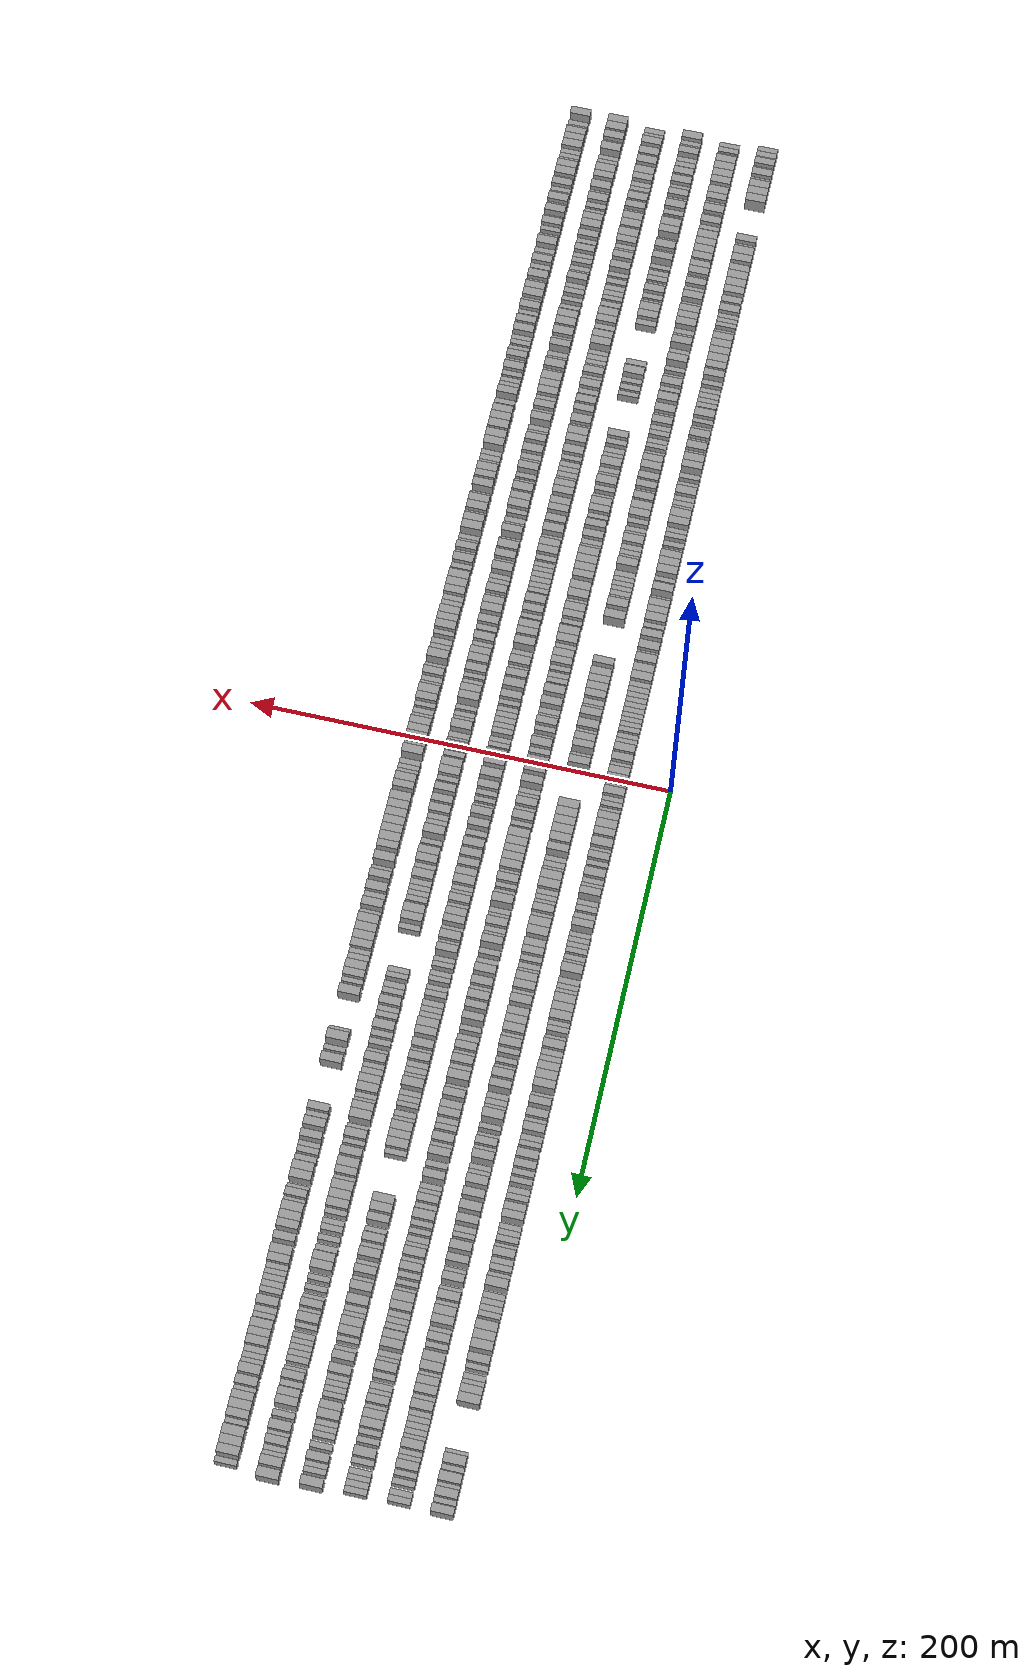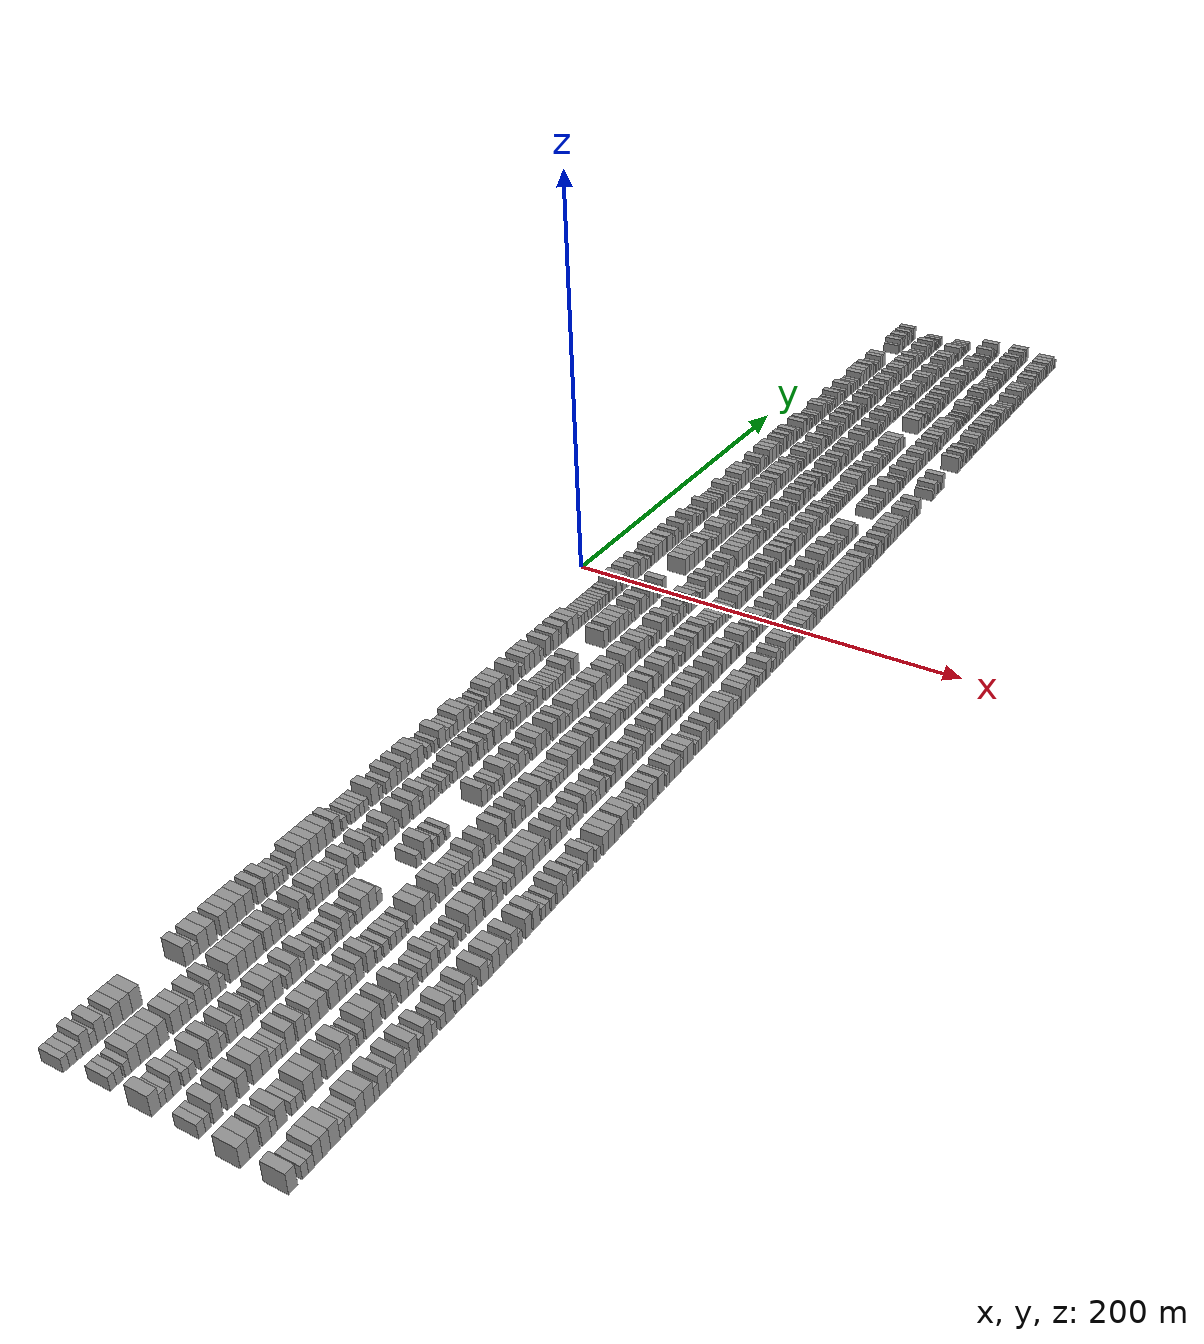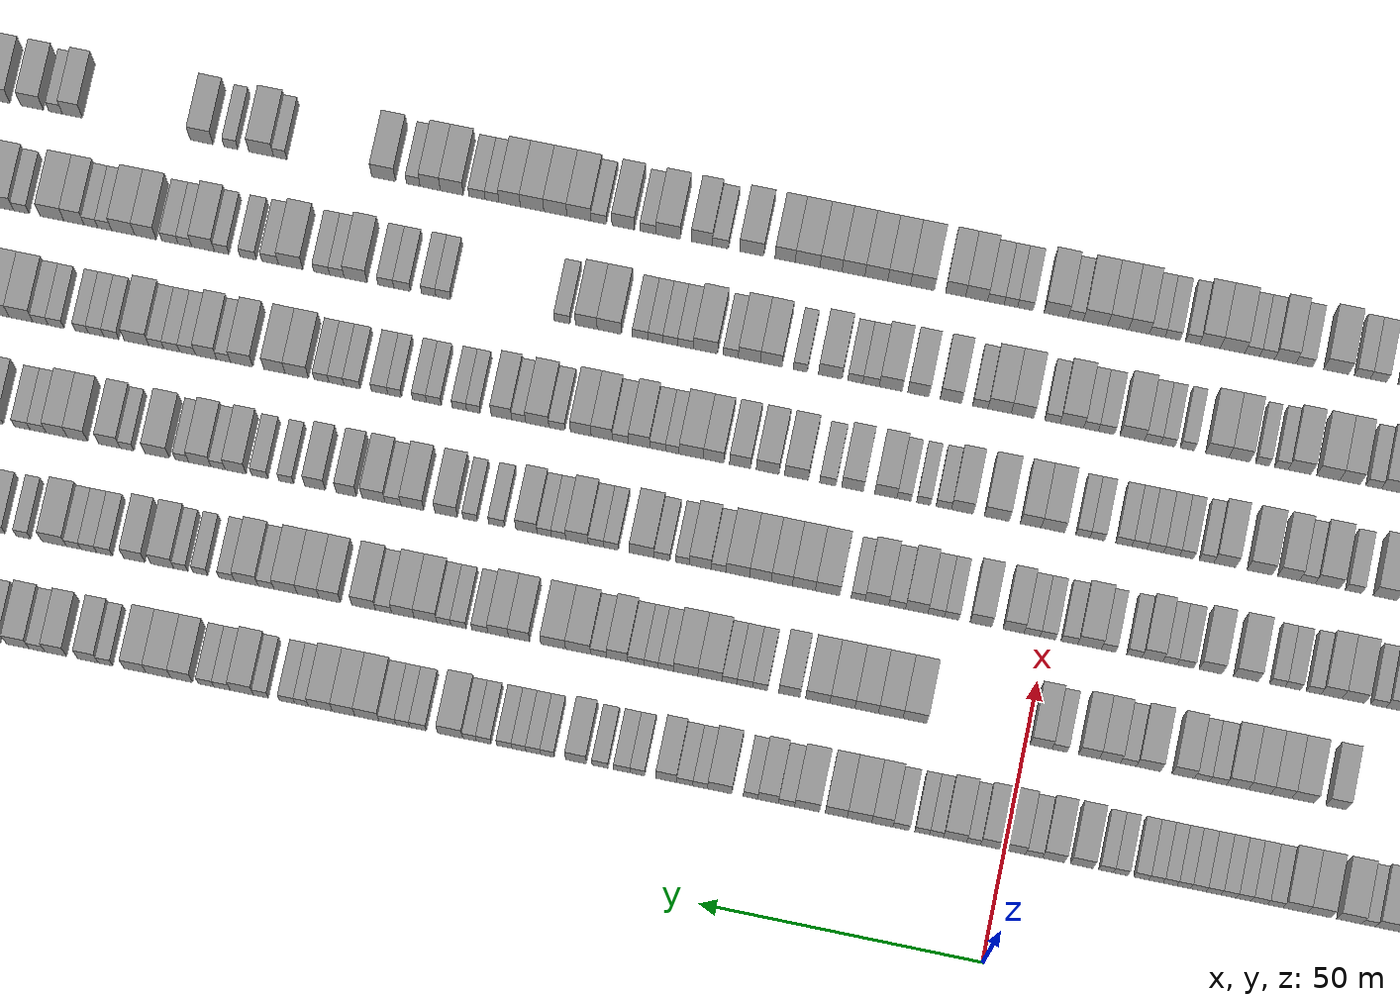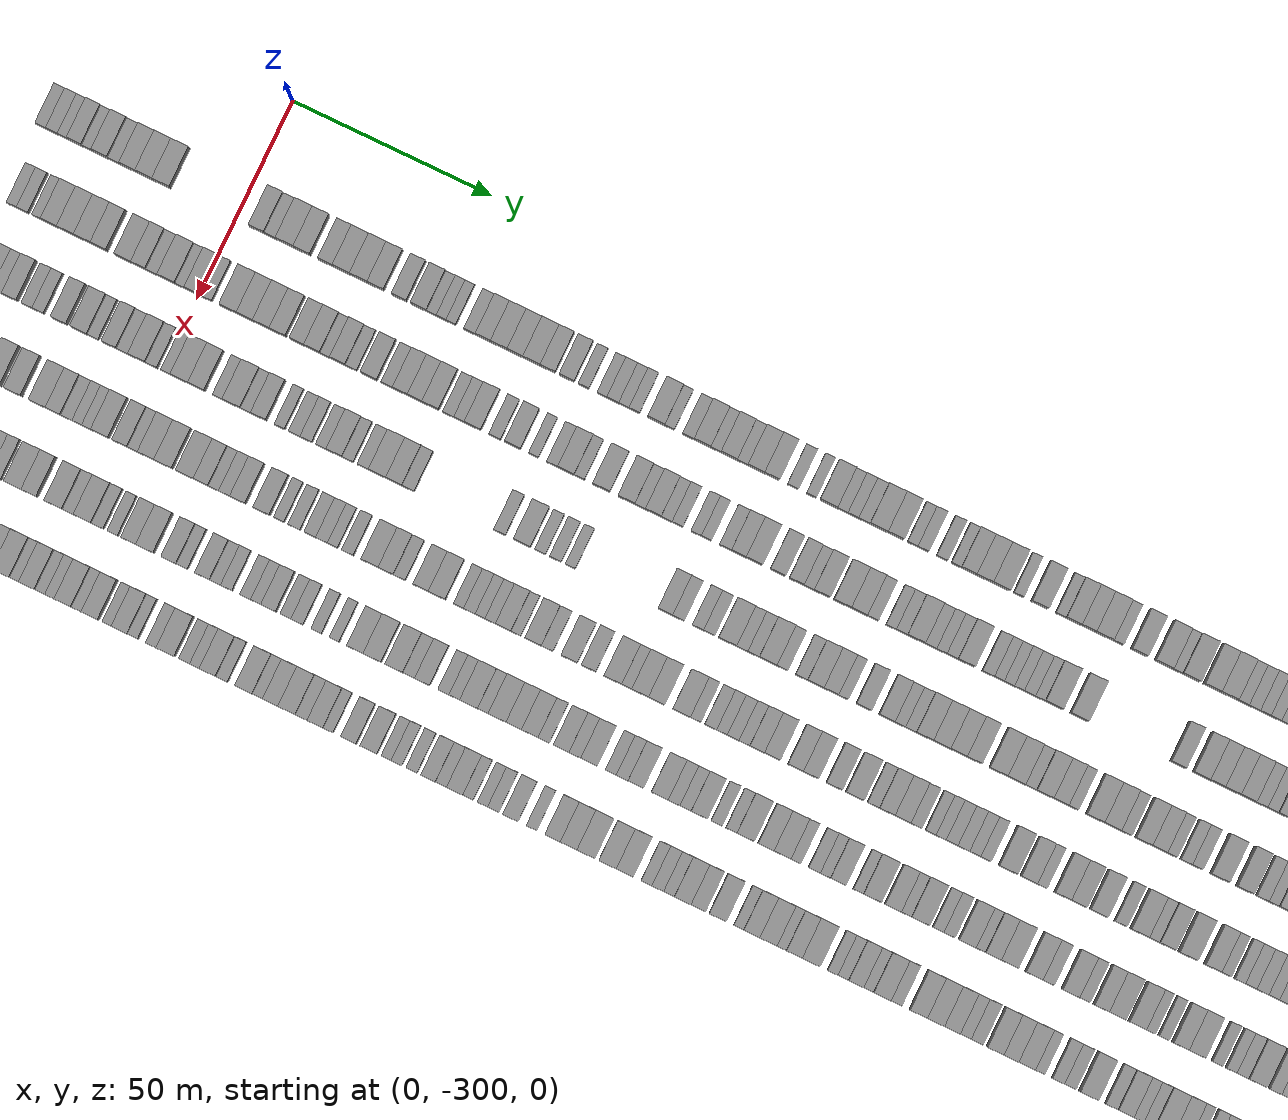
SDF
<sdf version="1.6">
 <world name="default">
  <scene>
   <sky><clouds><speed>12</speed></clouds></sky>
   <ambient>0.4 0.4 0.4 1</ambient>
   <background>0.7 0.7 0.7 1</background>
   <shadows>1</shadows>
  </scene>
  <gravity>0 0 -9.8066</gravity>
  <magnetic_field>6e-06 2.3e-05 -4.2e-05</magnetic_field>
  <physics default="0" name="default_physics" type="ode">
   <ode>
    <solver>
     <type>quick</type>
     <iters>10</iters>
     <sor>1.0</sor>
     <use_dynamic_moi_rescaling>0</use_dynamic_moi_rescaling>
    </solver>
    <constraints>
     <cfm>0</cfm>
     <erp>0.2</erp>
     <contact_max_correcting_vel>100</contact_max_correcting_vel>
     <contact_surface_layer>0.001</contact_surface_layer>
    </constraints>
   </ode>
   <max_step_size>0.004</max_step_size>
   <real_time_factor>1</real_time_factor>
   <real_time_update_rate>250</real_time_update_rate>
  </physics>
  <light name="sun" type="directional">
   <pose>0 0 10 0 0 0</pose>
   <diffuse>0.8 0.8 0.8 1</diffuse>
   <specular>0.2 0.2 0.2 1</specular>
   <attenuation>
    <range>1000</range>
    <constant>0.9</constant>
    <linear>0.01</linear>
    <quadratic>0.001</quadratic>
   </attenuation>
   <direction>-0.5 0.1 -0.9</direction>
  </light>
  <model name="building_1">
   <static>1</static>
   <pose>25.0000 -348.6661 0 0.000000 0.000000 0.000000</pose>
   <link name="link">
    <pose>0 0 3.00 0 0 0</pose>
    <collision name="collision"><geometry><box><size>10.0000 2.6678 6.0000</size></box></geometry></collision>
    <visual name="visual">
     <cast_shadows>0</cast_shadows>
     <geometry><box><size>10.0000 2.6678 6.0000</size></box></geometry>
     <material>
      <script>
       <uri>model://grey_wall/materials/scripts</uri>
       <uri>model://grey_wall/materials/textures</uri>
       <name>vrc/grey_wall</name>
      </script>
     </material>
    </visual>
   </link>
  </model>
  <model name="building_2">
   <static>1</static>
   <pose>25.0000 -345.8453 0 0.000000 0.000000 0.000000</pose>
   <link name="link">
    <pose>0 0 3.00 0 0 0</pose>
    <collision name="collision"><geometry><box><size>10.0000 2.9737 6.0000</size></box></geometry></collision>
    <visual name="visual">
     <cast_shadows>0</cast_shadows>
     <geometry><box><size>10.0000 2.9737 6.0000</size></box></geometry>
     <material>
      <script>
       <uri>model://grey_wall/materials/scripts</uri>
       <uri>model://grey_wall/materials/textures</uri>
       <name>vrc/grey_wall</name>
      </script>
     </material>
    </visual>
   </link>
  </model>
  <model name="building_3">
   <static>1</static>
   <pose>25.0000 -343.1168 0 0.000000 0.000000 0.000000</pose>
   <link name="link">
    <pose>0 0 3.00 0 0 0</pose>
    <collision name="collision"><geometry><box><size>10.0000 2.4832 6.0000</size></box></geometry></collision>
    <visual name="visual">
     <cast_shadows>0</cast_shadows>
     <geometry><box><size>10.0000 2.4832 6.0000</size></box></geometry>
     <material>
      <script>
       <uri>model://grey_wall/materials/scripts</uri>
       <uri>model://grey_wall/materials/textures</uri>
       <name>vrc/grey_wall</name>
      </script>
     </material>
    </visual>
   </link>
  </model>
  <model name="building_4">
   <static>1</static>
   <pose>25.0000 -340.0743 0 0.000000 0.000000 0.000000</pose>
   <link name="link">
    <pose>0 0 4.50 0 0 0</pose>
    <collision name="collision"><geometry><box><size>10.0000 3.6019 9.0000</size></box></geometry></collision>
    <visual name="visual">
     <cast_shadows>0</cast_shadows>
     <geometry><box><size>10.0000 3.6019 9.0000</size></box></geometry>
     <material>
      <script>
       <uri>model://grey_wall/materials/scripts</uri>
       <uri>model://grey_wall/materials/textures</uri>
       <name>vrc/grey_wall</name>
      </script>
     </material>
    </visual>
   </link>
  </model>
  <model name="building_5">
   <static>1</static>
   <pose>25.0000 -337.0081 0 0.000000 0.000000 0.000000</pose>
   <link name="link">
    <pose>0 0 3.00 0 0 0</pose>
    <collision name="collision"><geometry><box><size>10.0000 2.5305 6.0000</size></box></geometry></collision>
    <visual name="visual">
     <cast_shadows>0</cast_shadows>
     <geometry><box><size>10.0000 2.5305 6.0000</size></box></geometry>
     <material>
      <script>
       <uri>model://grey_wall/materials/scripts</uri>
       <uri>model://grey_wall/materials/textures</uri>
       <name>vrc/grey_wall</name>
      </script>
     </material>
    </visual>
   </link>
  </model>
  <model name="building_6">
   <static>1</static>
   <pose>25.0000 -333.7592 0 0.000000 0.000000 0.000000</pose>
   <link name="link">
    <pose>0 0 4.50 0 0 0</pose>
    <collision name="collision"><geometry><box><size>10.0000 3.9671 9.0000</size></box></geometry></collision>
    <visual name="visual">
     <cast_shadows>0</cast_shadows>
     <geometry><box><size>10.0000 3.9671 9.0000</size></box></geometry>
     <material>
      <script>
       <uri>model://grey_wall/materials/scripts</uri>
       <uri>model://grey_wall/materials/textures</uri>
       <name>vrc/grey_wall</name>
      </script>
     </material>
    </visual>
   </link>
  </model>
  <model name="building_7">
   <static>1</static>
   <pose>25.0000 -330.2775 0 0.000000 0.000000 0.000000</pose>
   <link name="link">
    <pose>0 0 3.00 0 0 0</pose>
    <collision name="collision"><geometry><box><size>10.0000 2.9964 6.0000</size></box></geometry></collision>
    <visual name="visual">
     <cast_shadows>0</cast_shadows>
     <geometry><box><size>10.0000 2.9964 6.0000</size></box></geometry>
     <material>
      <script>
       <uri>model://grey_wall/materials/scripts</uri>
       <uri>model://grey_wall/materials/textures</uri>
       <name>vrc/grey_wall</name>
      </script>
     </material>
    </visual>
   </link>
  </model>
  <model name="building_8">
   <static>1</static>
   <pose>25.0000 -326.7685 0 0.000000 0.000000 0.000000</pose>
   <link name="link">
    <pose>0 0 4.50 0 0 0</pose>
    <collision name="collision"><geometry><box><size>10.0000 4.0214 9.0000</size></box></geometry></collision>
    <visual name="visual">
     <cast_shadows>0</cast_shadows>
     <geometry><box><size>10.0000 4.0214 9.0000</size></box></geometry>
     <material>
      <script>
       <uri>model://grey_wall/materials/scripts</uri>
       <uri>model://grey_wall/materials/textures</uri>
       <name>vrc/grey_wall</name>
      </script>
     </material>
    </visual>
   </link>
  </model>
  <model name="building_9">
   <static>1</static>
   <pose>25.0000 -322.6493 0 0.000000 0.000000 0.000000</pose>
   <link name="link">
    <pose>0 0 4.50 0 0 0</pose>
    <collision name="collision"><geometry><box><size>10.0000 4.2170 9.0000</size></box></geometry></collision>
    <visual name="visual">
     <cast_shadows>0</cast_shadows>
     <geometry><box><size>10.0000 4.2170 9.0000</size></box></geometry>
     <material>
      <script>
       <uri>model://grey_wall/materials/scripts</uri>
       <uri>model://grey_wall/materials/textures</uri>
       <name>vrc/grey_wall</name>
      </script>
     </material>
    </visual>
   </link>
  </model>
  <model name="building_10">
   <static>1</static>
   <pose>25.0000 -318.3505 0 0.000000 0.000000 0.000000</pose>
   <link name="link">
    <pose>0 0 4.50 0 0 0</pose>
    <collision name="collision"><geometry><box><size>10.0000 4.3807 9.0000</size></box></geometry></collision>
    <visual name="visual">
     <cast_shadows>0</cast_shadows>
     <geometry><box><size>10.0000 4.3807 9.0000</size></box></geometry>
     <material>
      <script>
       <uri>model://grey_wall/materials/scripts</uri>
       <uri>model://grey_wall/materials/textures</uri>
       <name>vrc/grey_wall</name>
      </script>
     </material>
    </visual>
   </link>
  </model>
  <model name="building_11">
   <static>1</static>
   <pose>25.0000 -294.4763 0 0.000000 0.000000 0.000000</pose>
   <link name="link">
    <pose>0 0 4.50 0 0 0</pose>
    <collision name="collision"><geometry><box><size>10.0000 3.7892 9.0000</size></box></geometry></collision>
    <visual name="visual">
     <cast_shadows>0</cast_shadows>
     <geometry><box><size>10.0000 3.7892 9.0000</size></box></geometry>
     <material>
      <script>
       <uri>model://grey_wall/materials/scripts</uri>
       <uri>model://grey_wall/materials/textures</uri>
       <name>vrc/grey_wall</name>
      </script>
     </material>
    </visual>
   </link>
  </model>
  <model name="building_12">
   <static>1</static>
   <pose>25.0000 -291.1139 0 0.000000 0.000000 0.000000</pose>
   <link name="link">
    <pose>0 0 3.00 0 0 0</pose>
    <collision name="collision"><geometry><box><size>10.0000 2.9355 6.0000</size></box></geometry></collision>
    <visual name="visual">
     <cast_shadows>0</cast_shadows>
     <geometry><box><size>10.0000 2.9355 6.0000</size></box></geometry>
     <material>
      <script>
       <uri>model://grey_wall/materials/scripts</uri>
       <uri>model://grey_wall/materials/textures</uri>
       <name>vrc/grey_wall</name>
      </script>
     </material>
    </visual>
   </link>
  </model>
  <model name="building_13">
   <static>1</static>
   <pose>25.0000 -287.4135 0 0.000000 0.000000 0.000000</pose>
   <link name="link">
    <pose>0 0 4.50 0 0 0</pose>
    <collision name="collision"><geometry><box><size>10.0000 4.4653 9.0000</size></box></geometry></collision>
    <visual name="visual">
     <cast_shadows>0</cast_shadows>
     <geometry><box><size>10.0000 4.4653 9.0000</size></box></geometry>
     <material>
      <script>
       <uri>model://grey_wall/materials/scripts</uri>
       <uri>model://grey_wall/materials/textures</uri>
       <name>vrc/grey_wall</name>
      </script>
     </material>
    </visual>
   </link>
  </model>
  <model name="building_14">
   <static>1</static>
   <pose>25.0000 -283.1063 0 0.000000 0.000000 0.000000</pose>
   <link name="link">
    <pose>0 0 4.50 0 0 0</pose>
    <collision name="collision"><geometry><box><size>10.0000 4.1491 9.0000</size></box></geometry></collision>
    <visual name="visual">
     <cast_shadows>0</cast_shadows>
     <geometry><box><size>10.0000 4.1491 9.0000</size></box></geometry>
     <material>
      <script>
       <uri>model://grey_wall/materials/scripts</uri>
       <uri>model://grey_wall/materials/textures</uri>
       <name>vrc/grey_wall</name>
      </script>
     </material>
    </visual>
   </link>
  </model>
  <model name="building_15">
   <static>1</static>
   <pose>25.0000 -277.2079 0 0.000000 0.000000 0.000000</pose>
   <link name="link">
    <pose>0 0 4.50 0 0 0</pose>
    <collision name="collision"><geometry><box><size>10.0000 3.6478 9.0000</size></box></geometry></collision>
    <visual name="visual">
     <cast_shadows>0</cast_shadows>
     <geometry><box><size>10.0000 3.6478 9.0000</size></box></geometry>
     <material>
      <script>
       <uri>model://grey_wall/materials/scripts</uri>
       <uri>model://grey_wall/materials/textures</uri>
       <name>vrc/grey_wall</name>
      </script>
     </material>
    </visual>
   </link>
  </model>
  <model name="building_16">
   <static>1</static>
   <pose>25.0000 -273.2467 0 0.000000 0.000000 0.000000</pose>
   <link name="link">
    <pose>0 0 4.50 0 0 0</pose>
    <collision name="collision"><geometry><box><size>10.0000 4.2746 9.0000</size></box></geometry></collision>
    <visual name="visual">
     <cast_shadows>0</cast_shadows>
     <geometry><box><size>10.0000 4.2746 9.0000</size></box></geometry>
     <material>
      <script>
       <uri>model://grey_wall/materials/scripts</uri>
       <uri>model://grey_wall/materials/textures</uri>
       <name>vrc/grey_wall</name>
      </script>
     </material>
    </visual>
   </link>
  </model>
  <model name="building_17">
   <static>1</static>
   <pose>25.0000 -268.9025 0 0.000000 0.000000 0.000000</pose>
   <link name="link">
    <pose>0 0 4.50 0 0 0</pose>
    <collision name="collision"><geometry><box><size>10.0000 4.4139 9.0000</size></box></geometry></collision>
    <visual name="visual">
     <cast_shadows>0</cast_shadows>
     <geometry><box><size>10.0000 4.4139 9.0000</size></box></geometry>
     <material>
      <script>
       <uri>model://grey_wall/materials/scripts</uri>
       <uri>model://grey_wall/materials/textures</uri>
       <name>vrc/grey_wall</name>
      </script>
     </material>
    </visual>
   </link>
  </model>
  <model name="building_18">
   <static>1</static>
   <pose>25.0000 -264.6550 0 0.000000 0.000000 0.000000</pose>
   <link name="link">
    <pose>0 0 4.50 0 0 0</pose>
    <collision name="collision"><geometry><box><size>10.0000 4.0811 9.0000</size></box></geometry></collision>
    <visual name="visual">
     <cast_shadows>0</cast_shadows>
     <geometry><box><size>10.0000 4.0811 9.0000</size></box></geometry>
     <material>
      <script>
       <uri>model://grey_wall/materials/scripts</uri>
       <uri>model://grey_wall/materials/textures</uri>
       <name>vrc/grey_wall</name>
      </script>
     </material>
    </visual>
   </link>
  </model>
  <model name="building_19">
   <static>1</static>
   <pose>25.0000 -258.7499 0 0.000000 0.000000 0.000000</pose>
   <link name="link">
    <pose>0 0 4.50 0 0 0</pose>
    <collision name="collision"><geometry><box><size>10.0000 3.7290 9.0000</size></box></geometry></collision>
    <visual name="visual">
     <cast_shadows>0</cast_shadows>
     <geometry><box><size>10.0000 3.7290 9.0000</size></box></geometry>
     <material>
      <script>
       <uri>model://grey_wall/materials/scripts</uri>
       <uri>model://grey_wall/materials/textures</uri>
       <name>vrc/grey_wall</name>
      </script>
     </material>
    </visual>
   </link>
  </model>
  <model name="building_20">
   <static>1</static>
   <pose>25.0000 -253.8851 0 0.000000 0.000000 0.000000</pose>
   <link name="link">
    <pose>0 0 4.50 0 0 0</pose>
    <collision name="collision"><geometry><box><size>10.0000 4.0006 9.0000</size></box></geometry></collision>
    <visual name="visual">
     <cast_shadows>0</cast_shadows>
     <geometry><box><size>10.0000 4.0006 9.0000</size></box></geometry>
     <material>
      <script>
       <uri>model://grey_wall/materials/scripts</uri>
       <uri>model://grey_wall/materials/textures</uri>
       <name>vrc/grey_wall</name>
      </script>
     </material>
    </visual>
   </link>
  </model>
  <model name="building_21">
   <static>1</static>
   <pose>25.0000 -250.6720 0 0.000000 0.000000 0.000000</pose>
   <link name="link">
    <pose>0 0 3.00 0 0 0</pose>
    <collision name="collision"><geometry><box><size>10.0000 2.4255 6.0000</size></box></geometry></collision>
    <visual name="visual">
     <cast_shadows>0</cast_shadows>
     <geometry><box><size>10.0000 2.4255 6.0000</size></box></geometry>
     <material>
      <script>
       <uri>model://grey_wall/materials/scripts</uri>
       <uri>model://grey_wall/materials/textures</uri>
       <name>vrc/grey_wall</name>
      </script>
     </material>
    </visual>
   </link>
  </model>
  <model name="building_22">
   <static>1</static>
   <pose>25.0000 -248.2370 0 0.000000 0.000000 0.000000</pose>
   <link name="link">
    <pose>0 0 3.00 0 0 0</pose>
    <collision name="collision"><geometry><box><size>10.0000 2.4445 6.0000</size></box></geometry></collision>
    <visual name="visual">
     <cast_shadows>0</cast_shadows>
     <geometry><box><size>10.0000 2.4445 6.0000</size></box></geometry>
     <material>
      <script>
       <uri>model://grey_wall/materials/scripts</uri>
       <uri>model://grey_wall/materials/textures</uri>
       <name>vrc/grey_wall</name>
      </script>
     </material>
    </visual>
   </link>
  </model>
  <model name="building_23">
   <static>1</static>
   <pose>25.0000 -245.7980 0 0.000000 0.000000 0.000000</pose>
   <link name="link">
    <pose>0 0 3.00 0 0 0</pose>
    <collision name="collision"><geometry><box><size>10.0000 2.4335 6.0000</size></box></geometry></collision>
    <visual name="visual">
     <cast_shadows>0</cast_shadows>
     <geometry><box><size>10.0000 2.4335 6.0000</size></box></geometry>
     <material>
      <script>
       <uri>model://grey_wall/materials/scripts</uri>
       <uri>model://grey_wall/materials/textures</uri>
       <name>vrc/grey_wall</name>
      </script>
     </material>
    </visual>
   </link>
  </model>
  <model name="building_24">
   <static>1</static>
   <pose>25.0000 -241.0925 0 0.000000 0.000000 0.000000</pose>
   <link name="link">
    <pose>0 0 3.00 0 0 0</pose>
    <collision name="collision"><geometry><box><size>10.0000 2.9776 6.0000</size></box></geometry></collision>
    <visual name="visual">
     <cast_shadows>0</cast_shadows>
     <geometry><box><size>10.0000 2.9776 6.0000</size></box></geometry>
     <material>
      <script>
       <uri>model://grey_wall/materials/scripts</uri>
       <uri>model://grey_wall/materials/textures</uri>
       <name>vrc/grey_wall</name>
      </script>
     </material>
    </visual>
   </link>
  </model>
  <model name="building_25">
   <static>1</static>
   <pose>25.0000 -237.7254 0 0.000000 0.000000 0.000000</pose>
   <link name="link">
    <pose>0 0 4.50 0 0 0</pose>
    <collision name="collision"><geometry><box><size>10.0000 3.7566 9.0000</size></box></geometry></collision>
    <visual name="visual">
     <cast_shadows>0</cast_shadows>
     <geometry><box><size>10.0000 3.7566 9.0000</size></box></geometry>
     <material>
      <script>
       <uri>model://grey_wall/materials/scripts</uri>
       <uri>model://grey_wall/materials/textures</uri>
       <name>vrc/grey_wall</name>
      </script>
     </material>
    </visual>
   </link>
  </model>
  <model name="building_26">
   <static>1</static>
   <pose>25.0000 -233.7572 0 0.000000 0.000000 0.000000</pose>
   <link name="link">
    <pose>0 0 4.50 0 0 0</pose>
    <collision name="collision"><geometry><box><size>10.0000 4.1797 9.0000</size></box></geometry></collision>
    <visual name="visual">
     <cast_shadows>0</cast_shadows>
     <geometry><box><size>10.0000 4.1797 9.0000</size></box></geometry>
     <material>
      <script>
       <uri>model://grey_wall/materials/scripts</uri>
       <uri>model://grey_wall/materials/textures</uri>
       <name>vrc/grey_wall</name>
      </script>
     </material>
    </visual>
   </link>
  </model>
  <model name="building_27">
   <static>1</static>
   <pose>25.0000 -229.7039 0 0.000000 0.000000 0.000000</pose>
   <link name="link">
    <pose>0 0 4.50 0 0 0</pose>
    <collision name="collision"><geometry><box><size>10.0000 3.9269 9.0000</size></box></geometry></collision>
    <visual name="visual">
     <cast_shadows>0</cast_shadows>
     <geometry><box><size>10.0000 3.9269 9.0000</size></box></geometry>
     <material>
      <script>
       <uri>model://grey_wall/materials/scripts</uri>
       <uri>model://grey_wall/materials/textures</uri>
       <name>vrc/grey_wall</name>
      </script>
     </material>
    </visual>
   </link>
  </model>
  <model name="building_28">
   <static>1</static>
   <pose>25.0000 -225.5859 0 0.000000 0.000000 0.000000</pose>
   <link name="link">
    <pose>0 0 4.50 0 0 0</pose>
    <collision name="collision"><geometry><box><size>10.0000 4.3091 9.0000</size></box></geometry></collision>
    <visual name="visual">
     <cast_shadows>0</cast_shadows>
     <geometry><box><size>10.0000 4.3091 9.0000</size></box></geometry>
     <material>
      <script>
       <uri>model://grey_wall/materials/scripts</uri>
       <uri>model://grey_wall/materials/textures</uri>
       <name>vrc/grey_wall</name>
      </script>
     </material>
    </visual>
   </link>
  </model>
  <model name="building_29">
   <static>1</static>
   <pose>25.0000 -221.5351 0 0.000000 0.000000 0.000000</pose>
   <link name="link">
    <pose>0 0 4.50 0 0 0</pose>
    <collision name="collision"><geometry><box><size>10.0000 3.7927 9.0000</size></box></geometry></collision>
    <visual name="visual">
     <cast_shadows>0</cast_shadows>
     <geometry><box><size>10.0000 3.7927 9.0000</size></box></geometry>
     <material>
      <script>
       <uri>model://grey_wall/materials/scripts</uri>
       <uri>model://grey_wall/materials/textures</uri>
       <name>vrc/grey_wall</name>
      </script>
     </material>
    </visual>
   </link>
  </model>
  <model name="building_30">
   <static>1</static>
   <pose>25.0000 -216.7678 0 0.000000 0.000000 0.000000</pose>
   <link name="link">
    <pose>0 0 4.50 0 0 0</pose>
    <collision name="collision"><geometry><box><size>10.0000 3.7419 9.0000</size></box></geometry></collision>
    <visual name="visual">
     <cast_shadows>0</cast_shadows>
     <geometry><box><size>10.0000 3.7419 9.0000</size></box></geometry>
     <material>
      <script>
       <uri>model://grey_wall/materials/scripts</uri>
       <uri>model://grey_wall/materials/textures</uri>
       <name>vrc/grey_wall</name>
      </script>
     </material>
    </visual>
   </link>
  </model>
  <model name="building_31">
   <static>1</static>
   <pose>25.0000 -212.5534 0 0.000000 0.000000 0.000000</pose>
   <link name="link">
    <pose>0 0 3.00 0 0 0</pose>
    <collision name="collision"><geometry><box><size>10.0000 2.6870 6.0000</size></box></geometry></collision>
    <visual name="visual">
     <cast_shadows>0</cast_shadows>
     <geometry><box><size>10.0000 2.6870 6.0000</size></box></geometry>
     <material>
      <script>
       <uri>model://grey_wall/materials/scripts</uri>
       <uri>model://grey_wall/materials/textures</uri>
       <name>vrc/grey_wall</name>
      </script>
     </material>
    </visual>
   </link>
  </model>
  <model name="building_32">
   <static>1</static>
   <pose>25.0000 -207.9829 0 0.000000 0.000000 0.000000</pose>
   <link name="link">
    <pose>0 0 3.00 0 0 0</pose>
    <collision name="collision"><geometry><box><size>10.0000 2.4540 6.0000</size></box></geometry></collision>
    <visual name="visual">
     <cast_shadows>0</cast_shadows>
     <geometry><box><size>10.0000 2.4540 6.0000</size></box></geometry>
     <material>
      <script>
       <uri>model://grey_wall/materials/scripts</uri>
       <uri>model://grey_wall/materials/textures</uri>
       <name>vrc/grey_wall</name>
      </script>
     </material>
    </visual>
   </link>
  </model>
  <model name="building_33">
   <static>1</static>
   <pose>25.0000 -205.2645 0 0.000000 0.000000 0.000000</pose>
   <link name="link">
    <pose>0 0 3.00 0 0 0</pose>
    <collision name="collision"><geometry><box><size>10.0000 2.9827 6.0000</size></box></geometry></collision>
    <visual name="visual">
     <cast_shadows>0</cast_shadows>
     <geometry><box><size>10.0000 2.9827 6.0000</size></box></geometry>
     <material>
      <script>
       <uri>model://grey_wall/materials/scripts</uri>
       <uri>model://grey_wall/materials/textures</uri>
       <name>vrc/grey_wall</name>
      </script>
     </material>
    </visual>
   </link>
  </model>
  <model name="building_34">
   <static>1</static>
   <pose>25.0000 -202.4823 0 0.000000 0.000000 0.000000</pose>
   <link name="link">
    <pose>0 0 3.00 0 0 0</pose>
    <collision name="collision"><geometry><box><size>10.0000 2.5817 6.0000</size></box></geometry></collision>
    <visual name="visual">
     <cast_shadows>0</cast_shadows>
     <geometry><box><size>10.0000 2.5817 6.0000</size></box></geometry>
     <material>
      <script>
       <uri>model://grey_wall/materials/scripts</uri>
       <uri>model://grey_wall/materials/textures</uri>
       <name>vrc/grey_wall</name>
      </script>
     </material>
    </visual>
   </link>
  </model>
  <model name="building_35">
   <static>1</static>
   <pose>25.0000 -199.8549 0 0.000000 0.000000 0.000000</pose>
   <link name="link">
    <pose>0 0 3.00 0 0 0</pose>
    <collision name="collision"><geometry><box><size>10.0000 2.6732 6.0000</size></box></geometry></collision>
    <visual name="visual">
     <cast_shadows>0</cast_shadows>
     <geometry><box><size>10.0000 2.6732 6.0000</size></box></geometry>
     <material>
      <script>
       <uri>model://grey_wall/materials/scripts</uri>
       <uri>model://grey_wall/materials/textures</uri>
       <name>vrc/grey_wall</name>
      </script>
     </material>
    </visual>
   </link>
  </model>
  <model name="building_36">
   <static>1</static>
   <pose>25.0000 -194.3737 0 0.000000 0.000000 0.000000</pose>
   <link name="link">
    <pose>0 0 4.50 0 0 0</pose>
    <collision name="collision"><geometry><box><size>10.0000 4.2893 9.0000</size></box></geometry></collision>
    <visual name="visual">
     <cast_shadows>0</cast_shadows>
     <geometry><box><size>10.0000 4.2893 9.0000</size></box></geometry>
     <material>
      <script>
       <uri>model://grey_wall/materials/scripts</uri>
       <uri>model://grey_wall/materials/textures</uri>
       <name>vrc/grey_wall</name>
      </script>
     </material>
    </visual>
   </link>
  </model>
  <model name="building_37">
   <static>1</static>
   <pose>25.0000 -191.0097 0 0.000000 0.000000 0.000000</pose>
   <link name="link">
    <pose>0 0 3.00 0 0 0</pose>
    <collision name="collision"><geometry><box><size>10.0000 2.4387 6.0000</size></box></geometry></collision>
    <visual name="visual">
     <cast_shadows>0</cast_shadows>
     <geometry><box><size>10.0000 2.4387 6.0000</size></box></geometry>
     <material>
      <script>
       <uri>model://grey_wall/materials/scripts</uri>
       <uri>model://grey_wall/materials/textures</uri>
       <name>vrc/grey_wall</name>
      </script>
     </material>
    </visual>
   </link>
  </model>
  <model name="building_38">
   <static>1</static>
   <pose>25.0000 -186.3396 0 0.000000 0.000000 0.000000</pose>
   <link name="link">
    <pose>0 0 3.00 0 0 0</pose>
    <collision name="collision"><geometry><box><size>10.0000 2.9016 6.0000</size></box></geometry></collision>
    <visual name="visual">
     <cast_shadows>0</cast_shadows>
     <geometry><box><size>10.0000 2.9016 6.0000</size></box></geometry>
     <material>
      <script>
       <uri>model://grey_wall/materials/scripts</uri>
       <uri>model://grey_wall/materials/textures</uri>
       <name>vrc/grey_wall</name>
      </script>
     </material>
    </visual>
   </link>
  </model>
  <model name="building_39">
   <static>1</static>
   <pose>25.0000 -182.8082 0 0.000000 0.000000 0.000000</pose>
   <link name="link">
    <pose>0 0 4.50 0 0 0</pose>
    <collision name="collision"><geometry><box><size>10.0000 4.1612 9.0000</size></box></geometry></collision>
    <visual name="visual">
     <cast_shadows>0</cast_shadows>
     <geometry><box><size>10.0000 4.1612 9.0000</size></box></geometry>
     <material>
      <script>
       <uri>model://grey_wall/materials/scripts</uri>
       <uri>model://grey_wall/materials/textures</uri>
       <name>vrc/grey_wall</name>
      </script>
     </material>
    </visual>
   </link>
  </model>
  <model name="building_40">
   <static>1</static>
   <pose>25.0000 -179.4409 0 0.000000 0.000000 0.000000</pose>
   <link name="link">
    <pose>0 0 3.00 0 0 0</pose>
    <collision name="collision"><geometry><box><size>10.0000 2.5734 6.0000</size></box></geometry></collision>
    <visual name="visual">
     <cast_shadows>0</cast_shadows>
     <geometry><box><size>10.0000 2.5734 6.0000</size></box></geometry>
     <material>
      <script>
       <uri>model://grey_wall/materials/scripts</uri>
       <uri>model://grey_wall/materials/textures</uri>
       <name>vrc/grey_wall</name>
      </script>
     </material>
    </visual>
   </link>
  </model>
  <model name="building_41">
   <static>1</static>
   <pose>25.0000 -176.1292 0 0.000000 0.000000 0.000000</pose>
   <link name="link">
    <pose>0 0 4.50 0 0 0</pose>
    <collision name="collision"><geometry><box><size>10.0000 4.0501 9.0000</size></box></geometry></collision>
    <visual name="visual">
     <cast_shadows>0</cast_shadows>
     <geometry><box><size>10.0000 4.0501 9.0000</size></box></geometry>
     <material>
      <script>
       <uri>model://grey_wall/materials/scripts</uri>
       <uri>model://grey_wall/materials/textures</uri>
       <name>vrc/grey_wall</name>
      </script>
     </material>
    </visual>
   </link>
  </model>
  <model name="building_42">
   <static>1</static>
   <pose>25.0000 -172.7815 0 0.000000 0.000000 0.000000</pose>
   <link name="link">
    <pose>0 0 3.00 0 0 0</pose>
    <collision name="collision"><geometry><box><size>10.0000 2.6453 6.0000</size></box></geometry></collision>
    <visual name="visual">
     <cast_shadows>0</cast_shadows>
     <geometry><box><size>10.0000 2.6453 6.0000</size></box></geometry>
     <material>
      <script>
       <uri>model://grey_wall/materials/scripts</uri>
       <uri>model://grey_wall/materials/textures</uri>
       <name>vrc/grey_wall</name>
      </script>
     </material>
    </visual>
   </link>
  </model>
  <model name="building_43">
   <static>1</static>
   <pose>25.0000 -169.3660 0 0.000000 0.000000 0.000000</pose>
   <link name="link">
    <pose>0 0 4.50 0 0 0</pose>
    <collision name="collision"><geometry><box><size>10.0000 4.1856 9.0000</size></box></geometry></collision>
    <visual name="visual">
     <cast_shadows>0</cast_shadows>
     <geometry><box><size>10.0000 4.1856 9.0000</size></box></geometry>
     <material>
      <script>
       <uri>model://grey_wall/materials/scripts</uri>
       <uri>model://grey_wall/materials/textures</uri>
       <name>vrc/grey_wall</name>
      </script>
     </material>
    </visual>
   </link>
  </model>
  <model name="building_44">
   <static>1</static>
   <pose>25.0000 -165.3843 0 0.000000 0.000000 0.000000</pose>
   <link name="link">
    <pose>0 0 4.50 0 0 0</pose>
    <collision name="collision"><geometry><box><size>10.0000 3.7779 9.0000</size></box></geometry></collision>
    <visual name="visual">
     <cast_shadows>0</cast_shadows>
     <geometry><box><size>10.0000 3.7779 9.0000</size></box></geometry>
     <material>
      <script>
       <uri>model://grey_wall/materials/scripts</uri>
       <uri>model://grey_wall/materials/textures</uri>
       <name>vrc/grey_wall</name>
      </script>
     </material>
    </visual>
   </link>
  </model>
  <model name="building_45">
   <static>1</static>
   <pose>25.0000 -160.1095 0 0.000000 0.000000 0.000000</pose>
   <link name="link">
    <pose>0 0 3.00 0 0 0</pose>
    <collision name="collision"><geometry><box><size>10.0000 2.7718 6.0000</size></box></geometry></collision>
    <visual name="visual">
     <cast_shadows>0</cast_shadows>
     <geometry><box><size>10.0000 2.7718 6.0000</size></box></geometry>
     <material>
      <script>
       <uri>model://grey_wall/materials/scripts</uri>
       <uri>model://grey_wall/materials/textures</uri>
       <name>vrc/grey_wall</name>
      </script>
     </material>
    </visual>
   </link>
  </model>
  <model name="building_46">
   <static>1</static>
   <pose>25.0000 -155.5191 0 0.000000 0.000000 0.000000</pose>
   <link name="link">
    <pose>0 0 3.00 0 0 0</pose>
    <collision name="collision"><geometry><box><size>10.0000 2.4091 6.0000</size></box></geometry></collision>
    <visual name="visual">
     <cast_shadows>0</cast_shadows>
     <geometry><box><size>10.0000 2.4091 6.0000</size></box></geometry>
     <material>
      <script>
       <uri>model://grey_wall/materials/scripts</uri>
       <uri>model://grey_wall/materials/textures</uri>
       <name>vrc/grey_wall</name>
      </script>
     </material>
    </visual>
   </link>
  </model>
  <model name="building_47">
   <static>1</static>
   <pose>25.0000 -151.1783 0 0.000000 0.000000 0.000000</pose>
   <link name="link">
    <pose>0 0 4.50 0 0 0</pose>
    <collision name="collision"><geometry><box><size>10.0000 4.2725 9.0000</size></box></geometry></collision>
    <visual name="visual">
     <cast_shadows>0</cast_shadows>
     <geometry><box><size>10.0000 4.2725 9.0000</size></box></geometry>
     <material>
      <script>
       <uri>model://grey_wall/materials/scripts</uri>
       <uri>model://grey_wall/materials/textures</uri>
       <name>vrc/grey_wall</name>
      </script>
     </material>
    </visual>
   </link>
  </model>
  <model name="building_48">
   <static>1</static>
   <pose>25.0000 -147.7212 0 0.000000 0.000000 0.000000</pose>
   <link name="link">
    <pose>0 0 3.00 0 0 0</pose>
    <collision name="collision"><geometry><box><size>10.0000 2.6418 6.0000</size></box></geometry></collision>
    <visual name="visual">
     <cast_shadows>0</cast_shadows>
     <geometry><box><size>10.0000 2.6418 6.0000</size></box></geometry>
     <material>
      <script>
       <uri>model://grey_wall/materials/scripts</uri>
       <uri>model://grey_wall/materials/textures</uri>
       <name>vrc/grey_wall</name>
      </script>
     </material>
    </visual>
   </link>
  </model>
  <model name="building_49">
   <static>1</static>
   <pose>25.0000 -145.0528 0 0.000000 0.000000 0.000000</pose>
   <link name="link">
    <pose>0 0 3.00 0 0 0</pose>
    <collision name="collision"><geometry><box><size>10.0000 2.6950 6.0000</size></box></geometry></collision>
    <visual name="visual">
     <cast_shadows>0</cast_shadows>
     <geometry><box><size>10.0000 2.6950 6.0000</size></box></geometry>
     <material>
      <script>
       <uri>model://grey_wall/materials/scripts</uri>
       <uri>model://grey_wall/materials/textures</uri>
       <name>vrc/grey_wall</name>
      </script>
     </material>
    </visual>
   </link>
  </model>
  <model name="building_50">
   <static>1</static>
   <pose>25.0000 -142.2822 0 0.000000 0.000000 0.000000</pose>
   <link name="link">
    <pose>0 0 3.00 0 0 0</pose>
    <collision name="collision"><geometry><box><size>10.0000 2.8463 6.0000</size></box></geometry></collision>
    <visual name="visual">
     <cast_shadows>0</cast_shadows>
     <geometry><box><size>10.0000 2.8463 6.0000</size></box></geometry>
     <material>
      <script>
       <uri>model://grey_wall/materials/scripts</uri>
       <uri>model://grey_wall/materials/textures</uri>
       <name>vrc/grey_wall</name>
      </script>
     </material>
    </visual>
   </link>
  </model>
  <model name="building_51">
   <static>1</static>
   <pose>25.0000 -138.6550 0 0.000000 0.000000 0.000000</pose>
   <link name="link">
    <pose>0 0 4.50 0 0 0</pose>
    <collision name="collision"><geometry><box><size>10.0000 4.4079 9.0000</size></box></geometry></collision>
    <visual name="visual">
     <cast_shadows>0</cast_shadows>
     <geometry><box><size>10.0000 4.4079 9.0000</size></box></geometry>
     <material>
      <script>
       <uri>model://grey_wall/materials/scripts</uri>
       <uri>model://grey_wall/materials/textures</uri>
       <name>vrc/grey_wall</name>
      </script>
     </material>
    </visual>
   </link>
  </model>
  <model name="building_52">
   <static>1</static>
   <pose>25.0000 -134.4407 0 0.000000 0.000000 0.000000</pose>
   <link name="link">
    <pose>0 0 4.50 0 0 0</pose>
    <collision name="collision"><geometry><box><size>10.0000 4.0207 9.0000</size></box></geometry></collision>
    <visual name="visual">
     <cast_shadows>0</cast_shadows>
     <geometry><box><size>10.0000 4.0207 9.0000</size></box></geometry>
     <material>
      <script>
       <uri>model://grey_wall/materials/scripts</uri>
       <uri>model://grey_wall/materials/textures</uri>
       <name>vrc/grey_wall</name>
      </script>
     </material>
    </visual>
   </link>
  </model>
  <model name="building_53">
   <static>1</static>
   <pose>25.0000 -130.1752 0 0.000000 0.000000 0.000000</pose>
   <link name="link">
    <pose>0 0 3.00 0 0 0</pose>
    <collision name="collision"><geometry><box><size>10.0000 2.5105 6.0000</size></box></geometry></collision>
    <visual name="visual">
     <cast_shadows>0</cast_shadows>
     <geometry><box><size>10.0000 2.5105 6.0000</size></box></geometry>
     <material>
      <script>
       <uri>model://grey_wall/materials/scripts</uri>
       <uri>model://grey_wall/materials/textures</uri>
       <name>vrc/grey_wall</name>
      </script>
     </material>
    </visual>
   </link>
  </model>
  <model name="building_54">
   <static>1</static>
   <pose>25.0000 -127.5446 0 0.000000 0.000000 0.000000</pose>
   <link name="link">
    <pose>0 0 3.00 0 0 0</pose>
    <collision name="collision"><geometry><box><size>10.0000 2.7506 6.0000</size></box></geometry></collision>
    <visual name="visual">
     <cast_shadows>0</cast_shadows>
     <geometry><box><size>10.0000 2.7506 6.0000</size></box></geometry>
     <material>
      <script>
       <uri>model://grey_wall/materials/scripts</uri>
       <uri>model://grey_wall/materials/textures</uri>
       <name>vrc/grey_wall</name>
      </script>
     </material>
    </visual>
   </link>
  </model>
  <model name="building_55">
   <static>1</static>
   <pose>25.0000 -122.8030 0 0.000000 0.000000 0.000000</pose>
   <link name="link">
    <pose>0 0 3.00 0 0 0</pose>
    <collision name="collision"><geometry><box><size>10.0000 2.7326 6.0000</size></box></geometry></collision>
    <visual name="visual">
     <cast_shadows>0</cast_shadows>
     <geometry><box><size>10.0000 2.7326 6.0000</size></box></geometry>
     <material>
      <script>
       <uri>model://grey_wall/materials/scripts</uri>
       <uri>model://grey_wall/materials/textures</uri>
       <name>vrc/grey_wall</name>
      </script>
     </material>
    </visual>
   </link>
  </model>
  <model name="building_56">
   <static>1</static>
   <pose>25.0000 -119.2318 0 0.000000 0.000000 0.000000</pose>
   <link name="link">
    <pose>0 0 3.00 0 0 0</pose>
    <collision name="collision"><geometry><box><size>10.0000 2.4099 6.0000</size></box></geometry></collision>
    <visual name="visual">
     <cast_shadows>0</cast_shadows>
     <geometry><box><size>10.0000 2.4099 6.0000</size></box></geometry>
     <material>
      <script>
       <uri>model://grey_wall/materials/scripts</uri>
       <uri>model://grey_wall/materials/textures</uri>
       <name>vrc/grey_wall</name>
      </script>
     </material>
    </visual>
   </link>
  </model>
  <model name="building_57">
   <static>1</static>
   <pose>25.0000 -116.1468 0 0.000000 0.000000 0.000000</pose>
   <link name="link">
    <pose>0 0 4.50 0 0 0</pose>
    <collision name="collision"><geometry><box><size>10.0000 3.7600 9.0000</size></box></geometry></collision>
    <visual name="visual">
     <cast_shadows>0</cast_shadows>
     <geometry><box><size>10.0000 3.7600 9.0000</size></box></geometry>
     <material>
      <script>
       <uri>model://grey_wall/materials/scripts</uri>
       <uri>model://grey_wall/materials/textures</uri>
       <name>vrc/grey_wall</name>
      </script>
     </material>
    </visual>
   </link>
  </model>
  <model name="building_58">
   <static>1</static>
   <pose>25.0000 -112.2133 0 0.000000 0.000000 0.000000</pose>
   <link name="link">
    <pose>0 0 4.50 0 0 0</pose>
    <collision name="collision"><geometry><box><size>10.0000 4.1070 9.0000</size></box></geometry></collision>
    <visual name="visual">
     <cast_shadows>0</cast_shadows>
     <geometry><box><size>10.0000 4.1070 9.0000</size></box></geometry>
     <material>
      <script>
       <uri>model://grey_wall/materials/scripts</uri>
       <uri>model://grey_wall/materials/textures</uri>
       <name>vrc/grey_wall</name>
      </script>
     </material>
    </visual>
   </link>
  </model>
  <model name="building_59">
   <static>1</static>
   <pose>25.0000 -108.0051 0 0.000000 0.000000 0.000000</pose>
   <link name="link">
    <pose>0 0 4.50 0 0 0</pose>
    <collision name="collision"><geometry><box><size>10.0000 4.3094 9.0000</size></box></geometry></collision>
    <visual name="visual">
     <cast_shadows>0</cast_shadows>
     <geometry><box><size>10.0000 4.3094 9.0000</size></box></geometry>
     <material>
      <script>
       <uri>model://grey_wall/materials/scripts</uri>
       <uri>model://grey_wall/materials/textures</uri>
       <name>vrc/grey_wall</name>
      </script>
     </material>
    </visual>
   </link>
  </model>
  <model name="building_60">
   <static>1</static>
   <pose>25.0000 -103.6474 0 0.000000 0.000000 0.000000</pose>
   <link name="link">
    <pose>0 0 3.00 0 0 0</pose>
    <collision name="collision"><geometry><box><size>10.0000 2.4061 6.0000</size></box></geometry></collision>
    <visual name="visual">
     <cast_shadows>0</cast_shadows>
     <geometry><box><size>10.0000 2.4061 6.0000</size></box></geometry>
     <material>
      <script>
       <uri>model://grey_wall/materials/scripts</uri>
       <uri>model://grey_wall/materials/textures</uri>
       <name>vrc/grey_wall</name>
      </script>
     </material>
    </visual>
   </link>
  </model>
  <model name="building_61">
   <static>1</static>
   <pose>25.0000 -98.3839 0 0.000000 0.000000 0.000000</pose>
   <link name="link">
    <pose>0 0 4.50 0 0 0</pose>
    <collision name="collision"><geometry><box><size>10.0000 4.1209 9.0000</size></box></geometry></collision>
    <visual name="visual">
     <cast_shadows>0</cast_shadows>
     <geometry><box><size>10.0000 4.1209 9.0000</size></box></geometry>
     <material>
      <script>
       <uri>model://grey_wall/materials/scripts</uri>
       <uri>model://grey_wall/materials/textures</uri>
       <name>vrc/grey_wall</name>
      </script>
     </material>
    </visual>
   </link>
  </model>
  <model name="building_62">
   <static>1</static>
   <pose>25.0000 -93.0656 0 0.000000 0.000000 0.000000</pose>
   <link name="link">
    <pose>0 0 3.00 0 0 0</pose>
    <collision name="collision"><geometry><box><size>10.0000 2.5155 6.0000</size></box></geometry></collision>
    <visual name="visual">
     <cast_shadows>0</cast_shadows>
     <geometry><box><size>10.0000 2.5155 6.0000</size></box></geometry>
     <material>
      <script>
       <uri>model://grey_wall/materials/scripts</uri>
       <uri>model://grey_wall/materials/textures</uri>
       <name>vrc/grey_wall</name>
      </script>
     </material>
    </visual>
   </link>
  </model>
  <model name="building_63">
   <static>1</static>
   <pose>25.0000 -89.9229 0 0.000000 0.000000 0.000000</pose>
   <link name="link">
    <pose>0 0 4.50 0 0 0</pose>
    <collision name="collision"><geometry><box><size>10.0000 3.7698 9.0000</size></box></geometry></collision>
    <visual name="visual">
     <cast_shadows>0</cast_shadows>
     <geometry><box><size>10.0000 3.7698 9.0000</size></box></geometry>
     <material>
      <script>
       <uri>model://grey_wall/materials/scripts</uri>
       <uri>model://grey_wall/materials/textures</uri>
       <name>vrc/grey_wall</name>
      </script>
     </material>
    </visual>
   </link>
  </model>
  <model name="building_64">
   <static>1</static>
   <pose>25.0000 -86.2341 0 0.000000 0.000000 0.000000</pose>
   <link name="link">
    <pose>0 0 4.50 0 0 0</pose>
    <collision name="collision"><geometry><box><size>10.0000 3.6079 9.0000</size></box></geometry></collision>
    <visual name="visual">
     <cast_shadows>0</cast_shadows>
     <geometry><box><size>10.0000 3.6079 9.0000</size></box></geometry>
     <material>
      <script>
       <uri>model://grey_wall/materials/scripts</uri>
       <uri>model://grey_wall/materials/textures</uri>
       <name>vrc/grey_wall</name>
      </script>
     </material>
    </visual>
   </link>
  </model>
  <model name="building_65">
   <static>1</static>
   <pose>25.0000 -82.2392 0 0.000000 0.000000 0.000000</pose>
   <link name="link">
    <pose>0 0 4.50 0 0 0</pose>
    <collision name="collision"><geometry><box><size>10.0000 4.3819 9.0000</size></box></geometry></collision>
    <visual name="visual">
     <cast_shadows>0</cast_shadows>
     <geometry><box><size>10.0000 4.3819 9.0000</size></box></geometry>
     <material>
      <script>
       <uri>model://grey_wall/materials/scripts</uri>
       <uri>model://grey_wall/materials/textures</uri>
       <name>vrc/grey_wall</name>
      </script>
     </material>
    </visual>
   </link>
  </model>
  <model name="building_66">
   <static>1</static>
   <pose>25.0000 -78.7629 0 0.000000 0.000000 0.000000</pose>
   <link name="link">
    <pose>0 0 3.00 0 0 0</pose>
    <collision name="collision"><geometry><box><size>10.0000 2.5707 6.0000</size></box></geometry></collision>
    <visual name="visual">
     <cast_shadows>0</cast_shadows>
     <geometry><box><size>10.0000 2.5707 6.0000</size></box></geometry>
     <material>
      <script>
       <uri>model://grey_wall/materials/scripts</uri>
       <uri>model://grey_wall/materials/textures</uri>
       <name>vrc/grey_wall</name>
      </script>
     </material>
    </visual>
   </link>
  </model>
  <model name="building_67">
   <static>1</static>
   <pose>25.0000 -73.4974 0 0.000000 0.000000 0.000000</pose>
   <link name="link">
    <pose>0 0 4.50 0 0 0</pose>
    <collision name="collision"><geometry><box><size>10.0000 3.9603 9.0000</size></box></geometry></collision>
    <visual name="visual">
     <cast_shadows>0</cast_shadows>
     <geometry><box><size>10.0000 3.9603 9.0000</size></box></geometry>
     <material>
      <script>
       <uri>model://grey_wall/materials/scripts</uri>
       <uri>model://grey_wall/materials/textures</uri>
       <name>vrc/grey_wall</name>
      </script>
     </material>
    </visual>
   </link>
  </model>
  <model name="building_68">
   <static>1</static>
   <pose>25.0000 -67.3333 0 0.000000 0.000000 0.000000</pose>
   <link name="link">
    <pose>0 0 4.50 0 0 0</pose>
    <collision name="collision"><geometry><box><size>10.0000 4.3679 9.0000</size></box></geometry></collision>
    <visual name="visual">
     <cast_shadows>0</cast_shadows>
     <geometry><box><size>10.0000 4.3679 9.0000</size></box></geometry>
     <material>
      <script>
       <uri>model://grey_wall/materials/scripts</uri>
       <uri>model://grey_wall/materials/textures</uri>
       <name>vrc/grey_wall</name>
      </script>
     </material>
    </visual>
   </link>
  </model>
  <model name="building_69">
   <static>1</static>
   <pose>25.0000 -63.9285 0 0.000000 0.000000 0.000000</pose>
   <link name="link">
    <pose>0 0 3.00 0 0 0</pose>
    <collision name="collision"><geometry><box><size>10.0000 2.4416 6.0000</size></box></geometry></collision>
    <visual name="visual">
     <cast_shadows>0</cast_shadows>
     <geometry><box><size>10.0000 2.4416 6.0000</size></box></geometry>
     <material>
      <script>
       <uri>model://grey_wall/materials/scripts</uri>
       <uri>model://grey_wall/materials/textures</uri>
       <name>vrc/grey_wall</name>
      </script>
     </material>
    </visual>
   </link>
  </model>
  <model name="building_70">
   <static>1</static>
   <pose>25.0000 -60.5088 0 0.000000 0.000000 0.000000</pose>
   <link name="link">
    <pose>0 0 4.50 0 0 0</pose>
    <collision name="collision"><geometry><box><size>10.0000 4.3978 9.0000</size></box></geometry></collision>
    <visual name="visual">
     <cast_shadows>0</cast_shadows>
     <geometry><box><size>10.0000 4.3978 9.0000</size></box></geometry>
     <material>
      <script>
       <uri>model://grey_wall/materials/scripts</uri>
       <uri>model://grey_wall/materials/textures</uri>
       <name>vrc/grey_wall</name>
      </script>
     </material>
    </visual>
   </link>
  </model>
  <model name="building_71">
   <static>1</static>
   <pose>25.0000 -55.2365 0 0.000000 0.000000 0.000000</pose>
   <link name="link">
    <pose>0 0 4.50 0 0 0</pose>
    <collision name="collision"><geometry><box><size>10.0000 4.1468 9.0000</size></box></geometry></collision>
    <visual name="visual">
     <cast_shadows>0</cast_shadows>
     <geometry><box><size>10.0000 4.1468 9.0000</size></box></geometry>
     <material>
      <script>
       <uri>model://grey_wall/materials/scripts</uri>
       <uri>model://grey_wall/materials/textures</uri>
       <name>vrc/grey_wall</name>
      </script>
     </material>
    </visual>
   </link>
  </model>
  <model name="building_72">
   <static>1</static>
   <pose>25.0000 -51.0389 0 0.000000 0.000000 0.000000</pose>
   <link name="link">
    <pose>0 0 4.50 0 0 0</pose>
    <collision name="collision"><geometry><box><size>10.0000 4.2485 9.0000</size></box></geometry></collision>
    <visual name="visual">
     <cast_shadows>0</cast_shadows>
     <geometry><box><size>10.0000 4.2485 9.0000</size></box></geometry>
     <material>
      <script>
       <uri>model://grey_wall/materials/scripts</uri>
       <uri>model://grey_wall/materials/textures</uri>
       <name>vrc/grey_wall</name>
      </script>
     </material>
    </visual>
   </link>
  </model>
  <model name="building_73">
   <static>1</static>
   <pose>25.0000 -47.5366 0 0.000000 0.000000 0.000000</pose>
   <link name="link">
    <pose>0 0 3.00 0 0 0</pose>
    <collision name="collision"><geometry><box><size>10.0000 2.7559 6.0000</size></box></geometry></collision>
    <visual name="visual">
     <cast_shadows>0</cast_shadows>
     <geometry><box><size>10.0000 2.7559 6.0000</size></box></geometry>
     <material>
      <script>
       <uri>model://grey_wall/materials/scripts</uri>
       <uri>model://grey_wall/materials/textures</uri>
       <name>vrc/grey_wall</name>
      </script>
     </material>
    </visual>
   </link>
  </model>
  <model name="building_74">
   <static>1</static>
   <pose>25.0000 -44.7502 0 0.000000 0.000000 0.000000</pose>
   <link name="link">
    <pose>0 0 3.00 0 0 0</pose>
    <collision name="collision"><geometry><box><size>10.0000 2.8169 6.0000</size></box></geometry></collision>
    <visual name="visual">
     <cast_shadows>0</cast_shadows>
     <geometry><box><size>10.0000 2.8169 6.0000</size></box></geometry>
     <material>
      <script>
       <uri>model://grey_wall/materials/scripts</uri>
       <uri>model://grey_wall/materials/textures</uri>
       <name>vrc/grey_wall</name>
      </script>
     </material>
    </visual>
   </link>
  </model>
  <model name="building_75">
   <static>1</static>
   <pose>25.0000 -42.0156 0 0.000000 0.000000 0.000000</pose>
   <link name="link">
    <pose>0 0 3.00 0 0 0</pose>
    <collision name="collision"><geometry><box><size>10.0000 2.6525 6.0000</size></box></geometry></collision>
    <visual name="visual">
     <cast_shadows>0</cast_shadows>
     <geometry><box><size>10.0000 2.6525 6.0000</size></box></geometry>
     <material>
      <script>
       <uri>model://grey_wall/materials/scripts</uri>
       <uri>model://grey_wall/materials/textures</uri>
       <name>vrc/grey_wall</name>
      </script>
     </material>
    </visual>
   </link>
  </model>
  <model name="building_76">
   <static>1</static>
   <pose>25.0000 -39.3534 0 0.000000 0.000000 0.000000</pose>
   <link name="link">
    <pose>0 0 3.00 0 0 0</pose>
    <collision name="collision"><geometry><box><size>10.0000 2.6719 6.0000</size></box></geometry></collision>
    <visual name="visual">
     <cast_shadows>0</cast_shadows>
     <geometry><box><size>10.0000 2.6719 6.0000</size></box></geometry>
     <material>
      <script>
       <uri>model://grey_wall/materials/scripts</uri>
       <uri>model://grey_wall/materials/textures</uri>
       <name>vrc/grey_wall</name>
      </script>
     </material>
    </visual>
   </link>
  </model>
  <model name="building_77">
   <static>1</static>
   <pose>25.0000 -36.6724 0 0.000000 0.000000 0.000000</pose>
   <link name="link">
    <pose>0 0 3.00 0 0 0</pose>
    <collision name="collision"><geometry><box><size>10.0000 2.6900 6.0000</size></box></geometry></collision>
    <visual name="visual">
     <cast_shadows>0</cast_shadows>
     <geometry><box><size>10.0000 2.6900 6.0000</size></box></geometry>
     <material>
      <script>
       <uri>model://grey_wall/materials/scripts</uri>
       <uri>model://grey_wall/materials/textures</uri>
       <name>vrc/grey_wall</name>
      </script>
     </material>
    </visual>
   </link>
  </model>
  <model name="building_78">
   <static>1</static>
   <pose>25.0000 -33.9858 0 0.000000 0.000000 0.000000</pose>
   <link name="link">
    <pose>0 0 3.00 0 0 0</pose>
    <collision name="collision"><geometry><box><size>10.0000 2.6833 6.0000</size></box></geometry></collision>
    <visual name="visual">
     <cast_shadows>0</cast_shadows>
     <geometry><box><size>10.0000 2.6833 6.0000</size></box></geometry>
     <material>
      <script>
       <uri>model://grey_wall/materials/scripts</uri>
       <uri>model://grey_wall/materials/textures</uri>
       <name>vrc/grey_wall</name>
      </script>
     </material>
    </visual>
   </link>
  </model>
  <model name="building_79">
   <static>1</static>
   <pose>25.0000 -31.4411 0 0.000000 0.000000 0.000000</pose>
   <link name="link">
    <pose>0 0 3.00 0 0 0</pose>
    <collision name="collision"><geometry><box><size>10.0000 2.4060 6.0000</size></box></geometry></collision>
    <visual name="visual">
     <cast_shadows>0</cast_shadows>
     <geometry><box><size>10.0000 2.4060 6.0000</size></box></geometry>
     <material>
      <script>
       <uri>model://grey_wall/materials/scripts</uri>
       <uri>model://grey_wall/materials/textures</uri>
       <name>vrc/grey_wall</name>
      </script>
     </material>
    </visual>
   </link>
  </model>
  <model name="building_80">
   <static>1</static>
   <pose>25.0000 -29.0162 0 0.000000 0.000000 0.000000</pose>
   <link name="link">
    <pose>0 0 3.00 0 0 0</pose>
    <collision name="collision"><geometry><box><size>10.0000 2.4437 6.0000</size></box></geometry></collision>
    <visual name="visual">
     <cast_shadows>0</cast_shadows>
     <geometry><box><size>10.0000 2.4437 6.0000</size></box></geometry>
     <material>
      <script>
       <uri>model://grey_wall/materials/scripts</uri>
       <uri>model://grey_wall/materials/textures</uri>
       <name>vrc/grey_wall</name>
      </script>
     </material>
    </visual>
   </link>
  </model>
  <model name="building_81">
   <static>1</static>
   <pose>25.0000 -26.5391 0 0.000000 0.000000 0.000000</pose>
   <link name="link">
    <pose>0 0 3.00 0 0 0</pose>
    <collision name="collision"><geometry><box><size>10.0000 2.5107 6.0000</size></box></geometry></collision>
    <visual name="visual">
     <cast_shadows>0</cast_shadows>
     <geometry><box><size>10.0000 2.5107 6.0000</size></box></geometry>
     <material>
      <script>
       <uri>model://grey_wall/materials/scripts</uri>
       <uri>model://grey_wall/materials/textures</uri>
       <name>vrc/grey_wall</name>
      </script>
     </material>
    </visual>
   </link>
  </model>
  <model name="building_82">
   <static>1</static>
   <pose>25.0000 -23.9669 0 0.000000 0.000000 0.000000</pose>
   <link name="link">
    <pose>0 0 3.00 0 0 0</pose>
    <collision name="collision"><geometry><box><size>10.0000 2.6337 6.0000</size></box></geometry></collision>
    <visual name="visual">
     <cast_shadows>0</cast_shadows>
     <geometry><box><size>10.0000 2.6337 6.0000</size></box></geometry>
     <material>
      <script>
       <uri>model://grey_wall/materials/scripts</uri>
       <uri>model://grey_wall/materials/textures</uri>
       <name>vrc/grey_wall</name>
      </script>
     </material>
    </visual>
   </link>
  </model>
  <model name="building_83">
   <static>1</static>
   <pose>25.0000 -20.3815 0 0.000000 0.000000 0.000000</pose>
   <link name="link">
    <pose>0 0 3.00 0 0 0</pose>
    <collision name="collision"><geometry><box><size>10.0000 2.5370 6.0000</size></box></geometry></collision>
    <visual name="visual">
     <cast_shadows>0</cast_shadows>
     <geometry><box><size>10.0000 2.5370 6.0000</size></box></geometry>
     <material>
      <script>
       <uri>model://grey_wall/materials/scripts</uri>
       <uri>model://grey_wall/materials/textures</uri>
       <name>vrc/grey_wall</name>
      </script>
     </material>
    </visual>
   </link>
  </model>
  <model name="building_84">
   <static>1</static>
   <pose>25.0000 -17.8090 0 0.000000 0.000000 0.000000</pose>
   <link name="link">
    <pose>0 0 3.00 0 0 0</pose>
    <collision name="collision"><geometry><box><size>10.0000 2.6080 6.0000</size></box></geometry></collision>
    <visual name="visual">
     <cast_shadows>0</cast_shadows>
     <geometry><box><size>10.0000 2.6080 6.0000</size></box></geometry>
     <material>
      <script>
       <uri>model://grey_wall/materials/scripts</uri>
       <uri>model://grey_wall/materials/textures</uri>
       <name>vrc/grey_wall</name>
      </script>
     </material>
    </visual>
   </link>
  </model>
  <model name="building_85">
   <static>1</static>
   <pose>25.0000 -13.5011 0 0.000000 0.000000 0.000000</pose>
   <link name="link">
    <pose>0 0 4.50 0 0 0</pose>
    <collision name="collision"><geometry><box><size>10.0000 4.0079 9.0000</size></box></geometry></collision>
    <visual name="visual">
     <cast_shadows>0</cast_shadows>
     <geometry><box><size>10.0000 4.0079 9.0000</size></box></geometry>
     <material>
      <script>
       <uri>model://grey_wall/materials/scripts</uri>
       <uri>model://grey_wall/materials/textures</uri>
       <name>vrc/grey_wall</name>
      </script>
     </material>
    </visual>
   </link>
  </model>
  <model name="building_86">
   <static>1</static>
   <pose>25.0000 -8.5472 0 0.000000 0.000000 0.000000</pose>
   <link name="link">
    <pose>0 0 4.50 0 0 0</pose>
    <collision name="collision"><geometry><box><size>10.0000 3.8999 9.0000</size></box></geometry></collision>
    <visual name="visual">
     <cast_shadows>0</cast_shadows>
     <geometry><box><size>10.0000 3.8999 9.0000</size></box></geometry>
     <material>
      <script>
       <uri>model://grey_wall/materials/scripts</uri>
       <uri>model://grey_wall/materials/textures</uri>
       <name>vrc/grey_wall</name>
      </script>
     </material>
    </visual>
   </link>
  </model>
  <model name="building_87">
   <static>1</static>
   <pose>25.0000 -5.0996 0 0.000000 0.000000 0.000000</pose>
   <link name="link">
    <pose>0 0 3.00 0 0 0</pose>
    <collision name="collision"><geometry><box><size>10.0000 2.9952 6.0000</size></box></geometry></collision>
    <visual name="visual">
     <cast_shadows>0</cast_shadows>
     <geometry><box><size>10.0000 2.9952 6.0000</size></box></geometry>
     <material>
      <script>
       <uri>model://grey_wall/materials/scripts</uri>
       <uri>model://grey_wall/materials/textures</uri>
       <name>vrc/grey_wall</name>
      </script>
     </material>
    </visual>
   </link>
  </model>
  <model name="building_88">
   <static>1</static>
   <pose>25.0000 -1.7115 0 0.000000 0.000000 0.000000</pose>
   <link name="link">
    <pose>0 0 4.50 0 0 0</pose>
    <collision name="collision"><geometry><box><size>10.0000 3.7810 9.0000</size></box></geometry></collision>
    <visual name="visual">
     <cast_shadows>0</cast_shadows>
     <geometry><box><size>10.0000 3.7810 9.0000</size></box></geometry>
     <material>
      <script>
       <uri>model://grey_wall/materials/scripts</uri>
       <uri>model://grey_wall/materials/textures</uri>
       <name>vrc/grey_wall</name>
      </script>
     </material>
    </visual>
   </link>
  </model>
  <model name="building_89">
   <static>1</static>
   <pose>25.0000 2.2634 0 0.000000 0.000000 0.000000</pose>
   <link name="link">
    <pose>0 0 4.50 0 0 0</pose>
    <collision name="collision"><geometry><box><size>10.0000 4.1690 9.0000</size></box></geometry></collision>
    <visual name="visual">
     <cast_shadows>0</cast_shadows>
     <geometry><box><size>10.0000 4.1690 9.0000</size></box></geometry>
     <material>
      <script>
       <uri>model://grey_wall/materials/scripts</uri>
       <uri>model://grey_wall/materials/textures</uri>
       <name>vrc/grey_wall</name>
      </script>
     </material>
    </visual>
   </link>
  </model>
  <model name="building_90">
   <static>1</static>
   <pose>25.0000 5.5895 0 0.000000 0.000000 0.000000</pose>
   <link name="link">
    <pose>0 0 3.00 0 0 0</pose>
    <collision name="collision"><geometry><box><size>10.0000 2.4832 6.0000</size></box></geometry></collision>
    <visual name="visual">
     <cast_shadows>0</cast_shadows>
     <geometry><box><size>10.0000 2.4832 6.0000</size></box></geometry>
     <material>
      <script>
       <uri>model://grey_wall/materials/scripts</uri>
       <uri>model://grey_wall/materials/textures</uri>
       <name>vrc/grey_wall</name>
      </script>
     </material>
    </visual>
   </link>
  </model>
  <model name="building_91">
   <static>1</static>
   <pose>25.0000 8.8632 0 0.000000 0.000000 0.000000</pose>
   <link name="link">
    <pose>0 0 4.50 0 0 0</pose>
    <collision name="collision"><geometry><box><size>10.0000 4.0643 9.0000</size></box></geometry></collision>
    <visual name="visual">
     <cast_shadows>0</cast_shadows>
     <geometry><box><size>10.0000 4.0643 9.0000</size></box></geometry>
     <material>
      <script>
       <uri>model://grey_wall/materials/scripts</uri>
       <uri>model://grey_wall/materials/textures</uri>
       <name>vrc/grey_wall</name>
      </script>
     </material>
    </visual>
   </link>
  </model>
  <model name="building_92">
   <static>1</static>
   <pose>25.0000 12.1231 0 0.000000 0.000000 0.000000</pose>
   <link name="link">
    <pose>0 0 3.00 0 0 0</pose>
    <collision name="collision"><geometry><box><size>10.0000 2.4555 6.0000</size></box></geometry></collision>
    <visual name="visual">
     <cast_shadows>0</cast_shadows>
     <geometry><box><size>10.0000 2.4555 6.0000</size></box></geometry>
     <material>
      <script>
       <uri>model://grey_wall/materials/scripts</uri>
       <uri>model://grey_wall/materials/textures</uri>
       <name>vrc/grey_wall</name>
      </script>
     </material>
    </visual>
   </link>
  </model>
  <model name="building_93">
   <static>1</static>
   <pose>25.0000 14.6333 0 0.000000 0.000000 0.000000</pose>
   <link name="link">
    <pose>0 0 3.00 0 0 0</pose>
    <collision name="collision"><geometry><box><size>10.0000 2.5648 6.0000</size></box></geometry></collision>
    <visual name="visual">
     <cast_shadows>0</cast_shadows>
     <geometry><box><size>10.0000 2.5648 6.0000</size></box></geometry>
     <material>
      <script>
       <uri>model://grey_wall/materials/scripts</uri>
       <uri>model://grey_wall/materials/textures</uri>
       <name>vrc/grey_wall</name>
      </script>
     </material>
    </visual>
   </link>
  </model>
  <model name="building_94">
   <static>1</static>
   <pose>25.0000 18.3720 0 0.000000 0.000000 0.000000</pose>
   <link name="link">
    <pose>0 0 3.00 0 0 0</pose>
    <collision name="collision"><geometry><box><size>10.0000 2.9128 6.0000</size></box></geometry></collision>
    <visual name="visual">
     <cast_shadows>0</cast_shadows>
     <geometry><box><size>10.0000 2.9128 6.0000</size></box></geometry>
     <material>
      <script>
       <uri>model://grey_wall/materials/scripts</uri>
       <uri>model://grey_wall/materials/textures</uri>
       <name>vrc/grey_wall</name>
      </script>
     </material>
    </visual>
   </link>
  </model>
  <model name="building_95">
   <static>1</static>
   <pose>25.0000 21.6835 0 0.000000 0.000000 0.000000</pose>
   <link name="link">
    <pose>0 0 4.50 0 0 0</pose>
    <collision name="collision"><geometry><box><size>10.0000 3.7102 9.0000</size></box></geometry></collision>
    <visual name="visual">
     <cast_shadows>0</cast_shadows>
     <geometry><box><size>10.0000 3.7102 9.0000</size></box></geometry>
     <material>
      <script>
       <uri>model://grey_wall/materials/scripts</uri>
       <uri>model://grey_wall/materials/textures</uri>
       <name>vrc/grey_wall</name>
      </script>
     </material>
    </visual>
   </link>
  </model>
  <model name="building_96">
   <static>1</static>
   <pose>25.0000 25.7046 0 0.000000 0.000000 0.000000</pose>
   <link name="link">
    <pose>0 0 4.50 0 0 0</pose>
    <collision name="collision"><geometry><box><size>10.0000 4.3320 9.0000</size></box></geometry></collision>
    <visual name="visual">
     <cast_shadows>0</cast_shadows>
     <geometry><box><size>10.0000 4.3320 9.0000</size></box></geometry>
     <material>
      <script>
       <uri>model://grey_wall/materials/scripts</uri>
       <uri>model://grey_wall/materials/textures</uri>
       <name>vrc/grey_wall</name>
      </script>
     </material>
    </visual>
   </link>
  </model>
  <model name="building_97">
   <static>1</static>
   <pose>25.0000 29.8140 0 0.000000 0.000000 0.000000</pose>
   <link name="link">
    <pose>0 0 4.50 0 0 0</pose>
    <collision name="collision"><geometry><box><size>10.0000 3.8866 9.0000</size></box></geometry></collision>
    <visual name="visual">
     <cast_shadows>0</cast_shadows>
     <geometry><box><size>10.0000 3.8866 9.0000</size></box></geometry>
     <material>
      <script>
       <uri>model://grey_wall/materials/scripts</uri>
       <uri>model://grey_wall/materials/textures</uri>
       <name>vrc/grey_wall</name>
      </script>
     </material>
    </visual>
   </link>
  </model>
  <model name="building_98">
   <static>1</static>
   <pose>25.0000 34.9618 0 0.000000 0.000000 0.000000</pose>
   <link name="link">
    <pose>0 0 4.50 0 0 0</pose>
    <collision name="collision"><geometry><box><size>10.0000 4.4091 9.0000</size></box></geometry></collision>
    <visual name="visual">
     <cast_shadows>0</cast_shadows>
     <geometry><box><size>10.0000 4.4091 9.0000</size></box></geometry>
     <material>
      <script>
       <uri>model://grey_wall/materials/scripts</uri>
       <uri>model://grey_wall/materials/textures</uri>
       <name>vrc/grey_wall</name>
      </script>
     </material>
    </visual>
   </link>
  </model>
  <model name="building_99">
   <static>1</static>
   <pose>25.0000 38.5921 0 0.000000 0.000000 0.000000</pose>
   <link name="link">
    <pose>0 0 3.00 0 0 0</pose>
    <collision name="collision"><geometry><box><size>10.0000 2.8514 6.0000</size></box></geometry></collision>
    <visual name="visual">
     <cast_shadows>0</cast_shadows>
     <geometry><box><size>10.0000 2.8514 6.0000</size></box></geometry>
     <material>
      <script>
       <uri>model://grey_wall/materials/scripts</uri>
       <uri>model://grey_wall/materials/textures</uri>
       <name>vrc/grey_wall</name>
      </script>
     </material>
    </visual>
   </link>
  </model>
  <model name="building_100">
   <static>1</static>
   <pose>25.0000 41.8275 0 0.000000 0.000000 0.000000</pose>
   <link name="link">
    <pose>0 0 4.50 0 0 0</pose>
    <collision name="collision"><geometry><box><size>10.0000 3.6194 9.0000</size></box></geometry></collision>
    <visual name="visual">
     <cast_shadows>0</cast_shadows>
     <geometry><box><size>10.0000 3.6194 9.0000</size></box></geometry>
     <material>
      <script>
       <uri>model://grey_wall/materials/scripts</uri>
       <uri>model://grey_wall/materials/textures</uri>
       <name>vrc/grey_wall</name>
      </script>
     </material>
    </visual>
   </link>
  </model>
  <model name="building_101">
   <static>1</static>
   <pose>25.0000 44.9341 0 0.000000 0.000000 0.000000</pose>
   <link name="link">
    <pose>0 0 3.00 0 0 0</pose>
    <collision name="collision"><geometry><box><size>10.0000 2.5939 6.0000</size></box></geometry></collision>
    <visual name="visual">
     <cast_shadows>0</cast_shadows>
     <geometry><box><size>10.0000 2.5939 6.0000</size></box></geometry>
     <material>
      <script>
       <uri>model://grey_wall/materials/scripts</uri>
       <uri>model://grey_wall/materials/textures</uri>
       <name>vrc/grey_wall</name>
      </script>
     </material>
    </visual>
   </link>
  </model>
  <model name="building_102">
   <static>1</static>
   <pose>25.0000 50.3878 0 0.000000 0.000000 0.000000</pose>
   <link name="link">
    <pose>0 0 4.50 0 0 0</pose>
    <collision name="collision"><geometry><box><size>10.0000 4.3136 9.0000</size></box></geometry></collision>
    <visual name="visual">
     <cast_shadows>0</cast_shadows>
     <geometry><box><size>10.0000 4.3136 9.0000</size></box></geometry>
     <material>
      <script>
       <uri>model://grey_wall/materials/scripts</uri>
       <uri>model://grey_wall/materials/textures</uri>
       <name>vrc/grey_wall</name>
      </script>
     </material>
    </visual>
   </link>
  </model>
  <model name="building_103">
   <static>1</static>
   <pose>25.0000 53.8488 0 0.000000 0.000000 0.000000</pose>
   <link name="link">
    <pose>0 0 3.00 0 0 0</pose>
    <collision name="collision"><geometry><box><size>10.0000 2.6082 6.0000</size></box></geometry></collision>
    <visual name="visual">
     <cast_shadows>0</cast_shadows>
     <geometry><box><size>10.0000 2.6082 6.0000</size></box></geometry>
     <material>
      <script>
       <uri>model://grey_wall/materials/scripts</uri>
       <uri>model://grey_wall/materials/textures</uri>
       <name>vrc/grey_wall</name>
      </script>
     </material>
    </visual>
   </link>
  </model>
  <model name="building_104">
   <static>1</static>
   <pose>25.0000 56.5940 0 0.000000 0.000000 0.000000</pose>
   <link name="link">
    <pose>0 0 3.00 0 0 0</pose>
    <collision name="collision"><geometry><box><size>10.0000 2.8821 6.0000</size></box></geometry></collision>
    <visual name="visual">
     <cast_shadows>0</cast_shadows>
     <geometry><box><size>10.0000 2.8821 6.0000</size></box></geometry>
     <material>
      <script>
       <uri>model://grey_wall/materials/scripts</uri>
       <uri>model://grey_wall/materials/textures</uri>
       <name>vrc/grey_wall</name>
      </script>
     </material>
    </visual>
   </link>
  </model>
  <model name="building_105">
   <static>1</static>
   <pose>25.0000 59.8552 0 0.000000 0.000000 0.000000</pose>
   <link name="link">
    <pose>0 0 4.50 0 0 0</pose>
    <collision name="collision"><geometry><box><size>10.0000 3.6404 9.0000</size></box></geometry></collision>
    <visual name="visual">
     <cast_shadows>0</cast_shadows>
     <geometry><box><size>10.0000 3.6404 9.0000</size></box></geometry>
     <material>
      <script>
       <uri>model://grey_wall/materials/scripts</uri>
       <uri>model://grey_wall/materials/textures</uri>
       <name>vrc/grey_wall</name>
      </script>
     </material>
    </visual>
   </link>
  </model>
  <model name="building_106">
   <static>1</static>
   <pose>25.0000 64.9903 0 0.000000 0.000000 0.000000</pose>
   <link name="link">
    <pose>0 0 3.00 0 0 0</pose>
    <collision name="collision"><geometry><box><size>10.0000 2.6298 6.0000</size></box></geometry></collision>
    <visual name="visual">
     <cast_shadows>0</cast_shadows>
     <geometry><box><size>10.0000 2.6298 6.0000</size></box></geometry>
     <material>
      <script>
       <uri>model://grey_wall/materials/scripts</uri>
       <uri>model://grey_wall/materials/textures</uri>
       <name>vrc/grey_wall</name>
      </script>
     </material>
    </visual>
   </link>
  </model>
  <model name="building_107">
   <static>1</static>
   <pose>25.0000 67.7396 0 0.000000 0.000000 0.000000</pose>
   <link name="link">
    <pose>0 0 3.00 0 0 0</pose>
    <collision name="collision"><geometry><box><size>10.0000 2.8688 6.0000</size></box></geometry></collision>
    <visual name="visual">
     <cast_shadows>0</cast_shadows>
     <geometry><box><size>10.0000 2.8688 6.0000</size></box></geometry>
     <material>
      <script>
       <uri>model://grey_wall/materials/scripts</uri>
       <uri>model://grey_wall/materials/textures</uri>
       <name>vrc/grey_wall</name>
      </script>
     </material>
    </visual>
   </link>
  </model>
  <model name="building_108">
   <static>1</static>
   <pose>25.0000 71.5971 0 0.000000 0.000000 0.000000</pose>
   <link name="link">
    <pose>0 0 3.00 0 0 0</pose>
    <collision name="collision"><geometry><box><size>10.0000 2.8461 6.0000</size></box></geometry></collision>
    <visual name="visual">
     <cast_shadows>0</cast_shadows>
     <geometry><box><size>10.0000 2.8461 6.0000</size></box></geometry>
     <material>
      <script>
       <uri>model://grey_wall/materials/scripts</uri>
       <uri>model://grey_wall/materials/textures</uri>
       <name>vrc/grey_wall</name>
      </script>
     </material>
    </visual>
   </link>
  </model>
  <model name="building_109">
   <static>1</static>
   <pose>25.0000 75.8723 0 0.000000 0.000000 0.000000</pose>
   <link name="link">
    <pose>0 0 4.50 0 0 0</pose>
    <collision name="collision"><geometry><box><size>10.0000 3.7042 9.0000</size></box></geometry></collision>
    <visual name="visual">
     <cast_shadows>0</cast_shadows>
     <geometry><box><size>10.0000 3.7042 9.0000</size></box></geometry>
     <material>
      <script>
       <uri>model://grey_wall/materials/scripts</uri>
       <uri>model://grey_wall/materials/textures</uri>
       <name>vrc/grey_wall</name>
      </script>
     </material>
    </visual>
   </link>
  </model>
  <model name="building_110">
   <static>1</static>
   <pose>25.0000 80.9524 0 0.000000 0.000000 0.000000</pose>
   <link name="link">
    <pose>0 0 3.00 0 0 0</pose>
    <collision name="collision"><geometry><box><size>10.0000 2.4559 6.0000</size></box></geometry></collision>
    <visual name="visual">
     <cast_shadows>0</cast_shadows>
     <geometry><box><size>10.0000 2.4559 6.0000</size></box></geometry>
     <material>
      <script>
       <uri>model://grey_wall/materials/scripts</uri>
       <uri>model://grey_wall/materials/textures</uri>
       <name>vrc/grey_wall</name>
      </script>
     </material>
    </visual>
   </link>
  </model>
  <model name="building_111">
   <static>1</static>
   <pose>25.0000 83.4660 0 0.000000 0.000000 0.000000</pose>
   <link name="link">
    <pose>0 0 3.00 0 0 0</pose>
    <collision name="collision"><geometry><box><size>10.0000 2.5713 6.0000</size></box></geometry></collision>
    <visual name="visual">
     <cast_shadows>0</cast_shadows>
     <geometry><box><size>10.0000 2.5713 6.0000</size></box></geometry>
     <material>
      <script>
       <uri>model://grey_wall/materials/scripts</uri>
       <uri>model://grey_wall/materials/textures</uri>
       <name>vrc/grey_wall</name>
      </script>
     </material>
    </visual>
   </link>
  </model>
  <model name="building_112">
   <static>1</static>
   <pose>25.0000 86.0088 0 0.000000 0.000000 0.000000</pose>
   <link name="link">
    <pose>0 0 3.00 0 0 0</pose>
    <collision name="collision"><geometry><box><size>10.0000 2.5143 6.0000</size></box></geometry></collision>
    <visual name="visual">
     <cast_shadows>0</cast_shadows>
     <geometry><box><size>10.0000 2.5143 6.0000</size></box></geometry>
     <material>
      <script>
       <uri>model://grey_wall/materials/scripts</uri>
       <uri>model://grey_wall/materials/textures</uri>
       <name>vrc/grey_wall</name>
      </script>
     </material>
    </visual>
   </link>
  </model>
  <model name="building_113">
   <static>1</static>
   <pose>25.0000 88.5937 0 0.000000 0.000000 0.000000</pose>
   <link name="link">
    <pose>0 0 3.00 0 0 0</pose>
    <collision name="collision"><geometry><box><size>10.0000 2.6556 6.0000</size></box></geometry></collision>
    <visual name="visual">
     <cast_shadows>0</cast_shadows>
     <geometry><box><size>10.0000 2.6556 6.0000</size></box></geometry>
     <material>
      <script>
       <uri>model://grey_wall/materials/scripts</uri>
       <uri>model://grey_wall/materials/textures</uri>
       <name>vrc/grey_wall</name>
      </script>
     </material>
    </visual>
   </link>
  </model>
  <model name="building_114">
   <static>1</static>
   <pose>25.0000 92.2387 0 0.000000 0.000000 0.000000</pose>
   <link name="link">
    <pose>0 0 3.00 0 0 0</pose>
    <collision name="collision"><geometry><box><size>10.0000 2.6344 6.0000</size></box></geometry></collision>
    <visual name="visual">
     <cast_shadows>0</cast_shadows>
     <geometry><box><size>10.0000 2.6344 6.0000</size></box></geometry>
     <material>
      <script>
       <uri>model://grey_wall/materials/scripts</uri>
       <uri>model://grey_wall/materials/textures</uri>
       <name>vrc/grey_wall</name>
      </script>
     </material>
    </visual>
   </link>
  </model>
  <model name="building_115">
   <static>1</static>
   <pose>25.0000 94.7714 0 0.000000 0.000000 0.000000</pose>
   <link name="link">
    <pose>0 0 3.00 0 0 0</pose>
    <collision name="collision"><geometry><box><size>10.0000 2.4309 6.0000</size></box></geometry></collision>
    <visual name="visual">
     <cast_shadows>0</cast_shadows>
     <geometry><box><size>10.0000 2.4309 6.0000</size></box></geometry>
     <material>
      <script>
       <uri>model://grey_wall/materials/scripts</uri>
       <uri>model://grey_wall/materials/textures</uri>
       <name>vrc/grey_wall</name>
      </script>
     </material>
    </visual>
   </link>
  </model>
  <model name="building_116">
   <static>1</static>
   <pose>25.0000 98.2021 0 0.000000 0.000000 0.000000</pose>
   <link name="link">
    <pose>0 0 4.50 0 0 0</pose>
    <collision name="collision"><geometry><box><size>10.0000 4.4305 9.0000</size></box></geometry></collision>
    <visual name="visual">
     <cast_shadows>0</cast_shadows>
     <geometry><box><size>10.0000 4.4305 9.0000</size></box></geometry>
     <material>
      <script>
       <uri>model://grey_wall/materials/scripts</uri>
       <uri>model://grey_wall/materials/textures</uri>
       <name>vrc/grey_wall</name>
      </script>
     </material>
    </visual>
   </link>
  </model>
  <model name="building_117">
   <static>1</static>
   <pose>25.0000 103.8893 0 0.000000 0.000000 0.000000</pose>
   <link name="link">
    <pose>0 0 3.00 0 0 0</pose>
    <collision name="collision"><geometry><box><size>10.0000 2.9440 6.0000</size></box></geometry></collision>
    <visual name="visual">
     <cast_shadows>0</cast_shadows>
     <geometry><box><size>10.0000 2.9440 6.0000</size></box></geometry>
     <material>
      <script>
       <uri>model://grey_wall/materials/scripts</uri>
       <uri>model://grey_wall/materials/textures</uri>
       <name>vrc/grey_wall</name>
      </script>
     </material>
    </visual>
   </link>
  </model>
  <model name="building_118">
   <static>1</static>
   <pose>25.0000 106.6412 0 0.000000 0.000000 0.000000</pose>
   <link name="link">
    <pose>0 0 3.00 0 0 0</pose>
    <collision name="collision"><geometry><box><size>10.0000 2.5597 6.0000</size></box></geometry></collision>
    <visual name="visual">
     <cast_shadows>0</cast_shadows>
     <geometry><box><size>10.0000 2.5597 6.0000</size></box></geometry>
     <material>
      <script>
       <uri>model://grey_wall/materials/scripts</uri>
       <uri>model://grey_wall/materials/textures</uri>
       <name>vrc/grey_wall</name>
      </script>
     </material>
    </visual>
   </link>
  </model>
  <model name="building_119">
   <static>1</static>
   <pose>25.0000 109.3910 0 0.000000 0.000000 0.000000</pose>
   <link name="link">
    <pose>0 0 3.00 0 0 0</pose>
    <collision name="collision"><geometry><box><size>10.0000 2.9399 6.0000</size></box></geometry></collision>
    <visual name="visual">
     <cast_shadows>0</cast_shadows>
     <geometry><box><size>10.0000 2.9399 6.0000</size></box></geometry>
     <material>
      <script>
       <uri>model://grey_wall/materials/scripts</uri>
       <uri>model://grey_wall/materials/textures</uri>
       <name>vrc/grey_wall</name>
      </script>
     </material>
    </visual>
   </link>
  </model>
  <model name="building_120">
   <static>1</static>
   <pose>25.0000 113.0023 0 0.000000 0.000000 0.000000</pose>
   <link name="link">
    <pose>0 0 4.50 0 0 0</pose>
    <collision name="collision"><geometry><box><size>10.0000 4.2828 9.0000</size></box></geometry></collision>
    <visual name="visual">
     <cast_shadows>0</cast_shadows>
     <geometry><box><size>10.0000 4.2828 9.0000</size></box></geometry>
     <material>
      <script>
       <uri>model://grey_wall/materials/scripts</uri>
       <uri>model://grey_wall/materials/textures</uri>
       <name>vrc/grey_wall</name>
      </script>
     </material>
    </visual>
   </link>
  </model>
  <model name="building_121">
   <static>1</static>
   <pose>25.0000 117.1433 0 0.000000 0.000000 0.000000</pose>
   <link name="link">
    <pose>0 0 4.50 0 0 0</pose>
    <collision name="collision"><geometry><box><size>10.0000 3.9991 9.0000</size></box></geometry></collision>
    <visual name="visual">
     <cast_shadows>0</cast_shadows>
     <geometry><box><size>10.0000 3.9991 9.0000</size></box></geometry>
     <material>
      <script>
       <uri>model://grey_wall/materials/scripts</uri>
       <uri>model://grey_wall/materials/textures</uri>
       <name>vrc/grey_wall</name>
      </script>
     </material>
    </visual>
   </link>
  </model>
  <model name="building_122">
   <static>1</static>
   <pose>25.0000 121.2584 0 0.000000 0.000000 0.000000</pose>
   <link name="link">
    <pose>0 0 4.50 0 0 0</pose>
    <collision name="collision"><geometry><box><size>10.0000 4.2312 9.0000</size></box></geometry></collision>
    <visual name="visual">
     <cast_shadows>0</cast_shadows>
     <geometry><box><size>10.0000 4.2312 9.0000</size></box></geometry>
     <material>
      <script>
       <uri>model://grey_wall/materials/scripts</uri>
       <uri>model://grey_wall/materials/textures</uri>
       <name>vrc/grey_wall</name>
      </script>
     </material>
    </visual>
   </link>
  </model>
  <model name="building_123">
   <static>1</static>
   <pose>25.0000 124.5934 0 0.000000 0.000000 0.000000</pose>
   <link name="link">
    <pose>0 0 3.00 0 0 0</pose>
    <collision name="collision"><geometry><box><size>10.0000 2.4387 6.0000</size></box></geometry></collision>
    <visual name="visual">
     <cast_shadows>0</cast_shadows>
     <geometry><box><size>10.0000 2.4387 6.0000</size></box></geometry>
     <material>
      <script>
       <uri>model://grey_wall/materials/scripts</uri>
       <uri>model://grey_wall/materials/textures</uri>
       <name>vrc/grey_wall</name>
      </script>
     </material>
    </visual>
   </link>
  </model>
  <model name="building_124">
   <static>1</static>
   <pose>25.0000 127.1882 0 0.000000 0.000000 0.000000</pose>
   <link name="link">
    <pose>0 0 3.00 0 0 0</pose>
    <collision name="collision"><geometry><box><size>10.0000 2.7509 6.0000</size></box></geometry></collision>
    <visual name="visual">
     <cast_shadows>0</cast_shadows>
     <geometry><box><size>10.0000 2.7509 6.0000</size></box></geometry>
     <material>
      <script>
       <uri>model://grey_wall/materials/scripts</uri>
       <uri>model://grey_wall/materials/textures</uri>
       <name>vrc/grey_wall</name>
      </script>
     </material>
    </visual>
   </link>
  </model>
  <model name="building_125">
   <static>1</static>
   <pose>25.0000 131.8658 0 0.000000 0.000000 0.000000</pose>
   <link name="link">
    <pose>0 0 3.00 0 0 0</pose>
    <collision name="collision"><geometry><box><size>10.0000 2.6044 6.0000</size></box></geometry></collision>
    <visual name="visual">
     <cast_shadows>0</cast_shadows>
     <geometry><box><size>10.0000 2.6044 6.0000</size></box></geometry>
     <material>
      <script>
       <uri>model://grey_wall/materials/scripts</uri>
       <uri>model://grey_wall/materials/textures</uri>
       <name>vrc/grey_wall</name>
      </script>
     </material>
    </visual>
   </link>
  </model>
  <model name="building_126">
   <static>1</static>
   <pose>25.0000 135.2582 0 0.000000 0.000000 0.000000</pose>
   <link name="link">
    <pose>0 0 4.50 0 0 0</pose>
    <collision name="collision"><geometry><box><size>10.0000 4.1804 9.0000</size></box></geometry></collision>
    <visual name="visual">
     <cast_shadows>0</cast_shadows>
     <geometry><box><size>10.0000 4.1804 9.0000</size></box></geometry>
     <material>
      <script>
       <uri>model://grey_wall/materials/scripts</uri>
       <uri>model://grey_wall/materials/textures</uri>
       <name>vrc/grey_wall</name>
      </script>
     </material>
    </visual>
   </link>
  </model>
  <model name="building_127">
   <static>1</static>
   <pose>25.0000 138.8129 0 0.000000 0.000000 0.000000</pose>
   <link name="link">
    <pose>0 0 3.00 0 0 0</pose>
    <collision name="collision"><geometry><box><size>10.0000 2.9291 6.0000</size></box></geometry></collision>
    <visual name="visual">
     <cast_shadows>0</cast_shadows>
     <geometry><box><size>10.0000 2.9291 6.0000</size></box></geometry>
     <material>
      <script>
       <uri>model://grey_wall/materials/scripts</uri>
       <uri>model://grey_wall/materials/textures</uri>
       <name>vrc/grey_wall</name>
      </script>
     </material>
    </visual>
   </link>
  </model>
  <model name="building_128">
   <static>1</static>
   <pose>25.0000 141.6678 0 0.000000 0.000000 0.000000</pose>
   <link name="link">
    <pose>0 0 3.00 0 0 0</pose>
    <collision name="collision"><geometry><box><size>10.0000 2.7806 6.0000</size></box></geometry></collision>
    <visual name="visual">
     <cast_shadows>0</cast_shadows>
     <geometry><box><size>10.0000 2.7806 6.0000</size></box></geometry>
     <material>
      <script>
       <uri>model://grey_wall/materials/scripts</uri>
       <uri>model://grey_wall/materials/textures</uri>
       <name>vrc/grey_wall</name>
      </script>
     </material>
    </visual>
   </link>
  </model>
  <model name="building_129">
   <static>1</static>
   <pose>25.0000 145.9909 0 0.000000 0.000000 0.000000</pose>
   <link name="link">
    <pose>0 0 4.50 0 0 0</pose>
    <collision name="collision"><geometry><box><size>10.0000 3.8657 9.0000</size></box></geometry></collision>
    <visual name="visual">
     <cast_shadows>0</cast_shadows>
     <geometry><box><size>10.0000 3.8657 9.0000</size></box></geometry>
     <material>
      <script>
       <uri>model://grey_wall/materials/scripts</uri>
       <uri>model://grey_wall/materials/textures</uri>
       <name>vrc/grey_wall</name>
      </script>
     </material>
    </visual>
   </link>
  </model>
  <model name="building_130">
   <static>1</static>
   <pose>25.0000 150.1322 0 0.000000 0.000000 0.000000</pose>
   <link name="link">
    <pose>0 0 4.50 0 0 0</pose>
    <collision name="collision"><geometry><box><size>10.0000 4.4169 9.0000</size></box></geometry></collision>
    <visual name="visual">
     <cast_shadows>0</cast_shadows>
     <geometry><box><size>10.0000 4.4169 9.0000</size></box></geometry>
     <material>
      <script>
       <uri>model://grey_wall/materials/scripts</uri>
       <uri>model://grey_wall/materials/textures</uri>
       <name>vrc/grey_wall</name>
      </script>
     </material>
    </visual>
   </link>
  </model>
  <model name="building_131">
   <static>1</static>
   <pose>25.0000 154.3337 0 0.000000 0.000000 0.000000</pose>
   <link name="link">
    <pose>0 0 4.50 0 0 0</pose>
    <collision name="collision"><geometry><box><size>10.0000 3.9862 9.0000</size></box></geometry></collision>
    <visual name="visual">
     <cast_shadows>0</cast_shadows>
     <geometry><box><size>10.0000 3.9862 9.0000</size></box></geometry>
     <material>
      <script>
       <uri>model://grey_wall/materials/scripts</uri>
       <uri>model://grey_wall/materials/textures</uri>
       <name>vrc/grey_wall</name>
      </script>
     </material>
    </visual>
   </link>
  </model>
  <model name="building_132">
   <static>1</static>
   <pose>25.0000 159.6151 0 0.000000 0.000000 0.000000</pose>
   <link name="link">
    <pose>0 0 3.00 0 0 0</pose>
    <collision name="collision"><geometry><box><size>10.0000 2.5767 6.0000</size></box></geometry></collision>
    <visual name="visual">
     <cast_shadows>0</cast_shadows>
     <geometry><box><size>10.0000 2.5767 6.0000</size></box></geometry>
     <material>
      <script>
       <uri>model://grey_wall/materials/scripts</uri>
       <uri>model://grey_wall/materials/textures</uri>
       <name>vrc/grey_wall</name>
      </script>
     </material>
    </visual>
   </link>
  </model>
  <model name="building_133">
   <static>1</static>
   <pose>25.0000 162.7344 0 0.000000 0.000000 0.000000</pose>
   <link name="link">
    <pose>0 0 4.50 0 0 0</pose>
    <collision name="collision"><geometry><box><size>10.0000 3.6619 9.0000</size></box></geometry></collision>
    <visual name="visual">
     <cast_shadows>0</cast_shadows>
     <geometry><box><size>10.0000 3.6619 9.0000</size></box></geometry>
     <material>
      <script>
       <uri>model://grey_wall/materials/scripts</uri>
       <uri>model://grey_wall/materials/textures</uri>
       <name>vrc/grey_wall</name>
      </script>
     </material>
    </visual>
   </link>
  </model>
  <model name="building_134">
   <static>1</static>
   <pose>25.0000 168.4861 0 0.000000 0.000000 0.000000</pose>
   <link name="link">
    <pose>0 0 4.50 0 0 0</pose>
    <collision name="collision"><geometry><box><size>10.0000 3.8416 9.0000</size></box></geometry></collision>
    <visual name="visual">
     <cast_shadows>0</cast_shadows>
     <geometry><box><size>10.0000 3.8416 9.0000</size></box></geometry>
     <material>
      <script>
       <uri>model://grey_wall/materials/scripts</uri>
       <uri>model://grey_wall/materials/textures</uri>
       <name>vrc/grey_wall</name>
      </script>
     </material>
    </visual>
   </link>
  </model>
  <model name="building_135">
   <static>1</static>
   <pose>25.0000 171.8404 0 0.000000 0.000000 0.000000</pose>
   <link name="link">
    <pose>0 0 3.00 0 0 0</pose>
    <collision name="collision"><geometry><box><size>10.0000 2.8668 6.0000</size></box></geometry></collision>
    <visual name="visual">
     <cast_shadows>0</cast_shadows>
     <geometry><box><size>10.0000 2.8668 6.0000</size></box></geometry>
     <material>
      <script>
       <uri>model://grey_wall/materials/scripts</uri>
       <uri>model://grey_wall/materials/textures</uri>
       <name>vrc/grey_wall</name>
      </script>
     </material>
    </visual>
   </link>
  </model>
  <model name="building_136">
   <static>1</static>
   <pose>25.0000 175.2895 0 0.000000 0.000000 0.000000</pose>
   <link name="link">
    <pose>0 0 4.50 0 0 0</pose>
    <collision name="collision"><geometry><box><size>10.0000 4.0314 9.0000</size></box></geometry></collision>
    <visual name="visual">
     <cast_shadows>0</cast_shadows>
     <geometry><box><size>10.0000 4.0314 9.0000</size></box></geometry>
     <material>
      <script>
       <uri>model://grey_wall/materials/scripts</uri>
       <uri>model://grey_wall/materials/textures</uri>
       <name>vrc/grey_wall</name>
      </script>
     </material>
    </visual>
   </link>
  </model>
  <model name="building_137">
   <static>1</static>
   <pose>25.0000 179.7443 0 0.000000 0.000000 0.000000</pose>
   <link name="link">
    <pose>0 0 3.00 0 0 0</pose>
    <collision name="collision"><geometry><box><size>10.0000 2.8782 6.0000</size></box></geometry></collision>
    <visual name="visual">
     <cast_shadows>0</cast_shadows>
     <geometry><box><size>10.0000 2.8782 6.0000</size></box></geometry>
     <material>
      <script>
       <uri>model://grey_wall/materials/scripts</uri>
       <uri>model://grey_wall/materials/textures</uri>
       <name>vrc/grey_wall</name>
      </script>
     </material>
    </visual>
   </link>
  </model>
  <model name="building_138">
   <static>1</static>
   <pose>25.0000 182.4941 0 0.000000 0.000000 0.000000</pose>
   <link name="link">
    <pose>0 0 3.00 0 0 0</pose>
    <collision name="collision"><geometry><box><size>10.0000 2.6215 6.0000</size></box></geometry></collision>
    <visual name="visual">
     <cast_shadows>0</cast_shadows>
     <geometry><box><size>10.0000 2.6215 6.0000</size></box></geometry>
     <material>
      <script>
       <uri>model://grey_wall/materials/scripts</uri>
       <uri>model://grey_wall/materials/textures</uri>
       <name>vrc/grey_wall</name>
      </script>
     </material>
    </visual>
   </link>
  </model>
  <model name="building_139">
   <static>1</static>
   <pose>25.0000 187.8388 0 0.000000 0.000000 0.000000</pose>
   <link name="link">
    <pose>0 0 4.50 0 0 0</pose>
    <collision name="collision"><geometry><box><size>10.0000 4.0679 9.0000</size></box></geometry></collision>
    <visual name="visual">
     <cast_shadows>0</cast_shadows>
     <geometry><box><size>10.0000 4.0679 9.0000</size></box></geometry>
     <material>
      <script>
       <uri>model://grey_wall/materials/scripts</uri>
       <uri>model://grey_wall/materials/textures</uri>
       <name>vrc/grey_wall</name>
      </script>
     </material>
    </visual>
   </link>
  </model>
  <model name="building_140">
   <static>1</static>
   <pose>25.0000 192.7403 0 0.000000 0.000000 0.000000</pose>
   <link name="link">
    <pose>0 0 4.50 0 0 0</pose>
    <collision name="collision"><geometry><box><size>10.0000 3.7349 9.0000</size></box></geometry></collision>
    <visual name="visual">
     <cast_shadows>0</cast_shadows>
     <geometry><box><size>10.0000 3.7349 9.0000</size></box></geometry>
     <material>
      <script>
       <uri>model://grey_wall/materials/scripts</uri>
       <uri>model://grey_wall/materials/textures</uri>
       <name>vrc/grey_wall</name>
      </script>
     </material>
    </visual>
   </link>
  </model>
  <model name="building_141">
   <static>1</static>
   <pose>25.0000 196.0452 0 0.000000 0.000000 0.000000</pose>
   <link name="link">
    <pose>0 0 3.00 0 0 0</pose>
    <collision name="collision"><geometry><box><size>10.0000 2.8749 6.0000</size></box></geometry></collision>
    <visual name="visual">
     <cast_shadows>0</cast_shadows>
     <geometry><box><size>10.0000 2.8749 6.0000</size></box></geometry>
     <material>
      <script>
       <uri>model://grey_wall/materials/scripts</uri>
       <uri>model://grey_wall/materials/textures</uri>
       <name>vrc/grey_wall</name>
      </script>
     </material>
    </visual>
   </link>
  </model>
  <model name="building_142">
   <static>1</static>
   <pose>25.0000 199.8850 0 0.000000 0.000000 0.000000</pose>
   <link name="link">
    <pose>0 0 3.00 0 0 0</pose>
    <collision name="collision"><geometry><box><size>10.0000 2.8047 6.0000</size></box></geometry></collision>
    <visual name="visual">
     <cast_shadows>0</cast_shadows>
     <geometry><box><size>10.0000 2.8047 6.0000</size></box></geometry>
     <material>
      <script>
       <uri>model://grey_wall/materials/scripts</uri>
       <uri>model://grey_wall/materials/textures</uri>
       <name>vrc/grey_wall</name>
      </script>
     </material>
    </visual>
   </link>
  </model>
  <model name="building_143">
   <static>1</static>
   <pose>25.0000 204.7831 0 0.000000 0.000000 0.000000</pose>
   <link name="link">
    <pose>0 0 3.00 0 0 0</pose>
    <collision name="collision"><geometry><box><size>10.0000 2.9914 6.0000</size></box></geometry></collision>
    <visual name="visual">
     <cast_shadows>0</cast_shadows>
     <geometry><box><size>10.0000 2.9914 6.0000</size></box></geometry>
     <material>
      <script>
       <uri>model://grey_wall/materials/scripts</uri>
       <uri>model://grey_wall/materials/textures</uri>
       <name>vrc/grey_wall</name>
      </script>
     </material>
    </visual>
   </link>
  </model>
  <model name="building_144">
   <static>1</static>
   <pose>25.0000 207.7089 0 0.000000 0.000000 0.000000</pose>
   <link name="link">
    <pose>0 0 3.00 0 0 0</pose>
    <collision name="collision"><geometry><box><size>10.0000 2.8602 6.0000</size></box></geometry></collision>
    <visual name="visual">
     <cast_shadows>0</cast_shadows>
     <geometry><box><size>10.0000 2.8602 6.0000</size></box></geometry>
     <material>
      <script>
       <uri>model://grey_wall/materials/scripts</uri>
       <uri>model://grey_wall/materials/textures</uri>
       <name>vrc/grey_wall</name>
      </script>
     </material>
    </visual>
   </link>
  </model>
  <model name="building_145">
   <static>1</static>
   <pose>25.0000 212.9392 0 0.000000 0.000000 0.000000</pose>
   <link name="link">
    <pose>0 0 4.50 0 0 0</pose>
    <collision name="collision"><geometry><box><size>10.0000 3.6005 9.0000</size></box></geometry></collision>
    <visual name="visual">
     <cast_shadows>0</cast_shadows>
     <geometry><box><size>10.0000 3.6005 9.0000</size></box></geometry>
     <material>
      <script>
       <uri>model://grey_wall/materials/scripts</uri>
       <uri>model://grey_wall/materials/textures</uri>
       <name>vrc/grey_wall</name>
      </script>
     </material>
    </visual>
   </link>
  </model>
  <model name="building_146">
   <static>1</static>
   <pose>25.0000 216.6041 0 0.000000 0.000000 0.000000</pose>
   <link name="link">
    <pose>0 0 4.50 0 0 0</pose>
    <collision name="collision"><geometry><box><size>10.0000 3.7292 9.0000</size></box></geometry></collision>
    <visual name="visual">
     <cast_shadows>0</cast_shadows>
     <geometry><box><size>10.0000 3.7292 9.0000</size></box></geometry>
     <material>
      <script>
       <uri>model://grey_wall/materials/scripts</uri>
       <uri>model://grey_wall/materials/textures</uri>
       <name>vrc/grey_wall</name>
      </script>
     </material>
    </visual>
   </link>
  </model>
  <model name="building_147">
   <static>1</static>
   <pose>25.0000 221.7571 0 0.000000 0.000000 0.000000</pose>
   <link name="link">
    <pose>0 0 3.00 0 0 0</pose>
    <collision name="collision"><geometry><box><size>10.0000 2.5768 6.0000</size></box></geometry></collision>
    <visual name="visual">
     <cast_shadows>0</cast_shadows>
     <geometry><box><size>10.0000 2.5768 6.0000</size></box></geometry>
     <material>
      <script>
       <uri>model://grey_wall/materials/scripts</uri>
       <uri>model://grey_wall/materials/textures</uri>
       <name>vrc/grey_wall</name>
      </script>
     </material>
    </visual>
   </link>
  </model>
  <model name="building_148">
   <static>1</static>
   <pose>25.0000 224.4015 0 0.000000 0.000000 0.000000</pose>
   <link name="link">
    <pose>0 0 3.00 0 0 0</pose>
    <collision name="collision"><geometry><box><size>10.0000 2.7119 6.0000</size></box></geometry></collision>
    <visual name="visual">
     <cast_shadows>0</cast_shadows>
     <geometry><box><size>10.0000 2.7119 6.0000</size></box></geometry>
     <material>
      <script>
       <uri>model://grey_wall/materials/scripts</uri>
       <uri>model://grey_wall/materials/textures</uri>
       <name>vrc/grey_wall</name>
      </script>
     </material>
    </visual>
   </link>
  </model>
  <model name="building_149">
   <static>1</static>
   <pose>25.0000 227.2264 0 0.000000 0.000000 0.000000</pose>
   <link name="link">
    <pose>0 0 3.00 0 0 0</pose>
    <collision name="collision"><geometry><box><size>10.0000 2.9379 6.0000</size></box></geometry></collision>
    <visual name="visual">
     <cast_shadows>0</cast_shadows>
     <geometry><box><size>10.0000 2.9379 6.0000</size></box></geometry>
     <material>
      <script>
       <uri>model://grey_wall/materials/scripts</uri>
       <uri>model://grey_wall/materials/textures</uri>
       <name>vrc/grey_wall</name>
      </script>
     </material>
    </visual>
   </link>
  </model>
  <model name="building_150">
   <static>1</static>
   <pose>25.0000 230.9472 0 0.000000 0.000000 0.000000</pose>
   <link name="link">
    <pose>0 0 3.00 0 0 0</pose>
    <collision name="collision"><geometry><box><size>10.0000 2.5038 6.0000</size></box></geometry></collision>
    <visual name="visual">
     <cast_shadows>0</cast_shadows>
     <geometry><box><size>10.0000 2.5038 6.0000</size></box></geometry>
     <material>
      <script>
       <uri>model://grey_wall/materials/scripts</uri>
       <uri>model://grey_wall/materials/textures</uri>
       <name>vrc/grey_wall</name>
      </script>
     </material>
    </visual>
   </link>
  </model>
  <model name="building_151">
   <static>1</static>
   <pose>25.0000 234.1656 0 0.000000 0.000000 0.000000</pose>
   <link name="link">
    <pose>0 0 4.50 0 0 0</pose>
    <collision name="collision"><geometry><box><size>10.0000 3.9331 9.0000</size></box></geometry></collision>
    <visual name="visual">
     <cast_shadows>0</cast_shadows>
     <geometry><box><size>10.0000 3.9331 9.0000</size></box></geometry>
     <material>
      <script>
       <uri>model://grey_wall/materials/scripts</uri>
       <uri>model://grey_wall/materials/textures</uri>
       <name>vrc/grey_wall</name>
      </script>
     </material>
    </visual>
   </link>
  </model>
  <model name="building_152">
   <static>1</static>
   <pose>25.0000 237.5633 0 0.000000 0.000000 0.000000</pose>
   <link name="link">
    <pose>0 0 3.00 0 0 0</pose>
    <collision name="collision"><geometry><box><size>10.0000 2.8623 6.0000</size></box></geometry></collision>
    <visual name="visual">
     <cast_shadows>0</cast_shadows>
     <geometry><box><size>10.0000 2.8623 6.0000</size></box></geometry>
     <material>
      <script>
       <uri>model://grey_wall/materials/scripts</uri>
       <uri>model://grey_wall/materials/textures</uri>
       <name>vrc/grey_wall</name>
      </script>
     </material>
    </visual>
   </link>
  </model>
  <model name="building_153">
   <static>1</static>
   <pose>25.0000 240.4737 0 0.000000 0.000000 0.000000</pose>
   <link name="link">
    <pose>0 0 3.00 0 0 0</pose>
    <collision name="collision"><geometry><box><size>10.0000 2.9584 6.0000</size></box></geometry></collision>
    <visual name="visual">
     <cast_shadows>0</cast_shadows>
     <geometry><box><size>10.0000 2.9584 6.0000</size></box></geometry>
     <material>
      <script>
       <uri>model://grey_wall/materials/scripts</uri>
       <uri>model://grey_wall/materials/textures</uri>
       <name>vrc/grey_wall</name>
      </script>
     </material>
    </visual>
   </link>
  </model>
  <model name="building_154">
   <static>1</static>
   <pose>25.0000 244.3500 0 0.000000 0.000000 0.000000</pose>
   <link name="link">
    <pose>0 0 3.00 0 0 0</pose>
    <collision name="collision"><geometry><box><size>10.0000 2.7941 6.0000</size></box></geometry></collision>
    <visual name="visual">
     <cast_shadows>0</cast_shadows>
     <geometry><box><size>10.0000 2.7941 6.0000</size></box></geometry>
     <material>
      <script>
       <uri>model://grey_wall/materials/scripts</uri>
       <uri>model://grey_wall/materials/textures</uri>
       <name>vrc/grey_wall</name>
      </script>
     </material>
    </visual>
   </link>
  </model>
  <model name="building_155">
   <static>1</static>
   <pose>25.0000 247.9475 0 0.000000 0.000000 0.000000</pose>
   <link name="link">
    <pose>0 0 4.50 0 0 0</pose>
    <collision name="collision"><geometry><box><size>10.0000 4.4011 9.0000</size></box></geometry></collision>
    <visual name="visual">
     <cast_shadows>0</cast_shadows>
     <geometry><box><size>10.0000 4.4011 9.0000</size></box></geometry>
     <material>
      <script>
       <uri>model://grey_wall/materials/scripts</uri>
       <uri>model://grey_wall/materials/textures</uri>
       <name>vrc/grey_wall</name>
      </script>
     </material>
    </visual>
   </link>
  </model>
  <model name="building_156">
   <static>1</static>
   <pose>25.0000 253.5833 0 0.000000 0.000000 0.000000</pose>
   <link name="link">
    <pose>0 0 3.00 0 0 0</pose>
    <collision name="collision"><geometry><box><size>10.0000 2.8704 6.0000</size></box></geometry></collision>
    <visual name="visual">
     <cast_shadows>0</cast_shadows>
     <geometry><box><size>10.0000 2.8704 6.0000</size></box></geometry>
     <material>
      <script>
       <uri>model://grey_wall/materials/scripts</uri>
       <uri>model://grey_wall/materials/textures</uri>
       <name>vrc/grey_wall</name>
      </script>
     </material>
    </visual>
   </link>
  </model>
  <model name="building_157">
   <static>1</static>
   <pose>25.0000 256.4415 0 0.000000 0.000000 0.000000</pose>
   <link name="link">
    <pose>0 0 3.00 0 0 0</pose>
    <collision name="collision"><geometry><box><size>10.0000 2.8461 6.0000</size></box></geometry></collision>
    <visual name="visual">
     <cast_shadows>0</cast_shadows>
     <geometry><box><size>10.0000 2.8461 6.0000</size></box></geometry>
     <material>
      <script>
       <uri>model://grey_wall/materials/scripts</uri>
       <uri>model://grey_wall/materials/textures</uri>
       <name>vrc/grey_wall</name>
      </script>
     </material>
    </visual>
   </link>
  </model>
  <model name="building_158">
   <static>1</static>
   <pose>25.0000 259.3134 0 0.000000 0.000000 0.000000</pose>
   <link name="link">
    <pose>0 0 3.00 0 0 0</pose>
    <collision name="collision"><geometry><box><size>10.0000 2.8975 6.0000</size></box></geometry></collision>
    <visual name="visual">
     <cast_shadows>0</cast_shadows>
     <geometry><box><size>10.0000 2.8975 6.0000</size></box></geometry>
     <material>
      <script>
       <uri>model://grey_wall/materials/scripts</uri>
       <uri>model://grey_wall/materials/textures</uri>
       <name>vrc/grey_wall</name>
      </script>
     </material>
    </visual>
   </link>
  </model>
  <model name="building_159">
   <static>1</static>
   <pose>25.0000 262.1163 0 0.000000 0.000000 0.000000</pose>
   <link name="link">
    <pose>0 0 3.00 0 0 0</pose>
    <collision name="collision"><geometry><box><size>10.0000 2.7084 6.0000</size></box></geometry></collision>
    <visual name="visual">
     <cast_shadows>0</cast_shadows>
     <geometry><box><size>10.0000 2.7084 6.0000</size></box></geometry>
     <material>
      <script>
       <uri>model://grey_wall/materials/scripts</uri>
       <uri>model://grey_wall/materials/textures</uri>
       <name>vrc/grey_wall</name>
      </script>
     </material>
    </visual>
   </link>
  </model>
  <model name="building_160">
   <static>1</static>
   <pose>25.0000 267.6855 0 0.000000 0.000000 0.000000</pose>
   <link name="link">
    <pose>0 0 4.50 0 0 0</pose>
    <collision name="collision"><geometry><box><size>10.0000 4.4300 9.0000</size></box></geometry></collision>
    <visual name="visual">
     <cast_shadows>0</cast_shadows>
     <geometry><box><size>10.0000 4.4300 9.0000</size></box></geometry>
     <material>
      <script>
       <uri>model://grey_wall/materials/scripts</uri>
       <uri>model://grey_wall/materials/textures</uri>
       <name>vrc/grey_wall</name>
      </script>
     </material>
    </visual>
   </link>
  </model>
  <model name="building_161">
   <static>1</static>
   <pose>25.0000 272.0436 0 0.000000 0.000000 0.000000</pose>
   <link name="link">
    <pose>0 0 4.50 0 0 0</pose>
    <collision name="collision"><geometry><box><size>10.0000 4.2862 9.0000</size></box></geometry></collision>
    <visual name="visual">
     <cast_shadows>0</cast_shadows>
     <geometry><box><size>10.0000 4.2862 9.0000</size></box></geometry>
     <material>
      <script>
       <uri>model://grey_wall/materials/scripts</uri>
       <uri>model://grey_wall/materials/textures</uri>
       <name>vrc/grey_wall</name>
      </script>
     </material>
    </visual>
   </link>
  </model>
  <model name="building_162">
   <static>1</static>
   <pose>25.0000 276.3639 0 0.000000 0.000000 0.000000</pose>
   <link name="link">
    <pose>0 0 4.50 0 0 0</pose>
    <collision name="collision"><geometry><box><size>10.0000 4.3543 9.0000</size></box></geometry></collision>
    <visual name="visual">
     <cast_shadows>0</cast_shadows>
     <geometry><box><size>10.0000 4.3543 9.0000</size></box></geometry>
     <material>
      <script>
       <uri>model://grey_wall/materials/scripts</uri>
       <uri>model://grey_wall/materials/textures</uri>
       <name>vrc/grey_wall</name>
      </script>
     </material>
    </visual>
   </link>
  </model>
  <model name="building_163">
   <static>1</static>
   <pose>25.0000 282.5454 0 0.000000 0.000000 0.000000</pose>
   <link name="link">
    <pose>0 0 4.50 0 0 0</pose>
    <collision name="collision"><geometry><box><size>10.0000 4.0086 9.0000</size></box></geometry></collision>
    <visual name="visual">
     <cast_shadows>0</cast_shadows>
     <geometry><box><size>10.0000 4.0086 9.0000</size></box></geometry>
     <material>
      <script>
       <uri>model://grey_wall/materials/scripts</uri>
       <uri>model://grey_wall/materials/textures</uri>
       <name>vrc/grey_wall</name>
      </script>
     </material>
    </visual>
   </link>
  </model>
  <model name="building_164">
   <static>1</static>
   <pose>25.0000 285.8648 0 0.000000 0.000000 0.000000</pose>
   <link name="link">
    <pose>0 0 3.00 0 0 0</pose>
    <collision name="collision"><geometry><box><size>10.0000 2.6303 6.0000</size></box></geometry></collision>
    <visual name="visual">
     <cast_shadows>0</cast_shadows>
     <geometry><box><size>10.0000 2.6303 6.0000</size></box></geometry>
     <material>
      <script>
       <uri>model://grey_wall/materials/scripts</uri>
       <uri>model://grey_wall/materials/textures</uri>
       <name>vrc/grey_wall</name>
      </script>
     </material>
    </visual>
   </link>
  </model>
  <model name="building_165">
   <static>1</static>
   <pose>25.0000 290.5354 0 0.000000 0.000000 0.000000</pose>
   <link name="link">
    <pose>0 0 3.00 0 0 0</pose>
    <collision name="collision"><geometry><box><size>10.0000 2.7110 6.0000</size></box></geometry></collision>
    <visual name="visual">
     <cast_shadows>0</cast_shadows>
     <geometry><box><size>10.0000 2.7110 6.0000</size></box></geometry>
     <material>
      <script>
       <uri>model://grey_wall/materials/scripts</uri>
       <uri>model://grey_wall/materials/textures</uri>
       <name>vrc/grey_wall</name>
      </script>
     </material>
    </visual>
   </link>
  </model>
  <model name="building_166">
   <static>1</static>
   <pose>25.0000 293.3190 0 0.000000 0.000000 0.000000</pose>
   <link name="link">
    <pose>0 0 3.00 0 0 0</pose>
    <collision name="collision"><geometry><box><size>10.0000 2.8562 6.0000</size></box></geometry></collision>
    <visual name="visual">
     <cast_shadows>0</cast_shadows>
     <geometry><box><size>10.0000 2.8562 6.0000</size></box></geometry>
     <material>
      <script>
       <uri>model://grey_wall/materials/scripts</uri>
       <uri>model://grey_wall/materials/textures</uri>
       <name>vrc/grey_wall</name>
      </script>
     </material>
    </visual>
   </link>
  </model>
  <model name="building_167">
   <static>1</static>
   <pose>25.0000 296.5931 0 0.000000 0.000000 0.000000</pose>
   <link name="link">
    <pose>0 0 4.50 0 0 0</pose>
    <collision name="collision"><geometry><box><size>10.0000 3.6919 9.0000</size></box></geometry></collision>
    <visual name="visual">
     <cast_shadows>0</cast_shadows>
     <geometry><box><size>10.0000 3.6919 9.0000</size></box></geometry>
     <material>
      <script>
       <uri>model://grey_wall/materials/scripts</uri>
       <uri>model://grey_wall/materials/textures</uri>
       <name>vrc/grey_wall</name>
      </script>
     </material>
    </visual>
   </link>
  </model>
  <model name="building_168">
   <static>1</static>
   <pose>25.0000 300.5993 0 0.000000 0.000000 0.000000</pose>
   <link name="link">
    <pose>0 0 4.50 0 0 0</pose>
    <collision name="collision"><geometry><box><size>10.0000 4.3204 9.0000</size></box></geometry></collision>
    <visual name="visual">
     <cast_shadows>0</cast_shadows>
     <geometry><box><size>10.0000 4.3204 9.0000</size></box></geometry>
     <material>
      <script>
       <uri>model://grey_wall/materials/scripts</uri>
       <uri>model://grey_wall/materials/textures</uri>
       <name>vrc/grey_wall</name>
      </script>
     </material>
    </visual>
   </link>
  </model>
  <model name="building_169">
   <static>1</static>
   <pose>25.0000 324.3744 0 0.000000 0.000000 0.000000</pose>
   <link name="link">
    <pose>0 0 3.00 0 0 0</pose>
    <collision name="collision"><geometry><box><size>10.0000 2.4100 6.0000</size></box></geometry></collision>
    <visual name="visual">
     <cast_shadows>0</cast_shadows>
     <geometry><box><size>10.0000 2.4100 6.0000</size></box></geometry>
     <material>
      <script>
       <uri>model://grey_wall/materials/scripts</uri>
       <uri>model://grey_wall/materials/textures</uri>
       <name>vrc/grey_wall</name>
      </script>
     </material>
    </visual>
   </link>
  </model>
  <model name="building_170">
   <static>1</static>
   <pose>25.0000 327.8074 0 0.000000 0.000000 0.000000</pose>
   <link name="link">
    <pose>0 0 4.50 0 0 0</pose>
    <collision name="collision"><geometry><box><size>10.0000 4.4559 9.0000</size></box></geometry></collision>
    <visual name="visual">
     <cast_shadows>0</cast_shadows>
     <geometry><box><size>10.0000 4.4559 9.0000</size></box></geometry>
     <material>
      <script>
       <uri>model://grey_wall/materials/scripts</uri>
       <uri>model://grey_wall/materials/textures</uri>
       <name>vrc/grey_wall</name>
      </script>
     </material>
    </visual>
   </link>
  </model>
  <model name="building_171">
   <static>1</static>
   <pose>25.0000 331.2910 0 0.000000 0.000000 0.000000</pose>
   <link name="link">
    <pose>0 0 3.00 0 0 0</pose>
    <collision name="collision"><geometry><box><size>10.0000 2.5112 6.0000</size></box></geometry></collision>
    <visual name="visual">
     <cast_shadows>0</cast_shadows>
     <geometry><box><size>10.0000 2.5112 6.0000</size></box></geometry>
     <material>
      <script>
       <uri>model://grey_wall/materials/scripts</uri>
       <uri>model://grey_wall/materials/textures</uri>
       <name>vrc/grey_wall</name>
      </script>
     </material>
    </visual>
   </link>
  </model>
  <model name="building_172">
   <static>1</static>
   <pose>25.0000 335.7538 0 0.000000 0.000000 0.000000</pose>
   <link name="link">
    <pose>0 0 4.50 0 0 0</pose>
    <collision name="collision"><geometry><box><size>10.0000 4.4143 9.0000</size></box></geometry></collision>
    <visual name="visual">
     <cast_shadows>0</cast_shadows>
     <geometry><box><size>10.0000 4.4143 9.0000</size></box></geometry>
     <material>
      <script>
       <uri>model://grey_wall/materials/scripts</uri>
       <uri>model://grey_wall/materials/textures</uri>
       <name>vrc/grey_wall</name>
      </script>
     </material>
    </visual>
   </link>
  </model>
  <model name="building_173">
   <static>1</static>
   <pose>25.0000 339.2369 0 0.000000 0.000000 0.000000</pose>
   <link name="link">
    <pose>0 0 3.00 0 0 0</pose>
    <collision name="collision"><geometry><box><size>10.0000 2.5520 6.0000</size></box></geometry></collision>
    <visual name="visual">
     <cast_shadows>0</cast_shadows>
     <geometry><box><size>10.0000 2.5520 6.0000</size></box></geometry>
     <material>
      <script>
       <uri>model://grey_wall/materials/scripts</uri>
       <uri>model://grey_wall/materials/textures</uri>
       <name>vrc/grey_wall</name>
      </script>
     </material>
    </visual>
   </link>
  </model>
  <model name="building_174">
   <static>1</static>
   <pose>25.0000 342.5220 0 0.000000 0.000000 0.000000</pose>
   <link name="link">
    <pose>0 0 4.50 0 0 0</pose>
    <collision name="collision"><geometry><box><size>10.0000 4.0182 9.0000</size></box></geometry></collision>
    <visual name="visual">
     <cast_shadows>0</cast_shadows>
     <geometry><box><size>10.0000 4.0182 9.0000</size></box></geometry>
     <material>
      <script>
       <uri>model://grey_wall/materials/scripts</uri>
       <uri>model://grey_wall/materials/textures</uri>
       <name>vrc/grey_wall</name>
      </script>
     </material>
    </visual>
   </link>
  </model>
  <model name="building_175">
   <static>1</static>
   <pose>25.0000 345.7687 0 0.000000 0.000000 0.000000</pose>
   <link name="link">
    <pose>0 0 3.00 0 0 0</pose>
    <collision name="collision"><geometry><box><size>10.0000 2.4752 6.0000</size></box></geometry></collision>
    <visual name="visual">
     <cast_shadows>0</cast_shadows>
     <geometry><box><size>10.0000 2.4752 6.0000</size></box></geometry>
     <material>
      <script>
       <uri>model://grey_wall/materials/scripts</uri>
       <uri>model://grey_wall/materials/textures</uri>
       <name>vrc/grey_wall</name>
      </script>
     </material>
    </visual>
   </link>
  </model>
  <model name="building_176">
   <static>1</static>
   <pose>25.0000 349.8920 0 0.000000 0.000000 0.000000</pose>
   <link name="link">
    <pose>0 0 4.50 0 0 0</pose>
    <collision name="collision"><geometry><box><size>10.0000 3.7712 9.0000</size></box></geometry></collision>
    <visual name="visual">
     <cast_shadows>0</cast_shadows>
     <geometry><box><size>10.0000 3.7712 9.0000</size></box></geometry>
     <material>
      <script>
       <uri>model://grey_wall/materials/scripts</uri>
       <uri>model://grey_wall/materials/textures</uri>
       <name>vrc/grey_wall</name>
      </script>
     </material>
    </visual>
   </link>
  </model>
  <model name="building_177">
   <static>1</static>
   <pose>44.0000 -346.7183 0 0.000000 0.000000 0.000000</pose>
   <link name="link">
    <pose>0 0 3.00 0 0 0</pose>
    <collision name="collision"><geometry><box><size>10.0000 2.5633 6.0000</size></box></geometry></collision>
    <visual name="visual">
     <cast_shadows>0</cast_shadows>
     <geometry><box><size>10.0000 2.5633 6.0000</size></box></geometry>
     <material>
      <script>
       <uri>model://grey_wall/materials/scripts</uri>
       <uri>model://grey_wall/materials/textures</uri>
       <name>vrc/grey_wall</name>
      </script>
     </material>
    </visual>
   </link>
  </model>
  <model name="building_178">
   <static>1</static>
   <pose>44.0000 -344.0302 0 0.000000 0.000000 0.000000</pose>
   <link name="link">
    <pose>0 0 3.00 0 0 0</pose>
    <collision name="collision"><geometry><box><size>10.0000 2.8129 6.0000</size></box></geometry></collision>
    <visual name="visual">
     <cast_shadows>0</cast_shadows>
     <geometry><box><size>10.0000 2.8129 6.0000</size></box></geometry>
     <material>
      <script>
       <uri>model://grey_wall/materials/scripts</uri>
       <uri>model://grey_wall/materials/textures</uri>
       <name>vrc/grey_wall</name>
      </script>
     </material>
    </visual>
   </link>
  </model>
  <model name="building_179">
   <static>1</static>
   <pose>44.0000 -340.4170 0 0.000000 0.000000 0.000000</pose>
   <link name="link">
    <pose>0 0 3.00 0 0 0</pose>
    <collision name="collision"><geometry><box><size>10.0000 2.4136 6.0000</size></box></geometry></collision>
    <visual name="visual">
     <cast_shadows>0</cast_shadows>
     <geometry><box><size>10.0000 2.4136 6.0000</size></box></geometry>
     <material>
      <script>
       <uri>model://grey_wall/materials/scripts</uri>
       <uri>model://grey_wall/materials/textures</uri>
       <name>vrc/grey_wall</name>
      </script>
     </material>
    </visual>
   </link>
  </model>
  <model name="building_180">
   <static>1</static>
   <pose>44.0000 -337.2075 0 0.000000 0.000000 0.000000</pose>
   <link name="link">
    <pose>0 0 4.50 0 0 0</pose>
    <collision name="collision"><geometry><box><size>10.0000 4.0053 9.0000</size></box></geometry></collision>
    <visual name="visual">
     <cast_shadows>0</cast_shadows>
     <geometry><box><size>10.0000 4.0053 9.0000</size></box></geometry>
     <material>
      <script>
       <uri>model://grey_wall/materials/scripts</uri>
       <uri>model://grey_wall/materials/textures</uri>
       <name>vrc/grey_wall</name>
      </script>
     </material>
    </visual>
   </link>
  </model>
  <model name="building_181">
   <static>1</static>
   <pose>44.0000 -333.0869 0 0.000000 0.000000 0.000000</pose>
   <link name="link">
    <pose>0 0 4.50 0 0 0</pose>
    <collision name="collision"><geometry><box><size>10.0000 4.2360 9.0000</size></box></geometry></collision>
    <visual name="visual">
     <cast_shadows>0</cast_shadows>
     <geometry><box><size>10.0000 4.2360 9.0000</size></box></geometry>
     <material>
      <script>
       <uri>model://grey_wall/materials/scripts</uri>
       <uri>model://grey_wall/materials/textures</uri>
       <name>vrc/grey_wall</name>
      </script>
     </material>
    </visual>
   </link>
  </model>
  <model name="building_182">
   <static>1</static>
   <pose>44.0000 -328.8672 0 0.000000 0.000000 0.000000</pose>
   <link name="link">
    <pose>0 0 4.50 0 0 0</pose>
    <collision name="collision"><geometry><box><size>10.0000 4.2033 9.0000</size></box></geometry></collision>
    <visual name="visual">
     <cast_shadows>0</cast_shadows>
     <geometry><box><size>10.0000 4.2033 9.0000</size></box></geometry>
     <material>
      <script>
       <uri>model://grey_wall/materials/scripts</uri>
       <uri>model://grey_wall/materials/textures</uri>
       <name>vrc/grey_wall</name>
      </script>
     </material>
    </visual>
   </link>
  </model>
  <model name="building_183">
   <static>1</static>
   <pose>44.0000 -324.8132 0 0.000000 0.000000 0.000000</pose>
   <link name="link">
    <pose>0 0 4.50 0 0 0</pose>
    <collision name="collision"><geometry><box><size>10.0000 3.9048 9.0000</size></box></geometry></collision>
    <visual name="visual">
     <cast_shadows>0</cast_shadows>
     <geometry><box><size>10.0000 3.9048 9.0000</size></box></geometry>
     <material>
      <script>
       <uri>model://grey_wall/materials/scripts</uri>
       <uri>model://grey_wall/materials/textures</uri>
       <name>vrc/grey_wall</name>
      </script>
     </material>
    </visual>
   </link>
  </model>
  <model name="building_184">
   <static>1</static>
   <pose>44.0000 -318.7658 0 0.000000 0.000000 0.000000</pose>
   <link name="link">
    <pose>0 0 4.50 0 0 0</pose>
    <collision name="collision"><geometry><box><size>10.0000 4.1901 9.0000</size></box></geometry></collision>
    <visual name="visual">
     <cast_shadows>0</cast_shadows>
     <geometry><box><size>10.0000 4.1901 9.0000</size></box></geometry>
     <material>
      <script>
       <uri>model://grey_wall/materials/scripts</uri>
       <uri>model://grey_wall/materials/textures</uri>
       <name>vrc/grey_wall</name>
      </script>
     </material>
    </visual>
   </link>
  </model>
  <model name="building_185">
   <static>1</static>
   <pose>44.0000 -314.8689 0 0.000000 0.000000 0.000000</pose>
   <link name="link">
    <pose>0 0 4.50 0 0 0</pose>
    <collision name="collision"><geometry><box><size>10.0000 3.6038 9.0000</size></box></geometry></collision>
    <visual name="visual">
     <cast_shadows>0</cast_shadows>
     <geometry><box><size>10.0000 3.6038 9.0000</size></box></geometry>
     <material>
      <script>
       <uri>model://grey_wall/materials/scripts</uri>
       <uri>model://grey_wall/materials/textures</uri>
       <name>vrc/grey_wall</name>
      </script>
     </material>
    </visual>
   </link>
  </model>
  <model name="building_186">
   <static>1</static>
   <pose>44.0000 -311.5835 0 0.000000 0.000000 0.000000</pose>
   <link name="link">
    <pose>0 0 3.00 0 0 0</pose>
    <collision name="collision"><geometry><box><size>10.0000 2.9669 6.0000</size></box></geometry></collision>
    <visual name="visual">
     <cast_shadows>0</cast_shadows>
     <geometry><box><size>10.0000 2.9669 6.0000</size></box></geometry>
     <material>
      <script>
       <uri>model://grey_wall/materials/scripts</uri>
       <uri>model://grey_wall/materials/textures</uri>
       <name>vrc/grey_wall</name>
      </script>
     </material>
    </visual>
   </link>
  </model>
  <model name="building_187">
   <static>1</static>
   <pose>44.0000 -307.9130 0 0.000000 0.000000 0.000000</pose>
   <link name="link">
    <pose>0 0 4.50 0 0 0</pose>
    <collision name="collision"><geometry><box><size>10.0000 4.3741 9.0000</size></box></geometry></collision>
    <visual name="visual">
     <cast_shadows>0</cast_shadows>
     <geometry><box><size>10.0000 4.3741 9.0000</size></box></geometry>
     <material>
      <script>
       <uri>model://grey_wall/materials/scripts</uri>
       <uri>model://grey_wall/materials/textures</uri>
       <name>vrc/grey_wall</name>
      </script>
     </material>
    </visual>
   </link>
  </model>
  <model name="building_188">
   <static>1</static>
   <pose>44.0000 -304.5210 0 0.000000 0.000000 0.000000</pose>
   <link name="link">
    <pose>0 0 3.00 0 0 0</pose>
    <collision name="collision"><geometry><box><size>10.0000 2.4099 6.0000</size></box></geometry></collision>
    <visual name="visual">
     <cast_shadows>0</cast_shadows>
     <geometry><box><size>10.0000 2.4099 6.0000</size></box></geometry>
     <material>
      <script>
       <uri>model://grey_wall/materials/scripts</uri>
       <uri>model://grey_wall/materials/textures</uri>
       <name>vrc/grey_wall</name>
      </script>
     </material>
    </visual>
   </link>
  </model>
  <model name="building_189">
   <static>1</static>
   <pose>44.0000 -301.2629 0 0.000000 0.000000 0.000000</pose>
   <link name="link">
    <pose>0 0 4.50 0 0 0</pose>
    <collision name="collision"><geometry><box><size>10.0000 4.1062 9.0000</size></box></geometry></collision>
    <visual name="visual">
     <cast_shadows>0</cast_shadows>
     <geometry><box><size>10.0000 4.1062 9.0000</size></box></geometry>
     <material>
      <script>
       <uri>model://grey_wall/materials/scripts</uri>
       <uri>model://grey_wall/materials/textures</uri>
       <name>vrc/grey_wall</name>
      </script>
     </material>
    </visual>
   </link>
  </model>
  <model name="building_190">
   <static>1</static>
   <pose>44.0000 -297.9069 0 0.000000 0.000000 0.000000</pose>
   <link name="link">
    <pose>0 0 3.00 0 0 0</pose>
    <collision name="collision"><geometry><box><size>10.0000 2.6059 6.0000</size></box></geometry></collision>
    <visual name="visual">
     <cast_shadows>0</cast_shadows>
     <geometry><box><size>10.0000 2.6059 6.0000</size></box></geometry>
     <material>
      <script>
       <uri>model://grey_wall/materials/scripts</uri>
       <uri>model://grey_wall/materials/textures</uri>
       <name>vrc/grey_wall</name>
      </script>
     </material>
    </visual>
   </link>
  </model>
  <model name="building_191">
   <static>1</static>
   <pose>44.0000 -292.4246 0 0.000000 0.000000 0.000000</pose>
   <link name="link">
    <pose>0 0 4.50 0 0 0</pose>
    <collision name="collision"><geometry><box><size>10.0000 4.3587 9.0000</size></box></geometry></collision>
    <visual name="visual">
     <cast_shadows>0</cast_shadows>
     <geometry><box><size>10.0000 4.3587 9.0000</size></box></geometry>
     <material>
      <script>
       <uri>model://grey_wall/materials/scripts</uri>
       <uri>model://grey_wall/materials/textures</uri>
       <name>vrc/grey_wall</name>
      </script>
     </material>
    </visual>
   </link>
  </model>
  <model name="building_192">
   <static>1</static>
   <pose>44.0000 -288.2241 0 0.000000 0.000000 0.000000</pose>
   <link name="link">
    <pose>0 0 4.50 0 0 0</pose>
    <collision name="collision"><geometry><box><size>10.0000 4.0423 9.0000</size></box></geometry></collision>
    <visual name="visual">
     <cast_shadows>0</cast_shadows>
     <geometry><box><size>10.0000 4.0423 9.0000</size></box></geometry>
     <material>
      <script>
       <uri>model://grey_wall/materials/scripts</uri>
       <uri>model://grey_wall/materials/textures</uri>
       <name>vrc/grey_wall</name>
      </script>
     </material>
    </visual>
   </link>
  </model>
  <model name="building_193">
   <static>1</static>
   <pose>44.0000 -284.1185 0 0.000000 0.000000 0.000000</pose>
   <link name="link">
    <pose>0 0 4.50 0 0 0</pose>
    <collision name="collision"><geometry><box><size>10.0000 4.1690 9.0000</size></box></geometry></collision>
    <visual name="visual">
     <cast_shadows>0</cast_shadows>
     <geometry><box><size>10.0000 4.1690 9.0000</size></box></geometry>
     <material>
      <script>
       <uri>model://grey_wall/materials/scripts</uri>
       <uri>model://grey_wall/materials/textures</uri>
       <name>vrc/grey_wall</name>
      </script>
     </material>
    </visual>
   </link>
  </model>
  <model name="building_194">
   <static>1</static>
   <pose>44.0000 -280.0185 0 0.000000 0.000000 0.000000</pose>
   <link name="link">
    <pose>0 0 4.50 0 0 0</pose>
    <collision name="collision"><geometry><box><size>10.0000 4.0310 9.0000</size></box></geometry></collision>
    <visual name="visual">
     <cast_shadows>0</cast_shadows>
     <geometry><box><size>10.0000 4.0310 9.0000</size></box></geometry>
     <material>
      <script>
       <uri>model://grey_wall/materials/scripts</uri>
       <uri>model://grey_wall/materials/textures</uri>
       <name>vrc/grey_wall</name>
      </script>
     </material>
    </visual>
   </link>
  </model>
  <model name="building_195">
   <static>1</static>
   <pose>44.0000 -275.2022 0 0.000000 0.000000 0.000000</pose>
   <link name="link">
    <pose>0 0 4.50 0 0 0</pose>
    <collision name="collision"><geometry><box><size>10.0000 3.6016 9.0000</size></box></geometry></collision>
    <visual name="visual">
     <cast_shadows>0</cast_shadows>
     <geometry><box><size>10.0000 3.6016 9.0000</size></box></geometry>
     <material>
      <script>
       <uri>model://grey_wall/materials/scripts</uri>
       <uri>model://grey_wall/materials/textures</uri>
       <name>vrc/grey_wall</name>
      </script>
     </material>
    </visual>
   </link>
  </model>
  <model name="building_196">
   <static>1</static>
   <pose>44.0000 -271.4170 0 0.000000 0.000000 0.000000</pose>
   <link name="link">
    <pose>0 0 4.50 0 0 0</pose>
    <collision name="collision"><geometry><box><size>10.0000 3.9689 9.0000</size></box></geometry></collision>
    <visual name="visual">
     <cast_shadows>0</cast_shadows>
     <geometry><box><size>10.0000 3.9689 9.0000</size></box></geometry>
     <material>
      <script>
       <uri>model://grey_wall/materials/scripts</uri>
       <uri>model://grey_wall/materials/textures</uri>
       <name>vrc/grey_wall</name>
      </script>
     </material>
    </visual>
   </link>
  </model>
  <model name="building_197">
   <static>1</static>
   <pose>44.0000 -268.1687 0 0.000000 0.000000 0.000000</pose>
   <link name="link">
    <pose>0 0 3.00 0 0 0</pose>
    <collision name="collision"><geometry><box><size>10.0000 2.5276 6.0000</size></box></geometry></collision>
    <visual name="visual">
     <cast_shadows>0</cast_shadows>
     <geometry><box><size>10.0000 2.5276 6.0000</size></box></geometry>
     <material>
      <script>
       <uri>model://grey_wall/materials/scripts</uri>
       <uri>model://grey_wall/materials/textures</uri>
       <name>vrc/grey_wall</name>
      </script>
     </material>
    </visual>
   </link>
  </model>
  <model name="building_198">
   <static>1</static>
   <pose>44.0000 -265.0015 0 0.000000 0.000000 0.000000</pose>
   <link name="link">
    <pose>0 0 4.50 0 0 0</pose>
    <collision name="collision"><geometry><box><size>10.0000 3.8068 9.0000</size></box></geometry></collision>
    <visual name="visual">
     <cast_shadows>0</cast_shadows>
     <geometry><box><size>10.0000 3.8068 9.0000</size></box></geometry>
     <material>
      <script>
       <uri>model://grey_wall/materials/scripts</uri>
       <uri>model://grey_wall/materials/textures</uri>
       <name>vrc/grey_wall</name>
      </script>
     </material>
    </visual>
   </link>
  </model>
  <model name="building_199">
   <static>1</static>
   <pose>44.0000 -261.6796 0 0.000000 0.000000 0.000000</pose>
   <link name="link">
    <pose>0 0 3.00 0 0 0</pose>
    <collision name="collision"><geometry><box><size>10.0000 2.8369 6.0000</size></box></geometry></collision>
    <visual name="visual">
     <cast_shadows>0</cast_shadows>
     <geometry><box><size>10.0000 2.8369 6.0000</size></box></geometry>
     <material>
      <script>
       <uri>model://grey_wall/materials/scripts</uri>
       <uri>model://grey_wall/materials/textures</uri>
       <name>vrc/grey_wall</name>
      </script>
     </material>
    </visual>
   </link>
  </model>
  <model name="building_200">
   <static>1</static>
   <pose>44.0000 -257.2208 0 0.000000 0.000000 0.000000</pose>
   <link name="link">
    <pose>0 0 4.50 0 0 0</pose>
    <collision name="collision"><geometry><box><size>10.0000 4.0807 9.0000</size></box></geometry></collision>
    <visual name="visual">
     <cast_shadows>0</cast_shadows>
     <geometry><box><size>10.0000 4.0807 9.0000</size></box></geometry>
     <material>
      <script>
       <uri>model://grey_wall/materials/scripts</uri>
       <uri>model://grey_wall/materials/textures</uri>
       <name>vrc/grey_wall</name>
      </script>
     </material>
    </visual>
   </link>
  </model>
  <model name="building_201">
   <static>1</static>
   <pose>44.0000 -252.6934 0 0.000000 0.000000 0.000000</pose>
   <link name="link">
    <pose>0 0 3.00 0 0 0</pose>
    <collision name="collision"><geometry><box><size>10.0000 2.9742 6.0000</size></box></geometry></collision>
    <visual name="visual">
     <cast_shadows>0</cast_shadows>
     <geometry><box><size>10.0000 2.9742 6.0000</size></box></geometry>
     <material>
      <script>
       <uri>model://grey_wall/materials/scripts</uri>
       <uri>model://grey_wall/materials/textures</uri>
       <name>vrc/grey_wall</name>
      </script>
     </material>
    </visual>
   </link>
  </model>
  <model name="building_202">
   <static>1</static>
   <pose>44.0000 -249.3274 0 0.000000 0.000000 0.000000</pose>
   <link name="link">
    <pose>0 0 4.50 0 0 0</pose>
    <collision name="collision"><geometry><box><size>10.0000 3.7577 9.0000</size></box></geometry></collision>
    <visual name="visual">
     <cast_shadows>0</cast_shadows>
     <geometry><box><size>10.0000 3.7577 9.0000</size></box></geometry>
     <material>
      <script>
       <uri>model://grey_wall/materials/scripts</uri>
       <uri>model://grey_wall/materials/textures</uri>
       <name>vrc/grey_wall</name>
      </script>
     </material>
    </visual>
   </link>
  </model>
  <model name="building_203">
   <static>1</static>
   <pose>44.0000 -245.6472 0 0.000000 0.000000 0.000000</pose>
   <link name="link">
    <pose>0 0 4.50 0 0 0</pose>
    <collision name="collision"><geometry><box><size>10.0000 3.6028 9.0000</size></box></geometry></collision>
    <visual name="visual">
     <cast_shadows>0</cast_shadows>
     <geometry><box><size>10.0000 3.6028 9.0000</size></box></geometry>
     <material>
      <script>
       <uri>model://grey_wall/materials/scripts</uri>
       <uri>model://grey_wall/materials/textures</uri>
       <name>vrc/grey_wall</name>
      </script>
     </material>
    </visual>
   </link>
  </model>
  <model name="building_204">
   <static>1</static>
   <pose>44.0000 -241.7728 0 0.000000 0.000000 0.000000</pose>
   <link name="link">
    <pose>0 0 4.50 0 0 0</pose>
    <collision name="collision"><geometry><box><size>10.0000 4.1460 9.0000</size></box></geometry></collision>
    <visual name="visual">
     <cast_shadows>0</cast_shadows>
     <geometry><box><size>10.0000 4.1460 9.0000</size></box></geometry>
     <material>
      <script>
       <uri>model://grey_wall/materials/scripts</uri>
       <uri>model://grey_wall/materials/textures</uri>
       <name>vrc/grey_wall</name>
      </script>
     </material>
    </visual>
   </link>
  </model>
  <model name="building_205">
   <static>1</static>
   <pose>44.0000 -237.3193 0 0.000000 0.000000 0.000000</pose>
   <link name="link">
    <pose>0 0 3.00 0 0 0</pose>
    <collision name="collision"><geometry><box><size>10.0000 2.7610 6.0000</size></box></geometry></collision>
    <visual name="visual">
     <cast_shadows>0</cast_shadows>
     <geometry><box><size>10.0000 2.7610 6.0000</size></box></geometry>
     <material>
      <script>
       <uri>model://grey_wall/materials/scripts</uri>
       <uri>model://grey_wall/materials/textures</uri>
       <name>vrc/grey_wall</name>
      </script>
     </material>
    </visual>
   </link>
  </model>
  <model name="building_206">
   <static>1</static>
   <pose>44.0000 -234.5965 0 0.000000 0.000000 0.000000</pose>
   <link name="link">
    <pose>0 0 3.00 0 0 0</pose>
    <collision name="collision"><geometry><box><size>10.0000 2.6845 6.0000</size></box></geometry></collision>
    <visual name="visual">
     <cast_shadows>0</cast_shadows>
     <geometry><box><size>10.0000 2.6845 6.0000</size></box></geometry>
     <material>
      <script>
       <uri>model://grey_wall/materials/scripts</uri>
       <uri>model://grey_wall/materials/textures</uri>
       <name>vrc/grey_wall</name>
      </script>
     </material>
    </visual>
   </link>
  </model>
  <model name="building_207">
   <static>1</static>
   <pose>44.0000 -231.2098 0 0.000000 0.000000 0.000000</pose>
   <link name="link">
    <pose>0 0 4.50 0 0 0</pose>
    <collision name="collision"><geometry><box><size>10.0000 4.0889 9.0000</size></box></geometry></collision>
    <visual name="visual">
     <cast_shadows>0</cast_shadows>
     <geometry><box><size>10.0000 4.0889 9.0000</size></box></geometry>
     <material>
      <script>
       <uri>model://grey_wall/materials/scripts</uri>
       <uri>model://grey_wall/materials/textures</uri>
       <name>vrc/grey_wall</name>
      </script>
     </material>
    </visual>
   </link>
  </model>
  <model name="building_208">
   <static>1</static>
   <pose>44.0000 -225.6865 0 0.000000 0.000000 0.000000</pose>
   <link name="link">
    <pose>0 0 3.00 0 0 0</pose>
    <collision name="collision"><geometry><box><size>10.0000 2.9579 6.0000</size></box></geometry></collision>
    <visual name="visual">
     <cast_shadows>0</cast_shadows>
     <geometry><box><size>10.0000 2.9579 6.0000</size></box></geometry>
     <material>
      <script>
       <uri>model://grey_wall/materials/scripts</uri>
       <uri>model://grey_wall/materials/textures</uri>
       <name>vrc/grey_wall</name>
      </script>
     </material>
    </visual>
   </link>
  </model>
  <model name="building_209">
   <static>1</static>
   <pose>44.0000 -221.2067 0 0.000000 0.000000 0.000000</pose>
   <link name="link">
    <pose>0 0 4.50 0 0 0</pose>
    <collision name="collision"><geometry><box><size>10.0000 4.0017 9.0000</size></box></geometry></collision>
    <visual name="visual">
     <cast_shadows>0</cast_shadows>
     <geometry><box><size>10.0000 4.0017 9.0000</size></box></geometry>
     <material>
      <script>
       <uri>model://grey_wall/materials/scripts</uri>
       <uri>model://grey_wall/materials/textures</uri>
       <name>vrc/grey_wall</name>
      </script>
     </material>
    </visual>
   </link>
  </model>
  <model name="building_210">
   <static>1</static>
   <pose>44.0000 -215.9685 0 0.000000 0.000000 0.000000</pose>
   <link name="link">
    <pose>0 0 3.00 0 0 0</pose>
    <collision name="collision"><geometry><box><size>10.0000 2.4748 6.0000</size></box></geometry></collision>
    <visual name="visual">
     <cast_shadows>0</cast_shadows>
     <geometry><box><size>10.0000 2.4748 6.0000</size></box></geometry>
     <material>
      <script>
       <uri>model://grey_wall/materials/scripts</uri>
       <uri>model://grey_wall/materials/textures</uri>
       <name>vrc/grey_wall</name>
      </script>
     </material>
    </visual>
   </link>
  </model>
  <model name="building_211">
   <static>1</static>
   <pose>44.0000 -211.3068 0 0.000000 0.000000 0.000000</pose>
   <link name="link">
    <pose>0 0 3.00 0 0 0</pose>
    <collision name="collision"><geometry><box><size>10.0000 2.8486 6.0000</size></box></geometry></collision>
    <visual name="visual">
     <cast_shadows>0</cast_shadows>
     <geometry><box><size>10.0000 2.8486 6.0000</size></box></geometry>
     <material>
      <script>
       <uri>model://grey_wall/materials/scripts</uri>
       <uri>model://grey_wall/materials/textures</uri>
       <name>vrc/grey_wall</name>
      </script>
     </material>
    </visual>
   </link>
  </model>
  <model name="building_212">
   <static>1</static>
   <pose>44.0000 -207.8280 0 0.000000 0.000000 0.000000</pose>
   <link name="link">
    <pose>0 0 4.50 0 0 0</pose>
    <collision name="collision"><geometry><box><size>10.0000 4.1091 9.0000</size></box></geometry></collision>
    <visual name="visual">
     <cast_shadows>0</cast_shadows>
     <geometry><box><size>10.0000 4.1091 9.0000</size></box></geometry>
     <material>
      <script>
       <uri>model://grey_wall/materials/scripts</uri>
       <uri>model://grey_wall/materials/textures</uri>
       <name>vrc/grey_wall</name>
      </script>
     </material>
    </visual>
   </link>
  </model>
  <model name="building_213">
   <static>1</static>
   <pose>44.0000 -204.4827 0 0.000000 0.000000 0.000000</pose>
   <link name="link">
    <pose>0 0 3.00 0 0 0</pose>
    <collision name="collision"><geometry><box><size>10.0000 2.5815 6.0000</size></box></geometry></collision>
    <visual name="visual">
     <cast_shadows>0</cast_shadows>
     <geometry><box><size>10.0000 2.5815 6.0000</size></box></geometry>
     <material>
      <script>
       <uri>model://grey_wall/materials/scripts</uri>
       <uri>model://grey_wall/materials/textures</uri>
       <name>vrc/grey_wall</name>
      </script>
     </material>
    </visual>
   </link>
  </model>
  <model name="building_214">
   <static>1</static>
   <pose>44.0000 -199.0149 0 0.000000 0.000000 0.000000</pose>
   <link name="link">
    <pose>0 0 4.50 0 0 0</pose>
    <collision name="collision"><geometry><box><size>10.0000 4.3541 9.0000</size></box></geometry></collision>
    <visual name="visual">
     <cast_shadows>0</cast_shadows>
     <geometry><box><size>10.0000 4.3541 9.0000</size></box></geometry>
     <material>
      <script>
       <uri>model://grey_wall/materials/scripts</uri>
       <uri>model://grey_wall/materials/textures</uri>
       <name>vrc/grey_wall</name>
      </script>
     </material>
    </visual>
   </link>
  </model>
  <model name="building_215">
   <static>1</static>
   <pose>44.0000 -192.7278 0 0.000000 0.000000 0.000000</pose>
   <link name="link">
    <pose>0 0 4.50 0 0 0</pose>
    <collision name="collision"><geometry><box><size>10.0000 4.2200 9.0000</size></box></geometry></collision>
    <visual name="visual">
     <cast_shadows>0</cast_shadows>
     <geometry><box><size>10.0000 4.2200 9.0000</size></box></geometry>
     <material>
      <script>
       <uri>model://grey_wall/materials/scripts</uri>
       <uri>model://grey_wall/materials/textures</uri>
       <name>vrc/grey_wall</name>
      </script>
     </material>
    </visual>
   </link>
  </model>
  <model name="building_216">
   <static>1</static>
   <pose>44.0000 -189.2865 0 0.000000 0.000000 0.000000</pose>
   <link name="link">
    <pose>0 0 3.00 0 0 0</pose>
    <collision name="collision"><geometry><box><size>10.0000 2.6626 6.0000</size></box></geometry></collision>
    <visual name="visual">
     <cast_shadows>0</cast_shadows>
     <geometry><box><size>10.0000 2.6626 6.0000</size></box></geometry>
     <material>
      <script>
       <uri>model://grey_wall/materials/scripts</uri>
       <uri>model://grey_wall/materials/textures</uri>
       <name>vrc/grey_wall</name>
      </script>
     </material>
    </visual>
   </link>
  </model>
  <model name="building_217">
   <static>1</static>
   <pose>44.0000 -185.9772 0 0.000000 0.000000 0.000000</pose>
   <link name="link">
    <pose>0 0 4.50 0 0 0</pose>
    <collision name="collision"><geometry><box><size>10.0000 3.9559 9.0000</size></box></geometry></collision>
    <visual name="visual">
     <cast_shadows>0</cast_shadows>
     <geometry><box><size>10.0000 3.9559 9.0000</size></box></geometry>
     <material>
      <script>
       <uri>model://grey_wall/materials/scripts</uri>
       <uri>model://grey_wall/materials/textures</uri>
       <name>vrc/grey_wall</name>
      </script>
     </material>
    </visual>
   </link>
  </model>
  <model name="building_218">
   <static>1</static>
   <pose>44.0000 -182.6469 0 0.000000 0.000000 0.000000</pose>
   <link name="link">
    <pose>0 0 3.00 0 0 0</pose>
    <collision name="collision"><geometry><box><size>10.0000 2.7047 6.0000</size></box></geometry></collision>
    <visual name="visual">
     <cast_shadows>0</cast_shadows>
     <geometry><box><size>10.0000 2.7047 6.0000</size></box></geometry>
     <material>
      <script>
       <uri>model://grey_wall/materials/scripts</uri>
       <uri>model://grey_wall/materials/textures</uri>
       <name>vrc/grey_wall</name>
      </script>
     </material>
    </visual>
   </link>
  </model>
  <model name="building_219">
   <static>1</static>
   <pose>44.0000 -179.9319 0 0.000000 0.000000 0.000000</pose>
   <link name="link">
    <pose>0 0 3.00 0 0 0</pose>
    <collision name="collision"><geometry><box><size>10.0000 2.7254 6.0000</size></box></geometry></collision>
    <visual name="visual">
     <cast_shadows>0</cast_shadows>
     <geometry><box><size>10.0000 2.7254 6.0000</size></box></geometry>
     <material>
      <script>
       <uri>model://grey_wall/materials/scripts</uri>
       <uri>model://grey_wall/materials/textures</uri>
       <name>vrc/grey_wall</name>
      </script>
     </material>
    </visual>
   </link>
  </model>
  <model name="building_220">
   <static>1</static>
   <pose>44.0000 -175.2632 0 0.000000 0.000000 0.000000</pose>
   <link name="link">
    <pose>0 0 3.00 0 0 0</pose>
    <collision name="collision"><geometry><box><size>10.0000 2.6120 6.0000</size></box></geometry></collision>
    <visual name="visual">
     <cast_shadows>0</cast_shadows>
     <geometry><box><size>10.0000 2.6120 6.0000</size></box></geometry>
     <material>
      <script>
       <uri>model://grey_wall/materials/scripts</uri>
       <uri>model://grey_wall/materials/textures</uri>
       <name>vrc/grey_wall</name>
      </script>
     </material>
    </visual>
   </link>
  </model>
  <model name="building_221">
   <static>1</static>
   <pose>44.0000 -172.7043 0 0.000000 0.000000 0.000000</pose>
   <link name="link">
    <pose>0 0 3.00 0 0 0</pose>
    <collision name="collision"><geometry><box><size>10.0000 2.5057 6.0000</size></box></geometry></collision>
    <visual name="visual">
     <cast_shadows>0</cast_shadows>
     <geometry><box><size>10.0000 2.5057 6.0000</size></box></geometry>
     <material>
      <script>
       <uri>model://grey_wall/materials/scripts</uri>
       <uri>model://grey_wall/materials/textures</uri>
       <name>vrc/grey_wall</name>
      </script>
     </material>
    </visual>
   </link>
  </model>
  <model name="building_222">
   <static>1</static>
   <pose>44.0000 -167.9534 0 0.000000 0.000000 0.000000</pose>
   <link name="link">
    <pose>0 0 3.00 0 0 0</pose>
    <collision name="collision"><geometry><box><size>10.0000 2.9962 6.0000</size></box></geometry></collision>
    <visual name="visual">
     <cast_shadows>0</cast_shadows>
     <geometry><box><size>10.0000 2.9962 6.0000</size></box></geometry>
     <material>
      <script>
       <uri>model://grey_wall/materials/scripts</uri>
       <uri>model://grey_wall/materials/textures</uri>
       <name>vrc/grey_wall</name>
      </script>
     </material>
    </visual>
   </link>
  </model>
  <model name="building_223">
   <static>1</static>
   <pose>44.0000 -164.6200 0 0.000000 0.000000 0.000000</pose>
   <link name="link">
    <pose>0 0 4.50 0 0 0</pose>
    <collision name="collision"><geometry><box><size>10.0000 3.6707 9.0000</size></box></geometry></collision>
    <visual name="visual">
     <cast_shadows>0</cast_shadows>
     <geometry><box><size>10.0000 3.6707 9.0000</size></box></geometry>
     <material>
      <script>
       <uri>model://grey_wall/materials/scripts</uri>
       <uri>model://grey_wall/materials/textures</uri>
       <name>vrc/grey_wall</name>
      </script>
     </material>
    </visual>
   </link>
  </model>
  <model name="building_224">
   <static>1</static>
   <pose>44.0000 -160.7237 0 0.000000 0.000000 0.000000</pose>
   <link name="link">
    <pose>0 0 4.50 0 0 0</pose>
    <collision name="collision"><geometry><box><size>10.0000 4.1219 9.0000</size></box></geometry></collision>
    <visual name="visual">
     <cast_shadows>0</cast_shadows>
     <geometry><box><size>10.0000 4.1219 9.0000</size></box></geometry>
     <material>
      <script>
       <uri>model://grey_wall/materials/scripts</uri>
       <uri>model://grey_wall/materials/textures</uri>
       <name>vrc/grey_wall</name>
      </script>
     </material>
    </visual>
   </link>
  </model>
  <model name="building_225">
   <static>1</static>
   <pose>44.0000 -154.8032 0 0.000000 0.000000 0.000000</pose>
   <link name="link">
    <pose>0 0 4.50 0 0 0</pose>
    <collision name="collision"><geometry><box><size>10.0000 3.7190 9.0000</size></box></geometry></collision>
    <visual name="visual">
     <cast_shadows>0</cast_shadows>
     <geometry><box><size>10.0000 3.7190 9.0000</size></box></geometry>
     <material>
      <script>
       <uri>model://grey_wall/materials/scripts</uri>
       <uri>model://grey_wall/materials/textures</uri>
       <name>vrc/grey_wall</name>
      </script>
     </material>
    </visual>
   </link>
  </model>
  <model name="building_226">
   <static>1</static>
   <pose>44.0000 -150.1279 0 0.000000 0.000000 0.000000</pose>
   <link name="link">
    <pose>0 0 4.50 0 0 0</pose>
    <collision name="collision"><geometry><box><size>10.0000 3.6315 9.0000</size></box></geometry></collision>
    <visual name="visual">
     <cast_shadows>0</cast_shadows>
     <geometry><box><size>10.0000 3.6315 9.0000</size></box></geometry>
     <material>
      <script>
       <uri>model://grey_wall/materials/scripts</uri>
       <uri>model://grey_wall/materials/textures</uri>
       <name>vrc/grey_wall</name>
      </script>
     </material>
    </visual>
   </link>
  </model>
  <model name="building_227">
   <static>1</static>
   <pose>44.0000 -147.0360 0 0.000000 0.000000 0.000000</pose>
   <link name="link">
    <pose>0 0 3.00 0 0 0</pose>
    <collision name="collision"><geometry><box><size>10.0000 2.5524 6.0000</size></box></geometry></collision>
    <visual name="visual">
     <cast_shadows>0</cast_shadows>
     <geometry><box><size>10.0000 2.5524 6.0000</size></box></geometry>
     <material>
      <script>
       <uri>model://grey_wall/materials/scripts</uri>
       <uri>model://grey_wall/materials/textures</uri>
       <name>vrc/grey_wall</name>
      </script>
     </material>
    </visual>
   </link>
  </model>
  <model name="building_228">
   <static>1</static>
   <pose>44.0000 -143.7750 0 0.000000 0.000000 0.000000</pose>
   <link name="link">
    <pose>0 0 4.50 0 0 0</pose>
    <collision name="collision"><geometry><box><size>10.0000 3.9695 9.0000</size></box></geometry></collision>
    <visual name="visual">
     <cast_shadows>0</cast_shadows>
     <geometry><box><size>10.0000 3.9695 9.0000</size></box></geometry>
     <material>
      <script>
       <uri>model://grey_wall/materials/scripts</uri>
       <uri>model://grey_wall/materials/textures</uri>
       <name>vrc/grey_wall</name>
      </script>
     </material>
    </visual>
   </link>
  </model>
  <model name="building_229">
   <static>1</static>
   <pose>44.0000 -138.6386 0 0.000000 0.000000 0.000000</pose>
   <link name="link">
    <pose>0 0 4.50 0 0 0</pose>
    <collision name="collision"><geometry><box><size>10.0000 4.3034 9.0000</size></box></geometry></collision>
    <visual name="visual">
     <cast_shadows>0</cast_shadows>
     <geometry><box><size>10.0000 4.3034 9.0000</size></box></geometry>
     <material>
      <script>
       <uri>model://grey_wall/materials/scripts</uri>
       <uri>model://grey_wall/materials/textures</uri>
       <name>vrc/grey_wall</name>
      </script>
     </material>
    </visual>
   </link>
  </model>
  <model name="building_230">
   <static>1</static>
   <pose>44.0000 -134.4800 0 0.000000 0.000000 0.000000</pose>
   <link name="link">
    <pose>0 0 4.50 0 0 0</pose>
    <collision name="collision"><geometry><box><size>10.0000 4.0137 9.0000</size></box></geometry></collision>
    <visual name="visual">
     <cast_shadows>0</cast_shadows>
     <geometry><box><size>10.0000 4.0137 9.0000</size></box></geometry>
     <material>
      <script>
       <uri>model://grey_wall/materials/scripts</uri>
       <uri>model://grey_wall/materials/textures</uri>
       <name>vrc/grey_wall</name>
      </script>
     </material>
    </visual>
   </link>
  </model>
  <model name="building_231">
   <static>1</static>
   <pose>44.0000 -131.0847 0 0.000000 0.000000 0.000000</pose>
   <link name="link">
    <pose>0 0 3.00 0 0 0</pose>
    <collision name="collision"><geometry><box><size>10.0000 2.7768 6.0000</size></box></geometry></collision>
    <visual name="visual">
     <cast_shadows>0</cast_shadows>
     <geometry><box><size>10.0000 2.7768 6.0000</size></box></geometry>
     <material>
      <script>
       <uri>model://grey_wall/materials/scripts</uri>
       <uri>model://grey_wall/materials/textures</uri>
       <name>vrc/grey_wall</name>
      </script>
     </material>
    </visual>
   </link>
  </model>
  <model name="building_232">
   <static>1</static>
   <pose>44.0000 -126.4527 0 0.000000 0.000000 0.000000</pose>
   <link name="link">
    <pose>0 0 3.00 0 0 0</pose>
    <collision name="collision"><geometry><box><size>10.0000 2.4872 6.0000</size></box></geometry></collision>
    <visual name="visual">
     <cast_shadows>0</cast_shadows>
     <geometry><box><size>10.0000 2.4872 6.0000</size></box></geometry>
     <material>
      <script>
       <uri>model://grey_wall/materials/scripts</uri>
       <uri>model://grey_wall/materials/textures</uri>
       <name>vrc/grey_wall</name>
      </script>
     </material>
    </visual>
   </link>
  </model>
  <model name="building_233">
   <static>1</static>
   <pose>44.0000 -123.8088 0 0.000000 0.000000 0.000000</pose>
   <link name="link">
    <pose>0 0 3.00 0 0 0</pose>
    <collision name="collision"><geometry><box><size>10.0000 2.8005 6.0000</size></box></geometry></collision>
    <visual name="visual">
     <cast_shadows>0</cast_shadows>
     <geometry><box><size>10.0000 2.8005 6.0000</size></box></geometry>
     <material>
      <script>
       <uri>model://grey_wall/materials/scripts</uri>
       <uri>model://grey_wall/materials/textures</uri>
       <name>vrc/grey_wall</name>
      </script>
     </material>
    </visual>
   </link>
  </model>
  <model name="building_234">
   <static>1</static>
   <pose>44.0000 -120.2066 0 0.000000 0.000000 0.000000</pose>
   <link name="link">
    <pose>0 0 4.50 0 0 0</pose>
    <collision name="collision"><geometry><box><size>10.0000 4.4039 9.0000</size></box></geometry></collision>
    <visual name="visual">
     <cast_shadows>0</cast_shadows>
     <geometry><box><size>10.0000 4.4039 9.0000</size></box></geometry>
     <material>
      <script>
       <uri>model://grey_wall/materials/scripts</uri>
       <uri>model://grey_wall/materials/textures</uri>
       <name>vrc/grey_wall</name>
      </script>
     </material>
    </visual>
   </link>
  </model>
  <model name="building_235">
   <static>1</static>
   <pose>44.0000 -116.5727 0 0.000000 0.000000 0.000000</pose>
   <link name="link">
    <pose>0 0 3.00 0 0 0</pose>
    <collision name="collision"><geometry><box><size>10.0000 2.8639 6.0000</size></box></geometry></collision>
    <visual name="visual">
     <cast_shadows>0</cast_shadows>
     <geometry><box><size>10.0000 2.8639 6.0000</size></box></geometry>
     <material>
      <script>
       <uri>model://grey_wall/materials/scripts</uri>
       <uri>model://grey_wall/materials/textures</uri>
       <name>vrc/grey_wall</name>
      </script>
     </material>
    </visual>
   </link>
  </model>
  <model name="building_236">
   <static>1</static>
   <pose>44.0000 -113.8488 0 0.000000 0.000000 0.000000</pose>
   <link name="link">
    <pose>0 0 3.00 0 0 0</pose>
    <collision name="collision"><geometry><box><size>10.0000 2.5841 6.0000</size></box></geometry></collision>
    <visual name="visual">
     <cast_shadows>0</cast_shadows>
     <geometry><box><size>10.0000 2.5841 6.0000</size></box></geometry>
     <material>
      <script>
       <uri>model://grey_wall/materials/scripts</uri>
       <uri>model://grey_wall/materials/textures</uri>
       <name>vrc/grey_wall</name>
      </script>
     </material>
    </visual>
   </link>
  </model>
  <model name="building_237">
   <static>1</static>
   <pose>44.0000 -111.1654 0 0.000000 0.000000 0.000000</pose>
   <link name="link">
    <pose>0 0 3.00 0 0 0</pose>
    <collision name="collision"><geometry><box><size>10.0000 2.7827 6.0000</size></box></geometry></collision>
    <visual name="visual">
     <cast_shadows>0</cast_shadows>
     <geometry><box><size>10.0000 2.7827 6.0000</size></box></geometry>
     <material>
      <script>
       <uri>model://grey_wall/materials/scripts</uri>
       <uri>model://grey_wall/materials/textures</uri>
       <name>vrc/grey_wall</name>
      </script>
     </material>
    </visual>
   </link>
  </model>
  <model name="building_238">
   <static>1</static>
   <pose>44.0000 -107.6906 0 0.000000 0.000000 0.000000</pose>
   <link name="link">
    <pose>0 0 4.50 0 0 0</pose>
    <collision name="collision"><geometry><box><size>10.0000 4.1669 9.0000</size></box></geometry></collision>
    <visual name="visual">
     <cast_shadows>0</cast_shadows>
     <geometry><box><size>10.0000 4.1669 9.0000</size></box></geometry>
     <material>
      <script>
       <uri>model://grey_wall/materials/scripts</uri>
       <uri>model://grey_wall/materials/textures</uri>
       <name>vrc/grey_wall</name>
      </script>
     </material>
    </visual>
   </link>
  </model>
  <model name="building_239">
   <static>1</static>
   <pose>44.0000 -102.1383 0 0.000000 0.000000 0.000000</pose>
   <link name="link">
    <pose>0 0 3.00 0 0 0</pose>
    <collision name="collision"><geometry><box><size>10.0000 2.9377 6.0000</size></box></geometry></collision>
    <visual name="visual">
     <cast_shadows>0</cast_shadows>
     <geometry><box><size>10.0000 2.9377 6.0000</size></box></geometry>
     <material>
      <script>
       <uri>model://grey_wall/materials/scripts</uri>
       <uri>model://grey_wall/materials/textures</uri>
       <name>vrc/grey_wall</name>
      </script>
     </material>
    </visual>
   </link>
  </model>
  <model name="building_240">
   <static>1</static>
   <pose>44.0000 -99.4593 0 0.000000 0.000000 0.000000</pose>
   <link name="link">
    <pose>0 0 3.00 0 0 0</pose>
    <collision name="collision"><geometry><box><size>10.0000 2.4203 6.0000</size></box></geometry></collision>
    <visual name="visual">
     <cast_shadows>0</cast_shadows>
     <geometry><box><size>10.0000 2.4203 6.0000</size></box></geometry>
     <material>
      <script>
       <uri>model://grey_wall/materials/scripts</uri>
       <uri>model://grey_wall/materials/textures</uri>
       <name>vrc/grey_wall</name>
      </script>
     </material>
    </visual>
   </link>
  </model>
  <model name="building_241">
   <static>1</static>
   <pose>44.0000 -96.9833 0 0.000000 0.000000 0.000000</pose>
   <link name="link">
    <pose>0 0 3.00 0 0 0</pose>
    <collision name="collision"><geometry><box><size>10.0000 2.5316 6.0000</size></box></geometry></collision>
    <visual name="visual">
     <cast_shadows>0</cast_shadows>
     <geometry><box><size>10.0000 2.5316 6.0000</size></box></geometry>
     <material>
      <script>
       <uri>model://grey_wall/materials/scripts</uri>
       <uri>model://grey_wall/materials/textures</uri>
       <name>vrc/grey_wall</name>
      </script>
     </material>
    </visual>
   </link>
  </model>
  <model name="building_242">
   <static>1</static>
   <pose>44.0000 -94.4695 0 0.000000 0.000000 0.000000</pose>
   <link name="link">
    <pose>0 0 3.00 0 0 0</pose>
    <collision name="collision"><geometry><box><size>10.0000 2.4959 6.0000</size></box></geometry></collision>
    <visual name="visual">
     <cast_shadows>0</cast_shadows>
     <geometry><box><size>10.0000 2.4959 6.0000</size></box></geometry>
     <material>
      <script>
       <uri>model://grey_wall/materials/scripts</uri>
       <uri>model://grey_wall/materials/textures</uri>
       <name>vrc/grey_wall</name>
      </script>
     </material>
    </visual>
   </link>
  </model>
  <model name="building_243">
   <static>1</static>
   <pose>44.0000 -91.8361 0 0.000000 0.000000 0.000000</pose>
   <link name="link">
    <pose>0 0 3.00 0 0 0</pose>
    <collision name="collision"><geometry><box><size>10.0000 2.7709 6.0000</size></box></geometry></collision>
    <visual name="visual">
     <cast_shadows>0</cast_shadows>
     <geometry><box><size>10.0000 2.7709 6.0000</size></box></geometry>
     <material>
      <script>
       <uri>model://grey_wall/materials/scripts</uri>
       <uri>model://grey_wall/materials/textures</uri>
       <name>vrc/grey_wall</name>
      </script>
     </material>
    </visual>
   </link>
  </model>
  <model name="building_244">
   <static>1</static>
   <pose>44.0000 -89.2175 0 0.000000 0.000000 0.000000</pose>
   <link name="link">
    <pose>0 0 3.00 0 0 0</pose>
    <collision name="collision"><geometry><box><size>10.0000 2.4664 6.0000</size></box></geometry></collision>
    <visual name="visual">
     <cast_shadows>0</cast_shadows>
     <geometry><box><size>10.0000 2.4664 6.0000</size></box></geometry>
     <material>
      <script>
       <uri>model://grey_wall/materials/scripts</uri>
       <uri>model://grey_wall/materials/textures</uri>
       <name>vrc/grey_wall</name>
      </script>
     </material>
    </visual>
   </link>
  </model>
  <model name="building_245">
   <static>1</static>
   <pose>44.0000 -85.7880 0 0.000000 0.000000 0.000000</pose>
   <link name="link">
    <pose>0 0 4.50 0 0 0</pose>
    <collision name="collision"><geometry><box><size>10.0000 4.3926 9.0000</size></box></geometry></collision>
    <visual name="visual">
     <cast_shadows>0</cast_shadows>
     <geometry><box><size>10.0000 4.3926 9.0000</size></box></geometry>
     <material>
      <script>
       <uri>model://grey_wall/materials/scripts</uri>
       <uri>model://grey_wall/materials/textures</uri>
       <name>vrc/grey_wall</name>
      </script>
     </material>
    </visual>
   </link>
  </model>
  <model name="building_246">
   <static>1</static>
   <pose>44.0000 -79.3942 0 0.000000 0.000000 0.000000</pose>
   <link name="link">
    <pose>0 0 4.50 0 0 0</pose>
    <collision name="collision"><geometry><box><size>10.0000 4.3949 9.0000</size></box></geometry></collision>
    <visual name="visual">
     <cast_shadows>0</cast_shadows>
     <geometry><box><size>10.0000 4.3949 9.0000</size></box></geometry>
     <material>
      <script>
       <uri>model://grey_wall/materials/scripts</uri>
       <uri>model://grey_wall/materials/textures</uri>
       <name>vrc/grey_wall</name>
      </script>
     </material>
    </visual>
   </link>
  </model>
  <model name="building_247">
   <static>1</static>
   <pose>44.0000 -54.7488 0 0.000000 0.000000 0.000000</pose>
   <link name="link">
    <pose>0 0 4.50 0 0 0</pose>
    <collision name="collision"><geometry><box><size>10.0000 3.6320 9.0000</size></box></geometry></collision>
    <visual name="visual">
     <cast_shadows>0</cast_shadows>
     <geometry><box><size>10.0000 3.6320 9.0000</size></box></geometry>
     <material>
      <script>
       <uri>model://grey_wall/materials/scripts</uri>
       <uri>model://grey_wall/materials/textures</uri>
       <name>vrc/grey_wall</name>
      </script>
     </material>
    </visual>
   </link>
  </model>
  <model name="building_248">
   <static>1</static>
   <pose>44.0000 -48.9258 0 0.000000 0.000000 0.000000</pose>
   <link name="link">
    <pose>0 0 4.50 0 0 0</pose>
    <collision name="collision"><geometry><box><size>10.0000 4.0141 9.0000</size></box></geometry></collision>
    <visual name="visual">
     <cast_shadows>0</cast_shadows>
     <geometry><box><size>10.0000 4.0141 9.0000</size></box></geometry>
     <material>
      <script>
       <uri>model://grey_wall/materials/scripts</uri>
       <uri>model://grey_wall/materials/textures</uri>
       <name>vrc/grey_wall</name>
      </script>
     </material>
    </visual>
   </link>
  </model>
  <model name="building_249">
   <static>1</static>
   <pose>44.0000 -45.0602 0 0.000000 0.000000 0.000000</pose>
   <link name="link">
    <pose>0 0 4.50 0 0 0</pose>
    <collision name="collision"><geometry><box><size>10.0000 3.7171 9.0000</size></box></geometry></collision>
    <visual name="visual">
     <cast_shadows>0</cast_shadows>
     <geometry><box><size>10.0000 3.7171 9.0000</size></box></geometry>
     <material>
      <script>
       <uri>model://grey_wall/materials/scripts</uri>
       <uri>model://grey_wall/materials/textures</uri>
       <name>vrc/grey_wall</name>
      </script>
     </material>
    </visual>
   </link>
  </model>
  <model name="building_250">
   <static>1</static>
   <pose>44.0000 -41.2420 0 0.000000 0.000000 0.000000</pose>
   <link name="link">
    <pose>0 0 4.50 0 0 0</pose>
    <collision name="collision"><geometry><box><size>10.0000 3.9193 9.0000</size></box></geometry></collision>
    <visual name="visual">
     <cast_shadows>0</cast_shadows>
     <geometry><box><size>10.0000 3.9193 9.0000</size></box></geometry>
     <material>
      <script>
       <uri>model://grey_wall/materials/scripts</uri>
       <uri>model://grey_wall/materials/textures</uri>
       <name>vrc/grey_wall</name>
      </script>
     </material>
    </visual>
   </link>
  </model>
  <model name="building_251">
   <static>1</static>
   <pose>44.0000 -37.3379 0 0.000000 0.000000 0.000000</pose>
   <link name="link">
    <pose>0 0 4.50 0 0 0</pose>
    <collision name="collision"><geometry><box><size>10.0000 3.8889 9.0000</size></box></geometry></collision>
    <visual name="visual">
     <cast_shadows>0</cast_shadows>
     <geometry><box><size>10.0000 3.8889 9.0000</size></box></geometry>
     <material>
      <script>
       <uri>model://grey_wall/materials/scripts</uri>
       <uri>model://grey_wall/materials/textures</uri>
       <name>vrc/grey_wall</name>
      </script>
     </material>
    </visual>
   </link>
  </model>
  <model name="building_252">
   <static>1</static>
   <pose>44.0000 -33.9100 0 0.000000 0.000000 0.000000</pose>
   <link name="link">
    <pose>0 0 3.00 0 0 0</pose>
    <collision name="collision"><geometry><box><size>10.0000 2.9669 6.0000</size></box></geometry></collision>
    <visual name="visual">
     <cast_shadows>0</cast_shadows>
     <geometry><box><size>10.0000 2.9669 6.0000</size></box></geometry>
     <material>
      <script>
       <uri>model://grey_wall/materials/scripts</uri>
       <uri>model://grey_wall/materials/textures</uri>
       <name>vrc/grey_wall</name>
      </script>
     </material>
    </visual>
   </link>
  </model>
  <model name="building_253">
   <static>1</static>
   <pose>44.0000 -31.0864 0 0.000000 0.000000 0.000000</pose>
   <link name="link">
    <pose>0 0 3.00 0 0 0</pose>
    <collision name="collision"><geometry><box><size>10.0000 2.6803 6.0000</size></box></geometry></collision>
    <visual name="visual">
     <cast_shadows>0</cast_shadows>
     <geometry><box><size>10.0000 2.6803 6.0000</size></box></geometry>
     <material>
      <script>
       <uri>model://grey_wall/materials/scripts</uri>
       <uri>model://grey_wall/materials/textures</uri>
       <name>vrc/grey_wall</name>
      </script>
     </material>
    </visual>
   </link>
  </model>
  <model name="building_254">
   <static>1</static>
   <pose>44.0000 -27.7738 0 0.000000 0.000000 0.000000</pose>
   <link name="link">
    <pose>0 0 4.50 0 0 0</pose>
    <collision name="collision"><geometry><box><size>10.0000 3.9448 9.0000</size></box></geometry></collision>
    <visual name="visual">
     <cast_shadows>0</cast_shadows>
     <geometry><box><size>10.0000 3.9448 9.0000</size></box></geometry>
     <material>
      <script>
       <uri>model://grey_wall/materials/scripts</uri>
       <uri>model://grey_wall/materials/textures</uri>
       <name>vrc/grey_wall</name>
      </script>
     </material>
    </visual>
   </link>
  </model>
  <model name="building_255">
   <static>1</static>
   <pose>44.0000 -21.6521 0 0.000000 0.000000 0.000000</pose>
   <link name="link">
    <pose>0 0 4.50 0 0 0</pose>
    <collision name="collision"><geometry><box><size>10.0000 4.2985 9.0000</size></box></geometry></collision>
    <visual name="visual">
     <cast_shadows>0</cast_shadows>
     <geometry><box><size>10.0000 4.2985 9.0000</size></box></geometry>
     <material>
      <script>
       <uri>model://grey_wall/materials/scripts</uri>
       <uri>model://grey_wall/materials/textures</uri>
       <name>vrc/grey_wall</name>
      </script>
     </material>
    </visual>
   </link>
  </model>
  <model name="building_256">
   <static>1</static>
   <pose>44.0000 -18.0922 0 0.000000 0.000000 0.000000</pose>
   <link name="link">
    <pose>0 0 3.00 0 0 0</pose>
    <collision name="collision"><geometry><box><size>10.0000 2.8213 6.0000</size></box></geometry></collision>
    <visual name="visual">
     <cast_shadows>0</cast_shadows>
     <geometry><box><size>10.0000 2.8213 6.0000</size></box></geometry>
     <material>
      <script>
       <uri>model://grey_wall/materials/scripts</uri>
       <uri>model://grey_wall/materials/textures</uri>
       <name>vrc/grey_wall</name>
      </script>
     </material>
    </visual>
   </link>
  </model>
  <model name="building_257">
   <static>1</static>
   <pose>44.0000 -14.8153 0 0.000000 0.000000 0.000000</pose>
   <link name="link">
    <pose>0 0 4.50 0 0 0</pose>
    <collision name="collision"><geometry><box><size>10.0000 3.7326 9.0000</size></box></geometry></collision>
    <visual name="visual">
     <cast_shadows>0</cast_shadows>
     <geometry><box><size>10.0000 3.7326 9.0000</size></box></geometry>
     <material>
      <script>
       <uri>model://grey_wall/materials/scripts</uri>
       <uri>model://grey_wall/materials/textures</uri>
       <name>vrc/grey_wall</name>
      </script>
     </material>
    </visual>
   </link>
  </model>
  <model name="building_258">
   <static>1</static>
   <pose>44.0000 -11.1156 0 0.000000 0.000000 0.000000</pose>
   <link name="link">
    <pose>0 0 4.50 0 0 0</pose>
    <collision name="collision"><geometry><box><size>10.0000 3.6668 9.0000</size></box></geometry></collision>
    <visual name="visual">
     <cast_shadows>0</cast_shadows>
     <geometry><box><size>10.0000 3.6668 9.0000</size></box></geometry>
     <material>
      <script>
       <uri>model://grey_wall/materials/scripts</uri>
       <uri>model://grey_wall/materials/textures</uri>
       <name>vrc/grey_wall</name>
      </script>
     </material>
    </visual>
   </link>
  </model>
  <model name="building_259">
   <static>1</static>
   <pose>44.0000 -5.9180 0 0.000000 0.000000 0.000000</pose>
   <link name="link">
    <pose>0 0 3.00 0 0 0</pose>
    <collision name="collision"><geometry><box><size>10.0000 2.7283 6.0000</size></box></geometry></collision>
    <visual name="visual">
     <cast_shadows>0</cast_shadows>
     <geometry><box><size>10.0000 2.7283 6.0000</size></box></geometry>
     <material>
      <script>
       <uri>model://grey_wall/materials/scripts</uri>
       <uri>model://grey_wall/materials/textures</uri>
       <name>vrc/grey_wall</name>
      </script>
     </material>
    </visual>
   </link>
  </model>
  <model name="building_260">
   <static>1</static>
   <pose>44.0000 -2.6254 0 0.000000 0.000000 0.000000</pose>
   <link name="link">
    <pose>0 0 4.50 0 0 0</pose>
    <collision name="collision"><geometry><box><size>10.0000 3.8569 9.0000</size></box></geometry></collision>
    <visual name="visual">
     <cast_shadows>0</cast_shadows>
     <geometry><box><size>10.0000 3.8569 9.0000</size></box></geometry>
     <material>
      <script>
       <uri>model://grey_wall/materials/scripts</uri>
       <uri>model://grey_wall/materials/textures</uri>
       <name>vrc/grey_wall</name>
      </script>
     </material>
    </visual>
   </link>
  </model>
  <model name="building_261">
   <static>1</static>
   <pose>44.0000 19.6958 0 0.000000 0.000000 0.000000</pose>
   <link name="link">
    <pose>0 0 4.50 0 0 0</pose>
    <collision name="collision"><geometry><box><size>10.0000 4.2618 9.0000</size></box></geometry></collision>
    <visual name="visual">
     <cast_shadows>0</cast_shadows>
     <geometry><box><size>10.0000 4.2618 9.0000</size></box></geometry>
     <material>
      <script>
       <uri>model://grey_wall/materials/scripts</uri>
       <uri>model://grey_wall/materials/textures</uri>
       <name>vrc/grey_wall</name>
      </script>
     </material>
    </visual>
   </link>
  </model>
  <model name="building_262">
   <static>1</static>
   <pose>44.0000 24.0068 0 0.000000 0.000000 0.000000</pose>
   <link name="link">
    <pose>0 0 4.50 0 0 0</pose>
    <collision name="collision"><geometry><box><size>10.0000 4.3603 9.0000</size></box></geometry></collision>
    <visual name="visual">
     <cast_shadows>0</cast_shadows>
     <geometry><box><size>10.0000 4.3603 9.0000</size></box></geometry>
     <material>
      <script>
       <uri>model://grey_wall/materials/scripts</uri>
       <uri>model://grey_wall/materials/textures</uri>
       <name>vrc/grey_wall</name>
      </script>
     </material>
    </visual>
   </link>
  </model>
  <model name="building_263">
   <static>1</static>
   <pose>44.0000 28.2641 0 0.000000 0.000000 0.000000</pose>
   <link name="link">
    <pose>0 0 4.50 0 0 0</pose>
    <collision name="collision"><geometry><box><size>10.0000 4.1543 9.0000</size></box></geometry></collision>
    <visual name="visual">
     <cast_shadows>0</cast_shadows>
     <geometry><box><size>10.0000 4.1543 9.0000</size></box></geometry>
     <material>
      <script>
       <uri>model://grey_wall/materials/scripts</uri>
       <uri>model://grey_wall/materials/textures</uri>
       <name>vrc/grey_wall</name>
      </script>
     </material>
    </visual>
   </link>
  </model>
  <model name="building_264">
   <static>1</static>
   <pose>44.0000 32.5604 0 0.000000 0.000000 0.000000</pose>
   <link name="link">
    <pose>0 0 4.50 0 0 0</pose>
    <collision name="collision"><geometry><box><size>10.0000 4.4383 9.0000</size></box></geometry></collision>
    <visual name="visual">
     <cast_shadows>0</cast_shadows>
     <geometry><box><size>10.0000 4.4383 9.0000</size></box></geometry>
     <material>
      <script>
       <uri>model://grey_wall/materials/scripts</uri>
       <uri>model://grey_wall/materials/textures</uri>
       <name>vrc/grey_wall</name>
      </script>
     </material>
    </visual>
   </link>
  </model>
  <model name="building_265">
   <static>1</static>
   <pose>44.0000 36.9218 0 0.000000 0.000000 0.000000</pose>
   <link name="link">
    <pose>0 0 4.50 0 0 0</pose>
    <collision name="collision"><geometry><box><size>10.0000 4.2845 9.0000</size></box></geometry></collision>
    <visual name="visual">
     <cast_shadows>0</cast_shadows>
     <geometry><box><size>10.0000 4.2845 9.0000</size></box></geometry>
     <material>
      <script>
       <uri>model://grey_wall/materials/scripts</uri>
       <uri>model://grey_wall/materials/textures</uri>
       <name>vrc/grey_wall</name>
      </script>
     </material>
    </visual>
   </link>
  </model>
  <model name="building_266">
   <static>1</static>
   <pose>44.0000 41.9515 0 0.000000 0.000000 0.000000</pose>
   <link name="link">
    <pose>0 0 4.50 0 0 0</pose>
    <collision name="collision"><geometry><box><size>10.0000 3.7750 9.0000</size></box></geometry></collision>
    <visual name="visual">
     <cast_shadows>0</cast_shadows>
     <geometry><box><size>10.0000 3.7750 9.0000</size></box></geometry>
     <material>
      <script>
       <uri>model://grey_wall/materials/scripts</uri>
       <uri>model://grey_wall/materials/textures</uri>
       <name>vrc/grey_wall</name>
      </script>
     </material>
    </visual>
   </link>
  </model>
  <model name="building_267">
   <static>1</static>
   <pose>44.0000 47.1544 0 0.000000 0.000000 0.000000</pose>
   <link name="link">
    <pose>0 0 3.00 0 0 0</pose>
    <collision name="collision"><geometry><box><size>10.0000 2.6306 6.0000</size></box></geometry></collision>
    <visual name="visual">
     <cast_shadows>0</cast_shadows>
     <geometry><box><size>10.0000 2.6306 6.0000</size></box></geometry>
     <material>
      <script>
       <uri>model://grey_wall/materials/scripts</uri>
       <uri>model://grey_wall/materials/textures</uri>
       <name>vrc/grey_wall</name>
      </script>
     </material>
    </visual>
   </link>
  </model>
  <model name="building_268">
   <static>1</static>
   <pose>44.0000 49.8684 0 0.000000 0.000000 0.000000</pose>
   <link name="link">
    <pose>0 0 3.00 0 0 0</pose>
    <collision name="collision"><geometry><box><size>10.0000 2.7975 6.0000</size></box></geometry></collision>
    <visual name="visual">
     <cast_shadows>0</cast_shadows>
     <geometry><box><size>10.0000 2.7975 6.0000</size></box></geometry>
     <material>
      <script>
       <uri>model://grey_wall/materials/scripts</uri>
       <uri>model://grey_wall/materials/textures</uri>
       <name>vrc/grey_wall</name>
      </script>
     </material>
    </visual>
   </link>
  </model>
  <model name="building_269">
   <static>1</static>
   <pose>44.0000 52.5776 0 0.000000 0.000000 0.000000</pose>
   <link name="link">
    <pose>0 0 3.00 0 0 0</pose>
    <collision name="collision"><geometry><box><size>10.0000 2.6210 6.0000</size></box></geometry></collision>
    <visual name="visual">
     <cast_shadows>0</cast_shadows>
     <geometry><box><size>10.0000 2.6210 6.0000</size></box></geometry>
     <material>
      <script>
       <uri>model://grey_wall/materials/scripts</uri>
       <uri>model://grey_wall/materials/textures</uri>
       <name>vrc/grey_wall</name>
      </script>
     </material>
    </visual>
   </link>
  </model>
  <model name="building_270">
   <static>1</static>
   <pose>44.0000 56.0456 0 0.000000 0.000000 0.000000</pose>
   <link name="link">
    <pose>0 0 4.50 0 0 0</pose>
    <collision name="collision"><geometry><box><size>10.0000 4.3150 9.0000</size></box></geometry></collision>
    <visual name="visual">
     <cast_shadows>0</cast_shadows>
     <geometry><box><size>10.0000 4.3150 9.0000</size></box></geometry>
     <material>
      <script>
       <uri>model://grey_wall/materials/scripts</uri>
       <uri>model://grey_wall/materials/textures</uri>
       <name>vrc/grey_wall</name>
      </script>
     </material>
    </visual>
   </link>
  </model>
  <model name="building_271">
   <static>1</static>
   <pose>44.0000 60.3945 0 0.000000 0.000000 0.000000</pose>
   <link name="link">
    <pose>0 0 4.50 0 0 0</pose>
    <collision name="collision"><geometry><box><size>10.0000 4.3827 9.0000</size></box></geometry></collision>
    <visual name="visual">
     <cast_shadows>0</cast_shadows>
     <geometry><box><size>10.0000 4.3827 9.0000</size></box></geometry>
     <material>
      <script>
       <uri>model://grey_wall/materials/scripts</uri>
       <uri>model://grey_wall/materials/textures</uri>
       <name>vrc/grey_wall</name>
      </script>
     </material>
    </visual>
   </link>
  </model>
  <model name="building_272">
   <static>1</static>
   <pose>44.0000 63.9227 0 0.000000 0.000000 0.000000</pose>
   <link name="link">
    <pose>0 0 3.00 0 0 0</pose>
    <collision name="collision"><geometry><box><size>10.0000 2.6737 6.0000</size></box></geometry></collision>
    <visual name="visual">
     <cast_shadows>0</cast_shadows>
     <geometry><box><size>10.0000 2.6737 6.0000</size></box></geometry>
     <material>
      <script>
       <uri>model://grey_wall/materials/scripts</uri>
       <uri>model://grey_wall/materials/textures</uri>
       <name>vrc/grey_wall</name>
      </script>
     </material>
    </visual>
   </link>
  </model>
  <model name="building_273">
   <static>1</static>
   <pose>44.0000 66.5073 0 0.000000 0.000000 0.000000</pose>
   <link name="link">
    <pose>0 0 3.00 0 0 0</pose>
    <collision name="collision"><geometry><box><size>10.0000 2.4953 6.0000</size></box></geometry></collision>
    <visual name="visual">
     <cast_shadows>0</cast_shadows>
     <geometry><box><size>10.0000 2.4953 6.0000</size></box></geometry>
     <material>
      <script>
       <uri>model://grey_wall/materials/scripts</uri>
       <uri>model://grey_wall/materials/textures</uri>
       <name>vrc/grey_wall</name>
      </script>
     </material>
    </visual>
   </link>
  </model>
  <model name="building_274">
   <static>1</static>
   <pose>44.0000 69.2160 0 0.000000 0.000000 0.000000</pose>
   <link name="link">
    <pose>0 0 3.00 0 0 0</pose>
    <collision name="collision"><geometry><box><size>10.0000 2.9222 6.0000</size></box></geometry></collision>
    <visual name="visual">
     <cast_shadows>0</cast_shadows>
     <geometry><box><size>10.0000 2.9222 6.0000</size></box></geometry>
     <material>
      <script>
       <uri>model://grey_wall/materials/scripts</uri>
       <uri>model://grey_wall/materials/textures</uri>
       <name>vrc/grey_wall</name>
      </script>
     </material>
    </visual>
   </link>
  </model>
  <model name="building_275">
   <static>1</static>
   <pose>44.0000 72.5506 0 0.000000 0.000000 0.000000</pose>
   <link name="link">
    <pose>0 0 4.50 0 0 0</pose>
    <collision name="collision"><geometry><box><size>10.0000 3.7469 9.0000</size></box></geometry></collision>
    <visual name="visual">
     <cast_shadows>0</cast_shadows>
     <geometry><box><size>10.0000 3.7469 9.0000</size></box></geometry>
     <material>
      <script>
       <uri>model://grey_wall/materials/scripts</uri>
       <uri>model://grey_wall/materials/textures</uri>
       <name>vrc/grey_wall</name>
      </script>
     </material>
    </visual>
   </link>
  </model>
  <model name="building_276">
   <static>1</static>
   <pose>44.0000 75.8721 0 0.000000 0.000000 0.000000</pose>
   <link name="link">
    <pose>0 0 3.00 0 0 0</pose>
    <collision name="collision"><geometry><box><size>10.0000 2.8960 6.0000</size></box></geometry></collision>
    <visual name="visual">
     <cast_shadows>0</cast_shadows>
     <geometry><box><size>10.0000 2.8960 6.0000</size></box></geometry>
     <material>
      <script>
       <uri>model://grey_wall/materials/scripts</uri>
       <uri>model://grey_wall/materials/textures</uri>
       <name>vrc/grey_wall</name>
      </script>
     </material>
    </visual>
   </link>
  </model>
  <model name="building_277">
   <static>1</static>
   <pose>44.0000 79.5388 0 0.000000 0.000000 0.000000</pose>
   <link name="link">
    <pose>0 0 4.50 0 0 0</pose>
    <collision name="collision"><geometry><box><size>10.0000 4.4375 9.0000</size></box></geometry></collision>
    <visual name="visual">
     <cast_shadows>0</cast_shadows>
     <geometry><box><size>10.0000 4.4375 9.0000</size></box></geometry>
     <material>
      <script>
       <uri>model://grey_wall/materials/scripts</uri>
       <uri>model://grey_wall/materials/textures</uri>
       <name>vrc/grey_wall</name>
      </script>
     </material>
    </visual>
   </link>
  </model>
  <model name="building_278">
   <static>1</static>
   <pose>44.0000 83.9598 0 0.000000 0.000000 0.000000</pose>
   <link name="link">
    <pose>0 0 4.50 0 0 0</pose>
    <collision name="collision"><geometry><box><size>10.0000 4.4044 9.0000</size></box></geometry></collision>
    <visual name="visual">
     <cast_shadows>0</cast_shadows>
     <geometry><box><size>10.0000 4.4044 9.0000</size></box></geometry>
     <material>
      <script>
       <uri>model://grey_wall/materials/scripts</uri>
       <uri>model://grey_wall/materials/textures</uri>
       <name>vrc/grey_wall</name>
      </script>
     </material>
    </visual>
   </link>
  </model>
  <model name="building_279">
   <static>1</static>
   <pose>44.0000 90.0341 0 0.000000 0.000000 0.000000</pose>
   <link name="link">
    <pose>0 0 4.50 0 0 0</pose>
    <collision name="collision"><geometry><box><size>10.0000 3.7443 9.0000</size></box></geometry></collision>
    <visual name="visual">
     <cast_shadows>0</cast_shadows>
     <geometry><box><size>10.0000 3.7443 9.0000</size></box></geometry>
     <material>
      <script>
       <uri>model://grey_wall/materials/scripts</uri>
       <uri>model://grey_wall/materials/textures</uri>
       <name>vrc/grey_wall</name>
      </script>
     </material>
    </visual>
   </link>
  </model>
  <model name="building_280">
   <static>1</static>
   <pose>44.0000 93.7412 0 0.000000 0.000000 0.000000</pose>
   <link name="link">
    <pose>0 0 4.50 0 0 0</pose>
    <collision name="collision"><geometry><box><size>10.0000 3.6699 9.0000</size></box></geometry></collision>
    <visual name="visual">
     <cast_shadows>0</cast_shadows>
     <geometry><box><size>10.0000 3.6699 9.0000</size></box></geometry>
     <material>
      <script>
       <uri>model://grey_wall/materials/scripts</uri>
       <uri>model://grey_wall/materials/textures</uri>
       <name>vrc/grey_wall</name>
      </script>
     </material>
    </visual>
   </link>
  </model>
  <model name="building_281">
   <static>1</static>
   <pose>44.0000 97.0076 0 0.000000 0.000000 0.000000</pose>
   <link name="link">
    <pose>0 0 3.00 0 0 0</pose>
    <collision name="collision"><geometry><box><size>10.0000 2.8629 6.0000</size></box></geometry></collision>
    <visual name="visual">
     <cast_shadows>0</cast_shadows>
     <geometry><box><size>10.0000 2.8629 6.0000</size></box></geometry>
     <material>
      <script>
       <uri>model://grey_wall/materials/scripts</uri>
       <uri>model://grey_wall/materials/textures</uri>
       <name>vrc/grey_wall</name>
      </script>
     </material>
    </visual>
   </link>
  </model>
  <model name="building_282">
   <static>1</static>
   <pose>44.0000 100.8136 0 0.000000 0.000000 0.000000</pose>
   <link name="link">
    <pose>0 0 3.00 0 0 0</pose>
    <collision name="collision"><geometry><box><size>10.0000 2.7490 6.0000</size></box></geometry></collision>
    <visual name="visual">
     <cast_shadows>0</cast_shadows>
     <geometry><box><size>10.0000 2.7490 6.0000</size></box></geometry>
     <material>
      <script>
       <uri>model://grey_wall/materials/scripts</uri>
       <uri>model://grey_wall/materials/textures</uri>
       <name>vrc/grey_wall</name>
      </script>
     </material>
    </visual>
   </link>
  </model>
  <model name="building_283">
   <static>1</static>
   <pose>44.0000 103.4413 0 0.000000 0.000000 0.000000</pose>
   <link name="link">
    <pose>0 0 3.00 0 0 0</pose>
    <collision name="collision"><geometry><box><size>10.0000 2.5063 6.0000</size></box></geometry></collision>
    <visual name="visual">
     <cast_shadows>0</cast_shadows>
     <geometry><box><size>10.0000 2.5063 6.0000</size></box></geometry>
     <material>
      <script>
       <uri>model://grey_wall/materials/scripts</uri>
       <uri>model://grey_wall/materials/textures</uri>
       <name>vrc/grey_wall</name>
      </script>
     </material>
    </visual>
   </link>
  </model>
  <model name="building_284">
   <static>1</static>
   <pose>44.0000 106.7073 0 0.000000 0.000000 0.000000</pose>
   <link name="link">
    <pose>0 0 4.50 0 0 0</pose>
    <collision name="collision"><geometry><box><size>10.0000 4.0258 9.0000</size></box></geometry></collision>
    <visual name="visual">
     <cast_shadows>0</cast_shadows>
     <geometry><box><size>10.0000 4.0258 9.0000</size></box></geometry>
     <material>
      <script>
       <uri>model://grey_wall/materials/scripts</uri>
       <uri>model://grey_wall/materials/textures</uri>
       <name>vrc/grey_wall</name>
      </script>
     </material>
    </visual>
   </link>
  </model>
  <model name="building_285">
   <static>1</static>
   <pose>44.0000 110.7387 0 0.000000 0.000000 0.000000</pose>
   <link name="link">
    <pose>0 0 4.50 0 0 0</pose>
    <collision name="collision"><geometry><box><size>10.0000 4.0370 9.0000</size></box></geometry></collision>
    <visual name="visual">
     <cast_shadows>0</cast_shadows>
     <geometry><box><size>10.0000 4.0370 9.0000</size></box></geometry>
     <material>
      <script>
       <uri>model://grey_wall/materials/scripts</uri>
       <uri>model://grey_wall/materials/textures</uri>
       <name>vrc/grey_wall</name>
      </script>
     </material>
    </visual>
   </link>
  </model>
  <model name="building_286">
   <static>1</static>
   <pose>44.0000 114.1866 0 0.000000 0.000000 0.000000</pose>
   <link name="link">
    <pose>0 0 3.00 0 0 0</pose>
    <collision name="collision"><geometry><box><size>10.0000 2.8586 6.0000</size></box></geometry></collision>
    <visual name="visual">
     <cast_shadows>0</cast_shadows>
     <geometry><box><size>10.0000 2.8586 6.0000</size></box></geometry>
     <material>
      <script>
       <uri>model://grey_wall/materials/scripts</uri>
       <uri>model://grey_wall/materials/textures</uri>
       <name>vrc/grey_wall</name>
      </script>
     </material>
    </visual>
   </link>
  </model>
  <model name="building_287">
   <static>1</static>
   <pose>44.0000 117.7352 0 0.000000 0.000000 0.000000</pose>
   <link name="link">
    <pose>0 0 4.50 0 0 0</pose>
    <collision name="collision"><geometry><box><size>10.0000 4.2386 9.0000</size></box></geometry></collision>
    <visual name="visual">
     <cast_shadows>0</cast_shadows>
     <geometry><box><size>10.0000 4.2386 9.0000</size></box></geometry>
     <material>
      <script>
       <uri>model://grey_wall/materials/scripts</uri>
       <uri>model://grey_wall/materials/textures</uri>
       <name>vrc/grey_wall</name>
      </script>
     </material>
    </visual>
   </link>
  </model>
  <model name="building_288">
   <static>1</static>
   <pose>44.0000 123.7677 0 0.000000 0.000000 0.000000</pose>
   <link name="link">
    <pose>0 0 4.50 0 0 0</pose>
    <collision name="collision"><geometry><box><size>10.0000 3.8264 9.0000</size></box></geometry></collision>
    <visual name="visual">
     <cast_shadows>0</cast_shadows>
     <geometry><box><size>10.0000 3.8264 9.0000</size></box></geometry>
     <material>
      <script>
       <uri>model://grey_wall/materials/scripts</uri>
       <uri>model://grey_wall/materials/textures</uri>
       <name>vrc/grey_wall</name>
      </script>
     </material>
    </visual>
   </link>
  </model>
  <model name="building_289">
   <static>1</static>
   <pose>44.0000 127.6472 0 0.000000 0.000000 0.000000</pose>
   <link name="link">
    <pose>0 0 4.50 0 0 0</pose>
    <collision name="collision"><geometry><box><size>10.0000 3.9325 9.0000</size></box></geometry></collision>
    <visual name="visual">
     <cast_shadows>0</cast_shadows>
     <geometry><box><size>10.0000 3.9325 9.0000</size></box></geometry>
     <material>
      <script>
       <uri>model://grey_wall/materials/scripts</uri>
       <uri>model://grey_wall/materials/textures</uri>
       <name>vrc/grey_wall</name>
      </script>
     </material>
    </visual>
   </link>
  </model>
  <model name="building_290">
   <static>1</static>
   <pose>44.0000 131.7123 0 0.000000 0.000000 0.000000</pose>
   <link name="link">
    <pose>0 0 4.50 0 0 0</pose>
    <collision name="collision"><geometry><box><size>10.0000 4.1976 9.0000</size></box></geometry></collision>
    <visual name="visual">
     <cast_shadows>0</cast_shadows>
     <geometry><box><size>10.0000 4.1976 9.0000</size></box></geometry>
     <material>
      <script>
       <uri>model://grey_wall/materials/scripts</uri>
       <uri>model://grey_wall/materials/textures</uri>
       <name>vrc/grey_wall</name>
      </script>
     </material>
    </visual>
   </link>
  </model>
  <model name="building_291">
   <static>1</static>
   <pose>44.0000 135.2204 0 0.000000 0.000000 0.000000</pose>
   <link name="link">
    <pose>0 0 3.00 0 0 0</pose>
    <collision name="collision"><geometry><box><size>10.0000 2.8186 6.0000</size></box></geometry></collision>
    <visual name="visual">
     <cast_shadows>0</cast_shadows>
     <geometry><box><size>10.0000 2.8186 6.0000</size></box></geometry>
     <material>
      <script>
       <uri>model://grey_wall/materials/scripts</uri>
       <uri>model://grey_wall/materials/textures</uri>
       <name>vrc/grey_wall</name>
      </script>
     </material>
    </visual>
   </link>
  </model>
  <model name="building_292">
   <static>1</static>
   <pose>44.0000 138.7312 0 0.000000 0.000000 0.000000</pose>
   <link name="link">
    <pose>0 0 4.50 0 0 0</pose>
    <collision name="collision"><geometry><box><size>10.0000 4.2031 9.0000</size></box></geometry></collision>
    <visual name="visual">
     <cast_shadows>0</cast_shadows>
     <geometry><box><size>10.0000 4.2031 9.0000</size></box></geometry>
     <material>
      <script>
       <uri>model://grey_wall/materials/scripts</uri>
       <uri>model://grey_wall/materials/textures</uri>
       <name>vrc/grey_wall</name>
      </script>
     </material>
    </visual>
   </link>
  </model>
  <model name="building_293">
   <static>1</static>
   <pose>44.0000 142.2147 0 0.000000 0.000000 0.000000</pose>
   <link name="link">
    <pose>0 0 3.00 0 0 0</pose>
    <collision name="collision"><geometry><box><size>10.0000 2.7639 6.0000</size></box></geometry></collision>
    <visual name="visual">
     <cast_shadows>0</cast_shadows>
     <geometry><box><size>10.0000 2.7639 6.0000</size></box></geometry>
     <material>
      <script>
       <uri>model://grey_wall/materials/scripts</uri>
       <uri>model://grey_wall/materials/textures</uri>
       <name>vrc/grey_wall</name>
      </script>
     </material>
    </visual>
   </link>
  </model>
  <model name="building_294">
   <static>1</static>
   <pose>44.0000 146.9058 0 0.000000 0.000000 0.000000</pose>
   <link name="link">
    <pose>0 0 3.00 0 0 0</pose>
    <collision name="collision"><geometry><box><size>10.0000 2.6184 6.0000</size></box></geometry></collision>
    <visual name="visual">
     <cast_shadows>0</cast_shadows>
     <geometry><box><size>10.0000 2.6184 6.0000</size></box></geometry>
     <material>
      <script>
       <uri>model://grey_wall/materials/scripts</uri>
       <uri>model://grey_wall/materials/textures</uri>
       <name>vrc/grey_wall</name>
      </script>
     </material>
    </visual>
   </link>
  </model>
  <model name="building_295">
   <static>1</static>
   <pose>44.0000 150.4486 0 0.000000 0.000000 0.000000</pose>
   <link name="link">
    <pose>0 0 3.00 0 0 0</pose>
    <collision name="collision"><geometry><box><size>10.0000 2.4671 6.0000</size></box></geometry></collision>
    <visual name="visual">
     <cast_shadows>0</cast_shadows>
     <geometry><box><size>10.0000 2.4671 6.0000</size></box></geometry>
     <material>
      <script>
       <uri>model://grey_wall/materials/scripts</uri>
       <uri>model://grey_wall/materials/textures</uri>
       <name>vrc/grey_wall</name>
      </script>
     </material>
    </visual>
   </link>
  </model>
  <model name="building_296">
   <static>1</static>
   <pose>44.0000 153.7739 0 0.000000 0.000000 0.000000</pose>
   <link name="link">
    <pose>0 0 4.50 0 0 0</pose>
    <collision name="collision"><geometry><box><size>10.0000 4.1835 9.0000</size></box></geometry></collision>
    <visual name="visual">
     <cast_shadows>0</cast_shadows>
     <geometry><box><size>10.0000 4.1835 9.0000</size></box></geometry>
     <material>
      <script>
       <uri>model://grey_wall/materials/scripts</uri>
       <uri>model://grey_wall/materials/textures</uri>
       <name>vrc/grey_wall</name>
      </script>
     </material>
    </visual>
   </link>
  </model>
  <model name="building_297">
   <static>1</static>
   <pose>44.0000 158.7824 0 0.000000 0.000000 0.000000</pose>
   <link name="link">
    <pose>0 0 4.50 0 0 0</pose>
    <collision name="collision"><geometry><box><size>10.0000 3.8334 9.0000</size></box></geometry></collision>
    <visual name="visual">
     <cast_shadows>0</cast_shadows>
     <geometry><box><size>10.0000 3.8334 9.0000</size></box></geometry>
     <material>
      <script>
       <uri>model://grey_wall/materials/scripts</uri>
       <uri>model://grey_wall/materials/textures</uri>
       <name>vrc/grey_wall</name>
      </script>
     </material>
    </visual>
   </link>
  </model>
  <model name="building_298">
   <static>1</static>
   <pose>44.0000 164.1197 0 0.000000 0.000000 0.000000</pose>
   <link name="link">
    <pose>0 0 3.00 0 0 0</pose>
    <collision name="collision"><geometry><box><size>10.0000 2.8412 6.0000</size></box></geometry></collision>
    <visual name="visual">
     <cast_shadows>0</cast_shadows>
     <geometry><box><size>10.0000 2.8412 6.0000</size></box></geometry>
     <material>
      <script>
       <uri>model://grey_wall/materials/scripts</uri>
       <uri>model://grey_wall/materials/textures</uri>
       <name>vrc/grey_wall</name>
      </script>
     </material>
    </visual>
   </link>
  </model>
  <model name="building_299">
   <static>1</static>
   <pose>44.0000 166.9722 0 0.000000 0.000000 0.000000</pose>
   <link name="link">
    <pose>0 0 3.00 0 0 0</pose>
    <collision name="collision"><geometry><box><size>10.0000 2.8637 6.0000</size></box></geometry></collision>
    <visual name="visual">
     <cast_shadows>0</cast_shadows>
     <geometry><box><size>10.0000 2.8637 6.0000</size></box></geometry>
     <material>
      <script>
       <uri>model://grey_wall/materials/scripts</uri>
       <uri>model://grey_wall/materials/textures</uri>
       <name>vrc/grey_wall</name>
      </script>
     </material>
    </visual>
   </link>
  </model>
  <model name="building_300">
   <static>1</static>
   <pose>44.0000 169.6895 0 0.000000 0.000000 0.000000</pose>
   <link name="link">
    <pose>0 0 3.00 0 0 0</pose>
    <collision name="collision"><geometry><box><size>10.0000 2.5710 6.0000</size></box></geometry></collision>
    <visual name="visual">
     <cast_shadows>0</cast_shadows>
     <geometry><box><size>10.0000 2.5710 6.0000</size></box></geometry>
     <material>
      <script>
       <uri>model://grey_wall/materials/scripts</uri>
       <uri>model://grey_wall/materials/textures</uri>
       <name>vrc/grey_wall</name>
      </script>
     </material>
    </visual>
   </link>
  </model>
  <model name="building_301">
   <static>1</static>
   <pose>44.0000 173.1825 0 0.000000 0.000000 0.000000</pose>
   <link name="link">
    <pose>0 0 4.50 0 0 0</pose>
    <collision name="collision"><geometry><box><size>10.0000 4.4149 9.0000</size></box></geometry></collision>
    <visual name="visual">
     <cast_shadows>0</cast_shadows>
     <geometry><box><size>10.0000 4.4149 9.0000</size></box></geometry>
     <material>
      <script>
       <uri>model://grey_wall/materials/scripts</uri>
       <uri>model://grey_wall/materials/textures</uri>
       <name>vrc/grey_wall</name>
      </script>
     </material>
    </visual>
   </link>
  </model>
  <model name="building_302">
   <static>1</static>
   <pose>44.0000 178.6826 0 0.000000 0.000000 0.000000</pose>
   <link name="link">
    <pose>0 0 3.00 0 0 0</pose>
    <collision name="collision"><geometry><box><size>10.0000 2.5852 6.0000</size></box></geometry></collision>
    <visual name="visual">
     <cast_shadows>0</cast_shadows>
     <geometry><box><size>10.0000 2.5852 6.0000</size></box></geometry>
     <material>
      <script>
       <uri>model://grey_wall/materials/scripts</uri>
       <uri>model://grey_wall/materials/textures</uri>
       <name>vrc/grey_wall</name>
      </script>
     </material>
    </visual>
   </link>
  </model>
  <model name="building_303">
   <static>1</static>
   <pose>44.0000 183.2300 0 0.000000 0.000000 0.000000</pose>
   <link name="link">
    <pose>0 0 3.00 0 0 0</pose>
    <collision name="collision"><geometry><box><size>10.0000 2.5097 6.0000</size></box></geometry></collision>
    <visual name="visual">
     <cast_shadows>0</cast_shadows>
     <geometry><box><size>10.0000 2.5097 6.0000</size></box></geometry>
     <material>
      <script>
       <uri>model://grey_wall/materials/scripts</uri>
       <uri>model://grey_wall/materials/textures</uri>
       <name>vrc/grey_wall</name>
      </script>
     </material>
    </visual>
   </link>
  </model>
  <model name="building_304">
   <static>1</static>
   <pose>44.0000 186.2967 0 0.000000 0.000000 0.000000</pose>
   <link name="link">
    <pose>0 0 4.50 0 0 0</pose>
    <collision name="collision"><geometry><box><size>10.0000 3.6238 9.0000</size></box></geometry></collision>
    <visual name="visual">
     <cast_shadows>0</cast_shadows>
     <geometry><box><size>10.0000 3.6238 9.0000</size></box></geometry>
     <material>
      <script>
       <uri>model://grey_wall/materials/scripts</uri>
       <uri>model://grey_wall/materials/textures</uri>
       <name>vrc/grey_wall</name>
      </script>
     </material>
    </visual>
   </link>
  </model>
  <model name="building_305">
   <static>1</static>
   <pose>44.0000 189.4411 0 0.000000 0.000000 0.000000</pose>
   <link name="link">
    <pose>0 0 3.00 0 0 0</pose>
    <collision name="collision"><geometry><box><size>10.0000 2.6650 6.0000</size></box></geometry></collision>
    <visual name="visual">
     <cast_shadows>0</cast_shadows>
     <geometry><box><size>10.0000 2.6650 6.0000</size></box></geometry>
     <material>
      <script>
       <uri>model://grey_wall/materials/scripts</uri>
       <uri>model://grey_wall/materials/textures</uri>
       <name>vrc/grey_wall</name>
      </script>
     </material>
    </visual>
   </link>
  </model>
  <model name="building_306">
   <static>1</static>
   <pose>44.0000 192.8111 0 0.000000 0.000000 0.000000</pose>
   <link name="link">
    <pose>0 0 4.50 0 0 0</pose>
    <collision name="collision"><geometry><box><size>10.0000 4.0751 9.0000</size></box></geometry></collision>
    <visual name="visual">
     <cast_shadows>0</cast_shadows>
     <geometry><box><size>10.0000 4.0751 9.0000</size></box></geometry>
     <material>
      <script>
       <uri>model://grey_wall/materials/scripts</uri>
       <uri>model://grey_wall/materials/textures</uri>
       <name>vrc/grey_wall</name>
      </script>
     </material>
    </visual>
   </link>
  </model>
  <model name="building_307">
   <static>1</static>
   <pose>44.0000 198.0953 0 0.000000 0.000000 0.000000</pose>
   <link name="link">
    <pose>0 0 3.00 0 0 0</pose>
    <collision name="collision"><geometry><box><size>10.0000 2.4933 6.0000</size></box></geometry></collision>
    <visual name="visual">
     <cast_shadows>0</cast_shadows>
     <geometry><box><size>10.0000 2.4933 6.0000</size></box></geometry>
     <material>
      <script>
       <uri>model://grey_wall/materials/scripts</uri>
       <uri>model://grey_wall/materials/textures</uri>
       <name>vrc/grey_wall</name>
      </script>
     </material>
    </visual>
   </link>
  </model>
  <model name="building_308">
   <static>1</static>
   <pose>44.0000 200.8398 0 0.000000 0.000000 0.000000</pose>
   <link name="link">
    <pose>0 0 3.00 0 0 0</pose>
    <collision name="collision"><geometry><box><size>10.0000 2.9956 6.0000</size></box></geometry></collision>
    <visual name="visual">
     <cast_shadows>0</cast_shadows>
     <geometry><box><size>10.0000 2.9956 6.0000</size></box></geometry>
     <material>
      <script>
       <uri>model://grey_wall/materials/scripts</uri>
       <uri>model://grey_wall/materials/textures</uri>
       <name>vrc/grey_wall</name>
      </script>
     </material>
    </visual>
   </link>
  </model>
  <model name="building_309">
   <static>1</static>
   <pose>44.0000 204.4687 0 0.000000 0.000000 0.000000</pose>
   <link name="link">
    <pose>0 0 4.50 0 0 0</pose>
    <collision name="collision"><geometry><box><size>10.0000 4.2623 9.0000</size></box></geometry></collision>
    <visual name="visual">
     <cast_shadows>0</cast_shadows>
     <geometry><box><size>10.0000 4.2623 9.0000</size></box></geometry>
     <material>
      <script>
       <uri>model://grey_wall/materials/scripts</uri>
       <uri>model://grey_wall/materials/textures</uri>
       <name>vrc/grey_wall</name>
      </script>
     </material>
    </visual>
   </link>
  </model>
  <model name="building_310">
   <static>1</static>
   <pose>44.0000 210.5807 0 0.000000 0.000000 0.000000</pose>
   <link name="link">
    <pose>0 0 4.50 0 0 0</pose>
    <collision name="collision"><geometry><box><size>10.0000 3.9617 9.0000</size></box></geometry></collision>
    <visual name="visual">
     <cast_shadows>0</cast_shadows>
     <geometry><box><size>10.0000 3.9617 9.0000</size></box></geometry>
     <material>
      <script>
       <uri>model://grey_wall/materials/scripts</uri>
       <uri>model://grey_wall/materials/textures</uri>
       <name>vrc/grey_wall</name>
      </script>
     </material>
    </visual>
   </link>
  </model>
  <model name="building_311">
   <static>1</static>
   <pose>44.0000 216.7143 0 0.000000 0.000000 0.000000</pose>
   <link name="link">
    <pose>0 0 4.50 0 0 0</pose>
    <collision name="collision"><geometry><box><size>10.0000 4.3055 9.0000</size></box></geometry></collision>
    <visual name="visual">
     <cast_shadows>0</cast_shadows>
     <geometry><box><size>10.0000 4.3055 9.0000</size></box></geometry>
     <material>
      <script>
       <uri>model://grey_wall/materials/scripts</uri>
       <uri>model://grey_wall/materials/textures</uri>
       <name>vrc/grey_wall</name>
      </script>
     </material>
    </visual>
   </link>
  </model>
  <model name="building_312">
   <static>1</static>
   <pose>44.0000 222.8371 0 0.000000 0.000000 0.000000</pose>
   <link name="link">
    <pose>0 0 4.50 0 0 0</pose>
    <collision name="collision"><geometry><box><size>10.0000 3.9399 9.0000</size></box></geometry></collision>
    <visual name="visual">
     <cast_shadows>0</cast_shadows>
     <geometry><box><size>10.0000 3.9399 9.0000</size></box></geometry>
     <material>
      <script>
       <uri>model://grey_wall/materials/scripts</uri>
       <uri>model://grey_wall/materials/textures</uri>
       <name>vrc/grey_wall</name>
      </script>
     </material>
    </visual>
   </link>
  </model>
  <model name="building_313">
   <static>1</static>
   <pose>44.0000 227.2735 0 0.000000 0.000000 0.000000</pose>
   <link name="link">
    <pose>0 0 3.00 0 0 0</pose>
    <collision name="collision"><geometry><box><size>10.0000 2.9330 6.0000</size></box></geometry></collision>
    <visual name="visual">
     <cast_shadows>0</cast_shadows>
     <geometry><box><size>10.0000 2.9330 6.0000</size></box></geometry>
     <material>
      <script>
       <uri>model://grey_wall/materials/scripts</uri>
       <uri>model://grey_wall/materials/textures</uri>
       <name>vrc/grey_wall</name>
      </script>
     </material>
    </visual>
   </link>
  </model>
  <model name="building_314">
   <static>1</static>
   <pose>44.0000 229.9479 0 0.000000 0.000000 0.000000</pose>
   <link name="link">
    <pose>0 0 3.00 0 0 0</pose>
    <collision name="collision"><geometry><box><size>10.0000 2.4158 6.0000</size></box></geometry></collision>
    <visual name="visual">
     <cast_shadows>0</cast_shadows>
     <geometry><box><size>10.0000 2.4158 6.0000</size></box></geometry>
     <material>
      <script>
       <uri>model://grey_wall/materials/scripts</uri>
       <uri>model://grey_wall/materials/textures</uri>
       <name>vrc/grey_wall</name>
      </script>
     </material>
    </visual>
   </link>
  </model>
  <model name="building_315">
   <static>1</static>
   <pose>44.0000 235.2914 0 0.000000 0.000000 0.000000</pose>
   <link name="link">
    <pose>0 0 4.50 0 0 0</pose>
    <collision name="collision"><geometry><box><size>10.0000 4.2712 9.0000</size></box></geometry></collision>
    <visual name="visual">
     <cast_shadows>0</cast_shadows>
     <geometry><box><size>10.0000 4.2712 9.0000</size></box></geometry>
     <material>
      <script>
       <uri>model://grey_wall/materials/scripts</uri>
       <uri>model://grey_wall/materials/textures</uri>
       <name>vrc/grey_wall</name>
      </script>
     </material>
    </visual>
   </link>
  </model>
  <model name="building_316">
   <static>1</static>
   <pose>44.0000 241.2752 0 0.000000 0.000000 0.000000</pose>
   <link name="link">
    <pose>0 0 4.50 0 0 0</pose>
    <collision name="collision"><geometry><box><size>10.0000 3.6962 9.0000</size></box></geometry></collision>
    <visual name="visual">
     <cast_shadows>0</cast_shadows>
     <geometry><box><size>10.0000 3.6962 9.0000</size></box></geometry>
     <material>
      <script>
       <uri>model://grey_wall/materials/scripts</uri>
       <uri>model://grey_wall/materials/textures</uri>
       <name>vrc/grey_wall</name>
      </script>
     </material>
    </visual>
   </link>
  </model>
  <model name="building_317">
   <static>1</static>
   <pose>44.0000 246.5233 0 0.000000 0.000000 0.000000</pose>
   <link name="link">
    <pose>0 0 3.00 0 0 0</pose>
    <collision name="collision"><geometry><box><size>10.0000 2.8000 6.0000</size></box></geometry></collision>
    <visual name="visual">
     <cast_shadows>0</cast_shadows>
     <geometry><box><size>10.0000 2.8000 6.0000</size></box></geometry>
     <material>
      <script>
       <uri>model://grey_wall/materials/scripts</uri>
       <uri>model://grey_wall/materials/textures</uri>
       <name>vrc/grey_wall</name>
      </script>
     </material>
    </visual>
   </link>
  </model>
  <model name="building_318">
   <static>1</static>
   <pose>44.0000 249.8482 0 0.000000 0.000000 0.000000</pose>
   <link name="link">
    <pose>0 0 4.50 0 0 0</pose>
    <collision name="collision"><geometry><box><size>10.0000 3.8499 9.0000</size></box></geometry></collision>
    <visual name="visual">
     <cast_shadows>0</cast_shadows>
     <geometry><box><size>10.0000 3.8499 9.0000</size></box></geometry>
     <material>
      <script>
       <uri>model://grey_wall/materials/scripts</uri>
       <uri>model://grey_wall/materials/textures</uri>
       <name>vrc/grey_wall</name>
      </script>
     </material>
    </visual>
   </link>
  </model>
  <model name="building_319">
   <static>1</static>
   <pose>44.0000 255.0269 0 0.000000 0.000000 0.000000</pose>
   <link name="link">
    <pose>0 0 3.00 0 0 0</pose>
    <collision name="collision"><geometry><box><size>10.0000 2.5075 6.0000</size></box></geometry></collision>
    <visual name="visual">
     <cast_shadows>0</cast_shadows>
     <geometry><box><size>10.0000 2.5075 6.0000</size></box></geometry>
     <material>
      <script>
       <uri>model://grey_wall/materials/scripts</uri>
       <uri>model://grey_wall/materials/textures</uri>
       <name>vrc/grey_wall</name>
      </script>
     </material>
    </visual>
   </link>
  </model>
  <model name="building_320">
   <static>1</static>
   <pose>44.0000 258.3635 0 0.000000 0.000000 0.000000</pose>
   <link name="link">
    <pose>0 0 4.50 0 0 0</pose>
    <collision name="collision"><geometry><box><size>10.0000 4.1656 9.0000</size></box></geometry></collision>
    <visual name="visual">
     <cast_shadows>0</cast_shadows>
     <geometry><box><size>10.0000 4.1656 9.0000</size></box></geometry>
     <material>
      <script>
       <uri>model://grey_wall/materials/scripts</uri>
       <uri>model://grey_wall/materials/textures</uri>
       <name>vrc/grey_wall</name>
      </script>
     </material>
    </visual>
   </link>
  </model>
  <model name="building_321">
   <static>1</static>
   <pose>44.0000 261.8318 0 0.000000 0.000000 0.000000</pose>
   <link name="link">
    <pose>0 0 3.00 0 0 0</pose>
    <collision name="collision"><geometry><box><size>10.0000 2.7711 6.0000</size></box></geometry></collision>
    <visual name="visual">
     <cast_shadows>0</cast_shadows>
     <geometry><box><size>10.0000 2.7711 6.0000</size></box></geometry>
     <material>
      <script>
       <uri>model://grey_wall/materials/scripts</uri>
       <uri>model://grey_wall/materials/textures</uri>
       <name>vrc/grey_wall</name>
      </script>
     </material>
    </visual>
   </link>
  </model>
  <model name="building_322">
   <static>1</static>
   <pose>44.0000 265.3546 0 0.000000 0.000000 0.000000</pose>
   <link name="link">
    <pose>0 0 4.50 0 0 0</pose>
    <collision name="collision"><geometry><box><size>10.0000 4.2746 9.0000</size></box></geometry></collision>
    <visual name="visual">
     <cast_shadows>0</cast_shadows>
     <geometry><box><size>10.0000 4.2746 9.0000</size></box></geometry>
     <material>
      <script>
       <uri>model://grey_wall/materials/scripts</uri>
       <uri>model://grey_wall/materials/textures</uri>
       <name>vrc/grey_wall</name>
      </script>
     </material>
    </visual>
   </link>
  </model>
  <model name="building_323">
   <static>1</static>
   <pose>44.0000 269.5151 0 0.000000 0.000000 0.000000</pose>
   <link name="link">
    <pose>0 0 4.50 0 0 0</pose>
    <collision name="collision"><geometry><box><size>10.0000 4.0462 9.0000</size></box></geometry></collision>
    <visual name="visual">
     <cast_shadows>0</cast_shadows>
     <geometry><box><size>10.0000 4.0462 9.0000</size></box></geometry>
     <material>
      <script>
       <uri>model://grey_wall/materials/scripts</uri>
       <uri>model://grey_wall/materials/textures</uri>
       <name>vrc/grey_wall</name>
      </script>
     </material>
    </visual>
   </link>
  </model>
  <model name="building_324">
   <static>1</static>
   <pose>44.0000 273.9960 0 0.000000 0.000000 0.000000</pose>
   <link name="link">
    <pose>0 0 3.00 0 0 0</pose>
    <collision name="collision"><geometry><box><size>10.0000 2.9157 6.0000</size></box></geometry></collision>
    <visual name="visual">
     <cast_shadows>0</cast_shadows>
     <geometry><box><size>10.0000 2.9157 6.0000</size></box></geometry>
     <material>
      <script>
       <uri>model://grey_wall/materials/scripts</uri>
       <uri>model://grey_wall/materials/textures</uri>
       <name>vrc/grey_wall</name>
      </script>
     </material>
    </visual>
   </link>
  </model>
  <model name="building_325">
   <static>1</static>
   <pose>44.0000 277.3968 0 0.000000 0.000000 0.000000</pose>
   <link name="link">
    <pose>0 0 4.50 0 0 0</pose>
    <collision name="collision"><geometry><box><size>10.0000 3.8858 9.0000</size></box></geometry></collision>
    <visual name="visual">
     <cast_shadows>0</cast_shadows>
     <geometry><box><size>10.0000 3.8858 9.0000</size></box></geometry>
     <material>
      <script>
       <uri>model://grey_wall/materials/scripts</uri>
       <uri>model://grey_wall/materials/textures</uri>
       <name>vrc/grey_wall</name>
      </script>
     </material>
    </visual>
   </link>
  </model>
  <model name="building_326">
   <static>1</static>
   <pose>44.0000 280.6738 0 0.000000 0.000000 0.000000</pose>
   <link name="link">
    <pose>0 0 3.00 0 0 0</pose>
    <collision name="collision"><geometry><box><size>10.0000 2.6682 6.0000</size></box></geometry></collision>
    <visual name="visual">
     <cast_shadows>0</cast_shadows>
     <geometry><box><size>10.0000 2.6682 6.0000</size></box></geometry>
     <material>
      <script>
       <uri>model://grey_wall/materials/scripts</uri>
       <uri>model://grey_wall/materials/textures</uri>
       <name>vrc/grey_wall</name>
      </script>
     </material>
    </visual>
   </link>
  </model>
  <model name="building_327">
   <static>1</static>
   <pose>44.0000 286.2523 0 0.000000 0.000000 0.000000</pose>
   <link name="link">
    <pose>0 0 4.50 0 0 0</pose>
    <collision name="collision"><geometry><box><size>10.0000 4.4889 9.0000</size></box></geometry></collision>
    <visual name="visual">
     <cast_shadows>0</cast_shadows>
     <geometry><box><size>10.0000 4.4889 9.0000</size></box></geometry>
     <material>
      <script>
       <uri>model://grey_wall/materials/scripts</uri>
       <uri>model://grey_wall/materials/textures</uri>
       <name>vrc/grey_wall</name>
      </script>
     </material>
    </visual>
   </link>
  </model>
  <model name="building_328">
   <static>1</static>
   <pose>44.0000 290.6087 0 0.000000 0.000000 0.000000</pose>
   <link name="link">
    <pose>0 0 4.50 0 0 0</pose>
    <collision name="collision"><geometry><box><size>10.0000 4.2240 9.0000</size></box></geometry></collision>
    <visual name="visual">
     <cast_shadows>0</cast_shadows>
     <geometry><box><size>10.0000 4.2240 9.0000</size></box></geometry>
     <material>
      <script>
       <uri>model://grey_wall/materials/scripts</uri>
       <uri>model://grey_wall/materials/textures</uri>
       <name>vrc/grey_wall</name>
      </script>
     </material>
    </visual>
   </link>
  </model>
  <model name="building_329">
   <static>1</static>
   <pose>44.0000 293.9461 0 0.000000 0.000000 0.000000</pose>
   <link name="link">
    <pose>0 0 3.00 0 0 0</pose>
    <collision name="collision"><geometry><box><size>10.0000 2.4508 6.0000</size></box></geometry></collision>
    <visual name="visual">
     <cast_shadows>0</cast_shadows>
     <geometry><box><size>10.0000 2.4508 6.0000</size></box></geometry>
     <material>
      <script>
       <uri>model://grey_wall/materials/scripts</uri>
       <uri>model://grey_wall/materials/textures</uri>
       <name>vrc/grey_wall</name>
      </script>
     </material>
    </visual>
   </link>
  </model>
  <model name="building_330">
   <static>1</static>
   <pose>44.0000 297.0698 0 0.000000 0.000000 0.000000</pose>
   <link name="link">
    <pose>0 0 4.50 0 0 0</pose>
    <collision name="collision"><geometry><box><size>10.0000 3.7965 9.0000</size></box></geometry></collision>
    <visual name="visual">
     <cast_shadows>0</cast_shadows>
     <geometry><box><size>10.0000 3.7965 9.0000</size></box></geometry>
     <material>
      <script>
       <uri>model://grey_wall/materials/scripts</uri>
       <uri>model://grey_wall/materials/textures</uri>
       <name>vrc/grey_wall</name>
      </script>
     </material>
    </visual>
   </link>
  </model>
  <model name="building_331">
   <static>1</static>
   <pose>44.0000 300.9903 0 0.000000 0.000000 0.000000</pose>
   <link name="link">
    <pose>0 0 4.50 0 0 0</pose>
    <collision name="collision"><geometry><box><size>10.0000 4.0444 9.0000</size></box></geometry></collision>
    <visual name="visual">
     <cast_shadows>0</cast_shadows>
     <geometry><box><size>10.0000 4.0444 9.0000</size></box></geometry>
     <material>
      <script>
       <uri>model://grey_wall/materials/scripts</uri>
       <uri>model://grey_wall/materials/textures</uri>
       <name>vrc/grey_wall</name>
      </script>
     </material>
    </visual>
   </link>
  </model>
  <model name="building_332">
   <static>1</static>
   <pose>44.0000 304.4606 0 0.000000 0.000000 0.000000</pose>
   <link name="link">
    <pose>0 0 3.00 0 0 0</pose>
    <collision name="collision"><geometry><box><size>10.0000 2.8963 6.0000</size></box></geometry></collision>
    <visual name="visual">
     <cast_shadows>0</cast_shadows>
     <geometry><box><size>10.0000 2.8963 6.0000</size></box></geometry>
     <material>
      <script>
       <uri>model://grey_wall/materials/scripts</uri>
       <uri>model://grey_wall/materials/textures</uri>
       <name>vrc/grey_wall</name>
      </script>
     </material>
    </visual>
   </link>
  </model>
  <model name="building_333">
   <static>1</static>
   <pose>44.0000 308.0352 0 0.000000 0.000000 0.000000</pose>
   <link name="link">
    <pose>0 0 4.50 0 0 0</pose>
    <collision name="collision"><geometry><box><size>10.0000 4.2530 9.0000</size></box></geometry></collision>
    <visual name="visual">
     <cast_shadows>0</cast_shadows>
     <geometry><box><size>10.0000 4.2530 9.0000</size></box></geometry>
     <material>
      <script>
       <uri>model://grey_wall/materials/scripts</uri>
       <uri>model://grey_wall/materials/textures</uri>
       <name>vrc/grey_wall</name>
      </script>
     </material>
    </visual>
   </link>
  </model>
  <model name="building_334">
   <static>1</static>
   <pose>44.0000 311.4619 0 0.000000 0.000000 0.000000</pose>
   <link name="link">
    <pose>0 0 3.00 0 0 0</pose>
    <collision name="collision"><geometry><box><size>10.0000 2.6003 6.0000</size></box></geometry></collision>
    <visual name="visual">
     <cast_shadows>0</cast_shadows>
     <geometry><box><size>10.0000 2.6003 6.0000</size></box></geometry>
     <material>
      <script>
       <uri>model://grey_wall/materials/scripts</uri>
       <uri>model://grey_wall/materials/textures</uri>
       <name>vrc/grey_wall</name>
      </script>
     </material>
    </visual>
   </link>
  </model>
  <model name="building_335">
   <static>1</static>
   <pose>44.0000 314.1074 0 0.000000 0.000000 0.000000</pose>
   <link name="link">
    <pose>0 0 3.00 0 0 0</pose>
    <collision name="collision"><geometry><box><size>10.0000 2.6908 6.0000</size></box></geometry></collision>
    <visual name="visual">
     <cast_shadows>0</cast_shadows>
     <geometry><box><size>10.0000 2.6908 6.0000</size></box></geometry>
     <material>
      <script>
       <uri>model://grey_wall/materials/scripts</uri>
       <uri>model://grey_wall/materials/textures</uri>
       <name>vrc/grey_wall</name>
      </script>
     </material>
    </visual>
   </link>
  </model>
  <model name="building_336">
   <static>1</static>
   <pose>44.0000 316.8532 0 0.000000 0.000000 0.000000</pose>
   <link name="link">
    <pose>0 0 3.00 0 0 0</pose>
    <collision name="collision"><geometry><box><size>10.0000 2.8008 6.0000</size></box></geometry></collision>
    <visual name="visual">
     <cast_shadows>0</cast_shadows>
     <geometry><box><size>10.0000 2.8008 6.0000</size></box></geometry>
     <material>
      <script>
       <uri>model://grey_wall/materials/scripts</uri>
       <uri>model://grey_wall/materials/textures</uri>
       <name>vrc/grey_wall</name>
      </script>
     </material>
    </visual>
   </link>
  </model>
  <model name="building_337">
   <static>1</static>
   <pose>44.0000 319.5683 0 0.000000 0.000000 0.000000</pose>
   <link name="link">
    <pose>0 0 3.00 0 0 0</pose>
    <collision name="collision"><geometry><box><size>10.0000 2.6293 6.0000</size></box></geometry></collision>
    <visual name="visual">
     <cast_shadows>0</cast_shadows>
     <geometry><box><size>10.0000 2.6293 6.0000</size></box></geometry>
     <material>
      <script>
       <uri>model://grey_wall/materials/scripts</uri>
       <uri>model://grey_wall/materials/textures</uri>
       <name>vrc/grey_wall</name>
      </script>
     </material>
    </visual>
   </link>
  </model>
  <model name="building_338">
   <static>1</static>
   <pose>44.0000 322.1538 0 0.000000 0.000000 0.000000</pose>
   <link name="link">
    <pose>0 0 3.00 0 0 0</pose>
    <collision name="collision"><geometry><box><size>10.0000 2.5418 6.0000</size></box></geometry></collision>
    <visual name="visual">
     <cast_shadows>0</cast_shadows>
     <geometry><box><size>10.0000 2.5418 6.0000</size></box></geometry>
     <material>
      <script>
       <uri>model://grey_wall/materials/scripts</uri>
       <uri>model://grey_wall/materials/textures</uri>
       <name>vrc/grey_wall</name>
      </script>
     </material>
    </visual>
   </link>
  </model>
  <model name="building_339">
   <static>1</static>
   <pose>44.0000 325.5037 0 0.000000 0.000000 0.000000</pose>
   <link name="link">
    <pose>0 0 4.50 0 0 0</pose>
    <collision name="collision"><geometry><box><size>10.0000 4.1580 9.0000</size></box></geometry></collision>
    <visual name="visual">
     <cast_shadows>0</cast_shadows>
     <geometry><box><size>10.0000 4.1580 9.0000</size></box></geometry>
     <material>
      <script>
       <uri>model://grey_wall/materials/scripts</uri>
       <uri>model://grey_wall/materials/textures</uri>
       <name>vrc/grey_wall</name>
      </script>
     </material>
    </visual>
   </link>
  </model>
  <model name="building_340">
   <static>1</static>
   <pose>44.0000 328.8182 0 0.000000 0.000000 0.000000</pose>
   <link name="link">
    <pose>0 0 3.00 0 0 0</pose>
    <collision name="collision"><geometry><box><size>10.0000 2.4710 6.0000</size></box></geometry></collision>
    <visual name="visual">
     <cast_shadows>0</cast_shadows>
     <geometry><box><size>10.0000 2.4710 6.0000</size></box></geometry>
     <material>
      <script>
       <uri>model://grey_wall/materials/scripts</uri>
       <uri>model://grey_wall/materials/textures</uri>
       <name>vrc/grey_wall</name>
      </script>
     </material>
    </visual>
   </link>
  </model>
  <model name="building_341">
   <static>1</static>
   <pose>44.0000 331.4637 0 0.000000 0.000000 0.000000</pose>
   <link name="link">
    <pose>0 0 3.00 0 0 0</pose>
    <collision name="collision"><geometry><box><size>10.0000 2.8202 6.0000</size></box></geometry></collision>
    <visual name="visual">
     <cast_shadows>0</cast_shadows>
     <geometry><box><size>10.0000 2.8202 6.0000</size></box></geometry>
     <material>
      <script>
       <uri>model://grey_wall/materials/scripts</uri>
       <uri>model://grey_wall/materials/textures</uri>
       <name>vrc/grey_wall</name>
      </script>
     </material>
    </visual>
   </link>
  </model>
  <model name="building_342">
   <static>1</static>
   <pose>44.0000 334.8687 0 0.000000 0.000000 0.000000</pose>
   <link name="link">
    <pose>0 0 4.50 0 0 0</pose>
    <collision name="collision"><geometry><box><size>10.0000 3.9897 9.0000</size></box></geometry></collision>
    <visual name="visual">
     <cast_shadows>0</cast_shadows>
     <geometry><box><size>10.0000 3.9897 9.0000</size></box></geometry>
     <material>
      <script>
       <uri>model://grey_wall/materials/scripts</uri>
       <uri>model://grey_wall/materials/textures</uri>
       <name>vrc/grey_wall</name>
      </script>
     </material>
    </visual>
   </link>
  </model>
  <model name="building_343">
   <static>1</static>
   <pose>44.0000 338.1605 0 0.000000 0.000000 0.000000</pose>
   <link name="link">
    <pose>0 0 3.00 0 0 0</pose>
    <collision name="collision"><geometry><box><size>10.0000 2.5939 6.0000</size></box></geometry></collision>
    <visual name="visual">
     <cast_shadows>0</cast_shadows>
     <geometry><box><size>10.0000 2.5939 6.0000</size></box></geometry>
     <material>
      <script>
       <uri>model://grey_wall/materials/scripts</uri>
       <uri>model://grey_wall/materials/textures</uri>
       <name>vrc/grey_wall</name>
      </script>
     </material>
    </visual>
   </link>
  </model>
  <model name="building_344">
   <static>1</static>
   <pose>44.0000 341.8704 0 0.000000 0.000000 0.000000</pose>
   <link name="link">
    <pose>0 0 3.00 0 0 0</pose>
    <collision name="collision"><geometry><box><size>10.0000 2.8259 6.0000</size></box></geometry></collision>
    <visual name="visual">
     <cast_shadows>0</cast_shadows>
     <geometry><box><size>10.0000 2.8259 6.0000</size></box></geometry>
     <material>
      <script>
       <uri>model://grey_wall/materials/scripts</uri>
       <uri>model://grey_wall/materials/textures</uri>
       <name>vrc/grey_wall</name>
      </script>
     </material>
    </visual>
   </link>
  </model>
  <model name="building_345">
   <static>1</static>
   <pose>44.0000 346.6680 0 0.000000 0.000000 0.000000</pose>
   <link name="link">
    <pose>0 0 3.00 0 0 0</pose>
    <collision name="collision"><geometry><box><size>10.0000 2.7693 6.0000</size></box></geometry></collision>
    <visual name="visual">
     <cast_shadows>0</cast_shadows>
     <geometry><box><size>10.0000 2.7693 6.0000</size></box></geometry>
     <material>
      <script>
       <uri>model://grey_wall/materials/scripts</uri>
       <uri>model://grey_wall/materials/textures</uri>
       <name>vrc/grey_wall</name>
      </script>
     </material>
    </visual>
   </link>
  </model>
  <model name="building_346">
   <static>1</static>
   <pose>44.0000 349.5346 0 0.000000 0.000000 0.000000</pose>
   <link name="link">
    <pose>0 0 3.00 0 0 0</pose>
    <collision name="collision"><geometry><box><size>10.0000 2.9639 6.0000</size></box></geometry></collision>
    <visual name="visual">
     <cast_shadows>0</cast_shadows>
     <geometry><box><size>10.0000 2.9639 6.0000</size></box></geometry>
     <material>
      <script>
       <uri>model://grey_wall/materials/scripts</uri>
       <uri>model://grey_wall/materials/textures</uri>
       <name>vrc/grey_wall</name>
      </script>
     </material>
    </visual>
   </link>
  </model>
  <model name="building_347">
   <static>1</static>
   <pose>63.0000 -346.9770 0 0.000000 0.000000 0.000000</pose>
   <link name="link">
    <pose>0 0 4.50 0 0 0</pose>
    <collision name="collision"><geometry><box><size>10.0000 4.0460 9.0000</size></box></geometry></collision>
    <visual name="visual">
     <cast_shadows>0</cast_shadows>
     <geometry><box><size>10.0000 4.0460 9.0000</size></box></geometry>
     <material>
      <script>
       <uri>model://grey_wall/materials/scripts</uri>
       <uri>model://grey_wall/materials/textures</uri>
       <name>vrc/grey_wall</name>
      </script>
     </material>
    </visual>
   </link>
  </model>
  <model name="building_348">
   <static>1</static>
   <pose>63.0000 -343.7375 0 0.000000 0.000000 0.000000</pose>
   <link name="link">
    <pose>0 0 3.00 0 0 0</pose>
    <collision name="collision"><geometry><box><size>10.0000 2.4330 6.0000</size></box></geometry></collision>
    <visual name="visual">
     <cast_shadows>0</cast_shadows>
     <geometry><box><size>10.0000 2.4330 6.0000</size></box></geometry>
     <material>
      <script>
       <uri>model://grey_wall/materials/scripts</uri>
       <uri>model://grey_wall/materials/textures</uri>
       <name>vrc/grey_wall</name>
      </script>
     </material>
    </visual>
   </link>
  </model>
  <model name="building_349">
   <static>1</static>
   <pose>63.0000 -341.1659 0 0.000000 0.000000 0.000000</pose>
   <link name="link">
    <pose>0 0 3.00 0 0 0</pose>
    <collision name="collision"><geometry><box><size>10.0000 2.7102 6.0000</size></box></geometry></collision>
    <visual name="visual">
     <cast_shadows>0</cast_shadows>
     <geometry><box><size>10.0000 2.7102 6.0000</size></box></geometry>
     <material>
      <script>
       <uri>model://grey_wall/materials/scripts</uri>
       <uri>model://grey_wall/materials/textures</uri>
       <name>vrc/grey_wall</name>
      </script>
     </material>
    </visual>
   </link>
  </model>
  <model name="building_350">
   <static>1</static>
   <pose>63.0000 -337.9791 0 0.000000 0.000000 0.000000</pose>
   <link name="link">
    <pose>0 0 4.50 0 0 0</pose>
    <collision name="collision"><geometry><box><size>10.0000 3.6634 9.0000</size></box></geometry></collision>
    <visual name="visual">
     <cast_shadows>0</cast_shadows>
     <geometry><box><size>10.0000 3.6634 9.0000</size></box></geometry>
     <material>
      <script>
       <uri>model://grey_wall/materials/scripts</uri>
       <uri>model://grey_wall/materials/textures</uri>
       <name>vrc/grey_wall</name>
      </script>
     </material>
    </visual>
   </link>
  </model>
  <model name="building_351">
   <static>1</static>
   <pose>63.0000 -333.7774 0 0.000000 0.000000 0.000000</pose>
   <link name="link">
    <pose>0 0 3.00 0 0 0</pose>
    <collision name="collision"><geometry><box><size>10.0000 2.7399 6.0000</size></box></geometry></collision>
    <visual name="visual">
     <cast_shadows>0</cast_shadows>
     <geometry><box><size>10.0000 2.7399 6.0000</size></box></geometry>
     <material>
      <script>
       <uri>model://grey_wall/materials/scripts</uri>
       <uri>model://grey_wall/materials/textures</uri>
       <name>vrc/grey_wall</name>
      </script>
     </material>
    </visual>
   </link>
  </model>
  <model name="building_352">
   <static>1</static>
   <pose>63.0000 -330.9881 0 0.000000 0.000000 0.000000</pose>
   <link name="link">
    <pose>0 0 3.00 0 0 0</pose>
    <collision name="collision"><geometry><box><size>10.0000 2.8388 6.0000</size></box></geometry></collision>
    <visual name="visual">
     <cast_shadows>0</cast_shadows>
     <geometry><box><size>10.0000 2.8388 6.0000</size></box></geometry>
     <material>
      <script>
       <uri>model://grey_wall/materials/scripts</uri>
       <uri>model://grey_wall/materials/textures</uri>
       <name>vrc/grey_wall</name>
      </script>
     </material>
    </visual>
   </link>
  </model>
  <model name="building_353">
   <static>1</static>
   <pose>63.0000 -325.6469 0 0.000000 0.000000 0.000000</pose>
   <link name="link">
    <pose>0 0 4.50 0 0 0</pose>
    <collision name="collision"><geometry><box><size>10.0000 3.8435 9.0000</size></box></geometry></collision>
    <visual name="visual">
     <cast_shadows>0</cast_shadows>
     <geometry><box><size>10.0000 3.8435 9.0000</size></box></geometry>
     <material>
      <script>
       <uri>model://grey_wall/materials/scripts</uri>
       <uri>model://grey_wall/materials/textures</uri>
       <name>vrc/grey_wall</name>
      </script>
     </material>
    </visual>
   </link>
  </model>
  <model name="building_354">
   <static>1</static>
   <pose>63.0000 -320.6453 0 0.000000 0.000000 0.000000</pose>
   <link name="link">
    <pose>0 0 4.50 0 0 0</pose>
    <collision name="collision"><geometry><box><size>10.0000 4.1598 9.0000</size></box></geometry></collision>
    <visual name="visual">
     <cast_shadows>0</cast_shadows>
     <geometry><box><size>10.0000 4.1598 9.0000</size></box></geometry>
     <material>
      <script>
       <uri>model://grey_wall/materials/scripts</uri>
       <uri>model://grey_wall/materials/textures</uri>
       <name>vrc/grey_wall</name>
      </script>
     </material>
    </visual>
   </link>
  </model>
  <model name="building_355">
   <static>1</static>
   <pose>63.0000 -317.2265 0 0.000000 0.000000 0.000000</pose>
   <link name="link">
    <pose>0 0 3.00 0 0 0</pose>
    <collision name="collision"><geometry><box><size>10.0000 2.6778 6.0000</size></box></geometry></collision>
    <visual name="visual">
     <cast_shadows>0</cast_shadows>
     <geometry><box><size>10.0000 2.6778 6.0000</size></box></geometry>
     <material>
      <script>
       <uri>model://grey_wall/materials/scripts</uri>
       <uri>model://grey_wall/materials/textures</uri>
       <name>vrc/grey_wall</name>
      </script>
     </material>
    </visual>
   </link>
  </model>
  <model name="building_356">
   <static>1</static>
   <pose>63.0000 -313.0589 0 0.000000 0.000000 0.000000</pose>
   <link name="link">
    <pose>0 0 4.50 0 0 0</pose>
    <collision name="collision"><geometry><box><size>10.0000 3.6575 9.0000</size></box></geometry></collision>
    <visual name="visual">
     <cast_shadows>0</cast_shadows>
     <geometry><box><size>10.0000 3.6575 9.0000</size></box></geometry>
     <material>
      <script>
       <uri>model://grey_wall/materials/scripts</uri>
       <uri>model://grey_wall/materials/textures</uri>
       <name>vrc/grey_wall</name>
      </script>
     </material>
    </visual>
   </link>
  </model>
  <model name="building_357">
   <static>1</static>
   <pose>63.0000 -309.7462 0 0.000000 0.000000 0.000000</pose>
   <link name="link">
    <pose>0 0 3.00 0 0 0</pose>
    <collision name="collision"><geometry><box><size>10.0000 2.9679 6.0000</size></box></geometry></collision>
    <visual name="visual">
     <cast_shadows>0</cast_shadows>
     <geometry><box><size>10.0000 2.9679 6.0000</size></box></geometry>
     <material>
      <script>
       <uri>model://grey_wall/materials/scripts</uri>
       <uri>model://grey_wall/materials/textures</uri>
       <name>vrc/grey_wall</name>
      </script>
     </material>
    </visual>
   </link>
  </model>
  <model name="building_358">
   <static>1</static>
   <pose>63.0000 -306.1478 0 0.000000 0.000000 0.000000</pose>
   <link name="link">
    <pose>0 0 4.50 0 0 0</pose>
    <collision name="collision"><geometry><box><size>10.0000 4.2288 9.0000</size></box></geometry></collision>
    <visual name="visual">
     <cast_shadows>0</cast_shadows>
     <geometry><box><size>10.0000 4.2288 9.0000</size></box></geometry>
     <material>
      <script>
       <uri>model://grey_wall/materials/scripts</uri>
       <uri>model://grey_wall/materials/textures</uri>
       <name>vrc/grey_wall</name>
      </script>
     </material>
    </visual>
   </link>
  </model>
  <model name="building_359">
   <static>1</static>
   <pose>63.0000 -302.5967 0 0.000000 0.000000 0.000000</pose>
   <link name="link">
    <pose>0 0 3.00 0 0 0</pose>
    <collision name="collision"><geometry><box><size>10.0000 2.8734 6.0000</size></box></geometry></collision>
    <visual name="visual">
     <cast_shadows>0</cast_shadows>
     <geometry><box><size>10.0000 2.8734 6.0000</size></box></geometry>
     <material>
      <script>
       <uri>model://grey_wall/materials/scripts</uri>
       <uri>model://grey_wall/materials/textures</uri>
       <name>vrc/grey_wall</name>
      </script>
     </material>
    </visual>
   </link>
  </model>
  <model name="building_360">
   <static>1</static>
   <pose>63.0000 -298.8897 0 0.000000 0.000000 0.000000</pose>
   <link name="link">
    <pose>0 0 3.00 0 0 0</pose>
    <collision name="collision"><geometry><box><size>10.0000 2.5405 6.0000</size></box></geometry></collision>
    <visual name="visual">
     <cast_shadows>0</cast_shadows>
     <geometry><box><size>10.0000 2.5405 6.0000</size></box></geometry>
     <material>
      <script>
       <uri>model://grey_wall/materials/scripts</uri>
       <uri>model://grey_wall/materials/textures</uri>
       <name>vrc/grey_wall</name>
      </script>
     </material>
    </visual>
   </link>
  </model>
  <model name="building_361">
   <static>1</static>
   <pose>63.0000 -295.4206 0 0.000000 0.000000 0.000000</pose>
   <link name="link">
    <pose>0 0 4.50 0 0 0</pose>
    <collision name="collision"><geometry><box><size>10.0000 4.3977 9.0000</size></box></geometry></collision>
    <visual name="visual">
     <cast_shadows>0</cast_shadows>
     <geometry><box><size>10.0000 4.3977 9.0000</size></box></geometry>
     <material>
      <script>
       <uri>model://grey_wall/materials/scripts</uri>
       <uri>model://grey_wall/materials/textures</uri>
       <name>vrc/grey_wall</name>
      </script>
     </material>
    </visual>
   </link>
  </model>
  <model name="building_362">
   <static>1</static>
   <pose>63.0000 -291.2165 0 0.000000 0.000000 0.000000</pose>
   <link name="link">
    <pose>0 0 4.50 0 0 0</pose>
    <collision name="collision"><geometry><box><size>10.0000 4.0105 9.0000</size></box></geometry></collision>
    <visual name="visual">
     <cast_shadows>0</cast_shadows>
     <geometry><box><size>10.0000 4.0105 9.0000</size></box></geometry>
     <material>
      <script>
       <uri>model://grey_wall/materials/scripts</uri>
       <uri>model://grey_wall/materials/textures</uri>
       <name>vrc/grey_wall</name>
      </script>
     </material>
    </visual>
   </link>
  </model>
  <model name="building_363">
   <static>1</static>
   <pose>63.0000 -285.9216 0 0.000000 0.000000 0.000000</pose>
   <link name="link">
    <pose>0 0 3.00 0 0 0</pose>
    <collision name="collision"><geometry><box><size>10.0000 2.5793 6.0000</size></box></geometry></collision>
    <visual name="visual">
     <cast_shadows>0</cast_shadows>
     <geometry><box><size>10.0000 2.5793 6.0000</size></box></geometry>
     <material>
      <script>
       <uri>model://grey_wall/materials/scripts</uri>
       <uri>model://grey_wall/materials/textures</uri>
       <name>vrc/grey_wall</name>
      </script>
     </material>
    </visual>
   </link>
  </model>
  <model name="building_364">
   <static>1</static>
   <pose>63.0000 -282.4137 0 0.000000 0.000000 0.000000</pose>
   <link name="link">
    <pose>0 0 4.50 0 0 0</pose>
    <collision name="collision"><geometry><box><size>10.0000 4.4365 9.0000</size></box></geometry></collision>
    <visual name="visual">
     <cast_shadows>0</cast_shadows>
     <geometry><box><size>10.0000 4.4365 9.0000</size></box></geometry>
     <material>
      <script>
       <uri>model://grey_wall/materials/scripts</uri>
       <uri>model://grey_wall/materials/textures</uri>
       <name>vrc/grey_wall</name>
      </script>
     </material>
    </visual>
   </link>
  </model>
  <model name="building_365">
   <static>1</static>
   <pose>63.0000 -278.8677 0 0.000000 0.000000 0.000000</pose>
   <link name="link">
    <pose>0 0 3.00 0 0 0</pose>
    <collision name="collision"><geometry><box><size>10.0000 2.6555 6.0000</size></box></geometry></collision>
    <visual name="visual">
     <cast_shadows>0</cast_shadows>
     <geometry><box><size>10.0000 2.6555 6.0000</size></box></geometry>
     <material>
      <script>
       <uri>model://grey_wall/materials/scripts</uri>
       <uri>model://grey_wall/materials/textures</uri>
       <name>vrc/grey_wall</name>
      </script>
     </material>
    </visual>
   </link>
  </model>
  <model name="building_366">
   <static>1</static>
   <pose>63.0000 -275.6477 0 0.000000 0.000000 0.000000</pose>
   <link name="link">
    <pose>0 0 4.50 0 0 0</pose>
    <collision name="collision"><geometry><box><size>10.0000 3.7845 9.0000</size></box></geometry></collision>
    <visual name="visual">
     <cast_shadows>0</cast_shadows>
     <geometry><box><size>10.0000 3.7845 9.0000</size></box></geometry>
     <material>
      <script>
       <uri>model://grey_wall/materials/scripts</uri>
       <uri>model://grey_wall/materials/textures</uri>
       <name>vrc/grey_wall</name>
      </script>
     </material>
    </visual>
   </link>
  </model>
  <model name="building_367">
   <static>1</static>
   <pose>63.0000 -270.4620 0 0.000000 0.000000 0.000000</pose>
   <link name="link">
    <pose>0 0 3.00 0 0 0</pose>
    <collision name="collision"><geometry><box><size>10.0000 2.5870 6.0000</size></box></geometry></collision>
    <visual name="visual">
     <cast_shadows>0</cast_shadows>
     <geometry><box><size>10.0000 2.5870 6.0000</size></box></geometry>
     <material>
      <script>
       <uri>model://grey_wall/materials/scripts</uri>
       <uri>model://grey_wall/materials/textures</uri>
       <name>vrc/grey_wall</name>
      </script>
     </material>
    </visual>
   </link>
  </model>
  <model name="building_368">
   <static>1</static>
   <pose>63.0000 -266.7367 0 0.000000 0.000000 0.000000</pose>
   <link name="link">
    <pose>0 0 3.00 0 0 0</pose>
    <collision name="collision"><geometry><box><size>10.0000 2.8637 6.0000</size></box></geometry></collision>
    <visual name="visual">
     <cast_shadows>0</cast_shadows>
     <geometry><box><size>10.0000 2.8637 6.0000</size></box></geometry>
     <material>
      <script>
       <uri>model://grey_wall/materials/scripts</uri>
       <uri>model://grey_wall/materials/textures</uri>
       <name>vrc/grey_wall</name>
      </script>
     </material>
    </visual>
   </link>
  </model>
  <model name="building_369">
   <static>1</static>
   <pose>63.0000 -263.8430 0 0.000000 0.000000 0.000000</pose>
   <link name="link">
    <pose>0 0 3.00 0 0 0</pose>
    <collision name="collision"><geometry><box><size>10.0000 2.9236 6.0000</size></box></geometry></collision>
    <visual name="visual">
     <cast_shadows>0</cast_shadows>
     <geometry><box><size>10.0000 2.9236 6.0000</size></box></geometry>
     <material>
      <script>
       <uri>model://grey_wall/materials/scripts</uri>
       <uri>model://grey_wall/materials/textures</uri>
       <name>vrc/grey_wall</name>
      </script>
     </material>
    </visual>
   </link>
  </model>
  <model name="building_370">
   <static>1</static>
   <pose>63.0000 -260.0084 0 0.000000 0.000000 0.000000</pose>
   <link name="link">
    <pose>0 0 3.00 0 0 0</pose>
    <collision name="collision"><geometry><box><size>10.0000 2.7458 6.0000</size></box></geometry></collision>
    <visual name="visual">
     <cast_shadows>0</cast_shadows>
     <geometry><box><size>10.0000 2.7458 6.0000</size></box></geometry>
     <material>
      <script>
       <uri>model://grey_wall/materials/scripts</uri>
       <uri>model://grey_wall/materials/textures</uri>
       <name>vrc/grey_wall</name>
      </script>
     </material>
    </visual>
   </link>
  </model>
  <model name="building_371">
   <static>1</static>
   <pose>63.0000 -256.6826 0 0.000000 0.000000 0.000000</pose>
   <link name="link">
    <pose>0 0 4.50 0 0 0</pose>
    <collision name="collision"><geometry><box><size>10.0000 3.9058 9.0000</size></box></geometry></collision>
    <visual name="visual">
     <cast_shadows>0</cast_shadows>
     <geometry><box><size>10.0000 3.9058 9.0000</size></box></geometry>
     <material>
      <script>
       <uri>model://grey_wall/materials/scripts</uri>
       <uri>model://grey_wall/materials/textures</uri>
       <name>vrc/grey_wall</name>
      </script>
     </material>
    </visual>
   </link>
  </model>
  <model name="building_372">
   <static>1</static>
   <pose>63.0000 -253.3596 0 0.000000 0.000000 0.000000</pose>
   <link name="link">
    <pose>0 0 3.00 0 0 0</pose>
    <collision name="collision"><geometry><box><size>10.0000 2.7403 6.0000</size></box></geometry></collision>
    <visual name="visual">
     <cast_shadows>0</cast_shadows>
     <geometry><box><size>10.0000 2.7403 6.0000</size></box></geometry>
     <material>
      <script>
       <uri>model://grey_wall/materials/scripts</uri>
       <uri>model://grey_wall/materials/textures</uri>
       <name>vrc/grey_wall</name>
      </script>
     </material>
    </visual>
   </link>
  </model>
  <model name="building_373">
   <static>1</static>
   <pose>63.0000 -249.5328 0 0.000000 0.000000 0.000000</pose>
   <link name="link">
    <pose>0 0 3.00 0 0 0</pose>
    <collision name="collision"><geometry><box><size>10.0000 2.9133 6.0000</size></box></geometry></collision>
    <visual name="visual">
     <cast_shadows>0</cast_shadows>
     <geometry><box><size>10.0000 2.9133 6.0000</size></box></geometry>
     <material>
      <script>
       <uri>model://grey_wall/materials/scripts</uri>
       <uri>model://grey_wall/materials/textures</uri>
       <name>vrc/grey_wall</name>
      </script>
     </material>
    </visual>
   </link>
  </model>
  <model name="building_374">
   <static>1</static>
   <pose>63.0000 -245.9086 0 0.000000 0.000000 0.000000</pose>
   <link name="link">
    <pose>0 0 4.50 0 0 0</pose>
    <collision name="collision"><geometry><box><size>10.0000 4.3350 9.0000</size></box></geometry></collision>
    <visual name="visual">
     <cast_shadows>0</cast_shadows>
     <geometry><box><size>10.0000 4.3350 9.0000</size></box></geometry>
     <material>
      <script>
       <uri>model://grey_wall/materials/scripts</uri>
       <uri>model://grey_wall/materials/textures</uri>
       <name>vrc/grey_wall</name>
      </script>
     </material>
    </visual>
   </link>
  </model>
  <model name="building_375">
   <static>1</static>
   <pose>63.0000 -241.7370 0 0.000000 0.000000 0.000000</pose>
   <link name="link">
    <pose>0 0 4.50 0 0 0</pose>
    <collision name="collision"><geometry><box><size>10.0000 4.0080 9.0000</size></box></geometry></collision>
    <visual name="visual">
     <cast_shadows>0</cast_shadows>
     <geometry><box><size>10.0000 4.0080 9.0000</size></box></geometry>
     <material>
      <script>
       <uri>model://grey_wall/materials/scripts</uri>
       <uri>model://grey_wall/materials/textures</uri>
       <name>vrc/grey_wall</name>
      </script>
     </material>
    </visual>
   </link>
  </model>
  <model name="building_376">
   <static>1</static>
   <pose>63.0000 -238.2354 0 0.000000 0.000000 0.000000</pose>
   <link name="link">
    <pose>0 0 3.00 0 0 0</pose>
    <collision name="collision"><geometry><box><size>10.0000 2.9952 6.0000</size></box></geometry></collision>
    <visual name="visual">
     <cast_shadows>0</cast_shadows>
     <geometry><box><size>10.0000 2.9952 6.0000</size></box></geometry>
     <material>
      <script>
       <uri>model://grey_wall/materials/scripts</uri>
       <uri>model://grey_wall/materials/textures</uri>
       <name>vrc/grey_wall</name>
      </script>
     </material>
    </visual>
   </link>
  </model>
  <model name="building_377">
   <static>1</static>
   <pose>63.0000 -215.3331 0 0.000000 0.000000 0.000000</pose>
   <link name="link">
    <pose>0 0 3.00 0 0 0</pose>
    <collision name="collision"><geometry><box><size>10.0000 2.9365 6.0000</size></box></geometry></collision>
    <visual name="visual">
     <cast_shadows>0</cast_shadows>
     <geometry><box><size>10.0000 2.9365 6.0000</size></box></geometry>
     <material>
      <script>
       <uri>model://grey_wall/materials/scripts</uri>
       <uri>model://grey_wall/materials/textures</uri>
       <name>vrc/grey_wall</name>
      </script>
     </material>
    </visual>
   </link>
  </model>
  <model name="building_378">
   <static>1</static>
   <pose>63.0000 -209.7207 0 0.000000 0.000000 0.000000</pose>
   <link name="link">
    <pose>0 0 4.50 0 0 0</pose>
    <collision name="collision"><geometry><box><size>10.0000 4.2881 9.0000</size></box></geometry></collision>
    <visual name="visual">
     <cast_shadows>0</cast_shadows>
     <geometry><box><size>10.0000 4.2881 9.0000</size></box></geometry>
     <material>
      <script>
       <uri>model://grey_wall/materials/scripts</uri>
       <uri>model://grey_wall/materials/textures</uri>
       <name>vrc/grey_wall</name>
      </script>
     </material>
    </visual>
   </link>
  </model>
  <model name="building_379">
   <static>1</static>
   <pose>63.0000 -205.2146 0 0.000000 0.000000 0.000000</pose>
   <link name="link">
    <pose>0 0 3.00 0 0 0</pose>
    <collision name="collision"><geometry><box><size>10.0000 2.7241 6.0000</size></box></geometry></collision>
    <visual name="visual">
     <cast_shadows>0</cast_shadows>
     <geometry><box><size>10.0000 2.7241 6.0000</size></box></geometry>
     <material>
      <script>
       <uri>model://grey_wall/materials/scripts</uri>
       <uri>model://grey_wall/materials/textures</uri>
       <name>vrc/grey_wall</name>
      </script>
     </material>
    </visual>
   </link>
  </model>
  <model name="building_380">
   <static>1</static>
   <pose>63.0000 -201.3628 0 0.000000 0.000000 0.000000</pose>
   <link name="link">
    <pose>0 0 3.00 0 0 0</pose>
    <collision name="collision"><geometry><box><size>10.0000 2.9797 6.0000</size></box></geometry></collision>
    <visual name="visual">
     <cast_shadows>0</cast_shadows>
     <geometry><box><size>10.0000 2.9797 6.0000</size></box></geometry>
     <material>
      <script>
       <uri>model://grey_wall/materials/scripts</uri>
       <uri>model://grey_wall/materials/textures</uri>
       <name>vrc/grey_wall</name>
      </script>
     </material>
    </visual>
   </link>
  </model>
  <model name="building_381">
   <static>1</static>
   <pose>63.0000 -197.6166 0 0.000000 0.000000 0.000000</pose>
   <link name="link">
    <pose>0 0 3.00 0 0 0</pose>
    <collision name="collision"><geometry><box><size>10.0000 2.5126 6.0000</size></box></geometry></collision>
    <visual name="visual">
     <cast_shadows>0</cast_shadows>
     <geometry><box><size>10.0000 2.5126 6.0000</size></box></geometry>
     <material>
      <script>
       <uri>model://grey_wall/materials/scripts</uri>
       <uri>model://grey_wall/materials/textures</uri>
       <name>vrc/grey_wall</name>
      </script>
     </material>
    </visual>
   </link>
  </model>
  <model name="building_382">
   <static>1</static>
   <pose>63.0000 -173.8733 0 0.000000 0.000000 0.000000</pose>
   <link name="link">
    <pose>0 0 4.50 0 0 0</pose>
    <collision name="collision"><geometry><box><size>10.0000 3.6580 9.0000</size></box></geometry></collision>
    <visual name="visual">
     <cast_shadows>0</cast_shadows>
     <geometry><box><size>10.0000 3.6580 9.0000</size></box></geometry>
     <material>
      <script>
       <uri>model://grey_wall/materials/scripts</uri>
       <uri>model://grey_wall/materials/textures</uri>
       <name>vrc/grey_wall</name>
      </script>
     </material>
    </visual>
   </link>
  </model>
  <model name="building_383">
   <static>1</static>
   <pose>63.0000 -170.5917 0 0.000000 0.000000 0.000000</pose>
   <link name="link">
    <pose>0 0 3.00 0 0 0</pose>
    <collision name="collision"><geometry><box><size>10.0000 2.9051 6.0000</size></box></geometry></collision>
    <visual name="visual">
     <cast_shadows>0</cast_shadows>
     <geometry><box><size>10.0000 2.9051 6.0000</size></box></geometry>
     <material>
      <script>
       <uri>model://grey_wall/materials/scripts</uri>
       <uri>model://grey_wall/materials/textures</uri>
       <name>vrc/grey_wall</name>
      </script>
     </material>
    </visual>
   </link>
  </model>
  <model name="building_384">
   <static>1</static>
   <pose>63.0000 -165.7275 0 0.000000 0.000000 0.000000</pose>
   <link name="link">
    <pose>0 0 3.00 0 0 0</pose>
    <collision name="collision"><geometry><box><size>10.0000 2.8233 6.0000</size></box></geometry></collision>
    <visual name="visual">
     <cast_shadows>0</cast_shadows>
     <geometry><box><size>10.0000 2.8233 6.0000</size></box></geometry>
     <material>
      <script>
       <uri>model://grey_wall/materials/scripts</uri>
       <uri>model://grey_wall/materials/textures</uri>
       <name>vrc/grey_wall</name>
      </script>
     </material>
    </visual>
   </link>
  </model>
  <model name="building_385">
   <static>1</static>
   <pose>63.0000 -162.9157 0 0.000000 0.000000 0.000000</pose>
   <link name="link">
    <pose>0 0 3.00 0 0 0</pose>
    <collision name="collision"><geometry><box><size>10.0000 2.8003 6.0000</size></box></geometry></collision>
    <visual name="visual">
     <cast_shadows>0</cast_shadows>
     <geometry><box><size>10.0000 2.8003 6.0000</size></box></geometry>
     <material>
      <script>
       <uri>model://grey_wall/materials/scripts</uri>
       <uri>model://grey_wall/materials/textures</uri>
       <name>vrc/grey_wall</name>
      </script>
     </material>
    </visual>
   </link>
  </model>
  <model name="building_386">
   <static>1</static>
   <pose>63.0000 -158.2765 0 0.000000 0.000000 0.000000</pose>
   <link name="link">
    <pose>0 0 4.50 0 0 0</pose>
    <collision name="collision"><geometry><box><size>10.0000 4.4781 9.0000</size></box></geometry></collision>
    <visual name="visual">
     <cast_shadows>0</cast_shadows>
     <geometry><box><size>10.0000 4.4781 9.0000</size></box></geometry>
     <material>
      <script>
       <uri>model://grey_wall/materials/scripts</uri>
       <uri>model://grey_wall/materials/textures</uri>
       <name>vrc/grey_wall</name>
      </script>
     </material>
    </visual>
   </link>
  </model>
  <model name="building_387">
   <static>1</static>
   <pose>63.0000 -154.6472 0 0.000000 0.000000 0.000000</pose>
   <link name="link">
    <pose>0 0 3.00 0 0 0</pose>
    <collision name="collision"><geometry><box><size>10.0000 2.7806 6.0000</size></box></geometry></collision>
    <visual name="visual">
     <cast_shadows>0</cast_shadows>
     <geometry><box><size>10.0000 2.7806 6.0000</size></box></geometry>
     <material>
      <script>
       <uri>model://grey_wall/materials/scripts</uri>
       <uri>model://grey_wall/materials/textures</uri>
       <name>vrc/grey_wall</name>
      </script>
     </material>
    </visual>
   </link>
  </model>
  <model name="building_388">
   <static>1</static>
   <pose>63.0000 -151.8113 0 0.000000 0.000000 0.000000</pose>
   <link name="link">
    <pose>0 0 3.00 0 0 0</pose>
    <collision name="collision"><geometry><box><size>10.0000 2.8911 6.0000</size></box></geometry></collision>
    <visual name="visual">
     <cast_shadows>0</cast_shadows>
     <geometry><box><size>10.0000 2.8911 6.0000</size></box></geometry>
     <material>
      <script>
       <uri>model://grey_wall/materials/scripts</uri>
       <uri>model://grey_wall/materials/textures</uri>
       <name>vrc/grey_wall</name>
      </script>
     </material>
    </visual>
   </link>
  </model>
  <model name="building_389">
   <static>1</static>
   <pose>63.0000 -148.1747 0 0.000000 0.000000 0.000000</pose>
   <link name="link">
    <pose>0 0 4.50 0 0 0</pose>
    <collision name="collision"><geometry><box><size>10.0000 4.3822 9.0000</size></box></geometry></collision>
    <visual name="visual">
     <cast_shadows>0</cast_shadows>
     <geometry><box><size>10.0000 4.3822 9.0000</size></box></geometry>
     <material>
      <script>
       <uri>model://grey_wall/materials/scripts</uri>
       <uri>model://grey_wall/materials/textures</uri>
       <name>vrc/grey_wall</name>
      </script>
     </material>
    </visual>
   </link>
  </model>
  <model name="building_390">
   <static>1</static>
   <pose>63.0000 -144.6253 0 0.000000 0.000000 0.000000</pose>
   <link name="link">
    <pose>0 0 3.00 0 0 0</pose>
    <collision name="collision"><geometry><box><size>10.0000 2.7166 6.0000</size></box></geometry></collision>
    <visual name="visual">
     <cast_shadows>0</cast_shadows>
     <geometry><box><size>10.0000 2.7166 6.0000</size></box></geometry>
     <material>
      <script>
       <uri>model://grey_wall/materials/scripts</uri>
       <uri>model://grey_wall/materials/textures</uri>
       <name>vrc/grey_wall</name>
      </script>
     </material>
    </visual>
   </link>
  </model>
  <model name="building_391">
   <static>1</static>
   <pose>63.0000 -139.7738 0 0.000000 0.000000 0.000000</pose>
   <link name="link">
    <pose>0 0 3.00 0 0 0</pose>
    <collision name="collision"><geometry><box><size>10.0000 2.9865 6.0000</size></box></geometry></collision>
    <visual name="visual">
     <cast_shadows>0</cast_shadows>
     <geometry><box><size>10.0000 2.9865 6.0000</size></box></geometry>
     <material>
      <script>
       <uri>model://grey_wall/materials/scripts</uri>
       <uri>model://grey_wall/materials/textures</uri>
       <name>vrc/grey_wall</name>
      </script>
     </material>
    </visual>
   </link>
  </model>
  <model name="building_392">
   <static>1</static>
   <pose>63.0000 -136.2728 0 0.000000 0.000000 0.000000</pose>
   <link name="link">
    <pose>0 0 4.50 0 0 0</pose>
    <collision name="collision"><geometry><box><size>10.0000 4.0154 9.0000</size></box></geometry></collision>
    <visual name="visual">
     <cast_shadows>0</cast_shadows>
     <geometry><box><size>10.0000 4.0154 9.0000</size></box></geometry>
     <material>
      <script>
       <uri>model://grey_wall/materials/scripts</uri>
       <uri>model://grey_wall/materials/textures</uri>
       <name>vrc/grey_wall</name>
      </script>
     </material>
    </visual>
   </link>
  </model>
  <model name="building_393">
   <static>1</static>
   <pose>63.0000 -132.4319 0 0.000000 0.000000 0.000000</pose>
   <link name="link">
    <pose>0 0 4.50 0 0 0</pose>
    <collision name="collision"><geometry><box><size>10.0000 3.6664 9.0000</size></box></geometry></collision>
    <visual name="visual">
     <cast_shadows>0</cast_shadows>
     <geometry><box><size>10.0000 3.6664 9.0000</size></box></geometry>
     <material>
      <script>
       <uri>model://grey_wall/materials/scripts</uri>
       <uri>model://grey_wall/materials/textures</uri>
       <name>vrc/grey_wall</name>
      </script>
     </material>
    </visual>
   </link>
  </model>
  <model name="building_394">
   <static>1</static>
   <pose>63.0000 -129.3551 0 0.000000 0.000000 0.000000</pose>
   <link name="link">
    <pose>0 0 3.00 0 0 0</pose>
    <collision name="collision"><geometry><box><size>10.0000 2.4872 6.0000</size></box></geometry></collision>
    <visual name="visual">
     <cast_shadows>0</cast_shadows>
     <geometry><box><size>10.0000 2.4872 6.0000</size></box></geometry>
     <material>
      <script>
       <uri>model://grey_wall/materials/scripts</uri>
       <uri>model://grey_wall/materials/textures</uri>
       <name>vrc/grey_wall</name>
      </script>
     </material>
    </visual>
   </link>
  </model>
  <model name="building_395">
   <static>1</static>
   <pose>63.0000 -124.2596 0 0.000000 0.000000 0.000000</pose>
   <link name="link">
    <pose>0 0 4.50 0 0 0</pose>
    <collision name="collision"><geometry><box><size>10.0000 3.7039 9.0000</size></box></geometry></collision>
    <visual name="visual">
     <cast_shadows>0</cast_shadows>
     <geometry><box><size>10.0000 3.7039 9.0000</size></box></geometry>
     <material>
      <script>
       <uri>model://grey_wall/materials/scripts</uri>
       <uri>model://grey_wall/materials/textures</uri>
       <name>vrc/grey_wall</name>
      </script>
     </material>
    </visual>
   </link>
  </model>
  <model name="building_396">
   <static>1</static>
   <pose>63.0000 -118.4880 0 0.000000 0.000000 0.000000</pose>
   <link name="link">
    <pose>0 0 4.50 0 0 0</pose>
    <collision name="collision"><geometry><box><size>10.0000 3.8392 9.0000</size></box></geometry></collision>
    <visual name="visual">
     <cast_shadows>0</cast_shadows>
     <geometry><box><size>10.0000 3.8392 9.0000</size></box></geometry>
     <material>
      <script>
       <uri>model://grey_wall/materials/scripts</uri>
       <uri>model://grey_wall/materials/textures</uri>
       <name>vrc/grey_wall</name>
      </script>
     </material>
    </visual>
   </link>
  </model>
  <model name="building_397">
   <static>1</static>
   <pose>63.0000 -115.2027 0 0.000000 0.000000 0.000000</pose>
   <link name="link">
    <pose>0 0 3.00 0 0 0</pose>
    <collision name="collision"><geometry><box><size>10.0000 2.7313 6.0000</size></box></geometry></collision>
    <visual name="visual">
     <cast_shadows>0</cast_shadows>
     <geometry><box><size>10.0000 2.7313 6.0000</size></box></geometry>
     <material>
      <script>
       <uri>model://grey_wall/materials/scripts</uri>
       <uri>model://grey_wall/materials/textures</uri>
       <name>vrc/grey_wall</name>
      </script>
     </material>
    </visual>
   </link>
  </model>
  <model name="building_398">
   <static>1</static>
   <pose>63.0000 -112.4610 0 0.000000 0.000000 0.000000</pose>
   <link name="link">
    <pose>0 0 3.00 0 0 0</pose>
    <collision name="collision"><geometry><box><size>10.0000 2.7520 6.0000</size></box></geometry></collision>
    <visual name="visual">
     <cast_shadows>0</cast_shadows>
     <geometry><box><size>10.0000 2.7520 6.0000</size></box></geometry>
     <material>
      <script>
       <uri>model://grey_wall/materials/scripts</uri>
       <uri>model://grey_wall/materials/textures</uri>
       <name>vrc/grey_wall</name>
      </script>
     </material>
    </visual>
   </link>
  </model>
  <model name="building_399">
   <static>1</static>
   <pose>63.0000 -109.0118 0 0.000000 0.000000 0.000000</pose>
   <link name="link">
    <pose>0 0 4.50 0 0 0</pose>
    <collision name="collision"><geometry><box><size>10.0000 4.1464 9.0000</size></box></geometry></collision>
    <visual name="visual">
     <cast_shadows>0</cast_shadows>
     <geometry><box><size>10.0000 4.1464 9.0000</size></box></geometry>
     <material>
      <script>
       <uri>model://grey_wall/materials/scripts</uri>
       <uri>model://grey_wall/materials/textures</uri>
       <name>vrc/grey_wall</name>
      </script>
     </material>
    </visual>
   </link>
  </model>
  <model name="building_400">
   <static>1</static>
   <pose>63.0000 -104.7853 0 0.000000 0.000000 0.000000</pose>
   <link name="link">
    <pose>0 0 4.50 0 0 0</pose>
    <collision name="collision"><geometry><box><size>10.0000 4.3067 9.0000</size></box></geometry></collision>
    <visual name="visual">
     <cast_shadows>0</cast_shadows>
     <geometry><box><size>10.0000 4.3067 9.0000</size></box></geometry>
     <material>
      <script>
       <uri>model://grey_wall/materials/scripts</uri>
       <uri>model://grey_wall/materials/textures</uri>
       <name>vrc/grey_wall</name>
      </script>
     </material>
    </visual>
   </link>
  </model>
  <model name="building_401">
   <static>1</static>
   <pose>63.0000 -100.5796 0 0.000000 0.000000 0.000000</pose>
   <link name="link">
    <pose>0 0 4.50 0 0 0</pose>
    <collision name="collision"><geometry><box><size>10.0000 4.1047 9.0000</size></box></geometry></collision>
    <visual name="visual">
     <cast_shadows>0</cast_shadows>
     <geometry><box><size>10.0000 4.1047 9.0000</size></box></geometry>
     <material>
      <script>
       <uri>model://grey_wall/materials/scripts</uri>
       <uri>model://grey_wall/materials/textures</uri>
       <name>vrc/grey_wall</name>
      </script>
     </material>
    </visual>
   </link>
  </model>
  <model name="building_402">
   <static>1</static>
   <pose>63.0000 -96.6585 0 0.000000 0.000000 0.000000</pose>
   <link name="link">
    <pose>0 0 4.50 0 0 0</pose>
    <collision name="collision"><geometry><box><size>10.0000 3.7374 9.0000</size></box></geometry></collision>
    <visual name="visual">
     <cast_shadows>0</cast_shadows>
     <geometry><box><size>10.0000 3.7374 9.0000</size></box></geometry>
     <material>
      <script>
       <uri>model://grey_wall/materials/scripts</uri>
       <uri>model://grey_wall/materials/textures</uri>
       <name>vrc/grey_wall</name>
      </script>
     </material>
    </visual>
   </link>
  </model>
  <model name="building_403">
   <static>1</static>
   <pose>63.0000 -90.5858 0 0.000000 0.000000 0.000000</pose>
   <link name="link">
    <pose>0 0 4.50 0 0 0</pose>
    <collision name="collision"><geometry><box><size>10.0000 4.4079 9.0000</size></box></geometry></collision>
    <visual name="visual">
     <cast_shadows>0</cast_shadows>
     <geometry><box><size>10.0000 4.4079 9.0000</size></box></geometry>
     <material>
      <script>
       <uri>model://grey_wall/materials/scripts</uri>
       <uri>model://grey_wall/materials/textures</uri>
       <name>vrc/grey_wall</name>
      </script>
     </material>
    </visual>
   </link>
  </model>
  <model name="building_404">
   <static>1</static>
   <pose>63.0000 -86.1868 0 0.000000 0.000000 0.000000</pose>
   <link name="link">
    <pose>0 0 4.50 0 0 0</pose>
    <collision name="collision"><geometry><box><size>10.0000 4.3902 9.0000</size></box></geometry></collision>
    <visual name="visual">
     <cast_shadows>0</cast_shadows>
     <geometry><box><size>10.0000 4.3902 9.0000</size></box></geometry>
     <material>
      <script>
       <uri>model://grey_wall/materials/scripts</uri>
       <uri>model://grey_wall/materials/textures</uri>
       <name>vrc/grey_wall</name>
      </script>
     </material>
    </visual>
   </link>
  </model>
  <model name="building_405">
   <static>1</static>
   <pose>63.0000 -82.5322 0 0.000000 0.000000 0.000000</pose>
   <link name="link">
    <pose>0 0 3.00 0 0 0</pose>
    <collision name="collision"><geometry><box><size>10.0000 2.9188 6.0000</size></box></geometry></collision>
    <visual name="visual">
     <cast_shadows>0</cast_shadows>
     <geometry><box><size>10.0000 2.9188 6.0000</size></box></geometry>
     <material>
      <script>
       <uri>model://grey_wall/materials/scripts</uri>
       <uri>model://grey_wall/materials/textures</uri>
       <name>vrc/grey_wall</name>
      </script>
     </material>
    </visual>
   </link>
  </model>
  <model name="building_406">
   <static>1</static>
   <pose>63.0000 -78.9898 0 0.000000 0.000000 0.000000</pose>
   <link name="link">
    <pose>0 0 4.50 0 0 0</pose>
    <collision name="collision"><geometry><box><size>10.0000 4.1660 9.0000</size></box></geometry></collision>
    <visual name="visual">
     <cast_shadows>0</cast_shadows>
     <geometry><box><size>10.0000 4.1660 9.0000</size></box></geometry>
     <material>
      <script>
       <uri>model://grey_wall/materials/scripts</uri>
       <uri>model://grey_wall/materials/textures</uri>
       <name>vrc/grey_wall</name>
      </script>
     </material>
    </visual>
   </link>
  </model>
  <model name="building_407">
   <static>1</static>
   <pose>63.0000 -75.0426 0 0.000000 0.000000 0.000000</pose>
   <link name="link">
    <pose>0 0 4.50 0 0 0</pose>
    <collision name="collision"><geometry><box><size>10.0000 3.7285 9.0000</size></box></geometry></collision>
    <visual name="visual">
     <cast_shadows>0</cast_shadows>
     <geometry><box><size>10.0000 3.7285 9.0000</size></box></geometry>
     <material>
      <script>
       <uri>model://grey_wall/materials/scripts</uri>
       <uri>model://grey_wall/materials/textures</uri>
       <name>vrc/grey_wall</name>
      </script>
     </material>
    </visual>
   </link>
  </model>
  <model name="building_408">
   <static>1</static>
   <pose>63.0000 -71.9043 0 0.000000 0.000000 0.000000</pose>
   <link name="link">
    <pose>0 0 3.00 0 0 0</pose>
    <collision name="collision"><geometry><box><size>10.0000 2.5481 6.0000</size></box></geometry></collision>
    <visual name="visual">
     <cast_shadows>0</cast_shadows>
     <geometry><box><size>10.0000 2.5481 6.0000</size></box></geometry>
     <material>
      <script>
       <uri>model://grey_wall/materials/scripts</uri>
       <uri>model://grey_wall/materials/textures</uri>
       <name>vrc/grey_wall</name>
      </script>
     </material>
    </visual>
   </link>
  </model>
  <model name="building_409">
   <static>1</static>
   <pose>63.0000 -66.4389 0 0.000000 0.000000 0.000000</pose>
   <link name="link">
    <pose>0 0 4.50 0 0 0</pose>
    <collision name="collision"><geometry><box><size>10.0000 4.3826 9.0000</size></box></geometry></collision>
    <visual name="visual">
     <cast_shadows>0</cast_shadows>
     <geometry><box><size>10.0000 4.3826 9.0000</size></box></geometry>
     <material>
      <script>
       <uri>model://grey_wall/materials/scripts</uri>
       <uri>model://grey_wall/materials/textures</uri>
       <name>vrc/grey_wall</name>
      </script>
     </material>
    </visual>
   </link>
  </model>
  <model name="building_410">
   <static>1</static>
   <pose>63.0000 -62.1601 0 0.000000 0.000000 0.000000</pose>
   <link name="link">
    <pose>0 0 4.50 0 0 0</pose>
    <collision name="collision"><geometry><box><size>10.0000 4.1752 9.0000</size></box></geometry></collision>
    <visual name="visual">
     <cast_shadows>0</cast_shadows>
     <geometry><box><size>10.0000 4.1752 9.0000</size></box></geometry>
     <material>
      <script>
       <uri>model://grey_wall/materials/scripts</uri>
       <uri>model://grey_wall/materials/textures</uri>
       <name>vrc/grey_wall</name>
      </script>
     </material>
    </visual>
   </link>
  </model>
  <model name="building_411">
   <static>1</static>
   <pose>63.0000 -58.6900 0 0.000000 0.000000 0.000000</pose>
   <link name="link">
    <pose>0 0 3.00 0 0 0</pose>
    <collision name="collision"><geometry><box><size>10.0000 2.7649 6.0000</size></box></geometry></collision>
    <visual name="visual">
     <cast_shadows>0</cast_shadows>
     <geometry><box><size>10.0000 2.7649 6.0000</size></box></geometry>
     <material>
      <script>
       <uri>model://grey_wall/materials/scripts</uri>
       <uri>model://grey_wall/materials/textures</uri>
       <name>vrc/grey_wall</name>
      </script>
     </material>
    </visual>
   </link>
  </model>
  <model name="building_412">
   <static>1</static>
   <pose>63.0000 -54.3069 0 0.000000 0.000000 0.000000</pose>
   <link name="link">
    <pose>0 0 4.50 0 0 0</pose>
    <collision name="collision"><geometry><box><size>10.0000 4.0014 9.0000</size></box></geometry></collision>
    <visual name="visual">
     <cast_shadows>0</cast_shadows>
     <geometry><box><size>10.0000 4.0014 9.0000</size></box></geometry>
     <material>
      <script>
       <uri>model://grey_wall/materials/scripts</uri>
       <uri>model://grey_wall/materials/textures</uri>
       <name>vrc/grey_wall</name>
      </script>
     </material>
    </visual>
   </link>
  </model>
  <model name="building_413">
   <static>1</static>
   <pose>63.0000 -50.4531 0 0.000000 0.000000 0.000000</pose>
   <link name="link">
    <pose>0 0 4.50 0 0 0</pose>
    <collision name="collision"><geometry><box><size>10.0000 3.7063 9.0000</size></box></geometry></collision>
    <visual name="visual">
     <cast_shadows>0</cast_shadows>
     <geometry><box><size>10.0000 3.7063 9.0000</size></box></geometry>
     <material>
      <script>
       <uri>model://grey_wall/materials/scripts</uri>
       <uri>model://grey_wall/materials/textures</uri>
       <name>vrc/grey_wall</name>
      </script>
     </material>
    </visual>
   </link>
  </model>
  <model name="building_414">
   <static>1</static>
   <pose>63.0000 -47.2876 0 0.000000 0.000000 0.000000</pose>
   <link name="link">
    <pose>0 0 3.00 0 0 0</pose>
    <collision name="collision"><geometry><box><size>10.0000 2.6246 6.0000</size></box></geometry></collision>
    <visual name="visual">
     <cast_shadows>0</cast_shadows>
     <geometry><box><size>10.0000 2.6246 6.0000</size></box></geometry>
     <material>
      <script>
       <uri>model://grey_wall/materials/scripts</uri>
       <uri>model://grey_wall/materials/textures</uri>
       <name>vrc/grey_wall</name>
      </script>
     </material>
    </visual>
   </link>
  </model>
  <model name="building_415">
   <static>1</static>
   <pose>63.0000 -43.5855 0 0.000000 0.000000 0.000000</pose>
   <link name="link">
    <pose>0 0 3.00 0 0 0</pose>
    <collision name="collision"><geometry><box><size>10.0000 2.7796 6.0000</size></box></geometry></collision>
    <visual name="visual">
     <cast_shadows>0</cast_shadows>
     <geometry><box><size>10.0000 2.7796 6.0000</size></box></geometry>
     <material>
      <script>
       <uri>model://grey_wall/materials/scripts</uri>
       <uri>model://grey_wall/materials/textures</uri>
       <name>vrc/grey_wall</name>
      </script>
     </material>
    </visual>
   </link>
  </model>
  <model name="building_416">
   <static>1</static>
   <pose>63.0000 -40.8565 0 0.000000 0.000000 0.000000</pose>
   <link name="link">
    <pose>0 0 3.00 0 0 0</pose>
    <collision name="collision"><geometry><box><size>10.0000 2.6785 6.0000</size></box></geometry></collision>
    <visual name="visual">
     <cast_shadows>0</cast_shadows>
     <geometry><box><size>10.0000 2.6785 6.0000</size></box></geometry>
     <material>
      <script>
       <uri>model://grey_wall/materials/scripts</uri>
       <uri>model://grey_wall/materials/textures</uri>
       <name>vrc/grey_wall</name>
      </script>
     </material>
    </visual>
   </link>
  </model>
  <model name="building_417">
   <static>1</static>
   <pose>63.0000 -35.2997 0 0.000000 0.000000 0.000000</pose>
   <link name="link">
    <pose>0 0 4.50 0 0 0</pose>
    <collision name="collision"><geometry><box><size>10.0000 4.4351 9.0000</size></box></geometry></collision>
    <visual name="visual">
     <cast_shadows>0</cast_shadows>
     <geometry><box><size>10.0000 4.4351 9.0000</size></box></geometry>
     <material>
      <script>
       <uri>model://grey_wall/materials/scripts</uri>
       <uri>model://grey_wall/materials/textures</uri>
       <name>vrc/grey_wall</name>
      </script>
     </material>
    </visual>
   </link>
  </model>
  <model name="building_418">
   <static>1</static>
   <pose>63.0000 -29.0550 0 0.000000 0.000000 0.000000</pose>
   <link name="link">
    <pose>0 0 4.50 0 0 0</pose>
    <collision name="collision"><geometry><box><size>10.0000 4.0544 9.0000</size></box></geometry></collision>
    <visual name="visual">
     <cast_shadows>0</cast_shadows>
     <geometry><box><size>10.0000 4.0544 9.0000</size></box></geometry>
     <material>
      <script>
       <uri>model://grey_wall/materials/scripts</uri>
       <uri>model://grey_wall/materials/textures</uri>
       <name>vrc/grey_wall</name>
      </script>
     </material>
    </visual>
   </link>
  </model>
  <model name="building_419">
   <static>1</static>
   <pose>63.0000 -24.5493 0 0.000000 0.000000 0.000000</pose>
   <link name="link">
    <pose>0 0 3.00 0 0 0</pose>
    <collision name="collision"><geometry><box><size>10.0000 2.9571 6.0000</size></box></geometry></collision>
    <visual name="visual">
     <cast_shadows>0</cast_shadows>
     <geometry><box><size>10.0000 2.9571 6.0000</size></box></geometry>
     <material>
      <script>
       <uri>model://grey_wall/materials/scripts</uri>
       <uri>model://grey_wall/materials/textures</uri>
       <name>vrc/grey_wall</name>
      </script>
     </material>
    </visual>
   </link>
  </model>
  <model name="building_420">
   <static>1</static>
   <pose>63.0000 -21.8035 0 0.000000 0.000000 0.000000</pose>
   <link name="link">
    <pose>0 0 3.00 0 0 0</pose>
    <collision name="collision"><geometry><box><size>10.0000 2.5345 6.0000</size></box></geometry></collision>
    <visual name="visual">
     <cast_shadows>0</cast_shadows>
     <geometry><box><size>10.0000 2.5345 6.0000</size></box></geometry>
     <material>
      <script>
       <uri>model://grey_wall/materials/scripts</uri>
       <uri>model://grey_wall/materials/textures</uri>
       <name>vrc/grey_wall</name>
      </script>
     </material>
    </visual>
   </link>
  </model>
  <model name="building_421">
   <static>1</static>
   <pose>63.0000 -18.7014 0 0.000000 0.000000 0.000000</pose>
   <link name="link">
    <pose>0 0 4.50 0 0 0</pose>
    <collision name="collision"><geometry><box><size>10.0000 3.6697 9.0000</size></box></geometry></collision>
    <visual name="visual">
     <cast_shadows>0</cast_shadows>
     <geometry><box><size>10.0000 3.6697 9.0000</size></box></geometry>
     <material>
      <script>
       <uri>model://grey_wall/materials/scripts</uri>
       <uri>model://grey_wall/materials/textures</uri>
       <name>vrc/grey_wall</name>
      </script>
     </material>
    </visual>
   </link>
  </model>
  <model name="building_422">
   <static>1</static>
   <pose>63.0000 -15.5226 0 0.000000 0.000000 0.000000</pose>
   <link name="link">
    <pose>0 0 3.00 0 0 0</pose>
    <collision name="collision"><geometry><box><size>10.0000 2.6881 6.0000</size></box></geometry></collision>
    <visual name="visual">
     <cast_shadows>0</cast_shadows>
     <geometry><box><size>10.0000 2.6881 6.0000</size></box></geometry>
     <material>
      <script>
       <uri>model://grey_wall/materials/scripts</uri>
       <uri>model://grey_wall/materials/textures</uri>
       <name>vrc/grey_wall</name>
      </script>
     </material>
    </visual>
   </link>
  </model>
  <model name="building_423">
   <static>1</static>
   <pose>63.0000 -10.9359 0 0.000000 0.000000 0.000000</pose>
   <link name="link">
    <pose>0 0 3.00 0 0 0</pose>
    <collision name="collision"><geometry><box><size>10.0000 2.4854 6.0000</size></box></geometry></collision>
    <visual name="visual">
     <cast_shadows>0</cast_shadows>
     <geometry><box><size>10.0000 2.4854 6.0000</size></box></geometry>
     <material>
      <script>
       <uri>model://grey_wall/materials/scripts</uri>
       <uri>model://grey_wall/materials/textures</uri>
       <name>vrc/grey_wall</name>
      </script>
     </material>
    </visual>
   </link>
  </model>
  <model name="building_424">
   <static>1</static>
   <pose>63.0000 -7.5674 0 0.000000 0.000000 0.000000</pose>
   <link name="link">
    <pose>0 0 4.50 0 0 0</pose>
    <collision name="collision"><geometry><box><size>10.0000 4.2517 9.0000</size></box></geometry></collision>
    <visual name="visual">
     <cast_shadows>0</cast_shadows>
     <geometry><box><size>10.0000 4.2517 9.0000</size></box></geometry>
     <material>
      <script>
       <uri>model://grey_wall/materials/scripts</uri>
       <uri>model://grey_wall/materials/textures</uri>
       <name>vrc/grey_wall</name>
      </script>
     </material>
    </visual>
   </link>
  </model>
  <model name="building_425">
   <static>1</static>
   <pose>63.0000 -3.9859 0 0.000000 0.000000 0.000000</pose>
   <link name="link">
    <pose>0 0 3.00 0 0 0</pose>
    <collision name="collision"><geometry><box><size>10.0000 2.9112 6.0000</size></box></geometry></collision>
    <visual name="visual">
     <cast_shadows>0</cast_shadows>
     <geometry><box><size>10.0000 2.9112 6.0000</size></box></geometry>
     <material>
      <script>
       <uri>model://grey_wall/materials/scripts</uri>
       <uri>model://grey_wall/materials/textures</uri>
       <name>vrc/grey_wall</name>
      </script>
     </material>
    </visual>
   </link>
  </model>
  <model name="building_426">
   <static>1</static>
   <pose>63.0000 -0.1572 0 0.000000 0.000000 0.000000</pose>
   <link name="link">
    <pose>0 0 3.00 0 0 0</pose>
    <collision name="collision"><geometry><box><size>10.0000 2.7462 6.0000</size></box></geometry></collision>
    <visual name="visual">
     <cast_shadows>0</cast_shadows>
     <geometry><box><size>10.0000 2.7462 6.0000</size></box></geometry>
     <material>
      <script>
       <uri>model://grey_wall/materials/scripts</uri>
       <uri>model://grey_wall/materials/textures</uri>
       <name>vrc/grey_wall</name>
      </script>
     </material>
    </visual>
   </link>
  </model>
  <model name="building_427">
   <static>1</static>
   <pose>63.0000 2.6445 0 0.000000 0.000000 0.000000</pose>
   <link name="link">
    <pose>0 0 3.00 0 0 0</pose>
    <collision name="collision"><geometry><box><size>10.0000 2.8571 6.0000</size></box></geometry></collision>
    <visual name="visual">
     <cast_shadows>0</cast_shadows>
     <geometry><box><size>10.0000 2.8571 6.0000</size></box></geometry>
     <material>
      <script>
       <uri>model://grey_wall/materials/scripts</uri>
       <uri>model://grey_wall/materials/textures</uri>
       <name>vrc/grey_wall</name>
      </script>
     </material>
    </visual>
   </link>
  </model>
  <model name="building_428">
   <static>1</static>
   <pose>63.0000 5.9361 0 0.000000 0.000000 0.000000</pose>
   <link name="link">
    <pose>0 0 4.50 0 0 0</pose>
    <collision name="collision"><geometry><box><size>10.0000 3.7262 9.0000</size></box></geometry></collision>
    <visual name="visual">
     <cast_shadows>0</cast_shadows>
     <geometry><box><size>10.0000 3.7262 9.0000</size></box></geometry>
     <material>
      <script>
       <uri>model://grey_wall/materials/scripts</uri>
       <uri>model://grey_wall/materials/textures</uri>
       <name>vrc/grey_wall</name>
      </script>
     </material>
    </visual>
   </link>
  </model>
  <model name="building_429">
   <static>1</static>
   <pose>63.0000 11.7188 0 0.000000 0.000000 0.000000</pose>
   <link name="link">
    <pose>0 0 4.50 0 0 0</pose>
    <collision name="collision"><geometry><box><size>10.0000 3.8391 9.0000</size></box></geometry></collision>
    <visual name="visual">
     <cast_shadows>0</cast_shadows>
     <geometry><box><size>10.0000 3.8391 9.0000</size></box></geometry>
     <material>
      <script>
       <uri>model://grey_wall/materials/scripts</uri>
       <uri>model://grey_wall/materials/textures</uri>
       <name>vrc/grey_wall</name>
      </script>
     </material>
    </visual>
   </link>
  </model>
  <model name="building_430">
   <static>1</static>
   <pose>63.0000 16.9262 0 0.000000 0.000000 0.000000</pose>
   <link name="link">
    <pose>0 0 3.00 0 0 0</pose>
    <collision name="collision"><geometry><box><size>10.0000 2.5759 6.0000</size></box></geometry></collision>
    <visual name="visual">
     <cast_shadows>0</cast_shadows>
     <geometry><box><size>10.0000 2.5759 6.0000</size></box></geometry>
     <material>
      <script>
       <uri>model://grey_wall/materials/scripts</uri>
       <uri>model://grey_wall/materials/textures</uri>
       <name>vrc/grey_wall</name>
      </script>
     </material>
    </visual>
   </link>
  </model>
  <model name="building_431">
   <static>1</static>
   <pose>63.0000 19.6938 0 0.000000 0.000000 0.000000</pose>
   <link name="link">
    <pose>0 0 3.00 0 0 0</pose>
    <collision name="collision"><geometry><box><size>10.0000 2.9593 6.0000</size></box></geometry></collision>
    <visual name="visual">
     <cast_shadows>0</cast_shadows>
     <geometry><box><size>10.0000 2.9593 6.0000</size></box></geometry>
     <material>
      <script>
       <uri>model://grey_wall/materials/scripts</uri>
       <uri>model://grey_wall/materials/textures</uri>
       <name>vrc/grey_wall</name>
      </script>
     </material>
    </visual>
   </link>
  </model>
  <model name="building_432">
   <static>1</static>
   <pose>63.0000 23.1576 0 0.000000 0.000000 0.000000</pose>
   <link name="link">
    <pose>0 0 4.50 0 0 0</pose>
    <collision name="collision"><geometry><box><size>10.0000 3.9681 9.0000</size></box></geometry></collision>
    <visual name="visual">
     <cast_shadows>0</cast_shadows>
     <geometry><box><size>10.0000 3.9681 9.0000</size></box></geometry>
     <material>
      <script>
       <uri>model://grey_wall/materials/scripts</uri>
       <uri>model://grey_wall/materials/textures</uri>
       <name>vrc/grey_wall</name>
      </script>
     </material>
    </visual>
   </link>
  </model>
  <model name="building_433">
   <static>1</static>
   <pose>63.0000 26.6401 0 0.000000 0.000000 0.000000</pose>
   <link name="link">
    <pose>0 0 3.00 0 0 0</pose>
    <collision name="collision"><geometry><box><size>10.0000 2.9971 6.0000</size></box></geometry></collision>
    <visual name="visual">
     <cast_shadows>0</cast_shadows>
     <geometry><box><size>10.0000 2.9971 6.0000</size></box></geometry>
     <material>
      <script>
       <uri>model://grey_wall/materials/scripts</uri>
       <uri>model://grey_wall/materials/textures</uri>
       <name>vrc/grey_wall</name>
      </script>
     </material>
    </visual>
   </link>
  </model>
  <model name="building_434">
   <static>1</static>
   <pose>63.0000 30.2390 0 0.000000 0.000000 0.000000</pose>
   <link name="link">
    <pose>0 0 4.50 0 0 0</pose>
    <collision name="collision"><geometry><box><size>10.0000 4.2007 9.0000</size></box></geometry></collision>
    <visual name="visual">
     <cast_shadows>0</cast_shadows>
     <geometry><box><size>10.0000 4.2007 9.0000</size></box></geometry>
     <material>
      <script>
       <uri>model://grey_wall/materials/scripts</uri>
       <uri>model://grey_wall/materials/textures</uri>
       <name>vrc/grey_wall</name>
      </script>
     </material>
    </visual>
   </link>
  </model>
  <model name="building_435">
   <static>1</static>
   <pose>63.0000 33.5838 0 0.000000 0.000000 0.000000</pose>
   <link name="link">
    <pose>0 0 3.00 0 0 0</pose>
    <collision name="collision"><geometry><box><size>10.0000 2.4888 6.0000</size></box></geometry></collision>
    <visual name="visual">
     <cast_shadows>0</cast_shadows>
     <geometry><box><size>10.0000 2.4888 6.0000</size></box></geometry>
     <material>
      <script>
       <uri>model://grey_wall/materials/scripts</uri>
       <uri>model://grey_wall/materials/textures</uri>
       <name>vrc/grey_wall</name>
      </script>
     </material>
    </visual>
   </link>
  </model>
  <model name="building_436">
   <static>1</static>
   <pose>63.0000 39.0112 0 0.000000 0.000000 0.000000</pose>
   <link name="link">
    <pose>0 0 4.50 0 0 0</pose>
    <collision name="collision"><geometry><box><size>10.0000 4.3659 9.0000</size></box></geometry></collision>
    <visual name="visual">
     <cast_shadows>0</cast_shadows>
     <geometry><box><size>10.0000 4.3659 9.0000</size></box></geometry>
     <material>
      <script>
       <uri>model://grey_wall/materials/scripts</uri>
       <uri>model://grey_wall/materials/textures</uri>
       <name>vrc/grey_wall</name>
      </script>
     </material>
    </visual>
   </link>
  </model>
  <model name="building_437">
   <static>1</static>
   <pose>63.0000 43.2442 0 0.000000 0.000000 0.000000</pose>
   <link name="link">
    <pose>0 0 4.50 0 0 0</pose>
    <collision name="collision"><geometry><box><size>10.0000 4.1002 9.0000</size></box></geometry></collision>
    <visual name="visual">
     <cast_shadows>0</cast_shadows>
     <geometry><box><size>10.0000 4.1002 9.0000</size></box></geometry>
     <material>
      <script>
       <uri>model://grey_wall/materials/scripts</uri>
       <uri>model://grey_wall/materials/textures</uri>
       <name>vrc/grey_wall</name>
      </script>
     </material>
    </visual>
   </link>
  </model>
  <model name="building_438">
   <static>1</static>
   <pose>63.0000 47.1596 0 0.000000 0.000000 0.000000</pose>
   <link name="link">
    <pose>0 0 4.50 0 0 0</pose>
    <collision name="collision"><geometry><box><size>10.0000 3.7305 9.0000</size></box></geometry></collision>
    <visual name="visual">
     <cast_shadows>0</cast_shadows>
     <geometry><box><size>10.0000 3.7305 9.0000</size></box></geometry>
     <material>
      <script>
       <uri>model://grey_wall/materials/scripts</uri>
       <uri>model://grey_wall/materials/textures</uri>
       <name>vrc/grey_wall</name>
      </script>
     </material>
    </visual>
   </link>
  </model>
  <model name="building_439">
   <static>1</static>
   <pose>63.0000 50.9722 0 0.000000 0.000000 0.000000</pose>
   <link name="link">
    <pose>0 0 4.50 0 0 0</pose>
    <collision name="collision"><geometry><box><size>10.0000 3.8948 9.0000</size></box></geometry></collision>
    <visual name="visual">
     <cast_shadows>0</cast_shadows>
     <geometry><box><size>10.0000 3.8948 9.0000</size></box></geometry>
     <material>
      <script>
       <uri>model://grey_wall/materials/scripts</uri>
       <uri>model://grey_wall/materials/textures</uri>
       <name>vrc/grey_wall</name>
      </script>
     </material>
    </visual>
   </link>
  </model>
  <model name="building_440">
   <static>1</static>
   <pose>63.0000 55.0257 0 0.000000 0.000000 0.000000</pose>
   <link name="link">
    <pose>0 0 4.50 0 0 0</pose>
    <collision name="collision"><geometry><box><size>10.0000 4.2123 9.0000</size></box></geometry></collision>
    <visual name="visual">
     <cast_shadows>0</cast_shadows>
     <geometry><box><size>10.0000 4.2123 9.0000</size></box></geometry>
     <material>
      <script>
       <uri>model://grey_wall/materials/scripts</uri>
       <uri>model://grey_wall/materials/textures</uri>
       <name>vrc/grey_wall</name>
      </script>
     </material>
    </visual>
   </link>
  </model>
  <model name="building_441">
   <static>1</static>
   <pose>63.0000 58.4349 0 0.000000 0.000000 0.000000</pose>
   <link name="link">
    <pose>0 0 3.00 0 0 0</pose>
    <collision name="collision"><geometry><box><size>10.0000 2.6060 6.0000</size></box></geometry></collision>
    <visual name="visual">
     <cast_shadows>0</cast_shadows>
     <geometry><box><size>10.0000 2.6060 6.0000</size></box></geometry>
     <material>
      <script>
       <uri>model://grey_wall/materials/scripts</uri>
       <uri>model://grey_wall/materials/textures</uri>
       <name>vrc/grey_wall</name>
      </script>
     </material>
    </visual>
   </link>
  </model>
  <model name="building_442">
   <static>1</static>
   <pose>63.0000 61.7177 0 0.000000 0.000000 0.000000</pose>
   <link name="link">
    <pose>0 0 4.50 0 0 0</pose>
    <collision name="collision"><geometry><box><size>10.0000 3.9595 9.0000</size></box></geometry></collision>
    <visual name="visual">
     <cast_shadows>0</cast_shadows>
     <geometry><box><size>10.0000 3.9595 9.0000</size></box></geometry>
     <material>
      <script>
       <uri>model://grey_wall/materials/scripts</uri>
       <uri>model://grey_wall/materials/textures</uri>
       <name>vrc/grey_wall</name>
      </script>
     </material>
    </visual>
   </link>
  </model>
  <model name="building_443">
   <static>1</static>
   <pose>63.0000 64.9080 0 0.000000 0.000000 0.000000</pose>
   <link name="link">
    <pose>0 0 3.00 0 0 0</pose>
    <collision name="collision"><geometry><box><size>10.0000 2.4212 6.0000</size></box></geometry></collision>
    <visual name="visual">
     <cast_shadows>0</cast_shadows>
     <geometry><box><size>10.0000 2.4212 6.0000</size></box></geometry>
     <material>
      <script>
       <uri>model://grey_wall/materials/scripts</uri>
       <uri>model://grey_wall/materials/textures</uri>
       <name>vrc/grey_wall</name>
      </script>
     </material>
    </visual>
   </link>
  </model>
  <model name="building_444">
   <static>1</static>
   <pose>63.0000 68.5434 0 0.000000 0.000000 0.000000</pose>
   <link name="link">
    <pose>0 0 3.00 0 0 0</pose>
    <collision name="collision"><geometry><box><size>10.0000 2.8496 6.0000</size></box></geometry></collision>
    <visual name="visual">
     <cast_shadows>0</cast_shadows>
     <geometry><box><size>10.0000 2.8496 6.0000</size></box></geometry>
     <material>
      <script>
       <uri>model://grey_wall/materials/scripts</uri>
       <uri>model://grey_wall/materials/textures</uri>
       <name>vrc/grey_wall</name>
      </script>
     </material>
    </visual>
   </link>
  </model>
  <model name="building_445">
   <static>1</static>
   <pose>63.0000 72.1521 0 0.000000 0.000000 0.000000</pose>
   <link name="link">
    <pose>0 0 4.50 0 0 0</pose>
    <collision name="collision"><geometry><box><size>10.0000 4.3678 9.0000</size></box></geometry></collision>
    <visual name="visual">
     <cast_shadows>0</cast_shadows>
     <geometry><box><size>10.0000 4.3678 9.0000</size></box></geometry>
     <material>
      <script>
       <uri>model://grey_wall/materials/scripts</uri>
       <uri>model://grey_wall/materials/textures</uri>
       <name>vrc/grey_wall</name>
      </script>
     </material>
    </visual>
   </link>
  </model>
  <model name="building_446">
   <static>1</static>
   <pose>63.0000 77.6573 0 0.000000 0.000000 0.000000</pose>
   <link name="link">
    <pose>0 0 3.00 0 0 0</pose>
    <collision name="collision"><geometry><box><size>10.0000 2.6425 6.0000</size></box></geometry></collision>
    <visual name="visual">
     <cast_shadows>0</cast_shadows>
     <geometry><box><size>10.0000 2.6425 6.0000</size></box></geometry>
     <material>
      <script>
       <uri>model://grey_wall/materials/scripts</uri>
       <uri>model://grey_wall/materials/textures</uri>
       <name>vrc/grey_wall</name>
      </script>
     </material>
    </visual>
   </link>
  </model>
  <model name="building_447">
   <static>1</static>
   <pose>63.0000 80.3554 0 0.000000 0.000000 0.000000</pose>
   <link name="link">
    <pose>0 0 3.00 0 0 0</pose>
    <collision name="collision"><geometry><box><size>10.0000 2.7536 6.0000</size></box></geometry></collision>
    <visual name="visual">
     <cast_shadows>0</cast_shadows>
     <geometry><box><size>10.0000 2.7536 6.0000</size></box></geometry>
     <material>
      <script>
       <uri>model://grey_wall/materials/scripts</uri>
       <uri>model://grey_wall/materials/textures</uri>
       <name>vrc/grey_wall</name>
      </script>
     </material>
    </visual>
   </link>
  </model>
  <model name="building_448">
   <static>1</static>
   <pose>63.0000 83.7452 0 0.000000 0.000000 0.000000</pose>
   <link name="link">
    <pose>0 0 4.50 0 0 0</pose>
    <collision name="collision"><geometry><box><size>10.0000 4.0261 9.0000</size></box></geometry></collision>
    <visual name="visual">
     <cast_shadows>0</cast_shadows>
     <geometry><box><size>10.0000 4.0261 9.0000</size></box></geometry>
     <material>
      <script>
       <uri>model://grey_wall/materials/scripts</uri>
       <uri>model://grey_wall/materials/textures</uri>
       <name>vrc/grey_wall</name>
      </script>
     </material>
    </visual>
   </link>
  </model>
  <model name="building_449">
   <static>1</static>
   <pose>63.0000 87.0568 0 0.000000 0.000000 0.000000</pose>
   <link name="link">
    <pose>0 0 3.00 0 0 0</pose>
    <collision name="collision"><geometry><box><size>10.0000 2.5970 6.0000</size></box></geometry></collision>
    <visual name="visual">
     <cast_shadows>0</cast_shadows>
     <geometry><box><size>10.0000 2.5970 6.0000</size></box></geometry>
     <material>
      <script>
       <uri>model://grey_wall/materials/scripts</uri>
       <uri>model://grey_wall/materials/textures</uri>
       <name>vrc/grey_wall</name>
      </script>
     </material>
    </visual>
   </link>
  </model>
  <model name="building_450">
   <static>1</static>
   <pose>63.0000 89.6159 0 0.000000 0.000000 0.000000</pose>
   <link name="link">
    <pose>0 0 3.00 0 0 0</pose>
    <collision name="collision"><geometry><box><size>10.0000 2.5211 6.0000</size></box></geometry></collision>
    <visual name="visual">
     <cast_shadows>0</cast_shadows>
     <geometry><box><size>10.0000 2.5211 6.0000</size></box></geometry>
     <material>
      <script>
       <uri>model://grey_wall/materials/scripts</uri>
       <uri>model://grey_wall/materials/textures</uri>
       <name>vrc/grey_wall</name>
      </script>
     </material>
    </visual>
   </link>
  </model>
  <model name="building_451">
   <static>1</static>
   <pose>63.0000 92.7737 0 0.000000 0.000000 0.000000</pose>
   <link name="link">
    <pose>0 0 4.50 0 0 0</pose>
    <collision name="collision"><geometry><box><size>10.0000 3.7946 9.0000</size></box></geometry></collision>
    <visual name="visual">
     <cast_shadows>0</cast_shadows>
     <geometry><box><size>10.0000 3.7946 9.0000</size></box></geometry>
     <material>
      <script>
       <uri>model://grey_wall/materials/scripts</uri>
       <uri>model://grey_wall/materials/textures</uri>
       <name>vrc/grey_wall</name>
      </script>
     </material>
    </visual>
   </link>
  </model>
  <model name="building_452">
   <static>1</static>
   <pose>63.0000 98.0937 0 0.000000 0.000000 0.000000</pose>
   <link name="link">
    <pose>0 0 3.00 0 0 0</pose>
    <collision name="collision"><geometry><box><size>10.0000 2.8454 6.0000</size></box></geometry></collision>
    <visual name="visual">
     <cast_shadows>0</cast_shadows>
     <geometry><box><size>10.0000 2.8454 6.0000</size></box></geometry>
     <material>
      <script>
       <uri>model://grey_wall/materials/scripts</uri>
       <uri>model://grey_wall/materials/textures</uri>
       <name>vrc/grey_wall</name>
      </script>
     </material>
    </visual>
   </link>
  </model>
  <model name="building_453">
   <static>1</static>
   <pose>63.0000 102.8185 0 0.000000 0.000000 0.000000</pose>
   <link name="link">
    <pose>0 0 3.00 0 0 0</pose>
    <collision name="collision"><geometry><box><size>10.0000 2.6042 6.0000</size></box></geometry></collision>
    <visual name="visual">
     <cast_shadows>0</cast_shadows>
     <geometry><box><size>10.0000 2.6042 6.0000</size></box></geometry>
     <material>
      <script>
       <uri>model://grey_wall/materials/scripts</uri>
       <uri>model://grey_wall/materials/textures</uri>
       <name>vrc/grey_wall</name>
      </script>
     </material>
    </visual>
   </link>
  </model>
  <model name="building_454">
   <static>1</static>
   <pose>63.0000 107.1384 0 0.000000 0.000000 0.000000</pose>
   <link name="link">
    <pose>0 0 4.50 0 0 0</pose>
    <collision name="collision"><geometry><box><size>10.0000 4.0356 9.0000</size></box></geometry></collision>
    <visual name="visual">
     <cast_shadows>0</cast_shadows>
     <geometry><box><size>10.0000 4.0356 9.0000</size></box></geometry>
     <material>
      <script>
       <uri>model://grey_wall/materials/scripts</uri>
       <uri>model://grey_wall/materials/textures</uri>
       <name>vrc/grey_wall</name>
      </script>
     </material>
    </visual>
   </link>
  </model>
  <model name="building_455">
   <static>1</static>
   <pose>63.0000 113.1920 0 0.000000 0.000000 0.000000</pose>
   <link name="link">
    <pose>0 0 4.50 0 0 0</pose>
    <collision name="collision"><geometry><box><size>10.0000 4.0717 9.0000</size></box></geometry></collision>
    <visual name="visual">
     <cast_shadows>0</cast_shadows>
     <geometry><box><size>10.0000 4.0717 9.0000</size></box></geometry>
     <material>
      <script>
       <uri>model://grey_wall/materials/scripts</uri>
       <uri>model://grey_wall/materials/textures</uri>
       <name>vrc/grey_wall</name>
      </script>
     </material>
    </visual>
   </link>
  </model>
  <model name="building_456">
   <static>1</static>
   <pose>63.0000 116.6578 0 0.000000 0.000000 0.000000</pose>
   <link name="link">
    <pose>0 0 3.00 0 0 0</pose>
    <collision name="collision"><geometry><box><size>10.0000 2.8598 6.0000</size></box></geometry></collision>
    <visual name="visual">
     <cast_shadows>0</cast_shadows>
     <geometry><box><size>10.0000 2.8598 6.0000</size></box></geometry>
     <material>
      <script>
       <uri>model://grey_wall/materials/scripts</uri>
       <uri>model://grey_wall/materials/textures</uri>
       <name>vrc/grey_wall</name>
      </script>
     </material>
    </visual>
   </link>
  </model>
  <model name="building_457">
   <static>1</static>
   <pose>63.0000 120.1425 0 0.000000 0.000000 0.000000</pose>
   <link name="link">
    <pose>0 0 4.50 0 0 0</pose>
    <collision name="collision"><geometry><box><size>10.0000 4.1096 9.0000</size></box></geometry></collision>
    <visual name="visual">
     <cast_shadows>0</cast_shadows>
     <geometry><box><size>10.0000 4.1096 9.0000</size></box></geometry>
     <material>
      <script>
       <uri>model://grey_wall/materials/scripts</uri>
       <uri>model://grey_wall/materials/textures</uri>
       <name>vrc/grey_wall</name>
      </script>
     </material>
    </visual>
   </link>
  </model>
  <model name="building_458">
   <static>1</static>
   <pose>63.0000 125.0026 0 0.000000 0.000000 0.000000</pose>
   <link name="link">
    <pose>0 0 4.50 0 0 0</pose>
    <collision name="collision"><geometry><box><size>10.0000 3.6106 9.0000</size></box></geometry></collision>
    <visual name="visual">
     <cast_shadows>0</cast_shadows>
     <geometry><box><size>10.0000 3.6106 9.0000</size></box></geometry>
     <material>
      <script>
       <uri>model://grey_wall/materials/scripts</uri>
       <uri>model://grey_wall/materials/textures</uri>
       <name>vrc/grey_wall</name>
      </script>
     </material>
    </visual>
   </link>
  </model>
  <model name="building_459">
   <static>1</static>
   <pose>63.0000 130.6389 0 0.000000 0.000000 0.000000</pose>
   <link name="link">
    <pose>0 0 4.50 0 0 0</pose>
    <collision name="collision"><geometry><box><size>10.0000 3.6619 9.0000</size></box></geometry></collision>
    <visual name="visual">
     <cast_shadows>0</cast_shadows>
     <geometry><box><size>10.0000 3.6619 9.0000</size></box></geometry>
     <material>
      <script>
       <uri>model://grey_wall/materials/scripts</uri>
       <uri>model://grey_wall/materials/textures</uri>
       <name>vrc/grey_wall</name>
      </script>
     </material>
    </visual>
   </link>
  </model>
  <model name="building_460">
   <static>1</static>
   <pose>63.0000 135.7860 0 0.000000 0.000000 0.000000</pose>
   <link name="link">
    <pose>0 0 3.00 0 0 0</pose>
    <collision name="collision"><geometry><box><size>10.0000 2.6324 6.0000</size></box></geometry></collision>
    <visual name="visual">
     <cast_shadows>0</cast_shadows>
     <geometry><box><size>10.0000 2.6324 6.0000</size></box></geometry>
     <material>
      <script>
       <uri>model://grey_wall/materials/scripts</uri>
       <uri>model://grey_wall/materials/textures</uri>
       <name>vrc/grey_wall</name>
      </script>
     </material>
    </visual>
   </link>
  </model>
  <model name="building_461">
   <static>1</static>
   <pose>63.0000 140.5695 0 0.000000 0.000000 0.000000</pose>
   <link name="link">
    <pose>0 0 3.00 0 0 0</pose>
    <collision name="collision"><geometry><box><size>10.0000 2.9345 6.0000</size></box></geometry></collision>
    <visual name="visual">
     <cast_shadows>0</cast_shadows>
     <geometry><box><size>10.0000 2.9345 6.0000</size></box></geometry>
     <material>
      <script>
       <uri>model://grey_wall/materials/scripts</uri>
       <uri>model://grey_wall/materials/textures</uri>
       <name>vrc/grey_wall</name>
      </script>
     </material>
    </visual>
   </link>
  </model>
  <model name="building_462">
   <static>1</static>
   <pose>63.0000 144.9108 0 0.000000 0.000000 0.000000</pose>
   <link name="link">
    <pose>0 0 4.50 0 0 0</pose>
    <collision name="collision"><geometry><box><size>10.0000 3.7481 9.0000</size></box></geometry></collision>
    <visual name="visual">
     <cast_shadows>0</cast_shadows>
     <geometry><box><size>10.0000 3.7481 9.0000</size></box></geometry>
     <material>
      <script>
       <uri>model://grey_wall/materials/scripts</uri>
       <uri>model://grey_wall/materials/textures</uri>
       <name>vrc/grey_wall</name>
      </script>
     </material>
    </visual>
   </link>
  </model>
  <model name="building_463">
   <static>1</static>
   <pose>63.0000 148.0643 0 0.000000 0.000000 0.000000</pose>
   <link name="link">
    <pose>0 0 3.00 0 0 0</pose>
    <collision name="collision"><geometry><box><size>10.0000 2.5590 6.0000</size></box></geometry></collision>
    <visual name="visual">
     <cast_shadows>0</cast_shadows>
     <geometry><box><size>10.0000 2.5590 6.0000</size></box></geometry>
     <material>
      <script>
       <uri>model://grey_wall/materials/scripts</uri>
       <uri>model://grey_wall/materials/textures</uri>
       <name>vrc/grey_wall</name>
      </script>
     </material>
    </visual>
   </link>
  </model>
  <model name="building_464">
   <static>1</static>
   <pose>63.0000 151.3480 0 0.000000 0.000000 0.000000</pose>
   <link name="link">
    <pose>0 0 4.50 0 0 0</pose>
    <collision name="collision"><geometry><box><size>10.0000 4.0084 9.0000</size></box></geometry></collision>
    <visual name="visual">
     <cast_shadows>0</cast_shadows>
     <geometry><box><size>10.0000 4.0084 9.0000</size></box></geometry>
     <material>
      <script>
       <uri>model://grey_wall/materials/scripts</uri>
       <uri>model://grey_wall/materials/textures</uri>
       <name>vrc/grey_wall</name>
      </script>
     </material>
    </visual>
   </link>
  </model>
  <model name="building_465">
   <static>1</static>
   <pose>63.0000 154.5711 0 0.000000 0.000000 0.000000</pose>
   <link name="link">
    <pose>0 0 3.00 0 0 0</pose>
    <collision name="collision"><geometry><box><size>10.0000 2.4377 6.0000</size></box></geometry></collision>
    <visual name="visual">
     <cast_shadows>0</cast_shadows>
     <geometry><box><size>10.0000 2.4377 6.0000</size></box></geometry>
     <material>
      <script>
       <uri>model://grey_wall/materials/scripts</uri>
       <uri>model://grey_wall/materials/textures</uri>
       <name>vrc/grey_wall</name>
      </script>
     </material>
    </visual>
   </link>
  </model>
  <model name="building_466">
   <static>1</static>
   <pose>63.0000 158.9929 0 0.000000 0.000000 0.000000</pose>
   <link name="link">
    <pose>0 0 4.50 0 0 0</pose>
    <collision name="collision"><geometry><box><size>10.0000 4.4060 9.0000</size></box></geometry></collision>
    <visual name="visual">
     <cast_shadows>0</cast_shadows>
     <geometry><box><size>10.0000 4.4060 9.0000</size></box></geometry>
     <material>
      <script>
       <uri>model://grey_wall/materials/scripts</uri>
       <uri>model://grey_wall/materials/textures</uri>
       <name>vrc/grey_wall</name>
      </script>
     </material>
    </visual>
   </link>
  </model>
  <model name="building_467">
   <static>1</static>
   <pose>63.0000 164.4352 0 0.000000 0.000000 0.000000</pose>
   <link name="link">
    <pose>0 0 3.00 0 0 0</pose>
    <collision name="collision"><geometry><box><size>10.0000 2.4786 6.0000</size></box></geometry></collision>
    <visual name="visual">
     <cast_shadows>0</cast_shadows>
     <geometry><box><size>10.0000 2.4786 6.0000</size></box></geometry>
     <material>
      <script>
       <uri>model://grey_wall/materials/scripts</uri>
       <uri>model://grey_wall/materials/textures</uri>
       <name>vrc/grey_wall</name>
      </script>
     </material>
    </visual>
   </link>
  </model>
  <model name="building_468">
   <static>1</static>
   <pose>63.0000 167.6149 0 0.000000 0.000000 0.000000</pose>
   <link name="link">
    <pose>0 0 4.50 0 0 0</pose>
    <collision name="collision"><geometry><box><size>10.0000 3.8808 9.0000</size></box></geometry></collision>
    <visual name="visual">
     <cast_shadows>0</cast_shadows>
     <geometry><box><size>10.0000 3.8808 9.0000</size></box></geometry>
     <material>
      <script>
       <uri>model://grey_wall/materials/scripts</uri>
       <uri>model://grey_wall/materials/textures</uri>
       <name>vrc/grey_wall</name>
      </script>
     </material>
    </visual>
   </link>
  </model>
  <model name="building_469">
   <static>1</static>
   <pose>63.0000 173.3742 0 0.000000 0.000000 0.000000</pose>
   <link name="link">
    <pose>0 0 4.50 0 0 0</pose>
    <collision name="collision"><geometry><box><size>10.0000 3.6379 9.0000</size></box></geometry></collision>
    <visual name="visual">
     <cast_shadows>0</cast_shadows>
     <geometry><box><size>10.0000 3.6379 9.0000</size></box></geometry>
     <material>
      <script>
       <uri>model://grey_wall/materials/scripts</uri>
       <uri>model://grey_wall/materials/textures</uri>
       <name>vrc/grey_wall</name>
      </script>
     </material>
    </visual>
   </link>
  </model>
  <model name="building_470">
   <static>1</static>
   <pose>63.0000 177.0925 0 0.000000 0.000000 0.000000</pose>
   <link name="link">
    <pose>0 0 4.50 0 0 0</pose>
    <collision name="collision"><geometry><box><size>10.0000 3.7987 9.0000</size></box></geometry></collision>
    <visual name="visual">
     <cast_shadows>0</cast_shadows>
     <geometry><box><size>10.0000 3.7987 9.0000</size></box></geometry>
     <material>
      <script>
       <uri>model://grey_wall/materials/scripts</uri>
       <uri>model://grey_wall/materials/textures</uri>
       <name>vrc/grey_wall</name>
      </script>
     </material>
    </visual>
   </link>
  </model>
  <model name="building_471">
   <static>1</static>
   <pose>63.0000 180.4448 0 0.000000 0.000000 0.000000</pose>
   <link name="link">
    <pose>0 0 3.00 0 0 0</pose>
    <collision name="collision"><geometry><box><size>10.0000 2.9060 6.0000</size></box></geometry></collision>
    <visual name="visual">
     <cast_shadows>0</cast_shadows>
     <geometry><box><size>10.0000 2.9060 6.0000</size></box></geometry>
     <material>
      <script>
       <uri>model://grey_wall/materials/scripts</uri>
       <uri>model://grey_wall/materials/textures</uri>
       <name>vrc/grey_wall</name>
      </script>
     </material>
    </visual>
   </link>
  </model>
  <model name="building_472">
   <static>1</static>
   <pose>63.0000 183.3127 0 0.000000 0.000000 0.000000</pose>
   <link name="link">
    <pose>0 0 3.00 0 0 0</pose>
    <collision name="collision"><geometry><box><size>10.0000 2.8298 6.0000</size></box></geometry></collision>
    <visual name="visual">
     <cast_shadows>0</cast_shadows>
     <geometry><box><size>10.0000 2.8298 6.0000</size></box></geometry>
     <material>
      <script>
       <uri>model://grey_wall/materials/scripts</uri>
       <uri>model://grey_wall/materials/textures</uri>
       <name>vrc/grey_wall</name>
      </script>
     </material>
    </visual>
   </link>
  </model>
  <model name="building_473">
   <static>1</static>
   <pose>63.0000 188.7681 0 0.000000 0.000000 0.000000</pose>
   <link name="link">
    <pose>0 0 4.50 0 0 0</pose>
    <collision name="collision"><geometry><box><size>10.0000 4.0810 9.0000</size></box></geometry></collision>
    <visual name="visual">
     <cast_shadows>0</cast_shadows>
     <geometry><box><size>10.0000 4.0810 9.0000</size></box></geometry>
     <material>
      <script>
       <uri>model://grey_wall/materials/scripts</uri>
       <uri>model://grey_wall/materials/textures</uri>
       <name>vrc/grey_wall</name>
      </script>
     </material>
    </visual>
   </link>
  </model>
  <model name="building_474">
   <static>1</static>
   <pose>63.0000 192.2325 0 0.000000 0.000000 0.000000</pose>
   <link name="link">
    <pose>0 0 3.00 0 0 0</pose>
    <collision name="collision"><geometry><box><size>10.0000 2.8479 6.0000</size></box></geometry></collision>
    <visual name="visual">
     <cast_shadows>0</cast_shadows>
     <geometry><box><size>10.0000 2.8479 6.0000</size></box></geometry>
     <material>
      <script>
       <uri>model://grey_wall/materials/scripts</uri>
       <uri>model://grey_wall/materials/textures</uri>
       <name>vrc/grey_wall</name>
      </script>
     </material>
    </visual>
   </link>
  </model>
  <model name="building_475">
   <static>1</static>
   <pose>63.0000 195.6344 0 0.000000 0.000000 0.000000</pose>
   <link name="link">
    <pose>0 0 4.50 0 0 0</pose>
    <collision name="collision"><geometry><box><size>10.0000 3.9558 9.0000</size></box></geometry></collision>
    <visual name="visual">
     <cast_shadows>0</cast_shadows>
     <geometry><box><size>10.0000 3.9558 9.0000</size></box></geometry>
     <material>
      <script>
       <uri>model://grey_wall/materials/scripts</uri>
       <uri>model://grey_wall/materials/textures</uri>
       <name>vrc/grey_wall</name>
      </script>
     </material>
    </visual>
   </link>
  </model>
  <model name="building_476">
   <static>1</static>
   <pose>63.0000 201.0726 0 0.000000 0.000000 0.000000</pose>
   <link name="link">
    <pose>0 0 3.00 0 0 0</pose>
    <collision name="collision"><geometry><box><size>10.0000 2.9207 6.0000</size></box></geometry></collision>
    <visual name="visual">
     <cast_shadows>0</cast_shadows>
     <geometry><box><size>10.0000 2.9207 6.0000</size></box></geometry>
     <material>
      <script>
       <uri>model://grey_wall/materials/scripts</uri>
       <uri>model://grey_wall/materials/textures</uri>
       <name>vrc/grey_wall</name>
      </script>
     </material>
    </visual>
   </link>
  </model>
  <model name="building_477">
   <static>1</static>
   <pose>63.0000 206.4645 0 0.000000 0.000000 0.000000</pose>
   <link name="link">
    <pose>0 0 4.50 0 0 0</pose>
    <collision name="collision"><geometry><box><size>10.0000 3.8631 9.0000</size></box></geometry></collision>
    <visual name="visual">
     <cast_shadows>0</cast_shadows>
     <geometry><box><size>10.0000 3.8631 9.0000</size></box></geometry>
     <material>
      <script>
       <uri>model://grey_wall/materials/scripts</uri>
       <uri>model://grey_wall/materials/textures</uri>
       <name>vrc/grey_wall</name>
      </script>
     </material>
    </visual>
   </link>
  </model>
  <model name="building_478">
   <static>1</static>
   <pose>63.0000 211.6756 0 0.000000 0.000000 0.000000</pose>
   <link name="link">
    <pose>0 0 3.00 0 0 0</pose>
    <collision name="collision"><geometry><box><size>10.0000 2.5592 6.0000</size></box></geometry></collision>
    <visual name="visual">
     <cast_shadows>0</cast_shadows>
     <geometry><box><size>10.0000 2.5592 6.0000</size></box></geometry>
     <material>
      <script>
       <uri>model://grey_wall/materials/scripts</uri>
       <uri>model://grey_wall/materials/textures</uri>
       <name>vrc/grey_wall</name>
      </script>
     </material>
    </visual>
   </link>
  </model>
  <model name="building_479">
   <static>1</static>
   <pose>63.0000 214.4435 0 0.000000 0.000000 0.000000</pose>
   <link name="link">
    <pose>0 0 3.00 0 0 0</pose>
    <collision name="collision"><geometry><box><size>10.0000 2.9765 6.0000</size></box></geometry></collision>
    <visual name="visual">
     <cast_shadows>0</cast_shadows>
     <geometry><box><size>10.0000 2.9765 6.0000</size></box></geometry>
     <material>
      <script>
       <uri>model://grey_wall/materials/scripts</uri>
       <uri>model://grey_wall/materials/textures</uri>
       <name>vrc/grey_wall</name>
      </script>
     </material>
    </visual>
   </link>
  </model>
  <model name="building_480">
   <static>1</static>
   <pose>63.0000 217.7690 0 0.000000 0.000000 0.000000</pose>
   <link name="link">
    <pose>0 0 4.50 0 0 0</pose>
    <collision name="collision"><geometry><box><size>10.0000 3.6745 9.0000</size></box></geometry></collision>
    <visual name="visual">
     <cast_shadows>0</cast_shadows>
     <geometry><box><size>10.0000 3.6745 9.0000</size></box></geometry>
     <material>
      <script>
       <uri>model://grey_wall/materials/scripts</uri>
       <uri>model://grey_wall/materials/textures</uri>
       <name>vrc/grey_wall</name>
      </script>
     </material>
    </visual>
   </link>
  </model>
  <model name="building_481">
   <static>1</static>
   <pose>63.0000 220.8858 0 0.000000 0.000000 0.000000</pose>
   <link name="link">
    <pose>0 0 3.00 0 0 0</pose>
    <collision name="collision"><geometry><box><size>10.0000 2.5591 6.0000</size></box></geometry></collision>
    <visual name="visual">
     <cast_shadows>0</cast_shadows>
     <geometry><box><size>10.0000 2.5591 6.0000</size></box></geometry>
     <material>
      <script>
       <uri>model://grey_wall/materials/scripts</uri>
       <uri>model://grey_wall/materials/textures</uri>
       <name>vrc/grey_wall</name>
      </script>
     </material>
    </visual>
   </link>
  </model>
  <model name="building_482">
   <static>1</static>
   <pose>63.0000 225.3421 0 0.000000 0.000000 0.000000</pose>
   <link name="link">
    <pose>0 0 4.50 0 0 0</pose>
    <collision name="collision"><geometry><box><size>10.0000 4.3535 9.0000</size></box></geometry></collision>
    <visual name="visual">
     <cast_shadows>0</cast_shadows>
     <geometry><box><size>10.0000 4.3535 9.0000</size></box></geometry>
     <material>
      <script>
       <uri>model://grey_wall/materials/scripts</uri>
       <uri>model://grey_wall/materials/textures</uri>
       <name>vrc/grey_wall</name>
      </script>
     </material>
    </visual>
   </link>
  </model>
  <model name="building_483">
   <static>1</static>
   <pose>63.0000 228.9276 0 0.000000 0.000000 0.000000</pose>
   <link name="link">
    <pose>0 0 3.00 0 0 0</pose>
    <collision name="collision"><geometry><box><size>10.0000 2.8176 6.0000</size></box></geometry></collision>
    <visual name="visual">
     <cast_shadows>0</cast_shadows>
     <geometry><box><size>10.0000 2.8176 6.0000</size></box></geometry>
     <material>
      <script>
       <uri>model://grey_wall/materials/scripts</uri>
       <uri>model://grey_wall/materials/textures</uri>
       <name>vrc/grey_wall</name>
      </script>
     </material>
    </visual>
   </link>
  </model>
  <model name="building_484">
   <static>1</static>
   <pose>63.0000 232.6369 0 0.000000 0.000000 0.000000</pose>
   <link name="link">
    <pose>0 0 3.00 0 0 0</pose>
    <collision name="collision"><geometry><box><size>10.0000 2.6011 6.0000</size></box></geometry></collision>
    <visual name="visual">
     <cast_shadows>0</cast_shadows>
     <geometry><box><size>10.0000 2.6011 6.0000</size></box></geometry>
     <material>
      <script>
       <uri>model://grey_wall/materials/scripts</uri>
       <uri>model://grey_wall/materials/textures</uri>
       <name>vrc/grey_wall</name>
      </script>
     </material>
    </visual>
   </link>
  </model>
  <model name="building_485">
   <static>1</static>
   <pose>63.0000 236.4139 0 0.000000 0.000000 0.000000</pose>
   <link name="link">
    <pose>0 0 3.00 0 0 0</pose>
    <collision name="collision"><geometry><box><size>10.0000 2.9527 6.0000</size></box></geometry></collision>
    <visual name="visual">
     <cast_shadows>0</cast_shadows>
     <geometry><box><size>10.0000 2.9527 6.0000</size></box></geometry>
     <material>
      <script>
       <uri>model://grey_wall/materials/scripts</uri>
       <uri>model://grey_wall/materials/textures</uri>
       <name>vrc/grey_wall</name>
      </script>
     </material>
    </visual>
   </link>
  </model>
  <model name="building_486">
   <static>1</static>
   <pose>63.0000 239.2537 0 0.000000 0.000000 0.000000</pose>
   <link name="link">
    <pose>0 0 3.00 0 0 0</pose>
    <collision name="collision"><geometry><box><size>10.0000 2.7270 6.0000</size></box></geometry></collision>
    <visual name="visual">
     <cast_shadows>0</cast_shadows>
     <geometry><box><size>10.0000 2.7270 6.0000</size></box></geometry>
     <material>
      <script>
       <uri>model://grey_wall/materials/scripts</uri>
       <uri>model://grey_wall/materials/textures</uri>
       <name>vrc/grey_wall</name>
      </script>
     </material>
    </visual>
   </link>
  </model>
  <model name="building_487">
   <static>1</static>
   <pose>63.0000 242.6885 0 0.000000 0.000000 0.000000</pose>
   <link name="link">
    <pose>0 0 4.50 0 0 0</pose>
    <collision name="collision"><geometry><box><size>10.0000 4.1425 9.0000</size></box></geometry></collision>
    <visual name="visual">
     <cast_shadows>0</cast_shadows>
     <geometry><box><size>10.0000 4.1425 9.0000</size></box></geometry>
     <material>
      <script>
       <uri>model://grey_wall/materials/scripts</uri>
       <uri>model://grey_wall/materials/textures</uri>
       <name>vrc/grey_wall</name>
      </script>
     </material>
    </visual>
   </link>
  </model>
  <model name="building_488">
   <static>1</static>
   <pose>63.0000 246.1956 0 0.000000 0.000000 0.000000</pose>
   <link name="link">
    <pose>0 0 3.00 0 0 0</pose>
    <collision name="collision"><geometry><box><size>10.0000 2.8716 6.0000</size></box></geometry></collision>
    <visual name="visual">
     <cast_shadows>0</cast_shadows>
     <geometry><box><size>10.0000 2.8716 6.0000</size></box></geometry>
     <material>
      <script>
       <uri>model://grey_wall/materials/scripts</uri>
       <uri>model://grey_wall/materials/textures</uri>
       <name>vrc/grey_wall</name>
      </script>
     </material>
    </visual>
   </link>
  </model>
  <model name="building_489">
   <static>1</static>
   <pose>63.0000 249.5432 0 0.000000 0.000000 0.000000</pose>
   <link name="link">
    <pose>0 0 4.50 0 0 0</pose>
    <collision name="collision"><geometry><box><size>10.0000 3.8236 9.0000</size></box></geometry></collision>
    <visual name="visual">
     <cast_shadows>0</cast_shadows>
     <geometry><box><size>10.0000 3.8236 9.0000</size></box></geometry>
     <material>
      <script>
       <uri>model://grey_wall/materials/scripts</uri>
       <uri>model://grey_wall/materials/textures</uri>
       <name>vrc/grey_wall</name>
      </script>
     </material>
    </visual>
   </link>
  </model>
  <model name="building_490">
   <static>1</static>
   <pose>63.0000 252.8727 0 0.000000 0.000000 0.000000</pose>
   <link name="link">
    <pose>0 0 3.00 0 0 0</pose>
    <collision name="collision"><geometry><box><size>10.0000 2.8355 6.0000</size></box></geometry></collision>
    <visual name="visual">
     <cast_shadows>0</cast_shadows>
     <geometry><box><size>10.0000 2.8355 6.0000</size></box></geometry>
     <material>
      <script>
       <uri>model://grey_wall/materials/scripts</uri>
       <uri>model://grey_wall/materials/textures</uri>
       <name>vrc/grey_wall</name>
      </script>
     </material>
    </visual>
   </link>
  </model>
  <model name="building_491">
   <static>1</static>
   <pose>63.0000 256.5139 0 0.000000 0.000000 0.000000</pose>
   <link name="link">
    <pose>0 0 3.00 0 0 0</pose>
    <collision name="collision"><geometry><box><size>10.0000 2.4469 6.0000</size></box></geometry></collision>
    <visual name="visual">
     <cast_shadows>0</cast_shadows>
     <geometry><box><size>10.0000 2.4469 6.0000</size></box></geometry>
     <material>
      <script>
       <uri>model://grey_wall/materials/scripts</uri>
       <uri>model://grey_wall/materials/textures</uri>
       <name>vrc/grey_wall</name>
      </script>
     </material>
    </visual>
   </link>
  </model>
  <model name="building_492">
   <static>1</static>
   <pose>63.0000 259.9453 0 0.000000 0.000000 0.000000</pose>
   <link name="link">
    <pose>0 0 3.00 0 0 0</pose>
    <collision name="collision"><geometry><box><size>10.0000 2.4159 6.0000</size></box></geometry></collision>
    <visual name="visual">
     <cast_shadows>0</cast_shadows>
     <geometry><box><size>10.0000 2.4159 6.0000</size></box></geometry>
     <material>
      <script>
       <uri>model://grey_wall/materials/scripts</uri>
       <uri>model://grey_wall/materials/textures</uri>
       <name>vrc/grey_wall</name>
      </script>
     </material>
    </visual>
   </link>
  </model>
  <model name="building_493">
   <static>1</static>
   <pose>63.0000 263.3434 0 0.000000 0.000000 0.000000</pose>
   <link name="link">
    <pose>0 0 4.50 0 0 0</pose>
    <collision name="collision"><geometry><box><size>10.0000 4.3804 9.0000</size></box></geometry></collision>
    <visual name="visual">
     <cast_shadows>0</cast_shadows>
     <geometry><box><size>10.0000 4.3804 9.0000</size></box></geometry>
     <material>
      <script>
       <uri>model://grey_wall/materials/scripts</uri>
       <uri>model://grey_wall/materials/textures</uri>
       <name>vrc/grey_wall</name>
      </script>
     </material>
    </visual>
   </link>
  </model>
  <model name="building_494">
   <static>1</static>
   <pose>63.0000 267.5681 0 0.000000 0.000000 0.000000</pose>
   <link name="link">
    <pose>0 0 4.50 0 0 0</pose>
    <collision name="collision"><geometry><box><size>10.0000 4.0689 9.0000</size></box></geometry></collision>
    <visual name="visual">
     <cast_shadows>0</cast_shadows>
     <geometry><box><size>10.0000 4.0689 9.0000</size></box></geometry>
     <material>
      <script>
       <uri>model://grey_wall/materials/scripts</uri>
       <uri>model://grey_wall/materials/textures</uri>
       <name>vrc/grey_wall</name>
      </script>
     </material>
    </visual>
   </link>
  </model>
  <model name="building_495">
   <static>1</static>
   <pose>63.0000 271.0105 0 0.000000 0.000000 0.000000</pose>
   <link name="link">
    <pose>0 0 3.00 0 0 0</pose>
    <collision name="collision"><geometry><box><size>10.0000 2.8160 6.0000</size></box></geometry></collision>
    <visual name="visual">
     <cast_shadows>0</cast_shadows>
     <geometry><box><size>10.0000 2.8160 6.0000</size></box></geometry>
     <material>
      <script>
       <uri>model://grey_wall/materials/scripts</uri>
       <uri>model://grey_wall/materials/textures</uri>
       <name>vrc/grey_wall</name>
      </script>
     </material>
    </visual>
   </link>
  </model>
  <model name="building_496">
   <static>1</static>
   <pose>63.0000 273.8171 0 0.000000 0.000000 0.000000</pose>
   <link name="link">
    <pose>0 0 3.00 0 0 0</pose>
    <collision name="collision"><geometry><box><size>10.0000 2.7973 6.0000</size></box></geometry></collision>
    <visual name="visual">
     <cast_shadows>0</cast_shadows>
     <geometry><box><size>10.0000 2.7973 6.0000</size></box></geometry>
     <material>
      <script>
       <uri>model://grey_wall/materials/scripts</uri>
       <uri>model://grey_wall/materials/textures</uri>
       <name>vrc/grey_wall</name>
      </script>
     </material>
    </visual>
   </link>
  </model>
  <model name="building_497">
   <static>1</static>
   <pose>63.0000 276.5564 0 0.000000 0.000000 0.000000</pose>
   <link name="link">
    <pose>0 0 3.00 0 0 0</pose>
    <collision name="collision"><geometry><box><size>10.0000 2.6813 6.0000</size></box></geometry></collision>
    <visual name="visual">
     <cast_shadows>0</cast_shadows>
     <geometry><box><size>10.0000 2.6813 6.0000</size></box></geometry>
     <material>
      <script>
       <uri>model://grey_wall/materials/scripts</uri>
       <uri>model://grey_wall/materials/textures</uri>
       <name>vrc/grey_wall</name>
      </script>
     </material>
    </visual>
   </link>
  </model>
  <model name="building_498">
   <static>1</static>
   <pose>63.0000 280.7662 0 0.000000 0.000000 0.000000</pose>
   <link name="link">
    <pose>0 0 4.50 0 0 0</pose>
    <collision name="collision"><geometry><box><size>10.0000 3.7382 9.0000</size></box></geometry></collision>
    <visual name="visual">
     <cast_shadows>0</cast_shadows>
     <geometry><box><size>10.0000 3.7382 9.0000</size></box></geometry>
     <material>
      <script>
       <uri>model://grey_wall/materials/scripts</uri>
       <uri>model://grey_wall/materials/textures</uri>
       <name>vrc/grey_wall</name>
      </script>
     </material>
    </visual>
   </link>
  </model>
  <model name="building_499">
   <static>1</static>
   <pose>63.0000 284.7058 0 0.000000 0.000000 0.000000</pose>
   <link name="link">
    <pose>0 0 4.50 0 0 0</pose>
    <collision name="collision"><geometry><box><size>10.0000 4.1411 9.0000</size></box></geometry></collision>
    <visual name="visual">
     <cast_shadows>0</cast_shadows>
     <geometry><box><size>10.0000 4.1411 9.0000</size></box></geometry>
     <material>
      <script>
       <uri>model://grey_wall/materials/scripts</uri>
       <uri>model://grey_wall/materials/textures</uri>
       <name>vrc/grey_wall</name>
      </script>
     </material>
    </visual>
   </link>
  </model>
  <model name="building_500">
   <static>1</static>
   <pose>63.0000 289.1651 0 0.000000 0.000000 0.000000</pose>
   <link name="link">
    <pose>0 0 3.00 0 0 0</pose>
    <collision name="collision"><geometry><box><size>10.0000 2.7774 6.0000</size></box></geometry></collision>
    <visual name="visual">
     <cast_shadows>0</cast_shadows>
     <geometry><box><size>10.0000 2.7774 6.0000</size></box></geometry>
     <material>
      <script>
       <uri>model://grey_wall/materials/scripts</uri>
       <uri>model://grey_wall/materials/textures</uri>
       <name>vrc/grey_wall</name>
      </script>
     </material>
    </visual>
   </link>
  </model>
  <model name="building_501">
   <static>1</static>
   <pose>63.0000 291.8594 0 0.000000 0.000000 0.000000</pose>
   <link name="link">
    <pose>0 0 3.00 0 0 0</pose>
    <collision name="collision"><geometry><box><size>10.0000 2.6111 6.0000</size></box></geometry></collision>
    <visual name="visual">
     <cast_shadows>0</cast_shadows>
     <geometry><box><size>10.0000 2.6111 6.0000</size></box></geometry>
     <material>
      <script>
       <uri>model://grey_wall/materials/scripts</uri>
       <uri>model://grey_wall/materials/textures</uri>
       <name>vrc/grey_wall</name>
      </script>
     </material>
    </visual>
   </link>
  </model>
  <model name="building_502">
   <static>1</static>
   <pose>63.0000 295.2703 0 0.000000 0.000000 0.000000</pose>
   <link name="link">
    <pose>0 0 4.50 0 0 0</pose>
    <collision name="collision"><geometry><box><size>10.0000 4.2108 9.0000</size></box></geometry></collision>
    <visual name="visual">
     <cast_shadows>0</cast_shadows>
     <geometry><box><size>10.0000 4.2108 9.0000</size></box></geometry>
     <material>
      <script>
       <uri>model://grey_wall/materials/scripts</uri>
       <uri>model://grey_wall/materials/textures</uri>
       <name>vrc/grey_wall</name>
      </script>
     </material>
    </visual>
   </link>
  </model>
  <model name="building_503">
   <static>1</static>
   <pose>63.0000 298.8430 0 0.000000 0.000000 0.000000</pose>
   <link name="link">
    <pose>0 0 3.00 0 0 0</pose>
    <collision name="collision"><geometry><box><size>10.0000 2.9346 6.0000</size></box></geometry></collision>
    <visual name="visual">
     <cast_shadows>0</cast_shadows>
     <geometry><box><size>10.0000 2.9346 6.0000</size></box></geometry>
     <material>
      <script>
       <uri>model://grey_wall/materials/scripts</uri>
       <uri>model://grey_wall/materials/textures</uri>
       <name>vrc/grey_wall</name>
      </script>
     </material>
    </visual>
   </link>
  </model>
  <model name="building_504">
   <static>1</static>
   <pose>63.0000 303.7641 0 0.000000 0.000000 0.000000</pose>
   <link name="link">
    <pose>0 0 3.00 0 0 0</pose>
    <collision name="collision"><geometry><box><size>10.0000 2.9076 6.0000</size></box></geometry></collision>
    <visual name="visual">
     <cast_shadows>0</cast_shadows>
     <geometry><box><size>10.0000 2.9076 6.0000</size></box></geometry>
     <material>
      <script>
       <uri>model://grey_wall/materials/scripts</uri>
       <uri>model://grey_wall/materials/textures</uri>
       <name>vrc/grey_wall</name>
      </script>
     </material>
    </visual>
   </link>
  </model>
  <model name="building_505">
   <static>1</static>
   <pose>63.0000 306.6530 0 0.000000 0.000000 0.000000</pose>
   <link name="link">
    <pose>0 0 3.00 0 0 0</pose>
    <collision name="collision"><geometry><box><size>10.0000 2.8702 6.0000</size></box></geometry></collision>
    <visual name="visual">
     <cast_shadows>0</cast_shadows>
     <geometry><box><size>10.0000 2.8702 6.0000</size></box></geometry>
     <material>
      <script>
       <uri>model://grey_wall/materials/scripts</uri>
       <uri>model://grey_wall/materials/textures</uri>
       <name>vrc/grey_wall</name>
      </script>
     </material>
    </visual>
   </link>
  </model>
  <model name="building_506">
   <static>1</static>
   <pose>63.0000 309.9956 0 0.000000 0.000000 0.000000</pose>
   <link name="link">
    <pose>0 0 4.50 0 0 0</pose>
    <collision name="collision"><geometry><box><size>10.0000 3.8151 9.0000</size></box></geometry></collision>
    <visual name="visual">
     <cast_shadows>0</cast_shadows>
     <geometry><box><size>10.0000 3.8151 9.0000</size></box></geometry>
     <material>
      <script>
       <uri>model://grey_wall/materials/scripts</uri>
       <uri>model://grey_wall/materials/textures</uri>
       <name>vrc/grey_wall</name>
      </script>
     </material>
    </visual>
   </link>
  </model>
  <model name="building_507">
   <static>1</static>
   <pose>63.0000 313.2626 0 0.000000 0.000000 0.000000</pose>
   <link name="link">
    <pose>0 0 3.00 0 0 0</pose>
    <collision name="collision"><geometry><box><size>10.0000 2.7188 6.0000</size></box></geometry></collision>
    <visual name="visual">
     <cast_shadows>0</cast_shadows>
     <geometry><box><size>10.0000 2.7188 6.0000</size></box></geometry>
     <material>
      <script>
       <uri>model://grey_wall/materials/scripts</uri>
       <uri>model://grey_wall/materials/textures</uri>
       <name>vrc/grey_wall</name>
      </script>
     </material>
    </visual>
   </link>
  </model>
  <model name="building_508">
   <static>1</static>
   <pose>63.0000 316.6233 0 0.000000 0.000000 0.000000</pose>
   <link name="link">
    <pose>0 0 4.50 0 0 0</pose>
    <collision name="collision"><geometry><box><size>10.0000 4.0027 9.0000</size></box></geometry></collision>
    <visual name="visual">
     <cast_shadows>0</cast_shadows>
     <geometry><box><size>10.0000 4.0027 9.0000</size></box></geometry>
     <material>
      <script>
       <uri>model://grey_wall/materials/scripts</uri>
       <uri>model://grey_wall/materials/textures</uri>
       <name>vrc/grey_wall</name>
      </script>
     </material>
    </visual>
   </link>
  </model>
  <model name="building_509">
   <static>1</static>
   <pose>63.0000 320.7019 0 0.000000 0.000000 0.000000</pose>
   <link name="link">
    <pose>0 0 4.50 0 0 0</pose>
    <collision name="collision"><geometry><box><size>10.0000 4.1545 9.0000</size></box></geometry></collision>
    <visual name="visual">
     <cast_shadows>0</cast_shadows>
     <geometry><box><size>10.0000 4.1545 9.0000</size></box></geometry>
     <material>
      <script>
       <uri>model://grey_wall/materials/scripts</uri>
       <uri>model://grey_wall/materials/textures</uri>
       <name>vrc/grey_wall</name>
      </script>
     </material>
    </visual>
   </link>
  </model>
  <model name="building_510">
   <static>1</static>
   <pose>63.0000 324.1064 0 0.000000 0.000000 0.000000</pose>
   <link name="link">
    <pose>0 0 3.00 0 0 0</pose>
    <collision name="collision"><geometry><box><size>10.0000 2.6544 6.0000</size></box></geometry></collision>
    <visual name="visual">
     <cast_shadows>0</cast_shadows>
     <geometry><box><size>10.0000 2.6544 6.0000</size></box></geometry>
     <material>
      <script>
       <uri>model://grey_wall/materials/scripts</uri>
       <uri>model://grey_wall/materials/textures</uri>
       <name>vrc/grey_wall</name>
      </script>
     </material>
    </visual>
   </link>
  </model>
  <model name="building_511">
   <static>1</static>
   <pose>63.0000 327.8166 0 0.000000 0.000000 0.000000</pose>
   <link name="link">
    <pose>0 0 3.00 0 0 0</pose>
    <collision name="collision"><geometry><box><size>10.0000 2.7662 6.0000</size></box></geometry></collision>
    <visual name="visual">
     <cast_shadows>0</cast_shadows>
     <geometry><box><size>10.0000 2.7662 6.0000</size></box></geometry>
     <material>
      <script>
       <uri>model://grey_wall/materials/scripts</uri>
       <uri>model://grey_wall/materials/textures</uri>
       <name>vrc/grey_wall</name>
      </script>
     </material>
    </visual>
   </link>
  </model>
  <model name="building_512">
   <static>1</static>
   <pose>63.0000 333.4422 0 0.000000 0.000000 0.000000</pose>
   <link name="link">
    <pose>0 0 4.50 0 0 0</pose>
    <collision name="collision"><geometry><box><size>10.0000 4.4849 9.0000</size></box></geometry></collision>
    <visual name="visual">
     <cast_shadows>0</cast_shadows>
     <geometry><box><size>10.0000 4.4849 9.0000</size></box></geometry>
     <material>
      <script>
       <uri>model://grey_wall/materials/scripts</uri>
       <uri>model://grey_wall/materials/textures</uri>
       <name>vrc/grey_wall</name>
      </script>
     </material>
    </visual>
   </link>
  </model>
  <model name="building_513">
   <static>1</static>
   <pose>63.0000 337.0685 0 0.000000 0.000000 0.000000</pose>
   <link name="link">
    <pose>0 0 3.00 0 0 0</pose>
    <collision name="collision"><geometry><box><size>10.0000 2.7677 6.0000</size></box></geometry></collision>
    <visual name="visual">
     <cast_shadows>0</cast_shadows>
     <geometry><box><size>10.0000 2.7677 6.0000</size></box></geometry>
     <material>
      <script>
       <uri>model://grey_wall/materials/scripts</uri>
       <uri>model://grey_wall/materials/textures</uri>
       <name>vrc/grey_wall</name>
      </script>
     </material>
    </visual>
   </link>
  </model>
  <model name="building_514">
   <static>1</static>
   <pose>63.0000 341.8195 0 0.000000 0.000000 0.000000</pose>
   <link name="link">
    <pose>0 0 3.00 0 0 0</pose>
    <collision name="collision"><geometry><box><size>10.0000 2.7342 6.0000</size></box></geometry></collision>
    <visual name="visual">
     <cast_shadows>0</cast_shadows>
     <geometry><box><size>10.0000 2.7342 6.0000</size></box></geometry>
     <material>
      <script>
       <uri>model://grey_wall/materials/scripts</uri>
       <uri>model://grey_wall/materials/textures</uri>
       <name>vrc/grey_wall</name>
      </script>
     </material>
    </visual>
   </link>
  </model>
  <model name="building_515">
   <static>1</static>
   <pose>63.0000 344.4159 0 0.000000 0.000000 0.000000</pose>
   <link name="link">
    <pose>0 0 3.00 0 0 0</pose>
    <collision name="collision"><geometry><box><size>10.0000 2.4585 6.0000</size></box></geometry></collision>
    <visual name="visual">
     <cast_shadows>0</cast_shadows>
     <geometry><box><size>10.0000 2.4585 6.0000</size></box></geometry>
     <material>
      <script>
       <uri>model://grey_wall/materials/scripts</uri>
       <uri>model://grey_wall/materials/textures</uri>
       <name>vrc/grey_wall</name>
      </script>
     </material>
    </visual>
   </link>
  </model>
  <model name="building_516">
   <static>1</static>
   <pose>63.0000 347.0877 0 0.000000 0.000000 0.000000</pose>
   <link name="link">
    <pose>0 0 3.00 0 0 0</pose>
    <collision name="collision"><geometry><box><size>10.0000 2.8851 6.0000</size></box></geometry></collision>
    <visual name="visual">
     <cast_shadows>0</cast_shadows>
     <geometry><box><size>10.0000 2.8851 6.0000</size></box></geometry>
     <material>
      <script>
       <uri>model://grey_wall/materials/scripts</uri>
       <uri>model://grey_wall/materials/textures</uri>
       <name>vrc/grey_wall</name>
      </script>
     </material>
    </visual>
   </link>
  </model>
  <model name="building_517">
   <static>1</static>
   <pose>63.0000 349.9568 0 0.000000 0.000000 0.000000</pose>
   <link name="link">
    <pose>0 0 3.00 0 0 0</pose>
    <collision name="collision"><geometry><box><size>10.0000 2.8531 6.0000</size></box></geometry></collision>
    <visual name="visual">
     <cast_shadows>0</cast_shadows>
     <geometry><box><size>10.0000 2.8531 6.0000</size></box></geometry>
     <material>
      <script>
       <uri>model://grey_wall/materials/scripts</uri>
       <uri>model://grey_wall/materials/textures</uri>
       <name>vrc/grey_wall</name>
      </script>
     </material>
    </visual>
   </link>
  </model>
  <model name="building_518">
   <static>1</static>
   <pose>82.0000 -346.5115 0 0.000000 0.000000 0.000000</pose>
   <link name="link">
    <pose>0 0 3.00 0 0 0</pose>
    <collision name="collision"><geometry><box><size>10.0000 2.9770 6.0000</size></box></geometry></collision>
    <visual name="visual">
     <cast_shadows>0</cast_shadows>
     <geometry><box><size>10.0000 2.9770 6.0000</size></box></geometry>
     <material>
      <script>
       <uri>model://grey_wall/materials/scripts</uri>
       <uri>model://grey_wall/materials/textures</uri>
       <name>vrc/grey_wall</name>
      </script>
     </material>
    </visual>
   </link>
  </model>
  <model name="building_519">
   <static>1</static>
   <pose>82.0000 -343.7488 0 0.000000 0.000000 0.000000</pose>
   <link name="link">
    <pose>0 0 3.00 0 0 0</pose>
    <collision name="collision"><geometry><box><size>10.0000 2.5485 6.0000</size></box></geometry></collision>
    <visual name="visual">
     <cast_shadows>0</cast_shadows>
     <geometry><box><size>10.0000 2.5485 6.0000</size></box></geometry>
     <material>
      <script>
       <uri>model://grey_wall/materials/scripts</uri>
       <uri>model://grey_wall/materials/textures</uri>
       <name>vrc/grey_wall</name>
      </script>
     </material>
    </visual>
   </link>
  </model>
  <model name="building_520">
   <static>1</static>
   <pose>82.0000 -339.4590 0 0.000000 0.000000 0.000000</pose>
   <link name="link">
    <pose>0 0 4.50 0 0 0</pose>
    <collision name="collision"><geometry><box><size>10.0000 4.0311 9.0000</size></box></geometry></collision>
    <visual name="visual">
     <cast_shadows>0</cast_shadows>
     <geometry><box><size>10.0000 4.0311 9.0000</size></box></geometry>
     <material>
      <script>
       <uri>model://grey_wall/materials/scripts</uri>
       <uri>model://grey_wall/materials/textures</uri>
       <name>vrc/grey_wall</name>
      </script>
     </material>
    </visual>
   </link>
  </model>
  <model name="building_521">
   <static>1</static>
   <pose>82.0000 -333.3195 0 0.000000 0.000000 0.000000</pose>
   <link name="link">
    <pose>0 0 4.50 0 0 0</pose>
    <collision name="collision"><geometry><box><size>10.0000 4.2479 9.0000</size></box></geometry></collision>
    <visual name="visual">
     <cast_shadows>0</cast_shadows>
     <geometry><box><size>10.0000 4.2479 9.0000</size></box></geometry>
     <material>
      <script>
       <uri>model://grey_wall/materials/scripts</uri>
       <uri>model://grey_wall/materials/textures</uri>
       <name>vrc/grey_wall</name>
      </script>
     </material>
    </visual>
   </link>
  </model>
  <model name="building_522">
   <static>1</static>
   <pose>82.0000 -328.0769 0 0.000000 0.000000 0.000000</pose>
   <link name="link">
    <pose>0 0 4.50 0 0 0</pose>
    <collision name="collision"><geometry><box><size>10.0000 4.2374 9.0000</size></box></geometry></collision>
    <visual name="visual">
     <cast_shadows>0</cast_shadows>
     <geometry><box><size>10.0000 4.2374 9.0000</size></box></geometry>
     <material>
      <script>
       <uri>model://grey_wall/materials/scripts</uri>
       <uri>model://grey_wall/materials/textures</uri>
       <name>vrc/grey_wall</name>
      </script>
     </material>
    </visual>
   </link>
  </model>
  <model name="building_523">
   <static>1</static>
   <pose>82.0000 -321.8247 0 0.000000 0.000000 0.000000</pose>
   <link name="link">
    <pose>0 0 4.50 0 0 0</pose>
    <collision name="collision"><geometry><box><size>10.0000 4.2670 9.0000</size></box></geometry></collision>
    <visual name="visual">
     <cast_shadows>0</cast_shadows>
     <geometry><box><size>10.0000 4.2670 9.0000</size></box></geometry>
     <material>
      <script>
       <uri>model://grey_wall/materials/scripts</uri>
       <uri>model://grey_wall/materials/textures</uri>
       <name>vrc/grey_wall</name>
      </script>
     </material>
    </visual>
   </link>
  </model>
  <model name="building_524">
   <static>1</static>
   <pose>82.0000 -317.8679 0 0.000000 0.000000 0.000000</pose>
   <link name="link">
    <pose>0 0 4.50 0 0 0</pose>
    <collision name="collision"><geometry><box><size>10.0000 3.6467 9.0000</size></box></geometry></collision>
    <visual name="visual">
     <cast_shadows>0</cast_shadows>
     <geometry><box><size>10.0000 3.6467 9.0000</size></box></geometry>
     <material>
      <script>
       <uri>model://grey_wall/materials/scripts</uri>
       <uri>model://grey_wall/materials/textures</uri>
       <name>vrc/grey_wall</name>
      </script>
     </material>
    </visual>
   </link>
  </model>
  <model name="building_525">
   <static>1</static>
   <pose>82.0000 -314.6354 0 0.000000 0.000000 0.000000</pose>
   <link name="link">
    <pose>0 0 3.00 0 0 0</pose>
    <collision name="collision"><geometry><box><size>10.0000 2.8183 6.0000</size></box></geometry></collision>
    <visual name="visual">
     <cast_shadows>0</cast_shadows>
     <geometry><box><size>10.0000 2.8183 6.0000</size></box></geometry>
     <material>
      <script>
       <uri>model://grey_wall/materials/scripts</uri>
       <uri>model://grey_wall/materials/textures</uri>
       <name>vrc/grey_wall</name>
      </script>
     </material>
    </visual>
   </link>
  </model>
  <model name="building_526">
   <static>1</static>
   <pose>82.0000 -312.0172 0 0.000000 0.000000 0.000000</pose>
   <link name="link">
    <pose>0 0 3.00 0 0 0</pose>
    <collision name="collision"><geometry><box><size>10.0000 2.4183 6.0000</size></box></geometry></collision>
    <visual name="visual">
     <cast_shadows>0</cast_shadows>
     <geometry><box><size>10.0000 2.4183 6.0000</size></box></geometry>
     <material>
      <script>
       <uri>model://grey_wall/materials/scripts</uri>
       <uri>model://grey_wall/materials/textures</uri>
       <name>vrc/grey_wall</name>
      </script>
     </material>
    </visual>
   </link>
  </model>
  <model name="building_527">
   <static>1</static>
   <pose>82.0000 -309.5855 0 0.000000 0.000000 0.000000</pose>
   <link name="link">
    <pose>0 0 3.00 0 0 0</pose>
    <collision name="collision"><geometry><box><size>10.0000 2.4452 6.0000</size></box></geometry></collision>
    <visual name="visual">
     <cast_shadows>0</cast_shadows>
     <geometry><box><size>10.0000 2.4452 6.0000</size></box></geometry>
     <material>
      <script>
       <uri>model://grey_wall/materials/scripts</uri>
       <uri>model://grey_wall/materials/textures</uri>
       <name>vrc/grey_wall</name>
      </script>
     </material>
    </visual>
   </link>
  </model>
  <model name="building_528">
   <static>1</static>
   <pose>82.0000 -306.2295 0 0.000000 0.000000 0.000000</pose>
   <link name="link">
    <pose>0 0 4.50 0 0 0</pose>
    <collision name="collision"><geometry><box><size>10.0000 4.2667 9.0000</size></box></geometry></collision>
    <visual name="visual">
     <cast_shadows>0</cast_shadows>
     <geometry><box><size>10.0000 4.2667 9.0000</size></box></geometry>
     <material>
      <script>
       <uri>model://grey_wall/materials/scripts</uri>
       <uri>model://grey_wall/materials/textures</uri>
       <name>vrc/grey_wall</name>
      </script>
     </material>
    </visual>
   </link>
  </model>
  <model name="building_529">
   <static>1</static>
   <pose>82.0000 -301.2225 0 0.000000 0.000000 0.000000</pose>
   <link name="link">
    <pose>0 0 4.50 0 0 0</pose>
    <collision name="collision"><geometry><box><size>10.0000 3.7472 9.0000</size></box></geometry></collision>
    <visual name="visual">
     <cast_shadows>0</cast_shadows>
     <geometry><box><size>10.0000 3.7472 9.0000</size></box></geometry>
     <material>
      <script>
       <uri>model://grey_wall/materials/scripts</uri>
       <uri>model://grey_wall/materials/textures</uri>
       <name>vrc/grey_wall</name>
      </script>
     </material>
    </visual>
   </link>
  </model>
  <model name="building_530">
   <static>1</static>
   <pose>82.0000 -298.0099 0 0.000000 0.000000 0.000000</pose>
   <link name="link">
    <pose>0 0 3.00 0 0 0</pose>
    <collision name="collision"><geometry><box><size>10.0000 2.6779 6.0000</size></box></geometry></collision>
    <visual name="visual">
     <cast_shadows>0</cast_shadows>
     <geometry><box><size>10.0000 2.6779 6.0000</size></box></geometry>
     <material>
      <script>
       <uri>model://grey_wall/materials/scripts</uri>
       <uri>model://grey_wall/materials/textures</uri>
       <name>vrc/grey_wall</name>
      </script>
     </material>
    </visual>
   </link>
  </model>
  <model name="building_531">
   <static>1</static>
   <pose>82.0000 -294.6127 0 0.000000 0.000000 0.000000</pose>
   <link name="link">
    <pose>0 0 4.50 0 0 0</pose>
    <collision name="collision"><geometry><box><size>10.0000 4.1164 9.0000</size></box></geometry></collision>
    <visual name="visual">
     <cast_shadows>0</cast_shadows>
     <geometry><box><size>10.0000 4.1164 9.0000</size></box></geometry>
     <material>
      <script>
       <uri>model://grey_wall/materials/scripts</uri>
       <uri>model://grey_wall/materials/textures</uri>
       <name>vrc/grey_wall</name>
      </script>
     </material>
    </visual>
   </link>
  </model>
  <model name="building_532">
   <static>1</static>
   <pose>82.0000 -290.3616 0 0.000000 0.000000 0.000000</pose>
   <link name="link">
    <pose>0 0 4.50 0 0 0</pose>
    <collision name="collision"><geometry><box><size>10.0000 4.3859 9.0000</size></box></geometry></collision>
    <visual name="visual">
     <cast_shadows>0</cast_shadows>
     <geometry><box><size>10.0000 4.3859 9.0000</size></box></geometry>
     <material>
      <script>
       <uri>model://grey_wall/materials/scripts</uri>
       <uri>model://grey_wall/materials/textures</uri>
       <name>vrc/grey_wall</name>
      </script>
     </material>
    </visual>
   </link>
  </model>
  <model name="building_533">
   <static>1</static>
   <pose>82.0000 -284.9443 0 0.000000 0.000000 0.000000</pose>
   <link name="link">
    <pose>0 0 4.50 0 0 0</pose>
    <collision name="collision"><geometry><box><size>10.0000 4.4486 9.0000</size></box></geometry></collision>
    <visual name="visual">
     <cast_shadows>0</cast_shadows>
     <geometry><box><size>10.0000 4.4486 9.0000</size></box></geometry>
     <material>
      <script>
       <uri>model://grey_wall/materials/scripts</uri>
       <uri>model://grey_wall/materials/textures</uri>
       <name>vrc/grey_wall</name>
      </script>
     </material>
    </visual>
   </link>
  </model>
  <model name="building_534">
   <static>1</static>
   <pose>82.0000 -280.8915 0 0.000000 0.000000 0.000000</pose>
   <link name="link">
    <pose>0 0 4.50 0 0 0</pose>
    <collision name="collision"><geometry><box><size>10.0000 3.6572 9.0000</size></box></geometry></collision>
    <visual name="visual">
     <cast_shadows>0</cast_shadows>
     <geometry><box><size>10.0000 3.6572 9.0000</size></box></geometry>
     <material>
      <script>
       <uri>model://grey_wall/materials/scripts</uri>
       <uri>model://grey_wall/materials/textures</uri>
       <name>vrc/grey_wall</name>
      </script>
     </material>
    </visual>
   </link>
  </model>
  <model name="building_535">
   <static>1</static>
   <pose>82.0000 -277.7902 0 0.000000 0.000000 0.000000</pose>
   <link name="link">
    <pose>0 0 3.00 0 0 0</pose>
    <collision name="collision"><geometry><box><size>10.0000 2.5454 6.0000</size></box></geometry></collision>
    <visual name="visual">
     <cast_shadows>0</cast_shadows>
     <geometry><box><size>10.0000 2.5454 6.0000</size></box></geometry>
     <material>
      <script>
       <uri>model://grey_wall/materials/scripts</uri>
       <uri>model://grey_wall/materials/textures</uri>
       <name>vrc/grey_wall</name>
      </script>
     </material>
    </visual>
   </link>
  </model>
  <model name="building_536">
   <static>1</static>
   <pose>82.0000 -275.0602 0 0.000000 0.000000 0.000000</pose>
   <link name="link">
    <pose>0 0 3.00 0 0 0</pose>
    <collision name="collision"><geometry><box><size>10.0000 2.9146 6.0000</size></box></geometry></collision>
    <visual name="visual">
     <cast_shadows>0</cast_shadows>
     <geometry><box><size>10.0000 2.9146 6.0000</size></box></geometry>
     <material>
      <script>
       <uri>model://grey_wall/materials/scripts</uri>
       <uri>model://grey_wall/materials/textures</uri>
       <name>vrc/grey_wall</name>
      </script>
     </material>
    </visual>
   </link>
  </model>
  <model name="building_537">
   <static>1</static>
   <pose>82.0000 -271.7174 0 0.000000 0.000000 0.000000</pose>
   <link name="link">
    <pose>0 0 4.50 0 0 0</pose>
    <collision name="collision"><geometry><box><size>10.0000 3.7710 9.0000</size></box></geometry></collision>
    <visual name="visual">
     <cast_shadows>0</cast_shadows>
     <geometry><box><size>10.0000 3.7710 9.0000</size></box></geometry>
     <material>
      <script>
       <uri>model://grey_wall/materials/scripts</uri>
       <uri>model://grey_wall/materials/textures</uri>
       <name>vrc/grey_wall</name>
      </script>
     </material>
    </visual>
   </link>
  </model>
  <model name="building_538">
   <static>1</static>
   <pose>82.0000 -265.8023 0 0.000000 0.000000 0.000000</pose>
   <link name="link">
    <pose>0 0 4.50 0 0 0</pose>
    <collision name="collision"><geometry><box><size>10.0000 4.0591 9.0000</size></box></geometry></collision>
    <visual name="visual">
     <cast_shadows>0</cast_shadows>
     <geometry><box><size>10.0000 4.0591 9.0000</size></box></geometry>
     <material>
      <script>
       <uri>model://grey_wall/materials/scripts</uri>
       <uri>model://grey_wall/materials/textures</uri>
       <name>vrc/grey_wall</name>
      </script>
     </material>
    </visual>
   </link>
  </model>
  <model name="building_539">
   <static>1</static>
   <pose>82.0000 -261.4778 0 0.000000 0.000000 0.000000</pose>
   <link name="link">
    <pose>0 0 3.00 0 0 0</pose>
    <collision name="collision"><geometry><box><size>10.0000 2.5900 6.0000</size></box></geometry></collision>
    <visual name="visual">
     <cast_shadows>0</cast_shadows>
     <geometry><box><size>10.0000 2.5900 6.0000</size></box></geometry>
     <material>
      <script>
       <uri>model://grey_wall/materials/scripts</uri>
       <uri>model://grey_wall/materials/textures</uri>
       <name>vrc/grey_wall</name>
      </script>
     </material>
    </visual>
   </link>
  </model>
  <model name="building_540">
   <static>1</static>
   <pose>82.0000 -257.6852 0 0.000000 0.000000 0.000000</pose>
   <link name="link">
    <pose>0 0 3.00 0 0 0</pose>
    <collision name="collision"><geometry><box><size>10.0000 2.9952 6.0000</size></box></geometry></collision>
    <visual name="visual">
     <cast_shadows>0</cast_shadows>
     <geometry><box><size>10.0000 2.9952 6.0000</size></box></geometry>
     <material>
      <script>
       <uri>model://grey_wall/materials/scripts</uri>
       <uri>model://grey_wall/materials/textures</uri>
       <name>vrc/grey_wall</name>
      </script>
     </material>
    </visual>
   </link>
  </model>
  <model name="building_541">
   <static>1</static>
   <pose>82.0000 -253.7092 0 0.000000 0.000000 0.000000</pose>
   <link name="link">
    <pose>0 0 3.00 0 0 0</pose>
    <collision name="collision"><geometry><box><size>10.0000 2.9568 6.0000</size></box></geometry></collision>
    <visual name="visual">
     <cast_shadows>0</cast_shadows>
     <geometry><box><size>10.0000 2.9568 6.0000</size></box></geometry>
     <material>
      <script>
       <uri>model://grey_wall/materials/scripts</uri>
       <uri>model://grey_wall/materials/textures</uri>
       <name>vrc/grey_wall</name>
      </script>
     </material>
    </visual>
   </link>
  </model>
  <model name="building_542">
   <static>1</static>
   <pose>82.0000 -250.7577 0 0.000000 0.000000 0.000000</pose>
   <link name="link">
    <pose>0 0 3.00 0 0 0</pose>
    <collision name="collision"><geometry><box><size>10.0000 2.9462 6.0000</size></box></geometry></collision>
    <visual name="visual">
     <cast_shadows>0</cast_shadows>
     <geometry><box><size>10.0000 2.9462 6.0000</size></box></geometry>
     <material>
      <script>
       <uri>model://grey_wall/materials/scripts</uri>
       <uri>model://grey_wall/materials/textures</uri>
       <name>vrc/grey_wall</name>
      </script>
     </material>
    </visual>
   </link>
  </model>
  <model name="building_543">
   <static>1</static>
   <pose>82.0000 -248.0304 0 0.000000 0.000000 0.000000</pose>
   <link name="link">
    <pose>0 0 3.00 0 0 0</pose>
    <collision name="collision"><geometry><box><size>10.0000 2.5085 6.0000</size></box></geometry></collision>
    <visual name="visual">
     <cast_shadows>0</cast_shadows>
     <geometry><box><size>10.0000 2.5085 6.0000</size></box></geometry>
     <material>
      <script>
       <uri>model://grey_wall/materials/scripts</uri>
       <uri>model://grey_wall/materials/textures</uri>
       <name>vrc/grey_wall</name>
      </script>
     </material>
    </visual>
   </link>
  </model>
  <model name="building_544">
   <static>1</static>
   <pose>82.0000 -244.3017 0 0.000000 0.000000 0.000000</pose>
   <link name="link">
    <pose>0 0 3.00 0 0 0</pose>
    <collision name="collision"><geometry><box><size>10.0000 2.9488 6.0000</size></box></geometry></collision>
    <visual name="visual">
     <cast_shadows>0</cast_shadows>
     <geometry><box><size>10.0000 2.9488 6.0000</size></box></geometry>
     <material>
      <script>
       <uri>model://grey_wall/materials/scripts</uri>
       <uri>model://grey_wall/materials/textures</uri>
       <name>vrc/grey_wall</name>
      </script>
     </material>
    </visual>
   </link>
  </model>
  <model name="building_545">
   <static>1</static>
   <pose>82.0000 -238.6706 0 0.000000 0.000000 0.000000</pose>
   <link name="link">
    <pose>0 0 4.50 0 0 0</pose>
    <collision name="collision"><geometry><box><size>10.0000 4.3134 9.0000</size></box></geometry></collision>
    <visual name="visual">
     <cast_shadows>0</cast_shadows>
     <geometry><box><size>10.0000 4.3134 9.0000</size></box></geometry>
     <material>
      <script>
       <uri>model://grey_wall/materials/scripts</uri>
       <uri>model://grey_wall/materials/textures</uri>
       <name>vrc/grey_wall</name>
      </script>
     </material>
    </visual>
   </link>
  </model>
  <model name="building_546">
   <static>1</static>
   <pose>82.0000 -234.6288 0 0.000000 0.000000 0.000000</pose>
   <link name="link">
    <pose>0 0 4.50 0 0 0</pose>
    <collision name="collision"><geometry><box><size>10.0000 3.7702 9.0000</size></box></geometry></collision>
    <visual name="visual">
     <cast_shadows>0</cast_shadows>
     <geometry><box><size>10.0000 3.7702 9.0000</size></box></geometry>
     <material>
      <script>
       <uri>model://grey_wall/materials/scripts</uri>
       <uri>model://grey_wall/materials/textures</uri>
       <name>vrc/grey_wall</name>
      </script>
     </material>
    </visual>
   </link>
  </model>
  <model name="building_547">
   <static>1</static>
   <pose>82.0000 -231.2747 0 0.000000 0.000000 0.000000</pose>
   <link name="link">
    <pose>0 0 3.00 0 0 0</pose>
    <collision name="collision"><geometry><box><size>10.0000 2.9382 6.0000</size></box></geometry></collision>
    <visual name="visual">
     <cast_shadows>0</cast_shadows>
     <geometry><box><size>10.0000 2.9382 6.0000</size></box></geometry>
     <material>
      <script>
       <uri>model://grey_wall/materials/scripts</uri>
       <uri>model://grey_wall/materials/textures</uri>
       <name>vrc/grey_wall</name>
      </script>
     </material>
    </visual>
   </link>
  </model>
  <model name="building_548">
   <static>1</static>
   <pose>82.0000 -225.8901 0 0.000000 0.000000 0.000000</pose>
   <link name="link">
    <pose>0 0 4.50 0 0 0</pose>
    <collision name="collision"><geometry><box><size>10.0000 3.8311 9.0000</size></box></geometry></collision>
    <visual name="visual">
     <cast_shadows>0</cast_shadows>
     <geometry><box><size>10.0000 3.8311 9.0000</size></box></geometry>
     <material>
      <script>
       <uri>model://grey_wall/materials/scripts</uri>
       <uri>model://grey_wall/materials/textures</uri>
       <name>vrc/grey_wall</name>
      </script>
     </material>
    </visual>
   </link>
  </model>
  <model name="building_549">
   <static>1</static>
   <pose>82.0000 -221.8726 0 0.000000 0.000000 0.000000</pose>
   <link name="link">
    <pose>0 0 4.50 0 0 0</pose>
    <collision name="collision"><geometry><box><size>10.0000 4.2039 9.0000</size></box></geometry></collision>
    <visual name="visual">
     <cast_shadows>0</cast_shadows>
     <geometry><box><size>10.0000 4.2039 9.0000</size></box></geometry>
     <material>
      <script>
       <uri>model://grey_wall/materials/scripts</uri>
       <uri>model://grey_wall/materials/textures</uri>
       <name>vrc/grey_wall</name>
      </script>
     </material>
    </visual>
   </link>
  </model>
  <model name="building_550">
   <static>1</static>
   <pose>82.0000 -216.5045 0 0.000000 0.000000 0.000000</pose>
   <link name="link">
    <pose>0 0 3.00 0 0 0</pose>
    <collision name="collision"><geometry><box><size>10.0000 2.5323 6.0000</size></box></geometry></collision>
    <visual name="visual">
     <cast_shadows>0</cast_shadows>
     <geometry><box><size>10.0000 2.5323 6.0000</size></box></geometry>
     <material>
      <script>
       <uri>model://grey_wall/materials/scripts</uri>
       <uri>model://grey_wall/materials/textures</uri>
       <name>vrc/grey_wall</name>
      </script>
     </material>
    </visual>
   </link>
  </model>
  <model name="building_551">
   <static>1</static>
   <pose>82.0000 -213.7848 0 0.000000 0.000000 0.000000</pose>
   <link name="link">
    <pose>0 0 3.00 0 0 0</pose>
    <collision name="collision"><geometry><box><size>10.0000 2.9070 6.0000</size></box></geometry></collision>
    <visual name="visual">
     <cast_shadows>0</cast_shadows>
     <geometry><box><size>10.0000 2.9070 6.0000</size></box></geometry>
     <material>
      <script>
       <uri>model://grey_wall/materials/scripts</uri>
       <uri>model://grey_wall/materials/textures</uri>
       <name>vrc/grey_wall</name>
      </script>
     </material>
    </visual>
   </link>
  </model>
  <model name="building_552">
   <static>1</static>
   <pose>82.0000 -211.1082 0 0.000000 0.000000 0.000000</pose>
   <link name="link">
    <pose>0 0 3.00 0 0 0</pose>
    <collision name="collision"><geometry><box><size>10.0000 2.4462 6.0000</size></box></geometry></collision>
    <visual name="visual">
     <cast_shadows>0</cast_shadows>
     <geometry><box><size>10.0000 2.4462 6.0000</size></box></geometry>
     <material>
      <script>
       <uri>model://grey_wall/materials/scripts</uri>
       <uri>model://grey_wall/materials/textures</uri>
       <name>vrc/grey_wall</name>
      </script>
     </material>
    </visual>
   </link>
  </model>
  <model name="building_553">
   <static>1</static>
   <pose>82.0000 -208.5510 0 0.000000 0.000000 0.000000</pose>
   <link name="link">
    <pose>0 0 3.00 0 0 0</pose>
    <collision name="collision"><geometry><box><size>10.0000 2.6683 6.0000</size></box></geometry></collision>
    <visual name="visual">
     <cast_shadows>0</cast_shadows>
     <geometry><box><size>10.0000 2.6683 6.0000</size></box></geometry>
     <material>
      <script>
       <uri>model://grey_wall/materials/scripts</uri>
       <uri>model://grey_wall/materials/textures</uri>
       <name>vrc/grey_wall</name>
      </script>
     </material>
    </visual>
   </link>
  </model>
  <model name="building_554">
   <static>1</static>
   <pose>82.0000 -205.2782 0 0.000000 0.000000 0.000000</pose>
   <link name="link">
    <pose>0 0 4.50 0 0 0</pose>
    <collision name="collision"><geometry><box><size>10.0000 3.8773 9.0000</size></box></geometry></collision>
    <visual name="visual">
     <cast_shadows>0</cast_shadows>
     <geometry><box><size>10.0000 3.8773 9.0000</size></box></geometry>
     <material>
      <script>
       <uri>model://grey_wall/materials/scripts</uri>
       <uri>model://grey_wall/materials/textures</uri>
       <name>vrc/grey_wall</name>
      </script>
     </material>
    </visual>
   </link>
  </model>
  <model name="building_555">
   <static>1</static>
   <pose>82.0000 -202.1089 0 0.000000 0.000000 0.000000</pose>
   <link name="link">
    <pose>0 0 3.00 0 0 0</pose>
    <collision name="collision"><geometry><box><size>10.0000 2.4614 6.0000</size></box></geometry></collision>
    <visual name="visual">
     <cast_shadows>0</cast_shadows>
     <geometry><box><size>10.0000 2.4614 6.0000</size></box></geometry>
     <material>
      <script>
       <uri>model://grey_wall/materials/scripts</uri>
       <uri>model://grey_wall/materials/textures</uri>
       <name>vrc/grey_wall</name>
      </script>
     </material>
    </visual>
   </link>
  </model>
  <model name="building_556">
   <static>1</static>
   <pose>82.0000 -197.8174 0 0.000000 0.000000 0.000000</pose>
   <link name="link">
    <pose>0 0 4.50 0 0 0</pose>
    <collision name="collision"><geometry><box><size>10.0000 4.1216 9.0000</size></box></geometry></collision>
    <visual name="visual">
     <cast_shadows>0</cast_shadows>
     <geometry><box><size>10.0000 4.1216 9.0000</size></box></geometry>
     <material>
      <script>
       <uri>model://grey_wall/materials/scripts</uri>
       <uri>model://grey_wall/materials/textures</uri>
       <name>vrc/grey_wall</name>
      </script>
     </material>
    </visual>
   </link>
  </model>
  <model name="building_557">
   <static>1</static>
   <pose>82.0000 -194.3016 0 0.000000 0.000000 0.000000</pose>
   <link name="link">
    <pose>0 0 3.00 0 0 0</pose>
    <collision name="collision"><geometry><box><size>10.0000 2.9100 6.0000</size></box></geometry></collision>
    <visual name="visual">
     <cast_shadows>0</cast_shadows>
     <geometry><box><size>10.0000 2.9100 6.0000</size></box></geometry>
     <material>
      <script>
       <uri>model://grey_wall/materials/scripts</uri>
       <uri>model://grey_wall/materials/textures</uri>
       <name>vrc/grey_wall</name>
      </script>
     </material>
    </visual>
   </link>
  </model>
  <model name="building_558">
   <static>1</static>
   <pose>82.0000 -188.8024 0 0.000000 0.000000 0.000000</pose>
   <link name="link">
    <pose>0 0 4.50 0 0 0</pose>
    <collision name="collision"><geometry><box><size>10.0000 4.0884 9.0000</size></box></geometry></collision>
    <visual name="visual">
     <cast_shadows>0</cast_shadows>
     <geometry><box><size>10.0000 4.0884 9.0000</size></box></geometry>
     <material>
      <script>
       <uri>model://grey_wall/materials/scripts</uri>
       <uri>model://grey_wall/materials/textures</uri>
       <name>vrc/grey_wall</name>
      </script>
     </material>
    </visual>
   </link>
  </model>
  <model name="building_559">
   <static>1</static>
   <pose>82.0000 -183.9393 0 0.000000 0.000000 0.000000</pose>
   <link name="link">
    <pose>0 0 4.50 0 0 0</pose>
    <collision name="collision"><geometry><box><size>10.0000 3.6378 9.0000</size></box></geometry></collision>
    <visual name="visual">
     <cast_shadows>0</cast_shadows>
     <geometry><box><size>10.0000 3.6378 9.0000</size></box></geometry>
     <material>
      <script>
       <uri>model://grey_wall/materials/scripts</uri>
       <uri>model://grey_wall/materials/textures</uri>
       <name>vrc/grey_wall</name>
      </script>
     </material>
    </visual>
   </link>
  </model>
  <model name="building_560">
   <static>1</static>
   <pose>82.0000 -177.8992 0 0.000000 0.000000 0.000000</pose>
   <link name="link">
    <pose>0 0 4.50 0 0 0</pose>
    <collision name="collision"><geometry><box><size>10.0000 4.4423 9.0000</size></box></geometry></collision>
    <visual name="visual">
     <cast_shadows>0</cast_shadows>
     <geometry><box><size>10.0000 4.4423 9.0000</size></box></geometry>
     <material>
      <script>
       <uri>model://grey_wall/materials/scripts</uri>
       <uri>model://grey_wall/materials/textures</uri>
       <name>vrc/grey_wall</name>
      </script>
     </material>
    </visual>
   </link>
  </model>
  <model name="building_561">
   <static>1</static>
   <pose>82.0000 -174.4331 0 0.000000 0.000000 0.000000</pose>
   <link name="link">
    <pose>0 0 3.00 0 0 0</pose>
    <collision name="collision"><geometry><box><size>10.0000 2.4900 6.0000</size></box></geometry></collision>
    <visual name="visual">
     <cast_shadows>0</cast_shadows>
     <geometry><box><size>10.0000 2.4900 6.0000</size></box></geometry>
     <material>
      <script>
       <uri>model://grey_wall/materials/scripts</uri>
       <uri>model://grey_wall/materials/textures</uri>
       <name>vrc/grey_wall</name>
      </script>
     </material>
    </visual>
   </link>
  </model>
  <model name="building_562">
   <static>1</static>
   <pose>82.0000 -171.0962 0 0.000000 0.000000 0.000000</pose>
   <link name="link">
    <pose>0 0 4.50 0 0 0</pose>
    <collision name="collision"><geometry><box><size>10.0000 4.1839 9.0000</size></box></geometry></collision>
    <visual name="visual">
     <cast_shadows>0</cast_shadows>
     <geometry><box><size>10.0000 4.1839 9.0000</size></box></geometry>
     <material>
      <script>
       <uri>model://grey_wall/materials/scripts</uri>
       <uri>model://grey_wall/materials/textures</uri>
       <name>vrc/grey_wall</name>
      </script>
     </material>
    </visual>
   </link>
  </model>
  <model name="building_563">
   <static>1</static>
   <pose>82.0000 -166.9566 0 0.000000 0.000000 0.000000</pose>
   <link name="link">
    <pose>0 0 4.50 0 0 0</pose>
    <collision name="collision"><geometry><box><size>10.0000 4.0953 9.0000</size></box></geometry></collision>
    <visual name="visual">
     <cast_shadows>0</cast_shadows>
     <geometry><box><size>10.0000 4.0953 9.0000</size></box></geometry>
     <material>
      <script>
       <uri>model://grey_wall/materials/scripts</uri>
       <uri>model://grey_wall/materials/textures</uri>
       <name>vrc/grey_wall</name>
      </script>
     </material>
    </visual>
   </link>
  </model>
  <model name="building_564">
   <static>1</static>
   <pose>82.0000 -160.7216 0 0.000000 0.000000 0.000000</pose>
   <link name="link">
    <pose>0 0 4.50 0 0 0</pose>
    <collision name="collision"><geometry><box><size>10.0000 4.3746 9.0000</size></box></geometry></collision>
    <visual name="visual">
     <cast_shadows>0</cast_shadows>
     <geometry><box><size>10.0000 4.3746 9.0000</size></box></geometry>
     <material>
      <script>
       <uri>model://grey_wall/materials/scripts</uri>
       <uri>model://grey_wall/materials/textures</uri>
       <name>vrc/grey_wall</name>
      </script>
     </material>
    </visual>
   </link>
  </model>
  <model name="building_565">
   <static>1</static>
   <pose>82.0000 -157.2140 0 0.000000 0.000000 0.000000</pose>
   <link name="link">
    <pose>0 0 3.00 0 0 0</pose>
    <collision name="collision"><geometry><box><size>10.0000 2.6405 6.0000</size></box></geometry></collision>
    <visual name="visual">
     <cast_shadows>0</cast_shadows>
     <geometry><box><size>10.0000 2.6405 6.0000</size></box></geometry>
     <material>
      <script>
       <uri>model://grey_wall/materials/scripts</uri>
       <uri>model://grey_wall/materials/textures</uri>
       <name>vrc/grey_wall</name>
      </script>
     </material>
    </visual>
   </link>
  </model>
  <model name="building_566">
   <static>1</static>
   <pose>82.0000 -153.4265 0 0.000000 0.000000 0.000000</pose>
   <link name="link">
    <pose>0 0 3.00 0 0 0</pose>
    <collision name="collision"><geometry><box><size>10.0000 2.9345 6.0000</size></box></geometry></collision>
    <visual name="visual">
     <cast_shadows>0</cast_shadows>
     <geometry><box><size>10.0000 2.9345 6.0000</size></box></geometry>
     <material>
      <script>
       <uri>model://grey_wall/materials/scripts</uri>
       <uri>model://grey_wall/materials/textures</uri>
       <name>vrc/grey_wall</name>
      </script>
     </material>
    </visual>
   </link>
  </model>
  <model name="building_567">
   <static>1</static>
   <pose>82.0000 -150.6162 0 0.000000 0.000000 0.000000</pose>
   <link name="link">
    <pose>0 0 3.00 0 0 0</pose>
    <collision name="collision"><geometry><box><size>10.0000 2.6862 6.0000</size></box></geometry></collision>
    <visual name="visual">
     <cast_shadows>0</cast_shadows>
     <geometry><box><size>10.0000 2.6862 6.0000</size></box></geometry>
     <material>
      <script>
       <uri>model://grey_wall/materials/scripts</uri>
       <uri>model://grey_wall/materials/textures</uri>
       <name>vrc/grey_wall</name>
      </script>
     </material>
    </visual>
   </link>
  </model>
  <model name="building_568">
   <static>1</static>
   <pose>82.0000 -147.8282 0 0.000000 0.000000 0.000000</pose>
   <link name="link">
    <pose>0 0 3.00 0 0 0</pose>
    <collision name="collision"><geometry><box><size>10.0000 2.8898 6.0000</size></box></geometry></collision>
    <visual name="visual">
     <cast_shadows>0</cast_shadows>
     <geometry><box><size>10.0000 2.8898 6.0000</size></box></geometry>
     <material>
      <script>
       <uri>model://grey_wall/materials/scripts</uri>
       <uri>model://grey_wall/materials/textures</uri>
       <name>vrc/grey_wall</name>
      </script>
     </material>
    </visual>
   </link>
  </model>
  <model name="building_569">
   <static>1</static>
   <pose>82.0000 -145.0145 0 0.000000 0.000000 0.000000</pose>
   <link name="link">
    <pose>0 0 3.00 0 0 0</pose>
    <collision name="collision"><geometry><box><size>10.0000 2.7376 6.0000</size></box></geometry></collision>
    <visual name="visual">
     <cast_shadows>0</cast_shadows>
     <geometry><box><size>10.0000 2.7376 6.0000</size></box></geometry>
     <material>
      <script>
       <uri>model://grey_wall/materials/scripts</uri>
       <uri>model://grey_wall/materials/textures</uri>
       <name>vrc/grey_wall</name>
      </script>
     </material>
    </visual>
   </link>
  </model>
  <model name="building_570">
   <static>1</static>
   <pose>82.0000 -141.8429 0 0.000000 0.000000 0.000000</pose>
   <link name="link">
    <pose>0 0 4.50 0 0 0</pose>
    <collision name="collision"><geometry><box><size>10.0000 3.6055 9.0000</size></box></geometry></collision>
    <visual name="visual">
     <cast_shadows>0</cast_shadows>
     <geometry><box><size>10.0000 3.6055 9.0000</size></box></geometry>
     <material>
      <script>
       <uri>model://grey_wall/materials/scripts</uri>
       <uri>model://grey_wall/materials/textures</uri>
       <name>vrc/grey_wall</name>
      </script>
     </material>
    </visual>
   </link>
  </model>
  <model name="building_571">
   <static>1</static>
   <pose>82.0000 -138.0807 0 0.000000 0.000000 0.000000</pose>
   <link name="link">
    <pose>0 0 4.50 0 0 0</pose>
    <collision name="collision"><geometry><box><size>10.0000 3.9188 9.0000</size></box></geometry></collision>
    <visual name="visual">
     <cast_shadows>0</cast_shadows>
     <geometry><box><size>10.0000 3.9188 9.0000</size></box></geometry>
     <material>
      <script>
       <uri>model://grey_wall/materials/scripts</uri>
       <uri>model://grey_wall/materials/textures</uri>
       <name>vrc/grey_wall</name>
      </script>
     </material>
    </visual>
   </link>
  </model>
  <model name="building_572">
   <static>1</static>
   <pose>82.0000 -132.2148 0 0.000000 0.000000 0.000000</pose>
   <link name="link">
    <pose>0 0 4.50 0 0 0</pose>
    <collision name="collision"><geometry><box><size>10.0000 3.8132 9.0000</size></box></geometry></collision>
    <visual name="visual">
     <cast_shadows>0</cast_shadows>
     <geometry><box><size>10.0000 3.8132 9.0000</size></box></geometry>
     <material>
      <script>
       <uri>model://grey_wall/materials/scripts</uri>
       <uri>model://grey_wall/materials/textures</uri>
       <name>vrc/grey_wall</name>
      </script>
     </material>
    </visual>
   </link>
  </model>
  <model name="building_573">
   <static>1</static>
   <pose>82.0000 -128.4086 0 0.000000 0.000000 0.000000</pose>
   <link name="link">
    <pose>0 0 4.50 0 0 0</pose>
    <collision name="collision"><geometry><box><size>10.0000 3.7992 9.0000</size></box></geometry></collision>
    <visual name="visual">
     <cast_shadows>0</cast_shadows>
     <geometry><box><size>10.0000 3.7992 9.0000</size></box></geometry>
     <material>
      <script>
       <uri>model://grey_wall/materials/scripts</uri>
       <uri>model://grey_wall/materials/textures</uri>
       <name>vrc/grey_wall</name>
      </script>
     </material>
    </visual>
   </link>
  </model>
  <model name="building_574">
   <static>1</static>
   <pose>82.0000 -122.5682 0 0.000000 0.000000 0.000000</pose>
   <link name="link">
    <pose>0 0 4.50 0 0 0</pose>
    <collision name="collision"><geometry><box><size>10.0000 3.8815 9.0000</size></box></geometry></collision>
    <visual name="visual">
     <cast_shadows>0</cast_shadows>
     <geometry><box><size>10.0000 3.8815 9.0000</size></box></geometry>
     <material>
      <script>
       <uri>model://grey_wall/materials/scripts</uri>
       <uri>model://grey_wall/materials/textures</uri>
       <name>vrc/grey_wall</name>
      </script>
     </material>
    </visual>
   </link>
  </model>
  <model name="building_575">
   <static>1</static>
   <pose>82.0000 -117.4129 0 0.000000 0.000000 0.000000</pose>
   <link name="link">
    <pose>0 0 4.50 0 0 0</pose>
    <collision name="collision"><geometry><box><size>10.0000 4.4291 9.0000</size></box></geometry></collision>
    <visual name="visual">
     <cast_shadows>0</cast_shadows>
     <geometry><box><size>10.0000 4.4291 9.0000</size></box></geometry>
     <material>
      <script>
       <uri>model://grey_wall/materials/scripts</uri>
       <uri>model://grey_wall/materials/textures</uri>
       <name>vrc/grey_wall</name>
      </script>
     </material>
    </visual>
   </link>
  </model>
  <model name="building_576">
   <static>1</static>
   <pose>82.0000 -112.7420 0 0.000000 0.000000 0.000000</pose>
   <link name="link">
    <pose>0 0 3.00 0 0 0</pose>
    <collision name="collision"><geometry><box><size>10.0000 2.9127 6.0000</size></box></geometry></collision>
    <visual name="visual">
     <cast_shadows>0</cast_shadows>
     <geometry><box><size>10.0000 2.9127 6.0000</size></box></geometry>
     <material>
      <script>
       <uri>model://grey_wall/materials/scripts</uri>
       <uri>model://grey_wall/materials/textures</uri>
       <name>vrc/grey_wall</name>
      </script>
     </material>
    </visual>
   </link>
  </model>
  <model name="building_577">
   <static>1</static>
   <pose>82.0000 -109.3770 0 0.000000 0.000000 0.000000</pose>
   <link name="link">
    <pose>0 0 4.50 0 0 0</pose>
    <collision name="collision"><geometry><box><size>10.0000 3.8174 9.0000</size></box></geometry></collision>
    <visual name="visual">
     <cast_shadows>0</cast_shadows>
     <geometry><box><size>10.0000 3.8174 9.0000</size></box></geometry>
     <material>
      <script>
       <uri>model://grey_wall/materials/scripts</uri>
       <uri>model://grey_wall/materials/textures</uri>
       <name>vrc/grey_wall</name>
      </script>
     </material>
    </visual>
   </link>
  </model>
  <model name="building_578">
   <static>1</static>
   <pose>82.0000 -105.4913 0 0.000000 0.000000 0.000000</pose>
   <link name="link">
    <pose>0 0 4.50 0 0 0</pose>
    <collision name="collision"><geometry><box><size>10.0000 3.9539 9.0000</size></box></geometry></collision>
    <visual name="visual">
     <cast_shadows>0</cast_shadows>
     <geometry><box><size>10.0000 3.9539 9.0000</size></box></geometry>
     <material>
      <script>
       <uri>model://grey_wall/materials/scripts</uri>
       <uri>model://grey_wall/materials/textures</uri>
       <name>vrc/grey_wall</name>
      </script>
     </material>
    </visual>
   </link>
  </model>
  <model name="building_579">
   <static>1</static>
   <pose>82.0000 -102.0932 0 0.000000 0.000000 0.000000</pose>
   <link name="link">
    <pose>0 0 3.00 0 0 0</pose>
    <collision name="collision"><geometry><box><size>10.0000 2.8423 6.0000</size></box></geometry></collision>
    <visual name="visual">
     <cast_shadows>0</cast_shadows>
     <geometry><box><size>10.0000 2.8423 6.0000</size></box></geometry>
     <material>
      <script>
       <uri>model://grey_wall/materials/scripts</uri>
       <uri>model://grey_wall/materials/textures</uri>
       <name>vrc/grey_wall</name>
      </script>
     </material>
    </visual>
   </link>
  </model>
  <model name="building_580">
   <static>1</static>
   <pose>82.0000 -98.4055 0 0.000000 0.000000 0.000000</pose>
   <link name="link">
    <pose>0 0 3.00 0 0 0</pose>
    <collision name="collision"><geometry><box><size>10.0000 2.5331 6.0000</size></box></geometry></collision>
    <visual name="visual">
     <cast_shadows>0</cast_shadows>
     <geometry><box><size>10.0000 2.5331 6.0000</size></box></geometry>
     <material>
      <script>
       <uri>model://grey_wall/materials/scripts</uri>
       <uri>model://grey_wall/materials/textures</uri>
       <name>vrc/grey_wall</name>
      </script>
     </material>
    </visual>
   </link>
  </model>
  <model name="building_581">
   <static>1</static>
   <pose>82.0000 -95.8705 0 0.000000 0.000000 0.000000</pose>
   <link name="link">
    <pose>0 0 3.00 0 0 0</pose>
    <collision name="collision"><geometry><box><size>10.0000 2.5369 6.0000</size></box></geometry></collision>
    <visual name="visual">
     <cast_shadows>0</cast_shadows>
     <geometry><box><size>10.0000 2.5369 6.0000</size></box></geometry>
     <material>
      <script>
       <uri>model://grey_wall/materials/scripts</uri>
       <uri>model://grey_wall/materials/textures</uri>
       <name>vrc/grey_wall</name>
      </script>
     </material>
    </visual>
   </link>
  </model>
  <model name="building_582">
   <static>1</static>
   <pose>82.0000 -93.1329 0 0.000000 0.000000 0.000000</pose>
   <link name="link">
    <pose>0 0 3.00 0 0 0</pose>
    <collision name="collision"><geometry><box><size>10.0000 2.9382 6.0000</size></box></geometry></collision>
    <visual name="visual">
     <cast_shadows>0</cast_shadows>
     <geometry><box><size>10.0000 2.9382 6.0000</size></box></geometry>
     <material>
      <script>
       <uri>model://grey_wall/materials/scripts</uri>
       <uri>model://grey_wall/materials/textures</uri>
       <name>vrc/grey_wall</name>
      </script>
     </material>
    </visual>
   </link>
  </model>
  <model name="building_583">
   <static>1</static>
   <pose>82.0000 -90.2023 0 0.000000 0.000000 0.000000</pose>
   <link name="link">
    <pose>0 0 3.00 0 0 0</pose>
    <collision name="collision"><geometry><box><size>10.0000 2.9230 6.0000</size></box></geometry></collision>
    <visual name="visual">
     <cast_shadows>0</cast_shadows>
     <geometry><box><size>10.0000 2.9230 6.0000</size></box></geometry>
     <material>
      <script>
       <uri>model://grey_wall/materials/scripts</uri>
       <uri>model://grey_wall/materials/textures</uri>
       <name>vrc/grey_wall</name>
      </script>
     </material>
    </visual>
   </link>
  </model>
  <model name="building_584">
   <static>1</static>
   <pose>82.0000 -87.3582 0 0.000000 0.000000 0.000000</pose>
   <link name="link">
    <pose>0 0 3.00 0 0 0</pose>
    <collision name="collision"><geometry><box><size>10.0000 2.7652 6.0000</size></box></geometry></collision>
    <visual name="visual">
     <cast_shadows>0</cast_shadows>
     <geometry><box><size>10.0000 2.7652 6.0000</size></box></geometry>
     <material>
      <script>
       <uri>model://grey_wall/materials/scripts</uri>
       <uri>model://grey_wall/materials/textures</uri>
       <name>vrc/grey_wall</name>
      </script>
     </material>
    </visual>
   </link>
  </model>
  <model name="building_585">
   <static>1</static>
   <pose>82.0000 -84.6752 0 0.000000 0.000000 0.000000</pose>
   <link name="link">
    <pose>0 0 3.00 0 0 0</pose>
    <collision name="collision"><geometry><box><size>10.0000 2.6009 6.0000</size></box></geometry></collision>
    <visual name="visual">
     <cast_shadows>0</cast_shadows>
     <geometry><box><size>10.0000 2.6009 6.0000</size></box></geometry>
     <material>
      <script>
       <uri>model://grey_wall/materials/scripts</uri>
       <uri>model://grey_wall/materials/textures</uri>
       <name>vrc/grey_wall</name>
      </script>
     </material>
    </visual>
   </link>
  </model>
  <model name="building_586">
   <static>1</static>
   <pose>82.0000 -79.1324 0 0.000000 0.000000 0.000000</pose>
   <link name="link">
    <pose>0 0 4.50 0 0 0</pose>
    <collision name="collision"><geometry><box><size>10.0000 4.4848 9.0000</size></box></geometry></collision>
    <visual name="visual">
     <cast_shadows>0</cast_shadows>
     <geometry><box><size>10.0000 4.4848 9.0000</size></box></geometry>
     <material>
      <script>
       <uri>model://grey_wall/materials/scripts</uri>
       <uri>model://grey_wall/materials/textures</uri>
       <name>vrc/grey_wall</name>
      </script>
     </material>
    </visual>
   </link>
  </model>
  <model name="building_587">
   <static>1</static>
   <pose>82.0000 -73.9214 0 0.000000 0.000000 0.000000</pose>
   <link name="link">
    <pose>0 0 4.50 0 0 0</pose>
    <collision name="collision"><geometry><box><size>10.0000 3.9371 9.0000</size></box></geometry></collision>
    <visual name="visual">
     <cast_shadows>0</cast_shadows>
     <geometry><box><size>10.0000 3.9371 9.0000</size></box></geometry>
     <material>
      <script>
       <uri>model://grey_wall/materials/scripts</uri>
       <uri>model://grey_wall/materials/textures</uri>
       <name>vrc/grey_wall</name>
      </script>
     </material>
    </visual>
   </link>
  </model>
  <model name="building_588">
   <static>1</static>
   <pose>82.0000 -70.6855 0 0.000000 0.000000 0.000000</pose>
   <link name="link">
    <pose>0 0 3.00 0 0 0</pose>
    <collision name="collision"><geometry><box><size>10.0000 2.5346 6.0000</size></box></geometry></collision>
    <visual name="visual">
     <cast_shadows>0</cast_shadows>
     <geometry><box><size>10.0000 2.5346 6.0000</size></box></geometry>
     <material>
      <script>
       <uri>model://grey_wall/materials/scripts</uri>
       <uri>model://grey_wall/materials/textures</uri>
       <name>vrc/grey_wall</name>
      </script>
     </material>
    </visual>
   </link>
  </model>
  <model name="building_589">
   <static>1</static>
   <pose>82.0000 -65.4392 0 0.000000 0.000000 0.000000</pose>
   <link name="link">
    <pose>0 0 4.50 0 0 0</pose>
    <collision name="collision"><geometry><box><size>10.0000 3.9580 9.0000</size></box></geometry></collision>
    <visual name="visual">
     <cast_shadows>0</cast_shadows>
     <geometry><box><size>10.0000 3.9580 9.0000</size></box></geometry>
     <material>
      <script>
       <uri>model://grey_wall/materials/scripts</uri>
       <uri>model://grey_wall/materials/textures</uri>
       <name>vrc/grey_wall</name>
      </script>
     </material>
    </visual>
   </link>
  </model>
  <model name="building_590">
   <static>1</static>
   <pose>82.0000 -61.5257 0 0.000000 0.000000 0.000000</pose>
   <link name="link">
    <pose>0 0 4.50 0 0 0</pose>
    <collision name="collision"><geometry><box><size>10.0000 3.8691 9.0000</size></box></geometry></collision>
    <visual name="visual">
     <cast_shadows>0</cast_shadows>
     <geometry><box><size>10.0000 3.8691 9.0000</size></box></geometry>
     <material>
      <script>
       <uri>model://grey_wall/materials/scripts</uri>
       <uri>model://grey_wall/materials/textures</uri>
       <name>vrc/grey_wall</name>
      </script>
     </material>
    </visual>
   </link>
  </model>
  <model name="building_591">
   <static>1</static>
   <pose>82.0000 -56.4722 0 0.000000 0.000000 0.000000</pose>
   <link name="link">
    <pose>0 0 4.50 0 0 0</pose>
    <collision name="collision"><geometry><box><size>10.0000 4.2379 9.0000</size></box></geometry></collision>
    <visual name="visual">
     <cast_shadows>0</cast_shadows>
     <geometry><box><size>10.0000 4.2379 9.0000</size></box></geometry>
     <material>
      <script>
       <uri>model://grey_wall/materials/scripts</uri>
       <uri>model://grey_wall/materials/textures</uri>
       <name>vrc/grey_wall</name>
      </script>
     </material>
    </visual>
   </link>
  </model>
  <model name="building_592">
   <static>1</static>
   <pose>82.0000 -50.8879 0 0.000000 0.000000 0.000000</pose>
   <link name="link">
    <pose>0 0 3.00 0 0 0</pose>
    <collision name="collision"><geometry><box><size>10.0000 2.9308 6.0000</size></box></geometry></collision>
    <visual name="visual">
     <cast_shadows>0</cast_shadows>
     <geometry><box><size>10.0000 2.9308 6.0000</size></box></geometry>
     <material>
      <script>
       <uri>model://grey_wall/materials/scripts</uri>
       <uri>model://grey_wall/materials/textures</uri>
       <name>vrc/grey_wall</name>
      </script>
     </material>
    </visual>
   </link>
  </model>
  <model name="building_593">
   <static>1</static>
   <pose>82.0000 -46.2434 0 0.000000 0.000000 0.000000</pose>
   <link name="link">
    <pose>0 0 4.50 0 0 0</pose>
    <collision name="collision"><geometry><box><size>10.0000 4.3582 9.0000</size></box></geometry></collision>
    <visual name="visual">
     <cast_shadows>0</cast_shadows>
     <geometry><box><size>10.0000 4.3582 9.0000</size></box></geometry>
     <material>
      <script>
       <uri>model://grey_wall/materials/scripts</uri>
       <uri>model://grey_wall/materials/textures</uri>
       <name>vrc/grey_wall</name>
      </script>
     </material>
    </visual>
   </link>
  </model>
  <model name="building_594">
   <static>1</static>
   <pose>82.0000 -42.6801 0 0.000000 0.000000 0.000000</pose>
   <link name="link">
    <pose>0 0 3.00 0 0 0</pose>
    <collision name="collision"><geometry><box><size>10.0000 2.7683 6.0000</size></box></geometry></collision>
    <visual name="visual">
     <cast_shadows>0</cast_shadows>
     <geometry><box><size>10.0000 2.7683 6.0000</size></box></geometry>
     <material>
      <script>
       <uri>model://grey_wall/materials/scripts</uri>
       <uri>model://grey_wall/materials/textures</uri>
       <name>vrc/grey_wall</name>
      </script>
     </material>
    </visual>
   </link>
  </model>
  <model name="building_595">
   <static>1</static>
   <pose>82.0000 -39.3612 0 0.000000 0.000000 0.000000</pose>
   <link name="link">
    <pose>0 0 4.50 0 0 0</pose>
    <collision name="collision"><geometry><box><size>10.0000 3.8695 9.0000</size></box></geometry></collision>
    <visual name="visual">
     <cast_shadows>0</cast_shadows>
     <geometry><box><size>10.0000 3.8695 9.0000</size></box></geometry>
     <material>
      <script>
       <uri>model://grey_wall/materials/scripts</uri>
       <uri>model://grey_wall/materials/textures</uri>
       <name>vrc/grey_wall</name>
      </script>
     </material>
    </visual>
   </link>
  </model>
  <model name="building_596">
   <static>1</static>
   <pose>82.0000 -34.1932 0 0.000000 0.000000 0.000000</pose>
   <link name="link">
    <pose>0 0 4.50 0 0 0</pose>
    <collision name="collision"><geometry><box><size>10.0000 4.4665 9.0000</size></box></geometry></collision>
    <visual name="visual">
     <cast_shadows>0</cast_shadows>
     <geometry><box><size>10.0000 4.4665 9.0000</size></box></geometry>
     <material>
      <script>
       <uri>model://grey_wall/materials/scripts</uri>
       <uri>model://grey_wall/materials/textures</uri>
       <name>vrc/grey_wall</name>
      </script>
     </material>
    </visual>
   </link>
  </model>
  <model name="building_597">
   <static>1</static>
   <pose>82.0000 -27.9973 0 0.000000 0.000000 0.000000</pose>
   <link name="link">
    <pose>0 0 4.50 0 0 0</pose>
    <collision name="collision"><geometry><box><size>10.0000 3.9252 9.0000</size></box></geometry></collision>
    <visual name="visual">
     <cast_shadows>0</cast_shadows>
     <geometry><box><size>10.0000 3.9252 9.0000</size></box></geometry>
     <material>
      <script>
       <uri>model://grey_wall/materials/scripts</uri>
       <uri>model://grey_wall/materials/textures</uri>
       <name>vrc/grey_wall</name>
      </script>
     </material>
    </visual>
   </link>
  </model>
  <model name="building_598">
   <static>1</static>
   <pose>82.0000 -24.7381 0 0.000000 0.000000 0.000000</pose>
   <link name="link">
    <pose>0 0 3.00 0 0 0</pose>
    <collision name="collision"><geometry><box><size>10.0000 2.5933 6.0000</size></box></geometry></collision>
    <visual name="visual">
     <cast_shadows>0</cast_shadows>
     <geometry><box><size>10.0000 2.5933 6.0000</size></box></geometry>
     <material>
      <script>
       <uri>model://grey_wall/materials/scripts</uri>
       <uri>model://grey_wall/materials/textures</uri>
       <name>vrc/grey_wall</name>
      </script>
     </material>
    </visual>
   </link>
  </model>
  <model name="building_599">
   <static>1</static>
   <pose>82.0000 -21.1747 0 0.000000 0.000000 0.000000</pose>
   <link name="link">
    <pose>0 0 3.00 0 0 0</pose>
    <collision name="collision"><geometry><box><size>10.0000 2.5335 6.0000</size></box></geometry></collision>
    <visual name="visual">
     <cast_shadows>0</cast_shadows>
     <geometry><box><size>10.0000 2.5335 6.0000</size></box></geometry>
     <material>
      <script>
       <uri>model://grey_wall/materials/scripts</uri>
       <uri>model://grey_wall/materials/textures</uri>
       <name>vrc/grey_wall</name>
      </script>
     </material>
    </visual>
   </link>
  </model>
  <model name="building_600">
   <static>1</static>
   <pose>82.0000 -18.4955 0 0.000000 0.000000 0.000000</pose>
   <link name="link">
    <pose>0 0 3.00 0 0 0</pose>
    <collision name="collision"><geometry><box><size>10.0000 2.8248 6.0000</size></box></geometry></collision>
    <visual name="visual">
     <cast_shadows>0</cast_shadows>
     <geometry><box><size>10.0000 2.8248 6.0000</size></box></geometry>
     <material>
      <script>
       <uri>model://grey_wall/materials/scripts</uri>
       <uri>model://grey_wall/materials/textures</uri>
       <name>vrc/grey_wall</name>
      </script>
     </material>
    </visual>
   </link>
  </model>
  <model name="building_601">
   <static>1</static>
   <pose>82.0000 -15.5870 0 0.000000 0.000000 0.000000</pose>
   <link name="link">
    <pose>0 0 3.00 0 0 0</pose>
    <collision name="collision"><geometry><box><size>10.0000 2.9923 6.0000</size></box></geometry></collision>
    <visual name="visual">
     <cast_shadows>0</cast_shadows>
     <geometry><box><size>10.0000 2.9923 6.0000</size></box></geometry>
     <material>
      <script>
       <uri>model://grey_wall/materials/scripts</uri>
       <uri>model://grey_wall/materials/textures</uri>
       <name>vrc/grey_wall</name>
      </script>
     </material>
    </visual>
   </link>
  </model>
  <model name="building_602">
   <static>1</static>
   <pose>82.0000 -12.7609 0 0.000000 0.000000 0.000000</pose>
   <link name="link">
    <pose>0 0 3.00 0 0 0</pose>
    <collision name="collision"><geometry><box><size>10.0000 2.6600 6.0000</size></box></geometry></collision>
    <visual name="visual">
     <cast_shadows>0</cast_shadows>
     <geometry><box><size>10.0000 2.6600 6.0000</size></box></geometry>
     <material>
      <script>
       <uri>model://grey_wall/materials/scripts</uri>
       <uri>model://grey_wall/materials/textures</uri>
       <name>vrc/grey_wall</name>
      </script>
     </material>
    </visual>
   </link>
  </model>
  <model name="building_603">
   <static>1</static>
   <pose>82.0000 -10.0011 0 0.000000 0.000000 0.000000</pose>
   <link name="link">
    <pose>0 0 3.00 0 0 0</pose>
    <collision name="collision"><geometry><box><size>10.0000 2.8596 6.0000</size></box></geometry></collision>
    <visual name="visual">
     <cast_shadows>0</cast_shadows>
     <geometry><box><size>10.0000 2.8596 6.0000</size></box></geometry>
     <material>
      <script>
       <uri>model://grey_wall/materials/scripts</uri>
       <uri>model://grey_wall/materials/textures</uri>
       <name>vrc/grey_wall</name>
      </script>
     </material>
    </visual>
   </link>
  </model>
  <model name="building_604">
   <static>1</static>
   <pose>82.0000 -5.2666 0 0.000000 0.000000 0.000000</pose>
   <link name="link">
    <pose>0 0 3.00 0 0 0</pose>
    <collision name="collision"><geometry><box><size>10.0000 2.6095 6.0000</size></box></geometry></collision>
    <visual name="visual">
     <cast_shadows>0</cast_shadows>
     <geometry><box><size>10.0000 2.6095 6.0000</size></box></geometry>
     <material>
      <script>
       <uri>model://grey_wall/materials/scripts</uri>
       <uri>model://grey_wall/materials/textures</uri>
       <name>vrc/grey_wall</name>
      </script>
     </material>
    </visual>
   </link>
  </model>
  <model name="building_605">
   <static>1</static>
   <pose>82.0000 -2.7140 0 0.000000 0.000000 0.000000</pose>
   <link name="link">
    <pose>0 0 3.00 0 0 0</pose>
    <collision name="collision"><geometry><box><size>10.0000 2.4956 6.0000</size></box></geometry></collision>
    <visual name="visual">
     <cast_shadows>0</cast_shadows>
     <geometry><box><size>10.0000 2.4956 6.0000</size></box></geometry>
     <material>
      <script>
       <uri>model://grey_wall/materials/scripts</uri>
       <uri>model://grey_wall/materials/textures</uri>
       <name>vrc/grey_wall</name>
      </script>
     </material>
    </visual>
   </link>
  </model>
  <model name="building_606">
   <static>1</static>
   <pose>82.0000 2.6259 0 0.000000 0.000000 0.000000</pose>
   <link name="link">
    <pose>0 0 4.50 0 0 0</pose>
    <collision name="collision"><geometry><box><size>10.0000 4.1843 9.0000</size></box></geometry></collision>
    <visual name="visual">
     <cast_shadows>0</cast_shadows>
     <geometry><box><size>10.0000 4.1843 9.0000</size></box></geometry>
     <material>
      <script>
       <uri>model://grey_wall/materials/scripts</uri>
       <uri>model://grey_wall/materials/textures</uri>
       <name>vrc/grey_wall</name>
      </script>
     </material>
    </visual>
   </link>
  </model>
  <model name="building_607">
   <static>1</static>
   <pose>82.0000 6.5677 0 0.000000 0.000000 0.000000</pose>
   <link name="link">
    <pose>0 0 4.50 0 0 0</pose>
    <collision name="collision"><geometry><box><size>10.0000 3.6992 9.0000</size></box></geometry></collision>
    <visual name="visual">
     <cast_shadows>0</cast_shadows>
     <geometry><box><size>10.0000 3.6992 9.0000</size></box></geometry>
     <material>
      <script>
       <uri>model://grey_wall/materials/scripts</uri>
       <uri>model://grey_wall/materials/textures</uri>
       <name>vrc/grey_wall</name>
      </script>
     </material>
    </visual>
   </link>
  </model>
  <model name="building_608">
   <static>1</static>
   <pose>82.0000 12.6312 0 0.000000 0.000000 0.000000</pose>
   <link name="link">
    <pose>0 0 4.50 0 0 0</pose>
    <collision name="collision"><geometry><box><size>10.0000 4.4278 9.0000</size></box></geometry></collision>
    <visual name="visual">
     <cast_shadows>0</cast_shadows>
     <geometry><box><size>10.0000 4.4278 9.0000</size></box></geometry>
     <material>
      <script>
       <uri>model://grey_wall/materials/scripts</uri>
       <uri>model://grey_wall/materials/textures</uri>
       <name>vrc/grey_wall</name>
      </script>
     </material>
    </visual>
   </link>
  </model>
  <model name="building_609">
   <static>1</static>
   <pose>82.0000 18.7932 0 0.000000 0.000000 0.000000</pose>
   <link name="link">
    <pose>0 0 4.50 0 0 0</pose>
    <collision name="collision"><geometry><box><size>10.0000 3.8962 9.0000</size></box></geometry></collision>
    <visual name="visual">
     <cast_shadows>0</cast_shadows>
     <geometry><box><size>10.0000 3.8962 9.0000</size></box></geometry>
     <material>
      <script>
       <uri>model://grey_wall/materials/scripts</uri>
       <uri>model://grey_wall/materials/textures</uri>
       <name>vrc/grey_wall</name>
      </script>
     </material>
    </visual>
   </link>
  </model>
  <model name="building_610">
   <static>1</static>
   <pose>82.0000 22.0997 0 0.000000 0.000000 0.000000</pose>
   <link name="link">
    <pose>0 0 3.00 0 0 0</pose>
    <collision name="collision"><geometry><box><size>10.0000 2.7167 6.0000</size></box></geometry></collision>
    <visual name="visual">
     <cast_shadows>0</cast_shadows>
     <geometry><box><size>10.0000 2.7167 6.0000</size></box></geometry>
     <material>
      <script>
       <uri>model://grey_wall/materials/scripts</uri>
       <uri>model://grey_wall/materials/textures</uri>
       <name>vrc/grey_wall</name>
      </script>
     </material>
    </visual>
   </link>
  </model>
  <model name="building_611">
   <static>1</static>
   <pose>82.0000 25.6938 0 0.000000 0.000000 0.000000</pose>
   <link name="link">
    <pose>0 0 3.00 0 0 0</pose>
    <collision name="collision"><geometry><box><size>10.0000 2.4716 6.0000</size></box></geometry></collision>
    <visual name="visual">
     <cast_shadows>0</cast_shadows>
     <geometry><box><size>10.0000 2.4716 6.0000</size></box></geometry>
     <material>
      <script>
       <uri>model://grey_wall/materials/scripts</uri>
       <uri>model://grey_wall/materials/textures</uri>
       <name>vrc/grey_wall</name>
      </script>
     </material>
    </visual>
   </link>
  </model>
  <model name="building_612">
   <static>1</static>
   <pose>82.0000 29.1960 0 0.000000 0.000000 0.000000</pose>
   <link name="link">
    <pose>0 0 3.00 0 0 0</pose>
    <collision name="collision"><geometry><box><size>10.0000 2.5328 6.0000</size></box></geometry></collision>
    <visual name="visual">
     <cast_shadows>0</cast_shadows>
     <geometry><box><size>10.0000 2.5328 6.0000</size></box></geometry>
     <material>
      <script>
       <uri>model://grey_wall/materials/scripts</uri>
       <uri>model://grey_wall/materials/textures</uri>
       <name>vrc/grey_wall</name>
      </script>
     </material>
    </visual>
   </link>
  </model>
  <model name="building_613">
   <static>1</static>
   <pose>82.0000 32.4543 0 0.000000 0.000000 0.000000</pose>
   <link name="link">
    <pose>0 0 4.50 0 0 0</pose>
    <collision name="collision"><geometry><box><size>10.0000 3.9837 9.0000</size></box></geometry></collision>
    <visual name="visual">
     <cast_shadows>0</cast_shadows>
     <geometry><box><size>10.0000 3.9837 9.0000</size></box></geometry>
     <material>
      <script>
       <uri>model://grey_wall/materials/scripts</uri>
       <uri>model://grey_wall/materials/textures</uri>
       <name>vrc/grey_wall</name>
      </script>
     </material>
    </visual>
   </link>
  </model>
  <model name="building_614">
   <static>1</static>
   <pose>82.0000 38.3970 0 0.000000 0.000000 0.000000</pose>
   <link name="link">
    <pose>0 0 4.50 0 0 0</pose>
    <collision name="collision"><geometry><box><size>10.0000 3.9017 9.0000</size></box></geometry></collision>
    <visual name="visual">
     <cast_shadows>0</cast_shadows>
     <geometry><box><size>10.0000 3.9017 9.0000</size></box></geometry>
     <material>
      <script>
       <uri>model://grey_wall/materials/scripts</uri>
       <uri>model://grey_wall/materials/textures</uri>
       <name>vrc/grey_wall</name>
      </script>
     </material>
    </visual>
   </link>
  </model>
  <model name="building_615">
   <static>1</static>
   <pose>82.0000 42.8151 0 0.000000 0.000000 0.000000</pose>
   <link name="link">
    <pose>0 0 3.00 0 0 0</pose>
    <collision name="collision"><geometry><box><size>10.0000 2.9345 6.0000</size></box></geometry></collision>
    <visual name="visual">
     <cast_shadows>0</cast_shadows>
     <geometry><box><size>10.0000 2.9345 6.0000</size></box></geometry>
     <material>
      <script>
       <uri>model://grey_wall/materials/scripts</uri>
       <uri>model://grey_wall/materials/textures</uri>
       <name>vrc/grey_wall</name>
      </script>
     </material>
    </visual>
   </link>
  </model>
  <model name="building_616">
   <static>1</static>
   <pose>82.0000 48.4121 0 0.000000 0.000000 0.000000</pose>
   <link name="link">
    <pose>0 0 4.50 0 0 0</pose>
    <collision name="collision"><geometry><box><size>10.0000 4.2595 9.0000</size></box></geometry></collision>
    <visual name="visual">
     <cast_shadows>0</cast_shadows>
     <geometry><box><size>10.0000 4.2595 9.0000</size></box></geometry>
     <material>
      <script>
       <uri>model://grey_wall/materials/scripts</uri>
       <uri>model://grey_wall/materials/textures</uri>
       <name>vrc/grey_wall</name>
      </script>
     </material>
    </visual>
   </link>
  </model>
  <model name="building_617">
   <static>1</static>
   <pose>82.0000 53.5790 0 0.000000 0.000000 0.000000</pose>
   <link name="link">
    <pose>0 0 4.50 0 0 0</pose>
    <collision name="collision"><geometry><box><size>10.0000 4.0742 9.0000</size></box></geometry></collision>
    <visual name="visual">
     <cast_shadows>0</cast_shadows>
     <geometry><box><size>10.0000 4.0742 9.0000</size></box></geometry>
     <material>
      <script>
       <uri>model://grey_wall/materials/scripts</uri>
       <uri>model://grey_wall/materials/textures</uri>
       <name>vrc/grey_wall</name>
      </script>
     </material>
    </visual>
   </link>
  </model>
  <model name="building_618">
   <static>1</static>
   <pose>82.0000 58.5087 0 0.000000 0.000000 0.000000</pose>
   <link name="link">
    <pose>0 0 4.50 0 0 0</pose>
    <collision name="collision"><geometry><box><size>10.0000 3.7851 9.0000</size></box></geometry></collision>
    <visual name="visual">
     <cast_shadows>0</cast_shadows>
     <geometry><box><size>10.0000 3.7851 9.0000</size></box></geometry>
     <material>
      <script>
       <uri>model://grey_wall/materials/scripts</uri>
       <uri>model://grey_wall/materials/textures</uri>
       <name>vrc/grey_wall</name>
      </script>
     </material>
    </visual>
   </link>
  </model>
  <model name="building_619">
   <static>1</static>
   <pose>82.0000 63.2399 0 0.000000 0.000000 0.000000</pose>
   <link name="link">
    <pose>0 0 4.50 0 0 0</pose>
    <collision name="collision"><geometry><box><size>10.0000 3.6775 9.0000</size></box></geometry></collision>
    <visual name="visual">
     <cast_shadows>0</cast_shadows>
     <geometry><box><size>10.0000 3.6775 9.0000</size></box></geometry>
     <material>
      <script>
       <uri>model://grey_wall/materials/scripts</uri>
       <uri>model://grey_wall/materials/textures</uri>
       <name>vrc/grey_wall</name>
      </script>
     </material>
    </visual>
   </link>
  </model>
  <model name="building_620">
   <static>1</static>
   <pose>82.0000 67.2622 0 0.000000 0.000000 0.000000</pose>
   <link name="link">
    <pose>0 0 4.50 0 0 0</pose>
    <collision name="collision"><geometry><box><size>10.0000 4.3670 9.0000</size></box></geometry></collision>
    <visual name="visual">
     <cast_shadows>0</cast_shadows>
     <geometry><box><size>10.0000 4.3670 9.0000</size></box></geometry>
     <material>
      <script>
       <uri>model://grey_wall/materials/scripts</uri>
       <uri>model://grey_wall/materials/textures</uri>
       <name>vrc/grey_wall</name>
      </script>
     </material>
    </visual>
   </link>
  </model>
  <model name="building_621">
   <static>1</static>
   <pose>82.0000 70.6679 0 0.000000 0.000000 0.000000</pose>
   <link name="link">
    <pose>0 0 3.00 0 0 0</pose>
    <collision name="collision"><geometry><box><size>10.0000 2.4444 6.0000</size></box></geometry></collision>
    <visual name="visual">
     <cast_shadows>0</cast_shadows>
     <geometry><box><size>10.0000 2.4444 6.0000</size></box></geometry>
     <material>
      <script>
       <uri>model://grey_wall/materials/scripts</uri>
       <uri>model://grey_wall/materials/textures</uri>
       <name>vrc/grey_wall</name>
      </script>
     </material>
    </visual>
   </link>
  </model>
  <model name="building_622">
   <static>1</static>
   <pose>82.0000 73.3102 0 0.000000 0.000000 0.000000</pose>
   <link name="link">
    <pose>0 0 3.00 0 0 0</pose>
    <collision name="collision"><geometry><box><size>10.0000 2.8403 6.0000</size></box></geometry></collision>
    <visual name="visual">
     <cast_shadows>0</cast_shadows>
     <geometry><box><size>10.0000 2.8403 6.0000</size></box></geometry>
     <material>
      <script>
       <uri>model://grey_wall/materials/scripts</uri>
       <uri>model://grey_wall/materials/textures</uri>
       <name>vrc/grey_wall</name>
      </script>
     </material>
    </visual>
   </link>
  </model>
  <model name="building_623">
   <static>1</static>
   <pose>82.0000 76.6312 0 0.000000 0.000000 0.000000</pose>
   <link name="link">
    <pose>0 0 4.50 0 0 0</pose>
    <collision name="collision"><geometry><box><size>10.0000 3.8017 9.0000</size></box></geometry></collision>
    <visual name="visual">
     <cast_shadows>0</cast_shadows>
     <geometry><box><size>10.0000 3.8017 9.0000</size></box></geometry>
     <material>
      <script>
       <uri>model://grey_wall/materials/scripts</uri>
       <uri>model://grey_wall/materials/textures</uri>
       <name>vrc/grey_wall</name>
      </script>
     </material>
    </visual>
   </link>
  </model>
  <model name="building_624">
   <static>1</static>
   <pose>82.0000 79.9833 0 0.000000 0.000000 0.000000</pose>
   <link name="link">
    <pose>0 0 3.00 0 0 0</pose>
    <collision name="collision"><geometry><box><size>10.0000 2.9024 6.0000</size></box></geometry></collision>
    <visual name="visual">
     <cast_shadows>0</cast_shadows>
     <geometry><box><size>10.0000 2.9024 6.0000</size></box></geometry>
     <material>
      <script>
       <uri>model://grey_wall/materials/scripts</uri>
       <uri>model://grey_wall/materials/textures</uri>
       <name>vrc/grey_wall</name>
      </script>
     </material>
    </visual>
   </link>
  </model>
  <model name="building_625">
   <static>1</static>
   <pose>82.0000 83.3240 0 0.000000 0.000000 0.000000</pose>
   <link name="link">
    <pose>0 0 4.50 0 0 0</pose>
    <collision name="collision"><geometry><box><size>10.0000 3.7791 9.0000</size></box></geometry></collision>
    <visual name="visual">
     <cast_shadows>0</cast_shadows>
     <geometry><box><size>10.0000 3.7791 9.0000</size></box></geometry>
     <material>
      <script>
       <uri>model://grey_wall/materials/scripts</uri>
       <uri>model://grey_wall/materials/textures</uri>
       <name>vrc/grey_wall</name>
      </script>
     </material>
    </visual>
   </link>
  </model>
  <model name="building_626">
   <static>1</static>
   <pose>82.0000 87.0717 0 0.000000 0.000000 0.000000</pose>
   <link name="link">
    <pose>0 0 4.50 0 0 0</pose>
    <collision name="collision"><geometry><box><size>10.0000 3.7163 9.0000</size></box></geometry></collision>
    <visual name="visual">
     <cast_shadows>0</cast_shadows>
     <geometry><box><size>10.0000 3.7163 9.0000</size></box></geometry>
     <material>
      <script>
       <uri>model://grey_wall/materials/scripts</uri>
       <uri>model://grey_wall/materials/textures</uri>
       <name>vrc/grey_wall</name>
      </script>
     </material>
    </visual>
   </link>
  </model>
  <model name="building_627">
   <static>1</static>
   <pose>82.0000 91.3712 0 0.000000 0.000000 0.000000</pose>
   <link name="link">
    <pose>0 0 3.00 0 0 0</pose>
    <collision name="collision"><geometry><box><size>10.0000 2.8827 6.0000</size></box></geometry></collision>
    <visual name="visual">
     <cast_shadows>0</cast_shadows>
     <geometry><box><size>10.0000 2.8827 6.0000</size></box></geometry>
     <material>
      <script>
       <uri>model://grey_wall/materials/scripts</uri>
       <uri>model://grey_wall/materials/textures</uri>
       <name>vrc/grey_wall</name>
      </script>
     </material>
    </visual>
   </link>
  </model>
  <model name="building_628">
   <static>1</static>
   <pose>82.0000 94.8962 0 0.000000 0.000000 0.000000</pose>
   <link name="link">
    <pose>0 0 4.50 0 0 0</pose>
    <collision name="collision"><geometry><box><size>10.0000 4.1673 9.0000</size></box></geometry></collision>
    <visual name="visual">
     <cast_shadows>0</cast_shadows>
     <geometry><box><size>10.0000 4.1673 9.0000</size></box></geometry>
     <material>
      <script>
       <uri>model://grey_wall/materials/scripts</uri>
       <uri>model://grey_wall/materials/textures</uri>
       <name>vrc/grey_wall</name>
      </script>
     </material>
    </visual>
   </link>
  </model>
  <model name="building_629">
   <static>1</static>
   <pose>82.0000 98.2232 0 0.000000 0.000000 0.000000</pose>
   <link name="link">
    <pose>0 0 3.00 0 0 0</pose>
    <collision name="collision"><geometry><box><size>10.0000 2.4867 6.0000</size></box></geometry></collision>
    <visual name="visual">
     <cast_shadows>0</cast_shadows>
     <geometry><box><size>10.0000 2.4867 6.0000</size></box></geometry>
     <material>
      <script>
       <uri>model://grey_wall/materials/scripts</uri>
       <uri>model://grey_wall/materials/textures</uri>
       <name>vrc/grey_wall</name>
      </script>
     </material>
    </visual>
   </link>
  </model>
  <model name="building_630">
   <static>1</static>
   <pose>82.0000 101.3021 0 0.000000 0.000000 0.000000</pose>
   <link name="link">
    <pose>0 0 4.50 0 0 0</pose>
    <collision name="collision"><geometry><box><size>10.0000 3.6711 9.0000</size></box></geometry></collision>
    <visual name="visual">
     <cast_shadows>0</cast_shadows>
     <geometry><box><size>10.0000 3.6711 9.0000</size></box></geometry>
     <material>
      <script>
       <uri>model://grey_wall/materials/scripts</uri>
       <uri>model://grey_wall/materials/textures</uri>
       <name>vrc/grey_wall</name>
      </script>
     </material>
    </visual>
   </link>
  </model>
  <model name="building_631">
   <static>1</static>
   <pose>82.0000 106.3619 0 0.000000 0.000000 0.000000</pose>
   <link name="link">
    <pose>0 0 3.00 0 0 0</pose>
    <collision name="collision"><geometry><box><size>10.0000 2.4485 6.0000</size></box></geometry></collision>
    <visual name="visual">
     <cast_shadows>0</cast_shadows>
     <geometry><box><size>10.0000 2.4485 6.0000</size></box></geometry>
     <material>
      <script>
       <uri>model://grey_wall/materials/scripts</uri>
       <uri>model://grey_wall/materials/textures</uri>
       <name>vrc/grey_wall</name>
      </script>
     </material>
    </visual>
   </link>
  </model>
  <model name="building_632">
   <static>1</static>
   <pose>82.0000 108.8607 0 0.000000 0.000000 0.000000</pose>
   <link name="link">
    <pose>0 0 3.00 0 0 0</pose>
    <collision name="collision"><geometry><box><size>10.0000 2.5491 6.0000</size></box></geometry></collision>
    <visual name="visual">
     <cast_shadows>0</cast_shadows>
     <geometry><box><size>10.0000 2.5491 6.0000</size></box></geometry>
     <material>
      <script>
       <uri>model://grey_wall/materials/scripts</uri>
       <uri>model://grey_wall/materials/textures</uri>
       <name>vrc/grey_wall</name>
      </script>
     </material>
    </visual>
   </link>
  </model>
  <model name="building_633">
   <static>1</static>
   <pose>82.0000 113.4495 0 0.000000 0.000000 0.000000</pose>
   <link name="link">
    <pose>0 0 3.00 0 0 0</pose>
    <collision name="collision"><geometry><box><size>10.0000 2.6284 6.0000</size></box></geometry></collision>
    <visual name="visual">
     <cast_shadows>0</cast_shadows>
     <geometry><box><size>10.0000 2.6284 6.0000</size></box></geometry>
     <material>
      <script>
       <uri>model://grey_wall/materials/scripts</uri>
       <uri>model://grey_wall/materials/textures</uri>
       <name>vrc/grey_wall</name>
      </script>
     </material>
    </visual>
   </link>
  </model>
  <model name="building_634">
   <static>1</static>
   <pose>82.0000 116.0262 0 0.000000 0.000000 0.000000</pose>
   <link name="link">
    <pose>0 0 3.00 0 0 0</pose>
    <collision name="collision"><geometry><box><size>10.0000 2.5250 6.0000</size></box></geometry></collision>
    <visual name="visual">
     <cast_shadows>0</cast_shadows>
     <geometry><box><size>10.0000 2.5250 6.0000</size></box></geometry>
     <material>
      <script>
       <uri>model://grey_wall/materials/scripts</uri>
       <uri>model://grey_wall/materials/textures</uri>
       <name>vrc/grey_wall</name>
      </script>
     </material>
    </visual>
   </link>
  </model>
  <model name="building_635">
   <static>1</static>
   <pose>82.0000 120.5225 0 0.000000 0.000000 0.000000</pose>
   <link name="link">
    <pose>0 0 3.00 0 0 0</pose>
    <collision name="collision"><geometry><box><size>10.0000 2.4677 6.0000</size></box></geometry></collision>
    <visual name="visual">
     <cast_shadows>0</cast_shadows>
     <geometry><box><size>10.0000 2.4677 6.0000</size></box></geometry>
     <material>
      <script>
       <uri>model://grey_wall/materials/scripts</uri>
       <uri>model://grey_wall/materials/textures</uri>
       <name>vrc/grey_wall</name>
      </script>
     </material>
    </visual>
   </link>
  </model>
  <model name="building_636">
   <static>1</static>
   <pose>82.0000 123.2142 0 0.000000 0.000000 0.000000</pose>
   <link name="link">
    <pose>0 0 3.00 0 0 0</pose>
    <collision name="collision"><geometry><box><size>10.0000 2.9156 6.0000</size></box></geometry></collision>
    <visual name="visual">
     <cast_shadows>0</cast_shadows>
     <geometry><box><size>10.0000 2.9156 6.0000</size></box></geometry>
     <material>
      <script>
       <uri>model://grey_wall/materials/scripts</uri>
       <uri>model://grey_wall/materials/textures</uri>
       <name>vrc/grey_wall</name>
      </script>
     </material>
    </visual>
   </link>
  </model>
  <model name="building_637">
   <static>1</static>
   <pose>82.0000 128.1516 0 0.000000 0.000000 0.000000</pose>
   <link name="link">
    <pose>0 0 3.00 0 0 0</pose>
    <collision name="collision"><geometry><box><size>10.0000 2.9593 6.0000</size></box></geometry></collision>
    <visual name="visual">
     <cast_shadows>0</cast_shadows>
     <geometry><box><size>10.0000 2.9593 6.0000</size></box></geometry>
     <material>
      <script>
       <uri>model://grey_wall/materials/scripts</uri>
       <uri>model://grey_wall/materials/textures</uri>
       <name>vrc/grey_wall</name>
      </script>
     </material>
    </visual>
   </link>
  </model>
  <model name="building_638">
   <static>1</static>
   <pose>82.0000 130.9929 0 0.000000 0.000000 0.000000</pose>
   <link name="link">
    <pose>0 0 3.00 0 0 0</pose>
    <collision name="collision"><geometry><box><size>10.0000 2.7233 6.0000</size></box></geometry></collision>
    <visual name="visual">
     <cast_shadows>0</cast_shadows>
     <geometry><box><size>10.0000 2.7233 6.0000</size></box></geometry>
     <material>
      <script>
       <uri>model://grey_wall/materials/scripts</uri>
       <uri>model://grey_wall/materials/textures</uri>
       <name>vrc/grey_wall</name>
      </script>
     </material>
    </visual>
   </link>
  </model>
  <model name="building_639">
   <static>1</static>
   <pose>82.0000 133.6886 0 0.000000 0.000000 0.000000</pose>
   <link name="link">
    <pose>0 0 3.00 0 0 0</pose>
    <collision name="collision"><geometry><box><size>10.0000 2.6681 6.0000</size></box></geometry></collision>
    <visual name="visual">
     <cast_shadows>0</cast_shadows>
     <geometry><box><size>10.0000 2.6681 6.0000</size></box></geometry>
     <material>
      <script>
       <uri>model://grey_wall/materials/scripts</uri>
       <uri>model://grey_wall/materials/textures</uri>
       <name>vrc/grey_wall</name>
      </script>
     </material>
    </visual>
   </link>
  </model>
  <model name="building_640">
   <static>1</static>
   <pose>82.0000 138.1222 0 0.000000 0.000000 0.000000</pose>
   <link name="link">
    <pose>0 0 4.50 0 0 0</pose>
    <collision name="collision"><geometry><box><size>10.0000 4.1990 9.0000</size></box></geometry></collision>
    <visual name="visual">
     <cast_shadows>0</cast_shadows>
     <geometry><box><size>10.0000 4.1990 9.0000</size></box></geometry>
     <material>
      <script>
       <uri>model://grey_wall/materials/scripts</uri>
       <uri>model://grey_wall/materials/textures</uri>
       <name>vrc/grey_wall</name>
      </script>
     </material>
    </visual>
   </link>
  </model>
  <model name="building_641">
   <static>1</static>
   <pose>82.0000 142.1455 0 0.000000 0.000000 0.000000</pose>
   <link name="link">
    <pose>0 0 4.50 0 0 0</pose>
    <collision name="collision"><geometry><box><size>10.0000 3.8476 9.0000</size></box></geometry></collision>
    <visual name="visual">
     <cast_shadows>0</cast_shadows>
     <geometry><box><size>10.0000 3.8476 9.0000</size></box></geometry>
     <material>
      <script>
       <uri>model://grey_wall/materials/scripts</uri>
       <uri>model://grey_wall/materials/textures</uri>
       <name>vrc/grey_wall</name>
      </script>
     </material>
    </visual>
   </link>
  </model>
  <model name="building_642">
   <static>1</static>
   <pose>82.0000 148.0848 0 0.000000 0.000000 0.000000</pose>
   <link name="link">
    <pose>0 0 4.50 0 0 0</pose>
    <collision name="collision"><geometry><box><size>10.0000 4.0309 9.0000</size></box></geometry></collision>
    <visual name="visual">
     <cast_shadows>0</cast_shadows>
     <geometry><box><size>10.0000 4.0309 9.0000</size></box></geometry>
     <material>
      <script>
       <uri>model://grey_wall/materials/scripts</uri>
       <uri>model://grey_wall/materials/textures</uri>
       <name>vrc/grey_wall</name>
      </script>
     </material>
    </visual>
   </link>
  </model>
  <model name="building_643">
   <static>1</static>
   <pose>82.0000 151.3364 0 0.000000 0.000000 0.000000</pose>
   <link name="link">
    <pose>0 0 3.00 0 0 0</pose>
    <collision name="collision"><geometry><box><size>10.0000 2.4724 6.0000</size></box></geometry></collision>
    <visual name="visual">
     <cast_shadows>0</cast_shadows>
     <geometry><box><size>10.0000 2.4724 6.0000</size></box></geometry>
     <material>
      <script>
       <uri>model://grey_wall/materials/scripts</uri>
       <uri>model://grey_wall/materials/textures</uri>
       <name>vrc/grey_wall</name>
      </script>
     </material>
    </visual>
   </link>
  </model>
  <model name="building_644">
   <static>1</static>
   <pose>82.0000 154.4908 0 0.000000 0.000000 0.000000</pose>
   <link name="link">
    <pose>0 0 4.50 0 0 0</pose>
    <collision name="collision"><geometry><box><size>10.0000 3.8363 9.0000</size></box></geometry></collision>
    <visual name="visual">
     <cast_shadows>0</cast_shadows>
     <geometry><box><size>10.0000 3.8363 9.0000</size></box></geometry>
     <material>
      <script>
       <uri>model://grey_wall/materials/scripts</uri>
       <uri>model://grey_wall/materials/textures</uri>
       <name>vrc/grey_wall</name>
      </script>
     </material>
    </visual>
   </link>
  </model>
  <model name="building_645">
   <static>1</static>
   <pose>82.0000 157.8447 0 0.000000 0.000000 0.000000</pose>
   <link name="link">
    <pose>0 0 3.00 0 0 0</pose>
    <collision name="collision"><geometry><box><size>10.0000 2.8716 6.0000</size></box></geometry></collision>
    <visual name="visual">
     <cast_shadows>0</cast_shadows>
     <geometry><box><size>10.0000 2.8716 6.0000</size></box></geometry>
     <material>
      <script>
       <uri>model://grey_wall/materials/scripts</uri>
       <uri>model://grey_wall/materials/textures</uri>
       <name>vrc/grey_wall</name>
      </script>
     </material>
    </visual>
   </link>
  </model>
  <model name="building_646">
   <static>1</static>
   <pose>82.0000 160.7059 0 0.000000 0.000000 0.000000</pose>
   <link name="link">
    <pose>0 0 3.00 0 0 0</pose>
    <collision name="collision"><geometry><box><size>10.0000 2.8508 6.0000</size></box></geometry></collision>
    <visual name="visual">
     <cast_shadows>0</cast_shadows>
     <geometry><box><size>10.0000 2.8508 6.0000</size></box></geometry>
     <material>
      <script>
       <uri>model://grey_wall/materials/scripts</uri>
       <uri>model://grey_wall/materials/textures</uri>
       <name>vrc/grey_wall</name>
      </script>
     </material>
    </visual>
   </link>
  </model>
  <model name="building_647">
   <static>1</static>
   <pose>82.0000 163.4835 0 0.000000 0.000000 0.000000</pose>
   <link name="link">
    <pose>0 0 3.00 0 0 0</pose>
    <collision name="collision"><geometry><box><size>10.0000 2.7044 6.0000</size></box></geometry></collision>
    <visual name="visual">
     <cast_shadows>0</cast_shadows>
     <geometry><box><size>10.0000 2.7044 6.0000</size></box></geometry>
     <material>
      <script>
       <uri>model://grey_wall/materials/scripts</uri>
       <uri>model://grey_wall/materials/textures</uri>
       <name>vrc/grey_wall</name>
      </script>
     </material>
    </visual>
   </link>
  </model>
  <model name="building_648">
   <static>1</static>
   <pose>82.0000 167.0460 0 0.000000 0.000000 0.000000</pose>
   <link name="link">
    <pose>0 0 4.50 0 0 0</pose>
    <collision name="collision"><geometry><box><size>10.0000 4.4205 9.0000</size></box></geometry></collision>
    <visual name="visual">
     <cast_shadows>0</cast_shadows>
     <geometry><box><size>10.0000 4.4205 9.0000</size></box></geometry>
     <material>
      <script>
       <uri>model://grey_wall/materials/scripts</uri>
       <uri>model://grey_wall/materials/textures</uri>
       <name>vrc/grey_wall</name>
      </script>
     </material>
    </visual>
   </link>
  </model>
  <model name="building_649">
   <static>1</static>
   <pose>82.0000 171.6245 0 0.000000 0.000000 0.000000</pose>
   <link name="link">
    <pose>0 0 3.00 0 0 0</pose>
    <collision name="collision"><geometry><box><size>10.0000 2.7365 6.0000</size></box></geometry></collision>
    <visual name="visual">
     <cast_shadows>0</cast_shadows>
     <geometry><box><size>10.0000 2.7365 6.0000</size></box></geometry>
     <material>
      <script>
       <uri>model://grey_wall/materials/scripts</uri>
       <uri>model://grey_wall/materials/textures</uri>
       <name>vrc/grey_wall</name>
      </script>
     </material>
    </visual>
   </link>
  </model>
  <model name="building_650">
   <static>1</static>
   <pose>82.0000 174.3763 0 0.000000 0.000000 0.000000</pose>
   <link name="link">
    <pose>0 0 3.00 0 0 0</pose>
    <collision name="collision"><geometry><box><size>10.0000 2.7672 6.0000</size></box></geometry></collision>
    <visual name="visual">
     <cast_shadows>0</cast_shadows>
     <geometry><box><size>10.0000 2.7672 6.0000</size></box></geometry>
     <material>
      <script>
       <uri>model://grey_wall/materials/scripts</uri>
       <uri>model://grey_wall/materials/textures</uri>
       <name>vrc/grey_wall</name>
      </script>
     </material>
    </visual>
   </link>
  </model>
  <model name="building_651">
   <static>1</static>
   <pose>82.0000 176.9749 0 0.000000 0.000000 0.000000</pose>
   <link name="link">
    <pose>0 0 3.00 0 0 0</pose>
    <collision name="collision"><geometry><box><size>10.0000 2.4300 6.0000</size></box></geometry></collision>
    <visual name="visual">
     <cast_shadows>0</cast_shadows>
     <geometry><box><size>10.0000 2.4300 6.0000</size></box></geometry>
     <material>
      <script>
       <uri>model://grey_wall/materials/scripts</uri>
       <uri>model://grey_wall/materials/textures</uri>
       <name>vrc/grey_wall</name>
      </script>
     </material>
    </visual>
   </link>
  </model>
  <model name="building_652">
   <static>1</static>
   <pose>82.0000 181.5948 0 0.000000 0.000000 0.000000</pose>
   <link name="link">
    <pose>0 0 3.00 0 0 0</pose>
    <collision name="collision"><geometry><box><size>10.0000 2.8097 6.0000</size></box></geometry></collision>
    <visual name="visual">
     <cast_shadows>0</cast_shadows>
     <geometry><box><size>10.0000 2.8097 6.0000</size></box></geometry>
     <material>
      <script>
       <uri>model://grey_wall/materials/scripts</uri>
       <uri>model://grey_wall/materials/textures</uri>
       <name>vrc/grey_wall</name>
      </script>
     </material>
    </visual>
   </link>
  </model>
  <model name="building_653">
   <static>1</static>
   <pose>82.0000 184.3982 0 0.000000 0.000000 0.000000</pose>
   <link name="link">
    <pose>0 0 3.00 0 0 0</pose>
    <collision name="collision"><geometry><box><size>10.0000 2.7972 6.0000</size></box></geometry></collision>
    <visual name="visual">
     <cast_shadows>0</cast_shadows>
     <geometry><box><size>10.0000 2.7972 6.0000</size></box></geometry>
     <material>
      <script>
       <uri>model://grey_wall/materials/scripts</uri>
       <uri>model://grey_wall/materials/textures</uri>
       <name>vrc/grey_wall</name>
      </script>
     </material>
    </visual>
   </link>
  </model>
  <model name="building_654">
   <static>1</static>
   <pose>82.0000 187.9408 0 0.000000 0.000000 0.000000</pose>
   <link name="link">
    <pose>0 0 4.50 0 0 0</pose>
    <collision name="collision"><geometry><box><size>10.0000 4.2880 9.0000</size></box></geometry></collision>
    <visual name="visual">
     <cast_shadows>0</cast_shadows>
     <geometry><box><size>10.0000 4.2880 9.0000</size></box></geometry>
     <material>
      <script>
       <uri>model://grey_wall/materials/scripts</uri>
       <uri>model://grey_wall/materials/textures</uri>
       <name>vrc/grey_wall</name>
      </script>
     </material>
    </visual>
   </link>
  </model>
  <model name="building_655">
   <static>1</static>
   <pose>82.0000 191.9452 0 0.000000 0.000000 0.000000</pose>
   <link name="link">
    <pose>0 0 4.50 0 0 0</pose>
    <collision name="collision"><geometry><box><size>10.0000 3.7209 9.0000</size></box></geometry></collision>
    <visual name="visual">
     <cast_shadows>0</cast_shadows>
     <geometry><box><size>10.0000 3.7209 9.0000</size></box></geometry>
     <material>
      <script>
       <uri>model://grey_wall/materials/scripts</uri>
       <uri>model://grey_wall/materials/textures</uri>
       <name>vrc/grey_wall</name>
      </script>
     </material>
    </visual>
   </link>
  </model>
  <model name="building_656">
   <static>1</static>
   <pose>82.0000 196.0333 0 0.000000 0.000000 0.000000</pose>
   <link name="link">
    <pose>0 0 4.50 0 0 0</pose>
    <collision name="collision"><geometry><box><size>10.0000 4.4553 9.0000</size></box></geometry></collision>
    <visual name="visual">
     <cast_shadows>0</cast_shadows>
     <geometry><box><size>10.0000 4.4553 9.0000</size></box></geometry>
     <material>
      <script>
       <uri>model://grey_wall/materials/scripts</uri>
       <uri>model://grey_wall/materials/textures</uri>
       <name>vrc/grey_wall</name>
      </script>
     </material>
    </visual>
   </link>
  </model>
  <model name="building_657">
   <static>1</static>
   <pose>82.0000 199.6560 0 0.000000 0.000000 0.000000</pose>
   <link name="link">
    <pose>0 0 3.00 0 0 0</pose>
    <collision name="collision"><geometry><box><size>10.0000 2.7899 6.0000</size></box></geometry></collision>
    <visual name="visual">
     <cast_shadows>0</cast_shadows>
     <geometry><box><size>10.0000 2.7899 6.0000</size></box></geometry>
     <material>
      <script>
       <uri>model://grey_wall/materials/scripts</uri>
       <uri>model://grey_wall/materials/textures</uri>
       <name>vrc/grey_wall</name>
      </script>
     </material>
    </visual>
   </link>
  </model>
  <model name="building_658">
   <static>1</static>
   <pose>82.0000 222.1262 0 0.000000 0.000000 0.000000</pose>
   <link name="link">
    <pose>0 0 4.50 0 0 0</pose>
    <collision name="collision"><geometry><box><size>10.0000 4.0502 9.0000</size></box></geometry></collision>
    <visual name="visual">
     <cast_shadows>0</cast_shadows>
     <geometry><box><size>10.0000 4.0502 9.0000</size></box></geometry>
     <material>
      <script>
       <uri>model://grey_wall/materials/scripts</uri>
       <uri>model://grey_wall/materials/textures</uri>
       <name>vrc/grey_wall</name>
      </script>
     </material>
    </visual>
   </link>
  </model>
  <model name="building_659">
   <static>1</static>
   <pose>82.0000 226.2478 0 0.000000 0.000000 0.000000</pose>
   <link name="link">
    <pose>0 0 4.50 0 0 0</pose>
    <collision name="collision"><geometry><box><size>10.0000 4.1930 9.0000</size></box></geometry></collision>
    <visual name="visual">
     <cast_shadows>0</cast_shadows>
     <geometry><box><size>10.0000 4.1930 9.0000</size></box></geometry>
     <material>
      <script>
       <uri>model://grey_wall/materials/scripts</uri>
       <uri>model://grey_wall/materials/textures</uri>
       <name>vrc/grey_wall</name>
      </script>
     </material>
    </visual>
   </link>
  </model>
  <model name="building_660">
   <static>1</static>
   <pose>82.0000 231.1861 0 0.000000 0.000000 0.000000</pose>
   <link name="link">
    <pose>0 0 4.50 0 0 0</pose>
    <collision name="collision"><geometry><box><size>10.0000 3.6836 9.0000</size></box></geometry></collision>
    <visual name="visual">
     <cast_shadows>0</cast_shadows>
     <geometry><box><size>10.0000 3.6836 9.0000</size></box></geometry>
     <material>
      <script>
       <uri>model://grey_wall/materials/scripts</uri>
       <uri>model://grey_wall/materials/textures</uri>
       <name>vrc/grey_wall</name>
      </script>
     </material>
    </visual>
   </link>
  </model>
  <model name="building_661">
   <static>1</static>
   <pose>82.0000 236.2423 0 0.000000 0.000000 0.000000</pose>
   <link name="link">
    <pose>0 0 3.00 0 0 0</pose>
    <collision name="collision"><geometry><box><size>10.0000 2.4288 6.0000</size></box></geometry></collision>
    <visual name="visual">
     <cast_shadows>0</cast_shadows>
     <geometry><box><size>10.0000 2.4288 6.0000</size></box></geometry>
     <material>
      <script>
       <uri>model://grey_wall/materials/scripts</uri>
       <uri>model://grey_wall/materials/textures</uri>
       <name>vrc/grey_wall</name>
      </script>
     </material>
    </visual>
   </link>
  </model>
  <model name="building_662">
   <static>1</static>
   <pose>82.0000 240.4374 0 0.000000 0.000000 0.000000</pose>
   <link name="link">
    <pose>0 0 4.50 0 0 0</pose>
    <collision name="collision"><geometry><box><size>10.0000 3.9615 9.0000</size></box></geometry></collision>
    <visual name="visual">
     <cast_shadows>0</cast_shadows>
     <geometry><box><size>10.0000 3.9615 9.0000</size></box></geometry>
     <material>
      <script>
       <uri>model://grey_wall/materials/scripts</uri>
       <uri>model://grey_wall/materials/textures</uri>
       <name>vrc/grey_wall</name>
      </script>
     </material>
    </visual>
   </link>
  </model>
  <model name="building_663">
   <static>1</static>
   <pose>82.0000 243.8828 0 0.000000 0.000000 0.000000</pose>
   <link name="link">
    <pose>0 0 3.00 0 0 0</pose>
    <collision name="collision"><geometry><box><size>10.0000 2.9294 6.0000</size></box></geometry></collision>
    <visual name="visual">
     <cast_shadows>0</cast_shadows>
     <geometry><box><size>10.0000 2.9294 6.0000</size></box></geometry>
     <material>
      <script>
       <uri>model://grey_wall/materials/scripts</uri>
       <uri>model://grey_wall/materials/textures</uri>
       <name>vrc/grey_wall</name>
      </script>
     </material>
    </visual>
   </link>
  </model>
  <model name="building_664">
   <static>1</static>
   <pose>82.0000 247.4565 0 0.000000 0.000000 0.000000</pose>
   <link name="link">
    <pose>0 0 4.50 0 0 0</pose>
    <collision name="collision"><geometry><box><size>10.0000 4.2179 9.0000</size></box></geometry></collision>
    <visual name="visual">
     <cast_shadows>0</cast_shadows>
     <geometry><box><size>10.0000 4.2179 9.0000</size></box></geometry>
     <material>
      <script>
       <uri>model://grey_wall/materials/scripts</uri>
       <uri>model://grey_wall/materials/textures</uri>
       <name>vrc/grey_wall</name>
      </script>
     </material>
    </visual>
   </link>
  </model>
  <model name="building_665">
   <static>1</static>
   <pose>82.0000 251.9847 0 0.000000 0.000000 0.000000</pose>
   <link name="link">
    <pose>0 0 3.00 0 0 0</pose>
    <collision name="collision"><geometry><box><size>10.0000 2.8387 6.0000</size></box></geometry></collision>
    <visual name="visual">
     <cast_shadows>0</cast_shadows>
     <geometry><box><size>10.0000 2.8387 6.0000</size></box></geometry>
     <material>
      <script>
       <uri>model://grey_wall/materials/scripts</uri>
       <uri>model://grey_wall/materials/textures</uri>
       <name>vrc/grey_wall</name>
      </script>
     </material>
    </visual>
   </link>
  </model>
  <model name="building_666">
   <static>1</static>
   <pose>82.0000 255.2847 0 0.000000 0.000000 0.000000</pose>
   <link name="link">
    <pose>0 0 4.50 0 0 0</pose>
    <collision name="collision"><geometry><box><size>10.0000 3.7613 9.0000</size></box></geometry></collision>
    <visual name="visual">
     <cast_shadows>0</cast_shadows>
     <geometry><box><size>10.0000 3.7613 9.0000</size></box></geometry>
     <material>
      <script>
       <uri>model://grey_wall/materials/scripts</uri>
       <uri>model://grey_wall/materials/textures</uri>
       <name>vrc/grey_wall</name>
      </script>
     </material>
    </visual>
   </link>
  </model>
  <model name="building_667">
   <static>1</static>
   <pose>82.0000 259.4815 0 0.000000 0.000000 0.000000</pose>
   <link name="link">
    <pose>0 0 3.00 0 0 0</pose>
    <collision name="collision"><geometry><box><size>10.0000 2.6323 6.0000</size></box></geometry></collision>
    <visual name="visual">
     <cast_shadows>0</cast_shadows>
     <geometry><box><size>10.0000 2.6323 6.0000</size></box></geometry>
     <material>
      <script>
       <uri>model://grey_wall/materials/scripts</uri>
       <uri>model://grey_wall/materials/textures</uri>
       <name>vrc/grey_wall</name>
      </script>
     </material>
    </visual>
   </link>
  </model>
  <model name="building_668">
   <static>1</static>
   <pose>82.0000 262.8395 0 0.000000 0.000000 0.000000</pose>
   <link name="link">
    <pose>0 0 4.50 0 0 0</pose>
    <collision name="collision"><geometry><box><size>10.0000 4.0837 9.0000</size></box></geometry></collision>
    <visual name="visual">
     <cast_shadows>0</cast_shadows>
     <geometry><box><size>10.0000 4.0837 9.0000</size></box></geometry>
     <material>
      <script>
       <uri>model://grey_wall/materials/scripts</uri>
       <uri>model://grey_wall/materials/textures</uri>
       <name>vrc/grey_wall</name>
      </script>
     </material>
    </visual>
   </link>
  </model>
  <model name="building_669">
   <static>1</static>
   <pose>82.0000 269.1235 0 0.000000 0.000000 0.000000</pose>
   <link name="link">
    <pose>0 0 4.50 0 0 0</pose>
    <collision name="collision"><geometry><box><size>10.0000 4.4842 9.0000</size></box></geometry></collision>
    <visual name="visual">
     <cast_shadows>0</cast_shadows>
     <geometry><box><size>10.0000 4.4842 9.0000</size></box></geometry>
     <material>
      <script>
       <uri>model://grey_wall/materials/scripts</uri>
       <uri>model://grey_wall/materials/textures</uri>
       <name>vrc/grey_wall</name>
      </script>
     </material>
    </visual>
   </link>
  </model>
  <model name="building_670">
   <static>1</static>
   <pose>82.0000 272.7856 0 0.000000 0.000000 0.000000</pose>
   <link name="link">
    <pose>0 0 3.00 0 0 0</pose>
    <collision name="collision"><geometry><box><size>10.0000 2.8402 6.0000</size></box></geometry></collision>
    <visual name="visual">
     <cast_shadows>0</cast_shadows>
     <geometry><box><size>10.0000 2.8402 6.0000</size></box></geometry>
     <material>
      <script>
       <uri>model://grey_wall/materials/scripts</uri>
       <uri>model://grey_wall/materials/textures</uri>
       <name>vrc/grey_wall</name>
      </script>
     </material>
    </visual>
   </link>
  </model>
  <model name="building_671">
   <static>1</static>
   <pose>82.0000 275.6551 0 0.000000 0.000000 0.000000</pose>
   <link name="link">
    <pose>0 0 3.00 0 0 0</pose>
    <collision name="collision"><geometry><box><size>10.0000 2.8987 6.0000</size></box></geometry></collision>
    <visual name="visual">
     <cast_shadows>0</cast_shadows>
     <geometry><box><size>10.0000 2.8987 6.0000</size></box></geometry>
     <material>
      <script>
       <uri>model://grey_wall/materials/scripts</uri>
       <uri>model://grey_wall/materials/textures</uri>
       <name>vrc/grey_wall</name>
      </script>
     </material>
    </visual>
   </link>
  </model>
  <model name="building_672">
   <static>1</static>
   <pose>82.0000 279.1778 0 0.000000 0.000000 0.000000</pose>
   <link name="link">
    <pose>0 0 4.50 0 0 0</pose>
    <collision name="collision"><geometry><box><size>10.0000 4.1467 9.0000</size></box></geometry></collision>
    <visual name="visual">
     <cast_shadows>0</cast_shadows>
     <geometry><box><size>10.0000 4.1467 9.0000</size></box></geometry>
     <material>
      <script>
       <uri>model://grey_wall/materials/scripts</uri>
       <uri>model://grey_wall/materials/textures</uri>
       <name>vrc/grey_wall</name>
      </script>
     </material>
    </visual>
   </link>
  </model>
  <model name="building_673">
   <static>1</static>
   <pose>82.0000 283.3461 0 0.000000 0.000000 0.000000</pose>
   <link name="link">
    <pose>0 0 4.50 0 0 0</pose>
    <collision name="collision"><geometry><box><size>10.0000 4.1898 9.0000</size></box></geometry></collision>
    <visual name="visual">
     <cast_shadows>0</cast_shadows>
     <geometry><box><size>10.0000 4.1898 9.0000</size></box></geometry>
     <material>
      <script>
       <uri>model://grey_wall/materials/scripts</uri>
       <uri>model://grey_wall/materials/textures</uri>
       <name>vrc/grey_wall</name>
      </script>
     </material>
    </visual>
   </link>
  </model>
  <model name="building_674">
   <static>1</static>
   <pose>82.0000 286.7124 0 0.000000 0.000000 0.000000</pose>
   <link name="link">
    <pose>0 0 3.00 0 0 0</pose>
    <collision name="collision"><geometry><box><size>10.0000 2.5428 6.0000</size></box></geometry></collision>
    <visual name="visual">
     <cast_shadows>0</cast_shadows>
     <geometry><box><size>10.0000 2.5428 6.0000</size></box></geometry>
     <material>
      <script>
       <uri>model://grey_wall/materials/scripts</uri>
       <uri>model://grey_wall/materials/textures</uri>
       <name>vrc/grey_wall</name>
      </script>
     </material>
    </visual>
   </link>
  </model>
  <model name="building_675">
   <static>1</static>
   <pose>82.0000 291.3722 0 0.000000 0.000000 0.000000</pose>
   <link name="link">
    <pose>0 0 3.00 0 0 0</pose>
    <collision name="collision"><geometry><box><size>10.0000 2.7767 6.0000</size></box></geometry></collision>
    <visual name="visual">
     <cast_shadows>0</cast_shadows>
     <geometry><box><size>10.0000 2.7767 6.0000</size></box></geometry>
     <material>
      <script>
       <uri>model://grey_wall/materials/scripts</uri>
       <uri>model://grey_wall/materials/textures</uri>
       <name>vrc/grey_wall</name>
      </script>
     </material>
    </visual>
   </link>
  </model>
  <model name="building_676">
   <static>1</static>
   <pose>82.0000 294.6654 0 0.000000 0.000000 0.000000</pose>
   <link name="link">
    <pose>0 0 4.50 0 0 0</pose>
    <collision name="collision"><geometry><box><size>10.0000 3.8097 9.0000</size></box></geometry></collision>
    <visual name="visual">
     <cast_shadows>0</cast_shadows>
     <geometry><box><size>10.0000 3.8097 9.0000</size></box></geometry>
     <material>
      <script>
       <uri>model://grey_wall/materials/scripts</uri>
       <uri>model://grey_wall/materials/textures</uri>
       <name>vrc/grey_wall</name>
      </script>
     </material>
    </visual>
   </link>
  </model>
  <model name="building_677">
   <static>1</static>
   <pose>82.0000 300.6858 0 0.000000 0.000000 0.000000</pose>
   <link name="link">
    <pose>0 0 4.50 0 0 0</pose>
    <collision name="collision"><geometry><box><size>10.0000 4.2310 9.0000</size></box></geometry></collision>
    <visual name="visual">
     <cast_shadows>0</cast_shadows>
     <geometry><box><size>10.0000 4.2310 9.0000</size></box></geometry>
     <material>
      <script>
       <uri>model://grey_wall/materials/scripts</uri>
       <uri>model://grey_wall/materials/textures</uri>
       <name>vrc/grey_wall</name>
      </script>
     </material>
    </visual>
   </link>
  </model>
  <model name="building_678">
   <static>1</static>
   <pose>82.0000 304.1033 0 0.000000 0.000000 0.000000</pose>
   <link name="link">
    <pose>0 0 3.00 0 0 0</pose>
    <collision name="collision"><geometry><box><size>10.0000 2.6039 6.0000</size></box></geometry></collision>
    <visual name="visual">
     <cast_shadows>0</cast_shadows>
     <geometry><box><size>10.0000 2.6039 6.0000</size></box></geometry>
     <material>
      <script>
       <uri>model://grey_wall/materials/scripts</uri>
       <uri>model://grey_wall/materials/textures</uri>
       <name>vrc/grey_wall</name>
      </script>
     </material>
    </visual>
   </link>
  </model>
  <model name="building_679">
   <static>1</static>
   <pose>82.0000 306.6870 0 0.000000 0.000000 0.000000</pose>
   <link name="link">
    <pose>0 0 3.00 0 0 0</pose>
    <collision name="collision"><geometry><box><size>10.0000 2.5635 6.0000</size></box></geometry></collision>
    <visual name="visual">
     <cast_shadows>0</cast_shadows>
     <geometry><box><size>10.0000 2.5635 6.0000</size></box></geometry>
     <material>
      <script>
       <uri>model://grey_wall/materials/scripts</uri>
       <uri>model://grey_wall/materials/textures</uri>
       <name>vrc/grey_wall</name>
      </script>
     </material>
    </visual>
   </link>
  </model>
  <model name="building_680">
   <static>1</static>
   <pose>82.0000 309.3197 0 0.000000 0.000000 0.000000</pose>
   <link name="link">
    <pose>0 0 3.00 0 0 0</pose>
    <collision name="collision"><geometry><box><size>10.0000 2.7020 6.0000</size></box></geometry></collision>
    <visual name="visual">
     <cast_shadows>0</cast_shadows>
     <geometry><box><size>10.0000 2.7020 6.0000</size></box></geometry>
     <material>
      <script>
       <uri>model://grey_wall/materials/scripts</uri>
       <uri>model://grey_wall/materials/textures</uri>
       <name>vrc/grey_wall</name>
      </script>
     </material>
    </visual>
   </link>
  </model>
  <model name="building_681">
   <static>1</static>
   <pose>82.0000 311.9095 0 0.000000 0.000000 0.000000</pose>
   <link name="link">
    <pose>0 0 3.00 0 0 0</pose>
    <collision name="collision"><geometry><box><size>10.0000 2.4776 6.0000</size></box></geometry></collision>
    <visual name="visual">
     <cast_shadows>0</cast_shadows>
     <geometry><box><size>10.0000 2.4776 6.0000</size></box></geometry>
     <material>
      <script>
       <uri>model://grey_wall/materials/scripts</uri>
       <uri>model://grey_wall/materials/textures</uri>
       <name>vrc/grey_wall</name>
      </script>
     </material>
    </visual>
   </link>
  </model>
  <model name="building_682">
   <static>1</static>
   <pose>82.0000 317.0547 0 0.000000 0.000000 0.000000</pose>
   <link name="link">
    <pose>0 0 4.50 0 0 0</pose>
    <collision name="collision"><geometry><box><size>10.0000 3.8129 9.0000</size></box></geometry></collision>
    <visual name="visual">
     <cast_shadows>0</cast_shadows>
     <geometry><box><size>10.0000 3.8129 9.0000</size></box></geometry>
     <material>
      <script>
       <uri>model://grey_wall/materials/scripts</uri>
       <uri>model://grey_wall/materials/textures</uri>
       <name>vrc/grey_wall</name>
      </script>
     </material>
    </visual>
   </link>
  </model>
  <model name="building_683">
   <static>1</static>
   <pose>82.0000 321.0560 0 0.000000 0.000000 0.000000</pose>
   <link name="link">
    <pose>0 0 4.50 0 0 0</pose>
    <collision name="collision"><geometry><box><size>10.0000 4.1897 9.0000</size></box></geometry></collision>
    <visual name="visual">
     <cast_shadows>0</cast_shadows>
     <geometry><box><size>10.0000 4.1897 9.0000</size></box></geometry>
     <material>
      <script>
       <uri>model://grey_wall/materials/scripts</uri>
       <uri>model://grey_wall/materials/textures</uri>
       <name>vrc/grey_wall</name>
      </script>
     </material>
    </visual>
   </link>
  </model>
  <model name="building_684">
   <static>1</static>
   <pose>82.0000 324.4960 0 0.000000 0.000000 0.000000</pose>
   <link name="link">
    <pose>0 0 3.00 0 0 0</pose>
    <collision name="collision"><geometry><box><size>10.0000 2.6903 6.0000</size></box></geometry></collision>
    <visual name="visual">
     <cast_shadows>0</cast_shadows>
     <geometry><box><size>10.0000 2.6903 6.0000</size></box></geometry>
     <material>
      <script>
       <uri>model://grey_wall/materials/scripts</uri>
       <uri>model://grey_wall/materials/textures</uri>
       <name>vrc/grey_wall</name>
      </script>
     </material>
    </visual>
   </link>
  </model>
  <model name="building_685">
   <static>1</static>
   <pose>82.0000 327.0920 0 0.000000 0.000000 0.000000</pose>
   <link name="link">
    <pose>0 0 3.00 0 0 0</pose>
    <collision name="collision"><geometry><box><size>10.0000 2.5016 6.0000</size></box></geometry></collision>
    <visual name="visual">
     <cast_shadows>0</cast_shadows>
     <geometry><box><size>10.0000 2.5016 6.0000</size></box></geometry>
     <material>
      <script>
       <uri>model://grey_wall/materials/scripts</uri>
       <uri>model://grey_wall/materials/textures</uri>
       <name>vrc/grey_wall</name>
      </script>
     </material>
    </visual>
   </link>
  </model>
  <model name="building_686">
   <static>1</static>
   <pose>82.0000 329.6936 0 0.000000 0.000000 0.000000</pose>
   <link name="link">
    <pose>0 0 3.00 0 0 0</pose>
    <collision name="collision"><geometry><box><size>10.0000 2.7017 6.0000</size></box></geometry></collision>
    <visual name="visual">
     <cast_shadows>0</cast_shadows>
     <geometry><box><size>10.0000 2.7017 6.0000</size></box></geometry>
     <material>
      <script>
       <uri>model://grey_wall/materials/scripts</uri>
       <uri>model://grey_wall/materials/textures</uri>
       <name>vrc/grey_wall</name>
      </script>
     </material>
    </visual>
   </link>
  </model>
  <model name="building_687">
   <static>1</static>
   <pose>82.0000 334.4649 0 0.000000 0.000000 0.000000</pose>
   <link name="link">
    <pose>0 0 3.00 0 0 0</pose>
    <collision name="collision"><geometry><box><size>10.0000 2.8408 6.0000</size></box></geometry></collision>
    <visual name="visual">
     <cast_shadows>0</cast_shadows>
     <geometry><box><size>10.0000 2.8408 6.0000</size></box></geometry>
     <material>
      <script>
       <uri>model://grey_wall/materials/scripts</uri>
       <uri>model://grey_wall/materials/textures</uri>
       <name>vrc/grey_wall</name>
      </script>
     </material>
    </visual>
   </link>
  </model>
  <model name="building_688">
   <static>1</static>
   <pose>82.0000 339.8174 0 0.000000 0.000000 0.000000</pose>
   <link name="link">
    <pose>0 0 4.50 0 0 0</pose>
    <collision name="collision"><geometry><box><size>10.0000 3.8641 9.0000</size></box></geometry></collision>
    <visual name="visual">
     <cast_shadows>0</cast_shadows>
     <geometry><box><size>10.0000 3.8641 9.0000</size></box></geometry>
     <material>
      <script>
       <uri>model://grey_wall/materials/scripts</uri>
       <uri>model://grey_wall/materials/textures</uri>
       <name>vrc/grey_wall</name>
      </script>
     </material>
    </visual>
   </link>
  </model>
  <model name="building_689">
   <static>1</static>
   <pose>82.0000 342.9503 0 0.000000 0.000000 0.000000</pose>
   <link name="link">
    <pose>0 0 3.00 0 0 0</pose>
    <collision name="collision"><geometry><box><size>10.0000 2.4017 6.0000</size></box></geometry></collision>
    <visual name="visual">
     <cast_shadows>0</cast_shadows>
     <geometry><box><size>10.0000 2.4017 6.0000</size></box></geometry>
     <material>
      <script>
       <uri>model://grey_wall/materials/scripts</uri>
       <uri>model://grey_wall/materials/textures</uri>
       <name>vrc/grey_wall</name>
      </script>
     </material>
    </visual>
   </link>
  </model>
  <model name="building_690">
   <static>1</static>
   <pose>82.0000 345.4697 0 0.000000 0.000000 0.000000</pose>
   <link name="link">
    <pose>0 0 3.00 0 0 0</pose>
    <collision name="collision"><geometry><box><size>10.0000 2.6372 6.0000</size></box></geometry></collision>
    <visual name="visual">
     <cast_shadows>0</cast_shadows>
     <geometry><box><size>10.0000 2.6372 6.0000</size></box></geometry>
     <material>
      <script>
       <uri>model://grey_wall/materials/scripts</uri>
       <uri>model://grey_wall/materials/textures</uri>
       <name>vrc/grey_wall</name>
      </script>
     </material>
    </visual>
   </link>
  </model>
  <model name="building_691">
   <static>1</static>
   <pose>82.0000 350.9074 0 0.000000 0.000000 0.000000</pose>
   <link name="link">
    <pose>0 0 4.50 0 0 0</pose>
    <collision name="collision"><geometry><box><size>10.0000 4.2383 9.0000</size></box></geometry></collision>
    <visual name="visual">
     <cast_shadows>0</cast_shadows>
     <geometry><box><size>10.0000 4.2383 9.0000</size></box></geometry>
     <material>
      <script>
       <uri>model://grey_wall/materials/scripts</uri>
       <uri>model://grey_wall/materials/textures</uri>
       <name>vrc/grey_wall</name>
      </script>
     </material>
    </visual>
   </link>
  </model>
  <model name="building_692">
   <static>1</static>
   <pose>101.0000 -347.9391 0 0.000000 0.000000 0.000000</pose>
   <link name="link">
    <pose>0 0 4.50 0 0 0</pose>
    <collision name="collision"><geometry><box><size>10.0000 4.1217 9.0000</size></box></geometry></collision>
    <visual name="visual">
     <cast_shadows>0</cast_shadows>
     <geometry><box><size>10.0000 4.1217 9.0000</size></box></geometry>
     <material>
      <script>
       <uri>model://grey_wall/materials/scripts</uri>
       <uri>model://grey_wall/materials/textures</uri>
       <name>vrc/grey_wall</name>
      </script>
     </material>
    </visual>
   </link>
  </model>
  <model name="building_693">
   <static>1</static>
   <pose>101.0000 -343.6896 0 0.000000 0.000000 0.000000</pose>
   <link name="link">
    <pose>0 0 4.50 0 0 0</pose>
    <collision name="collision"><geometry><box><size>10.0000 4.3773 9.0000</size></box></geometry></collision>
    <visual name="visual">
     <cast_shadows>0</cast_shadows>
     <geometry><box><size>10.0000 4.3773 9.0000</size></box></geometry>
     <material>
      <script>
       <uri>model://grey_wall/materials/scripts</uri>
       <uri>model://grey_wall/materials/textures</uri>
       <name>vrc/grey_wall</name>
      </script>
     </material>
    </visual>
   </link>
  </model>
  <model name="building_694">
   <static>1</static>
   <pose>101.0000 -338.4591 0 0.000000 0.000000 0.000000</pose>
   <link name="link">
    <pose>0 0 4.50 0 0 0</pose>
    <collision name="collision"><geometry><box><size>10.0000 4.0838 9.0000</size></box></geometry></collision>
    <visual name="visual">
     <cast_shadows>0</cast_shadows>
     <geometry><box><size>10.0000 4.0838 9.0000</size></box></geometry>
     <material>
      <script>
       <uri>model://grey_wall/materials/scripts</uri>
       <uri>model://grey_wall/materials/textures</uri>
       <name>vrc/grey_wall</name>
      </script>
     </material>
    </visual>
   </link>
  </model>
  <model name="building_695">
   <static>1</static>
   <pose>101.0000 -335.0877 0 0.000000 0.000000 0.000000</pose>
   <link name="link">
    <pose>0 0 3.00 0 0 0</pose>
    <collision name="collision"><geometry><box><size>10.0000 2.6589 6.0000</size></box></geometry></collision>
    <visual name="visual">
     <cast_shadows>0</cast_shadows>
     <geometry><box><size>10.0000 2.6589 6.0000</size></box></geometry>
     <material>
      <script>
       <uri>model://grey_wall/materials/scripts</uri>
       <uri>model://grey_wall/materials/textures</uri>
       <name>vrc/grey_wall</name>
      </script>
     </material>
    </visual>
   </link>
  </model>
  <model name="building_696">
   <static>1</static>
   <pose>101.0000 -331.5316 0 0.000000 0.000000 0.000000</pose>
   <link name="link">
    <pose>0 0 4.50 0 0 0</pose>
    <collision name="collision"><geometry><box><size>10.0000 4.4532 9.0000</size></box></geometry></collision>
    <visual name="visual">
     <cast_shadows>0</cast_shadows>
     <geometry><box><size>10.0000 4.4532 9.0000</size></box></geometry>
     <material>
      <script>
       <uri>model://grey_wall/materials/scripts</uri>
       <uri>model://grey_wall/materials/textures</uri>
       <name>vrc/grey_wall</name>
      </script>
     </material>
    </visual>
   </link>
  </model>
  <model name="building_697">
   <static>1</static>
   <pose>101.0000 -326.1023 0 0.000000 0.000000 0.000000</pose>
   <link name="link">
    <pose>0 0 3.00 0 0 0</pose>
    <collision name="collision"><geometry><box><size>10.0000 2.4052 6.0000</size></box></geometry></collision>
    <visual name="visual">
     <cast_shadows>0</cast_shadows>
     <geometry><box><size>10.0000 2.4052 6.0000</size></box></geometry>
     <material>
      <script>
       <uri>model://grey_wall/materials/scripts</uri>
       <uri>model://grey_wall/materials/textures</uri>
       <name>vrc/grey_wall</name>
      </script>
     </material>
    </visual>
   </link>
  </model>
  <model name="building_698">
   <static>1</static>
   <pose>101.0000 -323.4378 0 0.000000 0.000000 0.000000</pose>
   <link name="link">
    <pose>0 0 3.00 0 0 0</pose>
    <collision name="collision"><geometry><box><size>10.0000 2.9239 6.0000</size></box></geometry></collision>
    <visual name="visual">
     <cast_shadows>0</cast_shadows>
     <geometry><box><size>10.0000 2.9239 6.0000</size></box></geometry>
     <material>
      <script>
       <uri>model://grey_wall/materials/scripts</uri>
       <uri>model://grey_wall/materials/textures</uri>
       <name>vrc/grey_wall</name>
      </script>
     </material>
    </visual>
   </link>
  </model>
  <model name="building_699">
   <static>1</static>
   <pose>101.0000 -318.7827 0 0.000000 0.000000 0.000000</pose>
   <link name="link">
    <pose>0 0 4.50 0 0 0</pose>
    <collision name="collision"><geometry><box><size>10.0000 4.3863 9.0000</size></box></geometry></collision>
    <visual name="visual">
     <cast_shadows>0</cast_shadows>
     <geometry><box><size>10.0000 4.3863 9.0000</size></box></geometry>
     <material>
      <script>
       <uri>model://grey_wall/materials/scripts</uri>
       <uri>model://grey_wall/materials/textures</uri>
       <name>vrc/grey_wall</name>
      </script>
     </material>
    </visual>
   </link>
  </model>
  <model name="building_700">
   <static>1</static>
   <pose>101.0000 -314.7304 0 0.000000 0.000000 0.000000</pose>
   <link name="link">
    <pose>0 0 4.50 0 0 0</pose>
    <collision name="collision"><geometry><box><size>10.0000 3.7182 9.0000</size></box></geometry></collision>
    <visual name="visual">
     <cast_shadows>0</cast_shadows>
     <geometry><box><size>10.0000 3.7182 9.0000</size></box></geometry>
     <material>
      <script>
       <uri>model://grey_wall/materials/scripts</uri>
       <uri>model://grey_wall/materials/textures</uri>
       <name>vrc/grey_wall</name>
      </script>
     </material>
    </visual>
   </link>
  </model>
  <model name="building_701">
   <static>1</static>
   <pose>101.0000 -308.6586 0 0.000000 0.000000 0.000000</pose>
   <link name="link">
    <pose>0 0 4.50 0 0 0</pose>
    <collision name="collision"><geometry><box><size>10.0000 4.4255 9.0000</size></box></geometry></collision>
    <visual name="visual">
     <cast_shadows>0</cast_shadows>
     <geometry><box><size>10.0000 4.4255 9.0000</size></box></geometry>
     <material>
      <script>
       <uri>model://grey_wall/materials/scripts</uri>
       <uri>model://grey_wall/materials/textures</uri>
       <name>vrc/grey_wall</name>
      </script>
     </material>
    </visual>
   </link>
  </model>
  <model name="building_702">
   <static>1</static>
   <pose>101.0000 -305.0013 0 0.000000 0.000000 0.000000</pose>
   <link name="link">
    <pose>0 0 3.00 0 0 0</pose>
    <collision name="collision"><geometry><box><size>10.0000 2.8889 6.0000</size></box></geometry></collision>
    <visual name="visual">
     <cast_shadows>0</cast_shadows>
     <geometry><box><size>10.0000 2.8889 6.0000</size></box></geometry>
     <material>
      <script>
       <uri>model://grey_wall/materials/scripts</uri>
       <uri>model://grey_wall/materials/textures</uri>
       <name>vrc/grey_wall</name>
      </script>
     </material>
    </visual>
   </link>
  </model>
  <model name="building_703">
   <static>1</static>
   <pose>101.0000 -301.3816 0 0.000000 0.000000 0.000000</pose>
   <link name="link">
    <pose>0 0 4.50 0 0 0</pose>
    <collision name="collision"><geometry><box><size>10.0000 4.3506 9.0000</size></box></geometry></collision>
    <visual name="visual">
     <cast_shadows>0</cast_shadows>
     <geometry><box><size>10.0000 4.3506 9.0000</size></box></geometry>
     <material>
      <script>
       <uri>model://grey_wall/materials/scripts</uri>
       <uri>model://grey_wall/materials/textures</uri>
       <name>vrc/grey_wall</name>
      </script>
     </material>
    </visual>
   </link>
  </model>
  <model name="building_704">
   <static>1</static>
   <pose>101.0000 -297.7565 0 0.000000 0.000000 0.000000</pose>
   <link name="link">
    <pose>0 0 3.00 0 0 0</pose>
    <collision name="collision"><geometry><box><size>10.0000 2.8995 6.0000</size></box></geometry></collision>
    <visual name="visual">
     <cast_shadows>0</cast_shadows>
     <geometry><box><size>10.0000 2.8995 6.0000</size></box></geometry>
     <material>
      <script>
       <uri>model://grey_wall/materials/scripts</uri>
       <uri>model://grey_wall/materials/textures</uri>
       <name>vrc/grey_wall</name>
      </script>
     </material>
    </visual>
   </link>
  </model>
  <model name="building_705">
   <static>1</static>
   <pose>101.0000 -294.0056 0 0.000000 0.000000 0.000000</pose>
   <link name="link">
    <pose>0 0 3.00 0 0 0</pose>
    <collision name="collision"><geometry><box><size>10.0000 2.6024 6.0000</size></box></geometry></collision>
    <visual name="visual">
     <cast_shadows>0</cast_shadows>
     <geometry><box><size>10.0000 2.6024 6.0000</size></box></geometry>
     <material>
      <script>
       <uri>model://grey_wall/materials/scripts</uri>
       <uri>model://grey_wall/materials/textures</uri>
       <name>vrc/grey_wall</name>
      </script>
     </material>
    </visual>
   </link>
  </model>
  <model name="building_706">
   <static>1</static>
   <pose>101.0000 -289.8347 0 0.000000 0.000000 0.000000</pose>
   <link name="link">
    <pose>0 0 4.50 0 0 0</pose>
    <collision name="collision"><geometry><box><size>10.0000 3.7393 9.0000</size></box></geometry></collision>
    <visual name="visual">
     <cast_shadows>0</cast_shadows>
     <geometry><box><size>10.0000 3.7393 9.0000</size></box></geometry>
     <material>
      <script>
       <uri>model://grey_wall/materials/scripts</uri>
       <uri>model://grey_wall/materials/textures</uri>
       <name>vrc/grey_wall</name>
      </script>
     </material>
    </visual>
   </link>
  </model>
  <model name="building_707">
   <static>1</static>
   <pose>101.0000 -285.8051 0 0.000000 0.000000 0.000000</pose>
   <link name="link">
    <pose>0 0 4.50 0 0 0</pose>
    <collision name="collision"><geometry><box><size>10.0000 4.3200 9.0000</size></box></geometry></collision>
    <visual name="visual">
     <cast_shadows>0</cast_shadows>
     <geometry><box><size>10.0000 4.3200 9.0000</size></box></geometry>
     <material>
      <script>
       <uri>model://grey_wall/materials/scripts</uri>
       <uri>model://grey_wall/materials/textures</uri>
       <name>vrc/grey_wall</name>
      </script>
     </material>
    </visual>
   </link>
  </model>
  <model name="building_708">
   <static>1</static>
   <pose>101.0000 -279.7821 0 0.000000 0.000000 0.000000</pose>
   <link name="link">
    <pose>0 0 4.50 0 0 0</pose>
    <collision name="collision"><geometry><box><size>10.0000 3.7260 9.0000</size></box></geometry></collision>
    <visual name="visual">
     <cast_shadows>0</cast_shadows>
     <geometry><box><size>10.0000 3.7260 9.0000</size></box></geometry>
     <material>
      <script>
       <uri>model://grey_wall/materials/scripts</uri>
       <uri>model://grey_wall/materials/textures</uri>
       <name>vrc/grey_wall</name>
      </script>
     </material>
    </visual>
   </link>
  </model>
  <model name="building_709">
   <static>1</static>
   <pose>101.0000 -276.5863 0 0.000000 0.000000 0.000000</pose>
   <link name="link">
    <pose>0 0 3.00 0 0 0</pose>
    <collision name="collision"><geometry><box><size>10.0000 2.6657 6.0000</size></box></geometry></collision>
    <visual name="visual">
     <cast_shadows>0</cast_shadows>
     <geometry><box><size>10.0000 2.6657 6.0000</size></box></geometry>
     <material>
      <script>
       <uri>model://grey_wall/materials/scripts</uri>
       <uri>model://grey_wall/materials/textures</uri>
       <name>vrc/grey_wall</name>
      </script>
     </material>
    </visual>
   </link>
  </model>
  <model name="building_710">
   <static>1</static>
   <pose>101.0000 -271.4059 0 0.000000 0.000000 0.000000</pose>
   <link name="link">
    <pose>0 0 4.50 0 0 0</pose>
    <collision name="collision"><geometry><box><size>10.0000 3.6951 9.0000</size></box></geometry></collision>
    <visual name="visual">
     <cast_shadows>0</cast_shadows>
     <geometry><box><size>10.0000 3.6951 9.0000</size></box></geometry>
     <material>
      <script>
       <uri>model://grey_wall/materials/scripts</uri>
       <uri>model://grey_wall/materials/textures</uri>
       <name>vrc/grey_wall</name>
      </script>
     </material>
    </visual>
   </link>
  </model>
  <model name="building_711">
   <static>1</static>
   <pose>101.0000 -268.2254 0 0.000000 0.000000 0.000000</pose>
   <link name="link">
    <pose>0 0 3.00 0 0 0</pose>
    <collision name="collision"><geometry><box><size>10.0000 2.6658 6.0000</size></box></geometry></collision>
    <visual name="visual">
     <cast_shadows>0</cast_shadows>
     <geometry><box><size>10.0000 2.6658 6.0000</size></box></geometry>
     <material>
      <script>
       <uri>model://grey_wall/materials/scripts</uri>
       <uri>model://grey_wall/materials/textures</uri>
       <name>vrc/grey_wall</name>
      </script>
     </material>
    </visual>
   </link>
  </model>
  <model name="building_712">
   <static>1</static>
   <pose>101.0000 -265.4802 0 0.000000 0.000000 0.000000</pose>
   <link name="link">
    <pose>0 0 3.00 0 0 0</pose>
    <collision name="collision"><geometry><box><size>10.0000 2.8247 6.0000</size></box></geometry></collision>
    <visual name="visual">
     <cast_shadows>0</cast_shadows>
     <geometry><box><size>10.0000 2.8247 6.0000</size></box></geometry>
     <material>
      <script>
       <uri>model://grey_wall/materials/scripts</uri>
       <uri>model://grey_wall/materials/textures</uri>
       <name>vrc/grey_wall</name>
      </script>
     </material>
    </visual>
   </link>
  </model>
  <model name="building_713">
   <static>1</static>
   <pose>101.0000 -260.7127 0 0.000000 0.000000 0.000000</pose>
   <link name="link">
    <pose>0 0 3.00 0 0 0</pose>
    <collision name="collision"><geometry><box><size>10.0000 2.7102 6.0000</size></box></geometry></collision>
    <visual name="visual">
     <cast_shadows>0</cast_shadows>
     <geometry><box><size>10.0000 2.7102 6.0000</size></box></geometry>
     <material>
      <script>
       <uri>model://grey_wall/materials/scripts</uri>
       <uri>model://grey_wall/materials/textures</uri>
       <name>vrc/grey_wall</name>
      </script>
     </material>
    </visual>
   </link>
  </model>
  <model name="building_714">
   <static>1</static>
   <pose>101.0000 -258.0163 0 0.000000 0.000000 0.000000</pose>
   <link name="link">
    <pose>0 0 3.00 0 0 0</pose>
    <collision name="collision"><geometry><box><size>10.0000 2.6828 6.0000</size></box></geometry></collision>
    <visual name="visual">
     <cast_shadows>0</cast_shadows>
     <geometry><box><size>10.0000 2.6828 6.0000</size></box></geometry>
     <material>
      <script>
       <uri>model://grey_wall/materials/scripts</uri>
       <uri>model://grey_wall/materials/textures</uri>
       <name>vrc/grey_wall</name>
      </script>
     </material>
    </visual>
   </link>
  </model>
  <model name="building_715">
   <static>1</static>
   <pose>101.0000 -254.8512 0 0.000000 0.000000 0.000000</pose>
   <link name="link">
    <pose>0 0 4.50 0 0 0</pose>
    <collision name="collision"><geometry><box><size>10.0000 3.6474 9.0000</size></box></geometry></collision>
    <visual name="visual">
     <cast_shadows>0</cast_shadows>
     <geometry><box><size>10.0000 3.6474 9.0000</size></box></geometry>
     <material>
      <script>
       <uri>model://grey_wall/materials/scripts</uri>
       <uri>model://grey_wall/materials/textures</uri>
       <name>vrc/grey_wall</name>
      </script>
     </material>
    </visual>
   </link>
  </model>
  <model name="building_716">
   <static>1</static>
   <pose>101.0000 -250.6574 0 0.000000 0.000000 0.000000</pose>
   <link name="link">
    <pose>0 0 3.00 0 0 0</pose>
    <collision name="collision"><geometry><box><size>10.0000 2.7402 6.0000</size></box></geometry></collision>
    <visual name="visual">
     <cast_shadows>0</cast_shadows>
     <geometry><box><size>10.0000 2.7402 6.0000</size></box></geometry>
     <material>
      <script>
       <uri>model://grey_wall/materials/scripts</uri>
       <uri>model://grey_wall/materials/textures</uri>
       <name>vrc/grey_wall</name>
      </script>
     </material>
    </visual>
   </link>
  </model>
  <model name="building_717">
   <static>1</static>
   <pose>101.0000 -247.7925 0 0.000000 0.000000 0.000000</pose>
   <link name="link">
    <pose>0 0 3.00 0 0 0</pose>
    <collision name="collision"><geometry><box><size>10.0000 2.9895 6.0000</size></box></geometry></collision>
    <visual name="visual">
     <cast_shadows>0</cast_shadows>
     <geometry><box><size>10.0000 2.9895 6.0000</size></box></geometry>
     <material>
      <script>
       <uri>model://grey_wall/materials/scripts</uri>
       <uri>model://grey_wall/materials/textures</uri>
       <name>vrc/grey_wall</name>
      </script>
     </material>
    </visual>
   </link>
  </model>
  <model name="building_718">
   <static>1</static>
   <pose>101.0000 -242.9854 0 0.000000 0.000000 0.000000</pose>
   <link name="link">
    <pose>0 0 3.00 0 0 0</pose>
    <collision name="collision"><geometry><box><size>10.0000 2.6248 6.0000</size></box></geometry></collision>
    <visual name="visual">
     <cast_shadows>0</cast_shadows>
     <geometry><box><size>10.0000 2.6248 6.0000</size></box></geometry>
     <material>
      <script>
       <uri>model://grey_wall/materials/scripts</uri>
       <uri>model://grey_wall/materials/textures</uri>
       <name>vrc/grey_wall</name>
      </script>
     </material>
    </visual>
   </link>
  </model>
  <model name="building_719">
   <static>1</static>
   <pose>101.0000 -238.4659 0 0.000000 0.000000 0.000000</pose>
   <link name="link">
    <pose>0 0 3.00 0 0 0</pose>
    <collision name="collision"><geometry><box><size>10.0000 2.4141 6.0000</size></box></geometry></collision>
    <visual name="visual">
     <cast_shadows>0</cast_shadows>
     <geometry><box><size>10.0000 2.4141 6.0000</size></box></geometry>
     <material>
      <script>
       <uri>model://grey_wall/materials/scripts</uri>
       <uri>model://grey_wall/materials/textures</uri>
       <name>vrc/grey_wall</name>
      </script>
     </material>
    </visual>
   </link>
  </model>
  <model name="building_720">
   <static>1</static>
   <pose>101.0000 -233.2141 0 0.000000 0.000000 0.000000</pose>
   <link name="link">
    <pose>0 0 4.50 0 0 0</pose>
    <collision name="collision"><geometry><box><size>10.0000 4.0895 9.0000</size></box></geometry></collision>
    <visual name="visual">
     <cast_shadows>0</cast_shadows>
     <geometry><box><size>10.0000 4.0895 9.0000</size></box></geometry>
     <material>
      <script>
       <uri>model://grey_wall/materials/scripts</uri>
       <uri>model://grey_wall/materials/textures</uri>
       <name>vrc/grey_wall</name>
      </script>
     </material>
    </visual>
   </link>
  </model>
  <model name="building_721">
   <static>1</static>
   <pose>101.0000 -228.9371 0 0.000000 0.000000 0.000000</pose>
   <link name="link">
    <pose>0 0 4.50 0 0 0</pose>
    <collision name="collision"><geometry><box><size>10.0000 4.4644 9.0000</size></box></geometry></collision>
    <visual name="visual">
     <cast_shadows>0</cast_shadows>
     <geometry><box><size>10.0000 4.4644 9.0000</size></box></geometry>
     <material>
      <script>
       <uri>model://grey_wall/materials/scripts</uri>
       <uri>model://grey_wall/materials/textures</uri>
       <name>vrc/grey_wall</name>
      </script>
     </material>
    </visual>
   </link>
  </model>
  <model name="building_722">
   <static>1</static>
   <pose>101.0000 -223.4880 0 0.000000 0.000000 0.000000</pose>
   <link name="link">
    <pose>0 0 4.50 0 0 0</pose>
    <collision name="collision"><geometry><box><size>10.0000 4.4340 9.0000</size></box></geometry></collision>
    <visual name="visual">
     <cast_shadows>0</cast_shadows>
     <geometry><box><size>10.0000 4.4340 9.0000</size></box></geometry>
     <material>
      <script>
       <uri>model://grey_wall/materials/scripts</uri>
       <uri>model://grey_wall/materials/textures</uri>
       <name>vrc/grey_wall</name>
      </script>
     </material>
    </visual>
   </link>
  </model>
  <model name="building_723">
   <static>1</static>
   <pose>101.0000 -219.7747 0 0.000000 0.000000 0.000000</pose>
   <link name="link">
    <pose>0 0 3.00 0 0 0</pose>
    <collision name="collision"><geometry><box><size>10.0000 2.9925 6.0000</size></box></geometry></collision>
    <visual name="visual">
     <cast_shadows>0</cast_shadows>
     <geometry><box><size>10.0000 2.9925 6.0000</size></box></geometry>
     <material>
      <script>
       <uri>model://grey_wall/materials/scripts</uri>
       <uri>model://grey_wall/materials/textures</uri>
       <name>vrc/grey_wall</name>
      </script>
     </material>
    </visual>
   </link>
  </model>
  <model name="building_724">
   <static>1</static>
   <pose>101.0000 -216.4152 0 0.000000 0.000000 0.000000</pose>
   <link name="link">
    <pose>0 0 4.50 0 0 0</pose>
    <collision name="collision"><geometry><box><size>10.0000 3.7266 9.0000</size></box></geometry></collision>
    <visual name="visual">
     <cast_shadows>0</cast_shadows>
     <geometry><box><size>10.0000 3.7266 9.0000</size></box></geometry>
     <material>
      <script>
       <uri>model://grey_wall/materials/scripts</uri>
       <uri>model://grey_wall/materials/textures</uri>
       <name>vrc/grey_wall</name>
      </script>
     </material>
    </visual>
   </link>
  </model>
  <model name="building_725">
   <static>1</static>
   <pose>101.0000 -211.1572 0 0.000000 0.000000 0.000000</pose>
   <link name="link">
    <pose>0 0 3.00 0 0 0</pose>
    <collision name="collision"><geometry><box><size>10.0000 2.7894 6.0000</size></box></geometry></collision>
    <visual name="visual">
     <cast_shadows>0</cast_shadows>
     <geometry><box><size>10.0000 2.7894 6.0000</size></box></geometry>
     <material>
      <script>
       <uri>model://grey_wall/materials/scripts</uri>
       <uri>model://grey_wall/materials/textures</uri>
       <name>vrc/grey_wall</name>
      </script>
     </material>
    </visual>
   </link>
  </model>
  <model name="building_726">
   <static>1</static>
   <pose>101.0000 -208.3979 0 0.000000 0.000000 0.000000</pose>
   <link name="link">
    <pose>0 0 3.00 0 0 0</pose>
    <collision name="collision"><geometry><box><size>10.0000 2.7292 6.0000</size></box></geometry></collision>
    <visual name="visual">
     <cast_shadows>0</cast_shadows>
     <geometry><box><size>10.0000 2.7292 6.0000</size></box></geometry>
     <material>
      <script>
       <uri>model://grey_wall/materials/scripts</uri>
       <uri>model://grey_wall/materials/textures</uri>
       <name>vrc/grey_wall</name>
      </script>
     </material>
    </visual>
   </link>
  </model>
  <model name="building_727">
   <static>1</static>
   <pose>101.0000 -204.8090 0 0.000000 0.000000 0.000000</pose>
   <link name="link">
    <pose>0 0 4.50 0 0 0</pose>
    <collision name="collision"><geometry><box><size>10.0000 4.4486 9.0000</size></box></geometry></collision>
    <visual name="visual">
     <cast_shadows>0</cast_shadows>
     <geometry><box><size>10.0000 4.4486 9.0000</size></box></geometry>
     <material>
      <script>
       <uri>model://grey_wall/materials/scripts</uri>
       <uri>model://grey_wall/materials/textures</uri>
       <name>vrc/grey_wall</name>
      </script>
     </material>
    </visual>
   </link>
  </model>
  <model name="building_728">
   <static>1</static>
   <pose>101.0000 -201.2622 0 0.000000 0.000000 0.000000</pose>
   <link name="link">
    <pose>0 0 3.00 0 0 0</pose>
    <collision name="collision"><geometry><box><size>10.0000 2.6451 6.0000</size></box></geometry></collision>
    <visual name="visual">
     <cast_shadows>0</cast_shadows>
     <geometry><box><size>10.0000 2.6451 6.0000</size></box></geometry>
     <material>
      <script>
       <uri>model://grey_wall/materials/scripts</uri>
       <uri>model://grey_wall/materials/textures</uri>
       <name>vrc/grey_wall</name>
      </script>
     </material>
    </visual>
   </link>
  </model>
  <model name="building_729">
   <static>1</static>
   <pose>101.0000 -197.7006 0 0.000000 0.000000 0.000000</pose>
   <link name="link">
    <pose>0 0 4.50 0 0 0</pose>
    <collision name="collision"><geometry><box><size>10.0000 4.4781 9.0000</size></box></geometry></collision>
    <visual name="visual">
     <cast_shadows>0</cast_shadows>
     <geometry><box><size>10.0000 4.4781 9.0000</size></box></geometry>
     <material>
      <script>
       <uri>model://grey_wall/materials/scripts</uri>
       <uri>model://grey_wall/materials/textures</uri>
       <name>vrc/grey_wall</name>
      </script>
     </material>
    </visual>
   </link>
  </model>
  <model name="building_730">
   <static>1</static>
   <pose>101.0000 -193.5278 0 0.000000 0.000000 0.000000</pose>
   <link name="link">
    <pose>0 0 4.50 0 0 0</pose>
    <collision name="collision"><geometry><box><size>10.0000 3.8673 9.0000</size></box></geometry></collision>
    <visual name="visual">
     <cast_shadows>0</cast_shadows>
     <geometry><box><size>10.0000 3.8673 9.0000</size></box></geometry>
     <material>
      <script>
       <uri>model://grey_wall/materials/scripts</uri>
       <uri>model://grey_wall/materials/textures</uri>
       <name>vrc/grey_wall</name>
      </script>
     </material>
    </visual>
   </link>
  </model>
  <model name="building_731">
   <static>1</static>
   <pose>101.0000 -189.5299 0 0.000000 0.000000 0.000000</pose>
   <link name="link">
    <pose>0 0 4.50 0 0 0</pose>
    <collision name="collision"><geometry><box><size>10.0000 4.1286 9.0000</size></box></geometry></collision>
    <visual name="visual">
     <cast_shadows>0</cast_shadows>
     <geometry><box><size>10.0000 4.1286 9.0000</size></box></geometry>
     <material>
      <script>
       <uri>model://grey_wall/materials/scripts</uri>
       <uri>model://grey_wall/materials/textures</uri>
       <name>vrc/grey_wall</name>
      </script>
     </material>
    </visual>
   </link>
  </model>
  <model name="building_732">
   <static>1</static>
   <pose>101.0000 -186.0473 0 0.000000 0.000000 0.000000</pose>
   <link name="link">
    <pose>0 0 3.00 0 0 0</pose>
    <collision name="collision"><geometry><box><size>10.0000 2.8366 6.0000</size></box></geometry></collision>
    <visual name="visual">
     <cast_shadows>0</cast_shadows>
     <geometry><box><size>10.0000 2.8366 6.0000</size></box></geometry>
     <material>
      <script>
       <uri>model://grey_wall/materials/scripts</uri>
       <uri>model://grey_wall/materials/textures</uri>
       <name>vrc/grey_wall</name>
      </script>
     </material>
    </visual>
   </link>
  </model>
  <model name="building_733">
   <static>1</static>
   <pose>101.0000 -181.6837 0 0.000000 0.000000 0.000000</pose>
   <link name="link">
    <pose>0 0 4.50 0 0 0</pose>
    <collision name="collision"><geometry><box><size>10.0000 3.8907 9.0000</size></box></geometry></collision>
    <visual name="visual">
     <cast_shadows>0</cast_shadows>
     <geometry><box><size>10.0000 3.8907 9.0000</size></box></geometry>
     <material>
      <script>
       <uri>model://grey_wall/materials/scripts</uri>
       <uri>model://grey_wall/materials/textures</uri>
       <name>vrc/grey_wall</name>
      </script>
     </material>
    </visual>
   </link>
  </model>
  <model name="building_734">
   <static>1</static>
   <pose>101.0000 -178.2540 0 0.000000 0.000000 0.000000</pose>
   <link name="link">
    <pose>0 0 3.00 0 0 0</pose>
    <collision name="collision"><geometry><box><size>10.0000 2.9687 6.0000</size></box></geometry></collision>
    <visual name="visual">
     <cast_shadows>0</cast_shadows>
     <geometry><box><size>10.0000 2.9687 6.0000</size></box></geometry>
     <material>
      <script>
       <uri>model://grey_wall/materials/scripts</uri>
       <uri>model://grey_wall/materials/textures</uri>
       <name>vrc/grey_wall</name>
      </script>
     </material>
    </visual>
   </link>
  </model>
  <model name="building_735">
   <static>1</static>
   <pose>101.0000 -174.7176 0 0.000000 0.000000 0.000000</pose>
   <link name="link">
    <pose>0 0 4.50 0 0 0</pose>
    <collision name="collision"><geometry><box><size>10.0000 4.1040 9.0000</size></box></geometry></collision>
    <visual name="visual">
     <cast_shadows>0</cast_shadows>
     <geometry><box><size>10.0000 4.1040 9.0000</size></box></geometry>
     <material>
      <script>
       <uri>model://grey_wall/materials/scripts</uri>
       <uri>model://grey_wall/materials/textures</uri>
       <name>vrc/grey_wall</name>
      </script>
     </material>
    </visual>
   </link>
  </model>
  <model name="building_736">
   <static>1</static>
   <pose>101.0000 -169.2922 0 0.000000 0.000000 0.000000</pose>
   <link name="link">
    <pose>0 0 3.00 0 0 0</pose>
    <collision name="collision"><geometry><box><size>10.0000 2.7469 6.0000</size></box></geometry></collision>
    <visual name="visual">
     <cast_shadows>0</cast_shadows>
     <geometry><box><size>10.0000 2.7469 6.0000</size></box></geometry>
     <material>
      <script>
       <uri>model://grey_wall/materials/scripts</uri>
       <uri>model://grey_wall/materials/textures</uri>
       <name>vrc/grey_wall</name>
      </script>
     </material>
    </visual>
   </link>
  </model>
  <model name="building_737">
   <static>1</static>
   <pose>101.0000 -166.4560 0 0.000000 0.000000 0.000000</pose>
   <link name="link">
    <pose>0 0 3.00 0 0 0</pose>
    <collision name="collision"><geometry><box><size>10.0000 2.9254 6.0000</size></box></geometry></collision>
    <visual name="visual">
     <cast_shadows>0</cast_shadows>
     <geometry><box><size>10.0000 2.9254 6.0000</size></box></geometry>
     <material>
      <script>
       <uri>model://grey_wall/materials/scripts</uri>
       <uri>model://grey_wall/materials/textures</uri>
       <name>vrc/grey_wall</name>
      </script>
     </material>
    </visual>
   </link>
  </model>
  <model name="building_738">
   <static>1</static>
   <pose>101.0000 -163.0713 0 0.000000 0.000000 0.000000</pose>
   <link name="link">
    <pose>0 0 4.50 0 0 0</pose>
    <collision name="collision"><geometry><box><size>10.0000 3.8441 9.0000</size></box></geometry></collision>
    <visual name="visual">
     <cast_shadows>0</cast_shadows>
     <geometry><box><size>10.0000 3.8441 9.0000</size></box></geometry>
     <material>
      <script>
       <uri>model://grey_wall/materials/scripts</uri>
       <uri>model://grey_wall/materials/textures</uri>
       <name>vrc/grey_wall</name>
      </script>
     </material>
    </visual>
   </link>
  </model>
  <model name="building_739">
   <static>1</static>
   <pose>101.0000 -157.0561 0 0.000000 0.000000 0.000000</pose>
   <link name="link">
    <pose>0 0 4.50 0 0 0</pose>
    <collision name="collision"><geometry><box><size>10.0000 4.1863 9.0000</size></box></geometry></collision>
    <visual name="visual">
     <cast_shadows>0</cast_shadows>
     <geometry><box><size>10.0000 4.1863 9.0000</size></box></geometry>
     <material>
      <script>
       <uri>model://grey_wall/materials/scripts</uri>
       <uri>model://grey_wall/materials/textures</uri>
       <name>vrc/grey_wall</name>
      </script>
     </material>
    </visual>
   </link>
  </model>
  <model name="building_740">
   <static>1</static>
   <pose>101.0000 -153.4947 0 0.000000 0.000000 0.000000</pose>
   <link name="link">
    <pose>0 0 3.00 0 0 0</pose>
    <collision name="collision"><geometry><box><size>10.0000 2.9364 6.0000</size></box></geometry></collision>
    <visual name="visual">
     <cast_shadows>0</cast_shadows>
     <geometry><box><size>10.0000 2.9364 6.0000</size></box></geometry>
     <material>
      <script>
       <uri>model://grey_wall/materials/scripts</uri>
       <uri>model://grey_wall/materials/textures</uri>
       <name>vrc/grey_wall</name>
      </script>
     </material>
    </visual>
   </link>
  </model>
  <model name="building_741">
   <static>1</static>
   <pose>101.0000 -150.6174 0 0.000000 0.000000 0.000000</pose>
   <link name="link">
    <pose>0 0 3.00 0 0 0</pose>
    <collision name="collision"><geometry><box><size>10.0000 2.8183 6.0000</size></box></geometry></collision>
    <visual name="visual">
     <cast_shadows>0</cast_shadows>
     <geometry><box><size>10.0000 2.8183 6.0000</size></box></geometry>
     <material>
      <script>
       <uri>model://grey_wall/materials/scripts</uri>
       <uri>model://grey_wall/materials/textures</uri>
       <name>vrc/grey_wall</name>
      </script>
     </material>
    </visual>
   </link>
  </model>
  <model name="building_742">
   <static>1</static>
   <pose>101.0000 -147.1959 0 0.000000 0.000000 0.000000</pose>
   <link name="link">
    <pose>0 0 4.50 0 0 0</pose>
    <collision name="collision"><geometry><box><size>10.0000 4.0248 9.0000</size></box></geometry></collision>
    <visual name="visual">
     <cast_shadows>0</cast_shadows>
     <geometry><box><size>10.0000 4.0248 9.0000</size></box></geometry>
     <material>
      <script>
       <uri>model://grey_wall/materials/scripts</uri>
       <uri>model://grey_wall/materials/textures</uri>
       <name>vrc/grey_wall</name>
      </script>
     </material>
    </visual>
   </link>
  </model>
  <model name="building_743">
   <static>1</static>
   <pose>101.0000 -142.8310 0 0.000000 0.000000 0.000000</pose>
   <link name="link">
    <pose>0 0 3.00 0 0 0</pose>
    <collision name="collision"><geometry><box><size>10.0000 2.7050 6.0000</size></box></geometry></collision>
    <visual name="visual">
     <cast_shadows>0</cast_shadows>
     <geometry><box><size>10.0000 2.7050 6.0000</size></box></geometry>
     <material>
      <script>
       <uri>model://grey_wall/materials/scripts</uri>
       <uri>model://grey_wall/materials/textures</uri>
       <name>vrc/grey_wall</name>
      </script>
     </material>
    </visual>
   </link>
  </model>
  <model name="building_744">
   <static>1</static>
   <pose>101.0000 -139.1307 0 0.000000 0.000000 0.000000</pose>
   <link name="link">
    <pose>0 0 3.00 0 0 0</pose>
    <collision name="collision"><geometry><box><size>10.0000 2.6956 6.0000</size></box></geometry></collision>
    <visual name="visual">
     <cast_shadows>0</cast_shadows>
     <geometry><box><size>10.0000 2.6956 6.0000</size></box></geometry>
     <material>
      <script>
       <uri>model://grey_wall/materials/scripts</uri>
       <uri>model://grey_wall/materials/textures</uri>
       <name>vrc/grey_wall</name>
      </script>
     </material>
    </visual>
   </link>
  </model>
  <model name="building_745">
   <static>1</static>
   <pose>101.0000 -135.6218 0 0.000000 0.000000 0.000000</pose>
   <link name="link">
    <pose>0 0 4.50 0 0 0</pose>
    <collision name="collision"><geometry><box><size>10.0000 4.3222 9.0000</size></box></geometry></collision>
    <visual name="visual">
     <cast_shadows>0</cast_shadows>
     <geometry><box><size>10.0000 4.3222 9.0000</size></box></geometry>
     <material>
      <script>
       <uri>model://grey_wall/materials/scripts</uri>
       <uri>model://grey_wall/materials/textures</uri>
       <name>vrc/grey_wall</name>
      </script>
     </material>
    </visual>
   </link>
  </model>
  <model name="building_746">
   <static>1</static>
   <pose>101.0000 -130.5185 0 0.000000 0.000000 0.000000</pose>
   <link name="link">
    <pose>0 0 4.50 0 0 0</pose>
    <collision name="collision"><geometry><box><size>10.0000 3.8843 9.0000</size></box></geometry></collision>
    <visual name="visual">
     <cast_shadows>0</cast_shadows>
     <geometry><box><size>10.0000 3.8843 9.0000</size></box></geometry>
     <material>
      <script>
       <uri>model://grey_wall/materials/scripts</uri>
       <uri>model://grey_wall/materials/textures</uri>
       <name>vrc/grey_wall</name>
      </script>
     </material>
    </visual>
   </link>
  </model>
  <model name="building_747">
   <static>1</static>
   <pose>101.0000 -126.4671 0 0.000000 0.000000 0.000000</pose>
   <link name="link">
    <pose>0 0 4.50 0 0 0</pose>
    <collision name="collision"><geometry><box><size>10.0000 4.2186 9.0000</size></box></geometry></collision>
    <visual name="visual">
     <cast_shadows>0</cast_shadows>
     <geometry><box><size>10.0000 4.2186 9.0000</size></box></geometry>
     <material>
      <script>
       <uri>model://grey_wall/materials/scripts</uri>
       <uri>model://grey_wall/materials/textures</uri>
       <name>vrc/grey_wall</name>
      </script>
     </material>
    </visual>
   </link>
  </model>
  <model name="building_748">
   <static>1</static>
   <pose>101.0000 -123.0888 0 0.000000 0.000000 0.000000</pose>
   <link name="link">
    <pose>0 0 3.00 0 0 0</pose>
    <collision name="collision"><geometry><box><size>10.0000 2.5379 6.0000</size></box></geometry></collision>
    <visual name="visual">
     <cast_shadows>0</cast_shadows>
     <geometry><box><size>10.0000 2.5379 6.0000</size></box></geometry>
     <material>
      <script>
       <uri>model://grey_wall/materials/scripts</uri>
       <uri>model://grey_wall/materials/textures</uri>
       <name>vrc/grey_wall</name>
      </script>
     </material>
    </visual>
   </link>
  </model>
  <model name="building_749">
   <static>1</static>
   <pose>101.0000 -118.3817 0 0.000000 0.000000 0.000000</pose>
   <link name="link">
    <pose>0 0 3.00 0 0 0</pose>
    <collision name="collision"><geometry><box><size>10.0000 2.8763 6.0000</size></box></geometry></collision>
    <visual name="visual">
     <cast_shadows>0</cast_shadows>
     <geometry><box><size>10.0000 2.8763 6.0000</size></box></geometry>
     <material>
      <script>
       <uri>model://grey_wall/materials/scripts</uri>
       <uri>model://grey_wall/materials/textures</uri>
       <name>vrc/grey_wall</name>
      </script>
     </material>
    </visual>
   </link>
  </model>
  <model name="building_750">
   <static>1</static>
   <pose>101.0000 -115.6818 0 0.000000 0.000000 0.000000</pose>
   <link name="link">
    <pose>0 0 3.00 0 0 0</pose>
    <collision name="collision"><geometry><box><size>10.0000 2.5236 6.0000</size></box></geometry></collision>
    <visual name="visual">
     <cast_shadows>0</cast_shadows>
     <geometry><box><size>10.0000 2.5236 6.0000</size></box></geometry>
     <material>
      <script>
       <uri>model://grey_wall/materials/scripts</uri>
       <uri>model://grey_wall/materials/textures</uri>
       <name>vrc/grey_wall</name>
      </script>
     </material>
    </visual>
   </link>
  </model>
  <model name="building_751">
   <static>1</static>
   <pose>101.0000 -112.5351 0 0.000000 0.000000 0.000000</pose>
   <link name="link">
    <pose>0 0 4.50 0 0 0</pose>
    <collision name="collision"><geometry><box><size>10.0000 3.7698 9.0000</size></box></geometry></collision>
    <visual name="visual">
     <cast_shadows>0</cast_shadows>
     <geometry><box><size>10.0000 3.7698 9.0000</size></box></geometry>
     <material>
      <script>
       <uri>model://grey_wall/materials/scripts</uri>
       <uri>model://grey_wall/materials/textures</uri>
       <name>vrc/grey_wall</name>
      </script>
     </material>
    </visual>
   </link>
  </model>
  <model name="building_752">
   <static>1</static>
   <pose>101.0000 -107.4115 0 0.000000 0.000000 0.000000</pose>
   <link name="link">
    <pose>0 0 3.00 0 0 0</pose>
    <collision name="collision"><geometry><box><size>10.0000 2.4774 6.0000</size></box></geometry></collision>
    <visual name="visual">
     <cast_shadows>0</cast_shadows>
     <geometry><box><size>10.0000 2.4774 6.0000</size></box></geometry>
     <material>
      <script>
       <uri>model://grey_wall/materials/scripts</uri>
       <uri>model://grey_wall/materials/textures</uri>
       <name>vrc/grey_wall</name>
      </script>
     </material>
    </visual>
   </link>
  </model>
  <model name="building_753">
   <static>1</static>
   <pose>101.0000 -103.9767 0 0.000000 0.000000 0.000000</pose>
   <link name="link">
    <pose>0 0 4.50 0 0 0</pose>
    <collision name="collision"><geometry><box><size>10.0000 4.3922 9.0000</size></box></geometry></collision>
    <visual name="visual">
     <cast_shadows>0</cast_shadows>
     <geometry><box><size>10.0000 4.3922 9.0000</size></box></geometry>
     <material>
      <script>
       <uri>model://grey_wall/materials/scripts</uri>
       <uri>model://grey_wall/materials/textures</uri>
       <name>vrc/grey_wall</name>
      </script>
     </material>
    </visual>
   </link>
  </model>
  <model name="building_754">
   <static>1</static>
   <pose>101.0000 -98.8011 0 0.000000 0.000000 0.000000</pose>
   <link name="link">
    <pose>0 0 4.50 0 0 0</pose>
    <collision name="collision"><geometry><box><size>10.0000 3.9589 9.0000</size></box></geometry></collision>
    <visual name="visual">
     <cast_shadows>0</cast_shadows>
     <geometry><box><size>10.0000 3.9589 9.0000</size></box></geometry>
     <material>
      <script>
       <uri>model://grey_wall/materials/scripts</uri>
       <uri>model://grey_wall/materials/textures</uri>
       <name>vrc/grey_wall</name>
      </script>
     </material>
    </visual>
   </link>
  </model>
  <model name="building_755">
   <static>1</static>
   <pose>101.0000 -95.5059 0 0.000000 0.000000 0.000000</pose>
   <link name="link">
    <pose>0 0 3.00 0 0 0</pose>
    <collision name="collision"><geometry><box><size>10.0000 2.6314 6.0000</size></box></geometry></collision>
    <visual name="visual">
     <cast_shadows>0</cast_shadows>
     <geometry><box><size>10.0000 2.6314 6.0000</size></box></geometry>
     <material>
      <script>
       <uri>model://grey_wall/materials/scripts</uri>
       <uri>model://grey_wall/materials/textures</uri>
       <name>vrc/grey_wall</name>
      </script>
     </material>
    </visual>
   </link>
  </model>
  <model name="building_756">
   <static>1</static>
   <pose>101.0000 -91.9707 0 0.000000 0.000000 0.000000</pose>
   <link name="link">
    <pose>0 0 4.50 0 0 0</pose>
    <collision name="collision"><geometry><box><size>10.0000 4.4390 9.0000</size></box></geometry></collision>
    <visual name="visual">
     <cast_shadows>0</cast_shadows>
     <geometry><box><size>10.0000 4.4390 9.0000</size></box></geometry>
     <material>
      <script>
       <uri>model://grey_wall/materials/scripts</uri>
       <uri>model://grey_wall/materials/textures</uri>
       <name>vrc/grey_wall</name>
      </script>
     </material>
    </visual>
   </link>
  </model>
  <model name="building_757">
   <static>1</static>
   <pose>101.0000 -87.4184 0 0.000000 0.000000 0.000000</pose>
   <link name="link">
    <pose>0 0 3.00 0 0 0</pose>
    <collision name="collision"><geometry><box><size>10.0000 2.6656 6.0000</size></box></geometry></collision>
    <visual name="visual">
     <cast_shadows>0</cast_shadows>
     <geometry><box><size>10.0000 2.6656 6.0000</size></box></geometry>
     <material>
      <script>
       <uri>model://grey_wall/materials/scripts</uri>
       <uri>model://grey_wall/materials/textures</uri>
       <name>vrc/grey_wall</name>
      </script>
     </material>
    </visual>
   </link>
  </model>
  <model name="building_758">
   <static>1</static>
   <pose>101.0000 -84.6972 0 0.000000 0.000000 0.000000</pose>
   <link name="link">
    <pose>0 0 3.00 0 0 0</pose>
    <collision name="collision"><geometry><box><size>10.0000 2.7768 6.0000</size></box></geometry></collision>
    <visual name="visual">
     <cast_shadows>0</cast_shadows>
     <geometry><box><size>10.0000 2.7768 6.0000</size></box></geometry>
     <material>
      <script>
       <uri>model://grey_wall/materials/scripts</uri>
       <uri>model://grey_wall/materials/textures</uri>
       <name>vrc/grey_wall</name>
      </script>
     </material>
    </visual>
   </link>
  </model>
  <model name="building_759">
   <static>1</static>
   <pose>101.0000 -80.2395 0 0.000000 0.000000 0.000000</pose>
   <link name="link">
    <pose>0 0 4.50 0 0 0</pose>
    <collision name="collision"><geometry><box><size>10.0000 4.1386 9.0000</size></box></geometry></collision>
    <visual name="visual">
     <cast_shadows>0</cast_shadows>
     <geometry><box><size>10.0000 4.1386 9.0000</size></box></geometry>
     <material>
      <script>
       <uri>model://grey_wall/materials/scripts</uri>
       <uri>model://grey_wall/materials/textures</uri>
       <name>vrc/grey_wall</name>
      </script>
     </material>
    </visual>
   </link>
  </model>
  <model name="building_760">
   <static>1</static>
   <pose>101.0000 -76.9405 0 0.000000 0.000000 0.000000</pose>
   <link name="link">
    <pose>0 0 3.00 0 0 0</pose>
    <collision name="collision"><geometry><box><size>10.0000 2.4595 6.0000</size></box></geometry></collision>
    <visual name="visual">
     <cast_shadows>0</cast_shadows>
     <geometry><box><size>10.0000 2.4595 6.0000</size></box></geometry>
     <material>
      <script>
       <uri>model://grey_wall/materials/scripts</uri>
       <uri>model://grey_wall/materials/textures</uri>
       <name>vrc/grey_wall</name>
      </script>
     </material>
    </visual>
   </link>
  </model>
  <model name="building_761">
   <static>1</static>
   <pose>101.0000 -73.8116 0 0.000000 0.000000 0.000000</pose>
   <link name="link">
    <pose>0 0 4.50 0 0 0</pose>
    <collision name="collision"><geometry><box><size>10.0000 3.7982 9.0000</size></box></geometry></collision>
    <visual name="visual">
     <cast_shadows>0</cast_shadows>
     <geometry><box><size>10.0000 3.7982 9.0000</size></box></geometry>
     <material>
      <script>
       <uri>model://grey_wall/materials/scripts</uri>
       <uri>model://grey_wall/materials/textures</uri>
       <name>vrc/grey_wall</name>
      </script>
     </material>
    </visual>
   </link>
  </model>
  <model name="building_762">
   <static>1</static>
   <pose>101.0000 -69.7663 0 0.000000 0.000000 0.000000</pose>
   <link name="link">
    <pose>0 0 4.50 0 0 0</pose>
    <collision name="collision"><geometry><box><size>10.0000 4.2925 9.0000</size></box></geometry></collision>
    <visual name="visual">
     <cast_shadows>0</cast_shadows>
     <geometry><box><size>10.0000 4.2925 9.0000</size></box></geometry>
     <material>
      <script>
       <uri>model://grey_wall/materials/scripts</uri>
       <uri>model://grey_wall/materials/textures</uri>
       <name>vrc/grey_wall</name>
      </script>
     </material>
    </visual>
   </link>
  </model>
  <model name="building_763">
   <static>1</static>
   <pose>101.0000 -63.5661 0 0.000000 0.000000 0.000000</pose>
   <link name="link">
    <pose>0 0 4.50 0 0 0</pose>
    <collision name="collision"><geometry><box><size>10.0000 4.1079 9.0000</size></box></geometry></collision>
    <visual name="visual">
     <cast_shadows>0</cast_shadows>
     <geometry><box><size>10.0000 4.1079 9.0000</size></box></geometry>
     <material>
      <script>
       <uri>model://grey_wall/materials/scripts</uri>
       <uri>model://grey_wall/materials/textures</uri>
       <name>vrc/grey_wall</name>
      </script>
     </material>
    </visual>
   </link>
  </model>
  <model name="building_764">
   <static>1</static>
   <pose>101.0000 -60.0208 0 0.000000 0.000000 0.000000</pose>
   <link name="link">
    <pose>0 0 3.00 0 0 0</pose>
    <collision name="collision"><geometry><box><size>10.0000 2.9827 6.0000</size></box></geometry></collision>
    <visual name="visual">
     <cast_shadows>0</cast_shadows>
     <geometry><box><size>10.0000 2.9827 6.0000</size></box></geometry>
     <material>
      <script>
       <uri>model://grey_wall/materials/scripts</uri>
       <uri>model://grey_wall/materials/textures</uri>
       <name>vrc/grey_wall</name>
      </script>
     </material>
    </visual>
   </link>
  </model>
  <model name="building_765">
   <static>1</static>
   <pose>101.0000 -54.4438 0 0.000000 0.000000 0.000000</pose>
   <link name="link">
    <pose>0 0 4.50 0 0 0</pose>
    <collision name="collision"><geometry><box><size>10.0000 4.1711 9.0000</size></box></geometry></collision>
    <visual name="visual">
     <cast_shadows>0</cast_shadows>
     <geometry><box><size>10.0000 4.1711 9.0000</size></box></geometry>
     <material>
      <script>
       <uri>model://grey_wall/materials/scripts</uri>
       <uri>model://grey_wall/materials/textures</uri>
       <name>vrc/grey_wall</name>
      </script>
     </material>
    </visual>
   </link>
  </model>
  <model name="building_766">
   <static>1</static>
   <pose>101.0000 -50.9728 0 0.000000 0.000000 0.000000</pose>
   <link name="link">
    <pose>0 0 3.00 0 0 0</pose>
    <collision name="collision"><geometry><box><size>10.0000 2.7710 6.0000</size></box></geometry></collision>
    <visual name="visual">
     <cast_shadows>0</cast_shadows>
     <geometry><box><size>10.0000 2.7710 6.0000</size></box></geometry>
     <material>
      <script>
       <uri>model://grey_wall/materials/scripts</uri>
       <uri>model://grey_wall/materials/textures</uri>
       <name>vrc/grey_wall</name>
      </script>
     </material>
    </visual>
   </link>
  </model>
  <model name="building_767">
   <static>1</static>
   <pose>101.0000 -46.7859 0 0.000000 0.000000 0.000000</pose>
   <link name="link">
    <pose>0 0 4.50 0 0 0</pose>
    <collision name="collision"><geometry><box><size>10.0000 3.6029 9.0000</size></box></geometry></collision>
    <visual name="visual">
     <cast_shadows>0</cast_shadows>
     <geometry><box><size>10.0000 3.6029 9.0000</size></box></geometry>
     <material>
      <script>
       <uri>model://grey_wall/materials/scripts</uri>
       <uri>model://grey_wall/materials/textures</uri>
       <name>vrc/grey_wall</name>
      </script>
     </material>
    </visual>
   </link>
  </model>
  <model name="building_768">
   <static>1</static>
   <pose>101.0000 -42.9031 0 0.000000 0.000000 0.000000</pose>
   <link name="link">
    <pose>0 0 4.50 0 0 0</pose>
    <collision name="collision"><geometry><box><size>10.0000 4.1627 9.0000</size></box></geometry></collision>
    <visual name="visual">
     <cast_shadows>0</cast_shadows>
     <geometry><box><size>10.0000 4.1627 9.0000</size></box></geometry>
     <material>
      <script>
       <uri>model://grey_wall/materials/scripts</uri>
       <uri>model://grey_wall/materials/textures</uri>
       <name>vrc/grey_wall</name>
      </script>
     </material>
    </visual>
   </link>
  </model>
  <model name="building_769">
   <static>1</static>
   <pose>101.0000 -37.7762 0 0.000000 0.000000 0.000000</pose>
   <link name="link">
    <pose>0 0 4.50 0 0 0</pose>
    <collision name="collision"><geometry><box><size>10.0000 4.0912 9.0000</size></box></geometry></collision>
    <visual name="visual">
     <cast_shadows>0</cast_shadows>
     <geometry><box><size>10.0000 4.0912 9.0000</size></box></geometry>
     <material>
      <script>
       <uri>model://grey_wall/materials/scripts</uri>
       <uri>model://grey_wall/materials/textures</uri>
       <name>vrc/grey_wall</name>
      </script>
     </material>
    </visual>
   </link>
  </model>
  <model name="building_770">
   <static>1</static>
   <pose>101.0000 -34.5259 0 0.000000 0.000000 0.000000</pose>
   <link name="link">
    <pose>0 0 3.00 0 0 0</pose>
    <collision name="collision"><geometry><box><size>10.0000 2.4093 6.0000</size></box></geometry></collision>
    <visual name="visual">
     <cast_shadows>0</cast_shadows>
     <geometry><box><size>10.0000 2.4093 6.0000</size></box></geometry>
     <material>
      <script>
       <uri>model://grey_wall/materials/scripts</uri>
       <uri>model://grey_wall/materials/textures</uri>
       <name>vrc/grey_wall</name>
      </script>
     </material>
    </visual>
   </link>
  </model>
  <model name="building_771">
   <static>1</static>
   <pose>101.0000 -31.1137 0 0.000000 0.000000 0.000000</pose>
   <link name="link">
    <pose>0 0 3.00 0 0 0</pose>
    <collision name="collision"><geometry><box><size>10.0000 2.4151 6.0000</size></box></geometry></collision>
    <visual name="visual">
     <cast_shadows>0</cast_shadows>
     <geometry><box><size>10.0000 2.4151 6.0000</size></box></geometry>
     <material>
      <script>
       <uri>model://grey_wall/materials/scripts</uri>
       <uri>model://grey_wall/materials/textures</uri>
       <name>vrc/grey_wall</name>
      </script>
     </material>
    </visual>
   </link>
  </model>
  <model name="building_772">
   <static>1</static>
   <pose>101.0000 -27.0156 0 0.000000 0.000000 0.000000</pose>
   <link name="link">
    <pose>0 0 4.50 0 0 0</pose>
    <collision name="collision"><geometry><box><size>10.0000 3.7810 9.0000</size></box></geometry></collision>
    <visual name="visual">
     <cast_shadows>0</cast_shadows>
     <geometry><box><size>10.0000 3.7810 9.0000</size></box></geometry>
     <material>
      <script>
       <uri>model://grey_wall/materials/scripts</uri>
       <uri>model://grey_wall/materials/textures</uri>
       <name>vrc/grey_wall</name>
      </script>
     </material>
    </visual>
   </link>
  </model>
  <model name="building_773">
   <static>1</static>
   <pose>101.0000 -23.0583 0 0.000000 0.000000 0.000000</pose>
   <link name="link">
    <pose>0 0 4.50 0 0 0</pose>
    <collision name="collision"><geometry><box><size>10.0000 4.1335 9.0000</size></box></geometry></collision>
    <visual name="visual">
     <cast_shadows>0</cast_shadows>
     <geometry><box><size>10.0000 4.1335 9.0000</size></box></geometry>
     <material>
      <script>
       <uri>model://grey_wall/materials/scripts</uri>
       <uri>model://grey_wall/materials/textures</uri>
       <name>vrc/grey_wall</name>
      </script>
     </material>
    </visual>
   </link>
  </model>
  <model name="building_774">
   <static>1</static>
   <pose>101.0000 -17.7403 0 0.000000 0.000000 0.000000</pose>
   <link name="link">
    <pose>0 0 3.00 0 0 0</pose>
    <collision name="collision"><geometry><box><size>10.0000 2.5024 6.0000</size></box></geometry></collision>
    <visual name="visual">
     <cast_shadows>0</cast_shadows>
     <geometry><box><size>10.0000 2.5024 6.0000</size></box></geometry>
     <material>
      <script>
       <uri>model://grey_wall/materials/scripts</uri>
       <uri>model://grey_wall/materials/textures</uri>
       <name>vrc/grey_wall</name>
      </script>
     </material>
    </visual>
   </link>
  </model>
  <model name="building_775">
   <static>1</static>
   <pose>101.0000 -14.2266 0 0.000000 0.000000 0.000000</pose>
   <link name="link">
    <pose>0 0 3.00 0 0 0</pose>
    <collision name="collision"><geometry><box><size>10.0000 2.5251 6.0000</size></box></geometry></collision>
    <visual name="visual">
     <cast_shadows>0</cast_shadows>
     <geometry><box><size>10.0000 2.5251 6.0000</size></box></geometry>
     <material>
      <script>
       <uri>model://grey_wall/materials/scripts</uri>
       <uri>model://grey_wall/materials/textures</uri>
       <name>vrc/grey_wall</name>
      </script>
     </material>
    </visual>
   </link>
  </model>
  <model name="building_776">
   <static>1</static>
   <pose>101.0000 -11.5152 0 0.000000 0.000000 0.000000</pose>
   <link name="link">
    <pose>0 0 3.00 0 0 0</pose>
    <collision name="collision"><geometry><box><size>10.0000 2.8977 6.0000</size></box></geometry></collision>
    <visual name="visual">
     <cast_shadows>0</cast_shadows>
     <geometry><box><size>10.0000 2.8977 6.0000</size></box></geometry>
     <material>
      <script>
       <uri>model://grey_wall/materials/scripts</uri>
       <uri>model://grey_wall/materials/textures</uri>
       <name>vrc/grey_wall</name>
      </script>
     </material>
    </visual>
   </link>
  </model>
  <model name="building_777">
   <static>1</static>
   <pose>101.0000 -7.8847 0 0.000000 0.000000 0.000000</pose>
   <link name="link">
    <pose>0 0 4.50 0 0 0</pose>
    <collision name="collision"><geometry><box><size>10.0000 4.3633 9.0000</size></box></geometry></collision>
    <visual name="visual">
     <cast_shadows>0</cast_shadows>
     <geometry><box><size>10.0000 4.3633 9.0000</size></box></geometry>
     <material>
      <script>
       <uri>model://grey_wall/materials/scripts</uri>
       <uri>model://grey_wall/materials/textures</uri>
       <name>vrc/grey_wall</name>
      </script>
     </material>
    </visual>
   </link>
  </model>
  <model name="building_778">
   <static>1</static>
   <pose>101.0000 -3.2416 0 0.000000 0.000000 0.000000</pose>
   <link name="link">
    <pose>0 0 3.00 0 0 0</pose>
    <collision name="collision"><geometry><box><size>10.0000 2.9229 6.0000</size></box></geometry></collision>
    <visual name="visual">
     <cast_shadows>0</cast_shadows>
     <geometry><box><size>10.0000 2.9229 6.0000</size></box></geometry>
     <material>
      <script>
       <uri>model://grey_wall/materials/scripts</uri>
       <uri>model://grey_wall/materials/textures</uri>
       <name>vrc/grey_wall</name>
      </script>
     </material>
    </visual>
   </link>
  </model>
  <model name="building_779">
   <static>1</static>
   <pose>101.0000 -0.4830 0 0.000000 0.000000 0.000000</pose>
   <link name="link">
    <pose>0 0 3.00 0 0 0</pose>
    <collision name="collision"><geometry><box><size>10.0000 2.5944 6.0000</size></box></geometry></collision>
    <visual name="visual">
     <cast_shadows>0</cast_shadows>
     <geometry><box><size>10.0000 2.5944 6.0000</size></box></geometry>
     <material>
      <script>
       <uri>model://grey_wall/materials/scripts</uri>
       <uri>model://grey_wall/materials/textures</uri>
       <name>vrc/grey_wall</name>
      </script>
     </material>
    </visual>
   </link>
  </model>
  <model name="building_780">
   <static>1</static>
   <pose>101.0000 2.9300 0 0.000000 0.000000 0.000000</pose>
   <link name="link">
    <pose>0 0 4.50 0 0 0</pose>
    <collision name="collision"><geometry><box><size>10.0000 4.2316 9.0000</size></box></geometry></collision>
    <visual name="visual">
     <cast_shadows>0</cast_shadows>
     <geometry><box><size>10.0000 4.2316 9.0000</size></box></geometry>
     <material>
      <script>
       <uri>model://grey_wall/materials/scripts</uri>
       <uri>model://grey_wall/materials/textures</uri>
       <name>vrc/grey_wall</name>
      </script>
     </material>
    </visual>
   </link>
  </model>
  <model name="building_781">
   <static>1</static>
   <pose>101.0000 6.3962 0 0.000000 0.000000 0.000000</pose>
   <link name="link">
    <pose>0 0 3.00 0 0 0</pose>
    <collision name="collision"><geometry><box><size>10.0000 2.7008 6.0000</size></box></geometry></collision>
    <visual name="visual">
     <cast_shadows>0</cast_shadows>
     <geometry><box><size>10.0000 2.7008 6.0000</size></box></geometry>
     <material>
      <script>
       <uri>model://grey_wall/materials/scripts</uri>
       <uri>model://grey_wall/materials/textures</uri>
       <name>vrc/grey_wall</name>
      </script>
     </material>
    </visual>
   </link>
  </model>
  <model name="building_782">
   <static>1</static>
   <pose>101.0000 11.7683 0 0.000000 0.000000 0.000000</pose>
   <link name="link">
    <pose>0 0 4.50 0 0 0</pose>
    <collision name="collision"><geometry><box><size>10.0000 4.0434 9.0000</size></box></geometry></collision>
    <visual name="visual">
     <cast_shadows>0</cast_shadows>
     <geometry><box><size>10.0000 4.0434 9.0000</size></box></geometry>
     <material>
      <script>
       <uri>model://grey_wall/materials/scripts</uri>
       <uri>model://grey_wall/materials/textures</uri>
       <name>vrc/grey_wall</name>
      </script>
     </material>
    </visual>
   </link>
  </model>
  <model name="building_783">
   <static>1</static>
   <pose>101.0000 15.8711 0 0.000000 0.000000 0.000000</pose>
   <link name="link">
    <pose>0 0 4.50 0 0 0</pose>
    <collision name="collision"><geometry><box><size>10.0000 4.1623 9.0000</size></box></geometry></collision>
    <visual name="visual">
     <cast_shadows>0</cast_shadows>
     <geometry><box><size>10.0000 4.1623 9.0000</size></box></geometry>
     <material>
      <script>
       <uri>model://grey_wall/materials/scripts</uri>
       <uri>model://grey_wall/materials/textures</uri>
       <name>vrc/grey_wall</name>
      </script>
     </material>
    </visual>
   </link>
  </model>
  <model name="building_784">
   <static>1</static>
   <pose>101.0000 19.3075 0 0.000000 0.000000 0.000000</pose>
   <link name="link">
    <pose>0 0 3.00 0 0 0</pose>
    <collision name="collision"><geometry><box><size>10.0000 2.7104 6.0000</size></box></geometry></collision>
    <visual name="visual">
     <cast_shadows>0</cast_shadows>
     <geometry><box><size>10.0000 2.7104 6.0000</size></box></geometry>
     <material>
      <script>
       <uri>model://grey_wall/materials/scripts</uri>
       <uri>model://grey_wall/materials/textures</uri>
       <name>vrc/grey_wall</name>
      </script>
     </material>
    </visual>
   </link>
  </model>
  <model name="building_785">
   <static>1</static>
   <pose>101.0000 24.5819 0 0.000000 0.000000 0.000000</pose>
   <link name="link">
    <pose>0 0 4.50 0 0 0</pose>
    <collision name="collision"><geometry><box><size>10.0000 3.8385 9.0000</size></box></geometry></collision>
    <visual name="visual">
     <cast_shadows>0</cast_shadows>
     <geometry><box><size>10.0000 3.8385 9.0000</size></box></geometry>
     <material>
      <script>
       <uri>model://grey_wall/materials/scripts</uri>
       <uri>model://grey_wall/materials/textures</uri>
       <name>vrc/grey_wall</name>
      </script>
     </material>
    </visual>
   </link>
  </model>
  <model name="building_786">
   <static>1</static>
   <pose>101.0000 30.4067 0 0.000000 0.000000 0.000000</pose>
   <link name="link">
    <pose>0 0 4.50 0 0 0</pose>
    <collision name="collision"><geometry><box><size>10.0000 3.8112 9.0000</size></box></geometry></collision>
    <visual name="visual">
     <cast_shadows>0</cast_shadows>
     <geometry><box><size>10.0000 3.8112 9.0000</size></box></geometry>
     <material>
      <script>
       <uri>model://grey_wall/materials/scripts</uri>
       <uri>model://grey_wall/materials/textures</uri>
       <name>vrc/grey_wall</name>
      </script>
     </material>
    </visual>
   </link>
  </model>
  <model name="building_787">
   <static>1</static>
   <pose>101.0000 35.3633 0 0.000000 0.000000 0.000000</pose>
   <link name="link">
    <pose>0 0 4.50 0 0 0</pose>
    <collision name="collision"><geometry><box><size>10.0000 4.1019 9.0000</size></box></geometry></collision>
    <visual name="visual">
     <cast_shadows>0</cast_shadows>
     <geometry><box><size>10.0000 4.1019 9.0000</size></box></geometry>
     <material>
      <script>
       <uri>model://grey_wall/materials/scripts</uri>
       <uri>model://grey_wall/materials/textures</uri>
       <name>vrc/grey_wall</name>
      </script>
     </material>
    </visual>
   </link>
  </model>
  <model name="building_788">
   <static>1</static>
   <pose>101.0000 38.8934 0 0.000000 0.000000 0.000000</pose>
   <link name="link">
    <pose>0 0 3.00 0 0 0</pose>
    <collision name="collision"><geometry><box><size>10.0000 2.9583 6.0000</size></box></geometry></collision>
    <visual name="visual">
     <cast_shadows>0</cast_shadows>
     <geometry><box><size>10.0000 2.9583 6.0000</size></box></geometry>
     <material>
      <script>
       <uri>model://grey_wall/materials/scripts</uri>
       <uri>model://grey_wall/materials/textures</uri>
       <name>vrc/grey_wall</name>
      </script>
     </material>
    </visual>
   </link>
  </model>
  <model name="building_789">
   <static>1</static>
   <pose>101.0000 41.7260 0 0.000000 0.000000 0.000000</pose>
   <link name="link">
    <pose>0 0 3.00 0 0 0</pose>
    <collision name="collision"><geometry><box><size>10.0000 2.7069 6.0000</size></box></geometry></collision>
    <visual name="visual">
     <cast_shadows>0</cast_shadows>
     <geometry><box><size>10.0000 2.7069 6.0000</size></box></geometry>
     <material>
      <script>
       <uri>model://grey_wall/materials/scripts</uri>
       <uri>model://grey_wall/materials/textures</uri>
       <name>vrc/grey_wall</name>
      </script>
     </material>
    </visual>
   </link>
  </model>
  <model name="building_790">
   <static>1</static>
   <pose>101.0000 46.2037 0 0.000000 0.000000 0.000000</pose>
   <link name="link">
    <pose>0 0 4.50 0 0 0</pose>
    <collision name="collision"><geometry><box><size>10.0000 4.2485 9.0000</size></box></geometry></collision>
    <visual name="visual">
     <cast_shadows>0</cast_shadows>
     <geometry><box><size>10.0000 4.2485 9.0000</size></box></geometry>
     <material>
      <script>
       <uri>model://grey_wall/materials/scripts</uri>
       <uri>model://grey_wall/materials/textures</uri>
       <name>vrc/grey_wall</name>
      </script>
     </material>
    </visual>
   </link>
  </model>
  <model name="building_791">
   <static>1</static>
   <pose>101.0000 51.5922 0 0.000000 0.000000 0.000000</pose>
   <link name="link">
    <pose>0 0 3.00 0 0 0</pose>
    <collision name="collision"><geometry><box><size>10.0000 2.5285 6.0000</size></box></geometry></collision>
    <visual name="visual">
     <cast_shadows>0</cast_shadows>
     <geometry><box><size>10.0000 2.5285 6.0000</size></box></geometry>
     <material>
      <script>
       <uri>model://grey_wall/materials/scripts</uri>
       <uri>model://grey_wall/materials/textures</uri>
       <name>vrc/grey_wall</name>
      </script>
     </material>
    </visual>
   </link>
  </model>
  <model name="building_792">
   <static>1</static>
   <pose>101.0000 56.8065 0 0.000000 0.000000 0.000000</pose>
   <link name="link">
    <pose>0 0 4.50 0 0 0</pose>
    <collision name="collision"><geometry><box><size>10.0000 3.9000 9.0000</size></box></geometry></collision>
    <visual name="visual">
     <cast_shadows>0</cast_shadows>
     <geometry><box><size>10.0000 3.9000 9.0000</size></box></geometry>
     <material>
      <script>
       <uri>model://grey_wall/materials/scripts</uri>
       <uri>model://grey_wall/materials/textures</uri>
       <name>vrc/grey_wall</name>
      </script>
     </material>
    </visual>
   </link>
  </model>
  <model name="building_793">
   <static>1</static>
   <pose>101.0000 60.7530 0 0.000000 0.000000 0.000000</pose>
   <link name="link">
    <pose>0 0 4.50 0 0 0</pose>
    <collision name="collision"><geometry><box><size>10.0000 3.9930 9.0000</size></box></geometry></collision>
    <visual name="visual">
     <cast_shadows>0</cast_shadows>
     <geometry><box><size>10.0000 3.9930 9.0000</size></box></geometry>
     <material>
      <script>
       <uri>model://grey_wall/materials/scripts</uri>
       <uri>model://grey_wall/materials/textures</uri>
       <name>vrc/grey_wall</name>
      </script>
     </material>
    </visual>
   </link>
  </model>
  <model name="building_794">
   <static>1</static>
   <pose>101.0000 64.1003 0 0.000000 0.000000 0.000000</pose>
   <link name="link">
    <pose>0 0 3.00 0 0 0</pose>
    <collision name="collision"><geometry><box><size>10.0000 2.7016 6.0000</size></box></geometry></collision>
    <visual name="visual">
     <cast_shadows>0</cast_shadows>
     <geometry><box><size>10.0000 2.7016 6.0000</size></box></geometry>
     <material>
      <script>
       <uri>model://grey_wall/materials/scripts</uri>
       <uri>model://grey_wall/materials/textures</uri>
       <name>vrc/grey_wall</name>
      </script>
     </material>
    </visual>
   </link>
  </model>
  <model name="building_795">
   <static>1</static>
   <pose>101.0000 68.6294 0 0.000000 0.000000 0.000000</pose>
   <link name="link">
    <pose>0 0 4.50 0 0 0</pose>
    <collision name="collision"><geometry><box><size>10.0000 4.3567 9.0000</size></box></geometry></collision>
    <visual name="visual">
     <cast_shadows>0</cast_shadows>
     <geometry><box><size>10.0000 4.3567 9.0000</size></box></geometry>
     <material>
      <script>
       <uri>model://grey_wall/materials/scripts</uri>
       <uri>model://grey_wall/materials/textures</uri>
       <name>vrc/grey_wall</name>
      </script>
     </material>
    </visual>
   </link>
  </model>
  <model name="building_796">
   <static>1</static>
   <pose>101.0000 72.2483 0 0.000000 0.000000 0.000000</pose>
   <link name="link">
    <pose>0 0 3.00 0 0 0</pose>
    <collision name="collision"><geometry><box><size>10.0000 2.8810 6.0000</size></box></geometry></collision>
    <visual name="visual">
     <cast_shadows>0</cast_shadows>
     <geometry><box><size>10.0000 2.8810 6.0000</size></box></geometry>
     <material>
      <script>
       <uri>model://grey_wall/materials/scripts</uri>
       <uri>model://grey_wall/materials/textures</uri>
       <name>vrc/grey_wall</name>
      </script>
     </material>
    </visual>
   </link>
  </model>
  <model name="building_797">
   <static>1</static>
   <pose>101.0000 75.0071 0 0.000000 0.000000 0.000000</pose>
   <link name="link">
    <pose>0 0 3.00 0 0 0</pose>
    <collision name="collision"><geometry><box><size>10.0000 2.6368 6.0000</size></box></geometry></collision>
    <visual name="visual">
     <cast_shadows>0</cast_shadows>
     <geometry><box><size>10.0000 2.6368 6.0000</size></box></geometry>
     <material>
      <script>
       <uri>model://grey_wall/materials/scripts</uri>
       <uri>model://grey_wall/materials/textures</uri>
       <name>vrc/grey_wall</name>
      </script>
     </material>
    </visual>
   </link>
  </model>
  <model name="building_798">
   <static>1</static>
   <pose>101.0000 77.6536 0 0.000000 0.000000 0.000000</pose>
   <link name="link">
    <pose>0 0 3.00 0 0 0</pose>
    <collision name="collision"><geometry><box><size>10.0000 2.6562 6.0000</size></box></geometry></collision>
    <visual name="visual">
     <cast_shadows>0</cast_shadows>
     <geometry><box><size>10.0000 2.6562 6.0000</size></box></geometry>
     <material>
      <script>
       <uri>model://grey_wall/materials/scripts</uri>
       <uri>model://grey_wall/materials/textures</uri>
       <name>vrc/grey_wall</name>
      </script>
     </material>
    </visual>
   </link>
  </model>
  <model name="building_799">
   <static>1</static>
   <pose>101.0000 80.3815 0 0.000000 0.000000 0.000000</pose>
   <link name="link">
    <pose>0 0 3.00 0 0 0</pose>
    <collision name="collision"><geometry><box><size>10.0000 2.7995 6.0000</size></box></geometry></collision>
    <visual name="visual">
     <cast_shadows>0</cast_shadows>
     <geometry><box><size>10.0000 2.7995 6.0000</size></box></geometry>
     <material>
      <script>
       <uri>model://grey_wall/materials/scripts</uri>
       <uri>model://grey_wall/materials/textures</uri>
       <name>vrc/grey_wall</name>
      </script>
     </material>
    </visual>
   </link>
  </model>
  <model name="building_800">
   <static>1</static>
   <pose>101.0000 85.9625 0 0.000000 0.000000 0.000000</pose>
   <link name="link">
    <pose>0 0 4.50 0 0 0</pose>
    <collision name="collision"><geometry><box><size>10.0000 4.3625 9.0000</size></box></geometry></collision>
    <visual name="visual">
     <cast_shadows>0</cast_shadows>
     <geometry><box><size>10.0000 4.3625 9.0000</size></box></geometry>
     <material>
      <script>
       <uri>model://grey_wall/materials/scripts</uri>
       <uri>model://grey_wall/materials/textures</uri>
       <name>vrc/grey_wall</name>
      </script>
     </material>
    </visual>
   </link>
  </model>
  <model name="building_801">
   <static>1</static>
   <pose>101.0000 90.0918 0 0.000000 0.000000 0.000000</pose>
   <link name="link">
    <pose>0 0 4.50 0 0 0</pose>
    <collision name="collision"><geometry><box><size>10.0000 3.8961 9.0000</size></box></geometry></collision>
    <visual name="visual">
     <cast_shadows>0</cast_shadows>
     <geometry><box><size>10.0000 3.8961 9.0000</size></box></geometry>
     <material>
      <script>
       <uri>model://grey_wall/materials/scripts</uri>
       <uri>model://grey_wall/materials/textures</uri>
       <name>vrc/grey_wall</name>
      </script>
     </material>
    </visual>
   </link>
  </model>
  <model name="building_802">
   <static>1</static>
   <pose>101.0000 94.4532 0 0.000000 0.000000 0.000000</pose>
   <link name="link">
    <pose>0 0 3.00 0 0 0</pose>
    <collision name="collision"><geometry><box><size>10.0000 2.8269 6.0000</size></box></geometry></collision>
    <visual name="visual">
     <cast_shadows>0</cast_shadows>
     <geometry><box><size>10.0000 2.8269 6.0000</size></box></geometry>
     <material>
      <script>
       <uri>model://grey_wall/materials/scripts</uri>
       <uri>model://grey_wall/materials/textures</uri>
       <name>vrc/grey_wall</name>
      </script>
     </material>
    </visual>
   </link>
  </model>
  <model name="building_803">
   <static>1</static>
   <pose>101.0000 115.8798 0 0.000000 0.000000 0.000000</pose>
   <link name="link">
    <pose>0 0 3.00 0 0 0</pose>
    <collision name="collision"><geometry><box><size>10.0000 2.6754 6.0000</size></box></geometry></collision>
    <visual name="visual">
     <cast_shadows>0</cast_shadows>
     <geometry><box><size>10.0000 2.6754 6.0000</size></box></geometry>
     <material>
      <script>
       <uri>model://grey_wall/materials/scripts</uri>
       <uri>model://grey_wall/materials/textures</uri>
       <name>vrc/grey_wall</name>
      </script>
     </material>
    </visual>
   </link>
  </model>
  <model name="building_804">
   <static>1</static>
   <pose>101.0000 118.5153 0 0.000000 0.000000 0.000000</pose>
   <link name="link">
    <pose>0 0 3.00 0 0 0</pose>
    <collision name="collision"><geometry><box><size>10.0000 2.5956 6.0000</size></box></geometry></collision>
    <visual name="visual">
     <cast_shadows>0</cast_shadows>
     <geometry><box><size>10.0000 2.5956 6.0000</size></box></geometry>
     <material>
      <script>
       <uri>model://grey_wall/materials/scripts</uri>
       <uri>model://grey_wall/materials/textures</uri>
       <name>vrc/grey_wall</name>
      </script>
     </material>
    </visual>
   </link>
  </model>
  <model name="building_805">
   <static>1</static>
   <pose>101.0000 123.3075 0 0.000000 0.000000 0.000000</pose>
   <link name="link">
    <pose>0 0 3.00 0 0 0</pose>
    <collision name="collision"><geometry><box><size>10.0000 2.9888 6.0000</size></box></geometry></collision>
    <visual name="visual">
     <cast_shadows>0</cast_shadows>
     <geometry><box><size>10.0000 2.9888 6.0000</size></box></geometry>
     <material>
      <script>
       <uri>model://grey_wall/materials/scripts</uri>
       <uri>model://grey_wall/materials/textures</uri>
       <name>vrc/grey_wall</name>
      </script>
     </material>
    </visual>
   </link>
  </model>
  <model name="building_806">
   <static>1</static>
   <pose>101.0000 126.2323 0 0.000000 0.000000 0.000000</pose>
   <link name="link">
    <pose>0 0 3.00 0 0 0</pose>
    <collision name="collision"><geometry><box><size>10.0000 2.8607 6.0000</size></box></geometry></collision>
    <visual name="visual">
     <cast_shadows>0</cast_shadows>
     <geometry><box><size>10.0000 2.8607 6.0000</size></box></geometry>
     <material>
      <script>
       <uri>model://grey_wall/materials/scripts</uri>
       <uri>model://grey_wall/materials/textures</uri>
       <name>vrc/grey_wall</name>
      </script>
     </material>
    </visual>
   </link>
  </model>
  <model name="building_807">
   <static>1</static>
   <pose>101.0000 131.7267 0 0.000000 0.000000 0.000000</pose>
   <link name="link">
    <pose>0 0 4.50 0 0 0</pose>
    <collision name="collision"><geometry><box><size>10.0000 4.1281 9.0000</size></box></geometry></collision>
    <visual name="visual">
     <cast_shadows>0</cast_shadows>
     <geometry><box><size>10.0000 4.1281 9.0000</size></box></geometry>
     <material>
      <script>
       <uri>model://grey_wall/materials/scripts</uri>
       <uri>model://grey_wall/materials/textures</uri>
       <name>vrc/grey_wall</name>
      </script>
     </material>
    </visual>
   </link>
  </model>
  <model name="building_808">
   <static>1</static>
   <pose>101.0000 135.1142 0 0.000000 0.000000 0.000000</pose>
   <link name="link">
    <pose>0 0 3.00 0 0 0</pose>
    <collision name="collision"><geometry><box><size>10.0000 2.6470 6.0000</size></box></geometry></collision>
    <visual name="visual">
     <cast_shadows>0</cast_shadows>
     <geometry><box><size>10.0000 2.6470 6.0000</size></box></geometry>
     <material>
      <script>
       <uri>model://grey_wall/materials/scripts</uri>
       <uri>model://grey_wall/materials/textures</uri>
       <name>vrc/grey_wall</name>
      </script>
     </material>
    </visual>
   </link>
  </model>
  <model name="building_809">
   <static>1</static>
   <pose>101.0000 137.8618 0 0.000000 0.000000 0.000000</pose>
   <link name="link">
    <pose>0 0 3.00 0 0 0</pose>
    <collision name="collision"><geometry><box><size>10.0000 2.8481 6.0000</size></box></geometry></collision>
    <visual name="visual">
     <cast_shadows>0</cast_shadows>
     <geometry><box><size>10.0000 2.8481 6.0000</size></box></geometry>
     <material>
      <script>
       <uri>model://grey_wall/materials/scripts</uri>
       <uri>model://grey_wall/materials/textures</uri>
       <name>vrc/grey_wall</name>
      </script>
     </material>
    </visual>
   </link>
  </model>
  <model name="building_810">
   <static>1</static>
   <pose>101.0000 143.4796 0 0.000000 0.000000 0.000000</pose>
   <link name="link">
    <pose>0 0 4.50 0 0 0</pose>
    <collision name="collision"><geometry><box><size>10.0000 4.3876 9.0000</size></box></geometry></collision>
    <visual name="visual">
     <cast_shadows>0</cast_shadows>
     <geometry><box><size>10.0000 4.3876 9.0000</size></box></geometry>
     <material>
      <script>
       <uri>model://grey_wall/materials/scripts</uri>
       <uri>model://grey_wall/materials/textures</uri>
       <name>vrc/grey_wall</name>
      </script>
     </material>
    </visual>
   </link>
  </model>
  <model name="building_811">
   <static>1</static>
   <pose>101.0000 147.1733 0 0.000000 0.000000 0.000000</pose>
   <link name="link">
    <pose>0 0 3.00 0 0 0</pose>
    <collision name="collision"><geometry><box><size>10.0000 2.9998 6.0000</size></box></geometry></collision>
    <visual name="visual">
     <cast_shadows>0</cast_shadows>
     <geometry><box><size>10.0000 2.9998 6.0000</size></box></geometry>
     <material>
      <script>
       <uri>model://grey_wall/materials/scripts</uri>
       <uri>model://grey_wall/materials/textures</uri>
       <name>vrc/grey_wall</name>
      </script>
     </material>
    </visual>
   </link>
  </model>
  <model name="building_812">
   <static>1</static>
   <pose>101.0000 151.1541 0 0.000000 0.000000 0.000000</pose>
   <link name="link">
    <pose>0 0 3.00 0 0 0</pose>
    <collision name="collision"><geometry><box><size>10.0000 2.9619 6.0000</size></box></geometry></collision>
    <visual name="visual">
     <cast_shadows>0</cast_shadows>
     <geometry><box><size>10.0000 2.9619 6.0000</size></box></geometry>
     <material>
      <script>
       <uri>model://grey_wall/materials/scripts</uri>
       <uri>model://grey_wall/materials/textures</uri>
       <name>vrc/grey_wall</name>
      </script>
     </material>
    </visual>
   </link>
  </model>
  <model name="building_813">
   <static>1</static>
   <pose>101.0000 155.9537 0 0.000000 0.000000 0.000000</pose>
   <link name="link">
    <pose>0 0 3.00 0 0 0</pose>
    <collision name="collision"><geometry><box><size>10.0000 2.6374 6.0000</size></box></geometry></collision>
    <visual name="visual">
     <cast_shadows>0</cast_shadows>
     <geometry><box><size>10.0000 2.6374 6.0000</size></box></geometry>
     <material>
      <script>
       <uri>model://grey_wall/materials/scripts</uri>
       <uri>model://grey_wall/materials/textures</uri>
       <name>vrc/grey_wall</name>
      </script>
     </material>
    </visual>
   </link>
  </model>
  <model name="building_814">
   <static>1</static>
   <pose>101.0000 159.3291 0 0.000000 0.000000 0.000000</pose>
   <link name="link">
    <pose>0 0 4.50 0 0 0</pose>
    <collision name="collision"><geometry><box><size>10.0000 4.1132 9.0000</size></box></geometry></collision>
    <visual name="visual">
     <cast_shadows>0</cast_shadows>
     <geometry><box><size>10.0000 4.1132 9.0000</size></box></geometry>
     <material>
      <script>
       <uri>model://grey_wall/materials/scripts</uri>
       <uri>model://grey_wall/materials/textures</uri>
       <name>vrc/grey_wall</name>
      </script>
     </material>
    </visual>
   </link>
  </model>
  <model name="building_815">
   <static>1</static>
   <pose>101.0000 162.6198 0 0.000000 0.000000 0.000000</pose>
   <link name="link">
    <pose>0 0 3.00 0 0 0</pose>
    <collision name="collision"><geometry><box><size>10.0000 2.4682 6.0000</size></box></geometry></collision>
    <visual name="visual">
     <cast_shadows>0</cast_shadows>
     <geometry><box><size>10.0000 2.4682 6.0000</size></box></geometry>
     <material>
      <script>
       <uri>model://grey_wall/materials/scripts</uri>
       <uri>model://grey_wall/materials/textures</uri>
       <name>vrc/grey_wall</name>
      </script>
     </material>
    </visual>
   </link>
  </model>
  <model name="building_816">
   <static>1</static>
   <pose>101.0000 165.3304 0 0.000000 0.000000 0.000000</pose>
   <link name="link">
    <pose>0 0 3.00 0 0 0</pose>
    <collision name="collision"><geometry><box><size>10.0000 2.9531 6.0000</size></box></geometry></collision>
    <visual name="visual">
     <cast_shadows>0</cast_shadows>
     <geometry><box><size>10.0000 2.9531 6.0000</size></box></geometry>
     <material>
      <script>
       <uri>model://grey_wall/materials/scripts</uri>
       <uri>model://grey_wall/materials/textures</uri>
       <name>vrc/grey_wall</name>
      </script>
     </material>
    </visual>
   </link>
  </model>
  <model name="building_817">
   <static>1</static>
   <pose>101.0000 169.7613 0 0.000000 0.000000 0.000000</pose>
   <link name="link">
    <pose>0 0 4.50 0 0 0</pose>
    <collision name="collision"><geometry><box><size>10.0000 3.9087 9.0000</size></box></geometry></collision>
    <visual name="visual">
     <cast_shadows>0</cast_shadows>
     <geometry><box><size>10.0000 3.9087 9.0000</size></box></geometry>
     <material>
      <script>
       <uri>model://grey_wall/materials/scripts</uri>
       <uri>model://grey_wall/materials/textures</uri>
       <name>vrc/grey_wall</name>
      </script>
     </material>
    </visual>
   </link>
  </model>
  <model name="building_818">
   <static>1</static>
   <pose>101.0000 173.8196 0 0.000000 0.000000 0.000000</pose>
   <link name="link">
    <pose>0 0 4.50 0 0 0</pose>
    <collision name="collision"><geometry><box><size>10.0000 4.2079 9.0000</size></box></geometry></collision>
    <visual name="visual">
     <cast_shadows>0</cast_shadows>
     <geometry><box><size>10.0000 4.2079 9.0000</size></box></geometry>
     <material>
      <script>
       <uri>model://grey_wall/materials/scripts</uri>
       <uri>model://grey_wall/materials/textures</uri>
       <name>vrc/grey_wall</name>
      </script>
     </material>
    </visual>
   </link>
  </model>
  <model name="building_819">
   <static>1</static>
   <pose>101.0000 177.1809 0 0.000000 0.000000 0.000000</pose>
   <link name="link">
    <pose>0 0 3.00 0 0 0</pose>
    <collision name="collision"><geometry><box><size>10.0000 2.5149 6.0000</size></box></geometry></collision>
    <visual name="visual">
     <cast_shadows>0</cast_shadows>
     <geometry><box><size>10.0000 2.5149 6.0000</size></box></geometry>
     <material>
      <script>
       <uri>model://grey_wall/materials/scripts</uri>
       <uri>model://grey_wall/materials/textures</uri>
       <name>vrc/grey_wall</name>
      </script>
     </material>
    </visual>
   </link>
  </model>
  <model name="building_820">
   <static>1</static>
   <pose>101.0000 179.6692 0 0.000000 0.000000 0.000000</pose>
   <link name="link">
    <pose>0 0 3.00 0 0 0</pose>
    <collision name="collision"><geometry><box><size>10.0000 2.4617 6.0000</size></box></geometry></collision>
    <visual name="visual">
     <cast_shadows>0</cast_shadows>
     <geometry><box><size>10.0000 2.4617 6.0000</size></box></geometry>
     <material>
      <script>
       <uri>model://grey_wall/materials/scripts</uri>
       <uri>model://grey_wall/materials/textures</uri>
       <name>vrc/grey_wall</name>
      </script>
     </material>
    </visual>
   </link>
  </model>
  <model name="building_821">
   <static>1</static>
   <pose>101.0000 182.7330 0 0.000000 0.000000 0.000000</pose>
   <link name="link">
    <pose>0 0 4.50 0 0 0</pose>
    <collision name="collision"><geometry><box><size>10.0000 3.6659 9.0000</size></box></geometry></collision>
    <visual name="visual">
     <cast_shadows>0</cast_shadows>
     <geometry><box><size>10.0000 3.6659 9.0000</size></box></geometry>
     <material>
      <script>
       <uri>model://grey_wall/materials/scripts</uri>
       <uri>model://grey_wall/materials/textures</uri>
       <name>vrc/grey_wall</name>
      </script>
     </material>
    </visual>
   </link>
  </model>
  <model name="building_822">
   <static>1</static>
   <pose>101.0000 186.7329 0 0.000000 0.000000 0.000000</pose>
   <link name="link">
    <pose>0 0 4.50 0 0 0</pose>
    <collision name="collision"><geometry><box><size>10.0000 4.3339 9.0000</size></box></geometry></collision>
    <visual name="visual">
     <cast_shadows>0</cast_shadows>
     <geometry><box><size>10.0000 4.3339 9.0000</size></box></geometry>
     <material>
      <script>
       <uri>model://grey_wall/materials/scripts</uri>
       <uri>model://grey_wall/materials/textures</uri>
       <name>vrc/grey_wall</name>
      </script>
     </material>
    </visual>
   </link>
  </model>
  <model name="building_823">
   <static>1</static>
   <pose>101.0000 192.3166 0 0.000000 0.000000 0.000000</pose>
   <link name="link">
    <pose>0 0 3.00 0 0 0</pose>
    <collision name="collision"><geometry><box><size>10.0000 2.8335 6.0000</size></box></geometry></collision>
    <visual name="visual">
     <cast_shadows>0</cast_shadows>
     <geometry><box><size>10.0000 2.8335 6.0000</size></box></geometry>
     <material>
      <script>
       <uri>model://grey_wall/materials/scripts</uri>
       <uri>model://grey_wall/materials/textures</uri>
       <name>vrc/grey_wall</name>
      </script>
     </material>
    </visual>
   </link>
  </model>
  <model name="building_824">
   <static>1</static>
   <pose>101.0000 195.8294 0 0.000000 0.000000 0.000000</pose>
   <link name="link">
    <pose>0 0 4.50 0 0 0</pose>
    <collision name="collision"><geometry><box><size>10.0000 4.1923 9.0000</size></box></geometry></collision>
    <visual name="visual">
     <cast_shadows>0</cast_shadows>
     <geometry><box><size>10.0000 4.1923 9.0000</size></box></geometry>
     <material>
      <script>
       <uri>model://grey_wall/materials/scripts</uri>
       <uri>model://grey_wall/materials/textures</uri>
       <name>vrc/grey_wall</name>
      </script>
     </material>
    </visual>
   </link>
  </model>
  <model name="building_825">
   <static>1</static>
   <pose>101.0000 199.1382 0 0.000000 0.000000 0.000000</pose>
   <link name="link">
    <pose>0 0 3.00 0 0 0</pose>
    <collision name="collision"><geometry><box><size>10.0000 2.4252 6.0000</size></box></geometry></collision>
    <visual name="visual">
     <cast_shadows>0</cast_shadows>
     <geometry><box><size>10.0000 2.4252 6.0000</size></box></geometry>
     <material>
      <script>
       <uri>model://grey_wall/materials/scripts</uri>
       <uri>model://grey_wall/materials/textures</uri>
       <name>vrc/grey_wall</name>
      </script>
     </material>
    </visual>
   </link>
  </model>
  <model name="building_826">
   <static>1</static>
   <pose>101.0000 204.3143 0 0.000000 0.000000 0.000000</pose>
   <link name="link">
    <pose>0 0 4.50 0 0 0</pose>
    <collision name="collision"><geometry><box><size>10.0000 3.9270 9.0000</size></box></geometry></collision>
    <visual name="visual">
     <cast_shadows>0</cast_shadows>
     <geometry><box><size>10.0000 3.9270 9.0000</size></box></geometry>
     <material>
      <script>
       <uri>model://grey_wall/materials/scripts</uri>
       <uri>model://grey_wall/materials/textures</uri>
       <name>vrc/grey_wall</name>
      </script>
     </material>
    </visual>
   </link>
  </model>
  <model name="building_827">
   <static>1</static>
   <pose>101.0000 209.4870 0 0.000000 0.000000 0.000000</pose>
   <link name="link">
    <pose>0 0 4.50 0 0 0</pose>
    <collision name="collision"><geometry><box><size>10.0000 4.4183 9.0000</size></box></geometry></collision>
    <visual name="visual">
     <cast_shadows>0</cast_shadows>
     <geometry><box><size>10.0000 4.4183 9.0000</size></box></geometry>
     <material>
      <script>
       <uri>model://grey_wall/materials/scripts</uri>
       <uri>model://grey_wall/materials/textures</uri>
       <name>vrc/grey_wall</name>
      </script>
     </material>
    </visual>
   </link>
  </model>
  <model name="building_828">
   <static>1</static>
   <pose>101.0000 213.5177 0 0.000000 0.000000 0.000000</pose>
   <link name="link">
    <pose>0 0 4.50 0 0 0</pose>
    <collision name="collision"><geometry><box><size>10.0000 3.6430 9.0000</size></box></geometry></collision>
    <visual name="visual">
     <cast_shadows>0</cast_shadows>
     <geometry><box><size>10.0000 3.6430 9.0000</size></box></geometry>
     <material>
      <script>
       <uri>model://grey_wall/materials/scripts</uri>
       <uri>model://grey_wall/materials/textures</uri>
       <name>vrc/grey_wall</name>
      </script>
     </material>
    </visual>
   </link>
  </model>
  <model name="building_829">
   <static>1</static>
   <pose>101.0000 216.7320 0 0.000000 0.000000 0.000000</pose>
   <link name="link">
    <pose>0 0 3.00 0 0 0</pose>
    <collision name="collision"><geometry><box><size>10.0000 2.7856 6.0000</size></box></geometry></collision>
    <visual name="visual">
     <cast_shadows>0</cast_shadows>
     <geometry><box><size>10.0000 2.7856 6.0000</size></box></geometry>
     <material>
      <script>
       <uri>model://grey_wall/materials/scripts</uri>
       <uri>model://grey_wall/materials/textures</uri>
       <name>vrc/grey_wall</name>
      </script>
     </material>
    </visual>
   </link>
  </model>
  <model name="building_830">
   <static>1</static>
   <pose>101.0000 220.3071 0 0.000000 0.000000 0.000000</pose>
   <link name="link">
    <pose>0 0 4.50 0 0 0</pose>
    <collision name="collision"><geometry><box><size>10.0000 4.3645 9.0000</size></box></geometry></collision>
    <visual name="visual">
     <cast_shadows>0</cast_shadows>
     <geometry><box><size>10.0000 4.3645 9.0000</size></box></geometry>
     <material>
      <script>
       <uri>model://grey_wall/materials/scripts</uri>
       <uri>model://grey_wall/materials/textures</uri>
       <name>vrc/grey_wall</name>
      </script>
     </material>
    </visual>
   </link>
  </model>
  <model name="building_831">
   <static>1</static>
   <pose>101.0000 224.6023 0 0.000000 0.000000 0.000000</pose>
   <link name="link">
    <pose>0 0 4.50 0 0 0</pose>
    <collision name="collision"><geometry><box><size>10.0000 4.2260 9.0000</size></box></geometry></collision>
    <visual name="visual">
     <cast_shadows>0</cast_shadows>
     <geometry><box><size>10.0000 4.2260 9.0000</size></box></geometry>
     <material>
      <script>
       <uri>model://grey_wall/materials/scripts</uri>
       <uri>model://grey_wall/materials/textures</uri>
       <name>vrc/grey_wall</name>
      </script>
     </material>
    </visual>
   </link>
  </model>
  <model name="building_832">
   <static>1</static>
   <pose>101.0000 228.7912 0 0.000000 0.000000 0.000000</pose>
   <link name="link">
    <pose>0 0 4.50 0 0 0</pose>
    <collision name="collision"><geometry><box><size>10.0000 4.1518 9.0000</size></box></geometry></collision>
    <visual name="visual">
     <cast_shadows>0</cast_shadows>
     <geometry><box><size>10.0000 4.1518 9.0000</size></box></geometry>
     <material>
      <script>
       <uri>model://grey_wall/materials/scripts</uri>
       <uri>model://grey_wall/materials/textures</uri>
       <name>vrc/grey_wall</name>
      </script>
     </material>
    </visual>
   </link>
  </model>
  <model name="building_833">
   <static>1</static>
   <pose>101.0000 232.2082 0 0.000000 0.000000 0.000000</pose>
   <link name="link">
    <pose>0 0 3.00 0 0 0</pose>
    <collision name="collision"><geometry><box><size>10.0000 2.6821 6.0000</size></box></geometry></collision>
    <visual name="visual">
     <cast_shadows>0</cast_shadows>
     <geometry><box><size>10.0000 2.6821 6.0000</size></box></geometry>
     <material>
      <script>
       <uri>model://grey_wall/materials/scripts</uri>
       <uri>model://grey_wall/materials/textures</uri>
       <name>vrc/grey_wall</name>
      </script>
     </material>
    </visual>
   </link>
  </model>
  <model name="building_834">
   <static>1</static>
   <pose>101.0000 236.8716 0 0.000000 0.000000 0.000000</pose>
   <link name="link">
    <pose>0 0 3.00 0 0 0</pose>
    <collision name="collision"><geometry><box><size>10.0000 2.6446 6.0000</size></box></geometry></collision>
    <visual name="visual">
     <cast_shadows>0</cast_shadows>
     <geometry><box><size>10.0000 2.6446 6.0000</size></box></geometry>
     <material>
      <script>
       <uri>model://grey_wall/materials/scripts</uri>
       <uri>model://grey_wall/materials/textures</uri>
       <name>vrc/grey_wall</name>
      </script>
     </material>
    </visual>
   </link>
  </model>
  <model name="building_835">
   <static>1</static>
   <pose>101.0000 239.6796 0 0.000000 0.000000 0.000000</pose>
   <link name="link">
    <pose>0 0 3.00 0 0 0</pose>
    <collision name="collision"><geometry><box><size>10.0000 2.9716 6.0000</size></box></geometry></collision>
    <visual name="visual">
     <cast_shadows>0</cast_shadows>
     <geometry><box><size>10.0000 2.9716 6.0000</size></box></geometry>
     <material>
      <script>
       <uri>model://grey_wall/materials/scripts</uri>
       <uri>model://grey_wall/materials/textures</uri>
       <name>vrc/grey_wall</name>
      </script>
     </material>
    </visual>
   </link>
  </model>
  <model name="building_836">
   <static>1</static>
   <pose>101.0000 244.5154 0 0.000000 0.000000 0.000000</pose>
   <link name="link">
    <pose>0 0 3.00 0 0 0</pose>
    <collision name="collision"><geometry><box><size>10.0000 2.6999 6.0000</size></box></geometry></collision>
    <visual name="visual">
     <cast_shadows>0</cast_shadows>
     <geometry><box><size>10.0000 2.6999 6.0000</size></box></geometry>
     <material>
      <script>
       <uri>model://grey_wall/materials/scripts</uri>
       <uri>model://grey_wall/materials/textures</uri>
       <name>vrc/grey_wall</name>
      </script>
     </material>
    </visual>
   </link>
  </model>
  <model name="building_837">
   <static>1</static>
   <pose>101.0000 249.2640 0 0.000000 0.000000 0.000000</pose>
   <link name="link">
    <pose>0 0 3.00 0 0 0</pose>
    <collision name="collision"><geometry><box><size>10.0000 2.7974 6.0000</size></box></geometry></collision>
    <visual name="visual">
     <cast_shadows>0</cast_shadows>
     <geometry><box><size>10.0000 2.7974 6.0000</size></box></geometry>
     <material>
      <script>
       <uri>model://grey_wall/materials/scripts</uri>
       <uri>model://grey_wall/materials/textures</uri>
       <name>vrc/grey_wall</name>
      </script>
     </material>
    </visual>
   </link>
  </model>
  <model name="building_838">
   <static>1</static>
   <pose>101.0000 253.6208 0 0.000000 0.000000 0.000000</pose>
   <link name="link">
    <pose>0 0 4.50 0 0 0</pose>
    <collision name="collision"><geometry><box><size>10.0000 3.9161 9.0000</size></box></geometry></collision>
    <visual name="visual">
     <cast_shadows>0</cast_shadows>
     <geometry><box><size>10.0000 3.9161 9.0000</size></box></geometry>
     <material>
      <script>
       <uri>model://grey_wall/materials/scripts</uri>
       <uri>model://grey_wall/materials/textures</uri>
       <name>vrc/grey_wall</name>
      </script>
     </material>
    </visual>
   </link>
  </model>
  <model name="building_839">
   <static>1</static>
   <pose>101.0000 257.5781 0 0.000000 0.000000 0.000000</pose>
   <link name="link">
    <pose>0 0 4.50 0 0 0</pose>
    <collision name="collision"><geometry><box><size>10.0000 3.9986 9.0000</size></box></geometry></collision>
    <visual name="visual">
     <cast_shadows>0</cast_shadows>
     <geometry><box><size>10.0000 3.9986 9.0000</size></box></geometry>
     <material>
      <script>
       <uri>model://grey_wall/materials/scripts</uri>
       <uri>model://grey_wall/materials/textures</uri>
       <name>vrc/grey_wall</name>
      </script>
     </material>
    </visual>
   </link>
  </model>
  <model name="building_840">
   <static>1</static>
   <pose>101.0000 262.8969 0 0.000000 0.000000 0.000000</pose>
   <link name="link">
    <pose>0 0 3.00 0 0 0</pose>
    <collision name="collision"><geometry><box><size>10.0000 2.6389 6.0000</size></box></geometry></collision>
    <visual name="visual">
     <cast_shadows>0</cast_shadows>
     <geometry><box><size>10.0000 2.6389 6.0000</size></box></geometry>
     <material>
      <script>
       <uri>model://grey_wall/materials/scripts</uri>
       <uri>model://grey_wall/materials/textures</uri>
       <name>vrc/grey_wall</name>
      </script>
     </material>
    </visual>
   </link>
  </model>
  <model name="building_841">
   <static>1</static>
   <pose>101.0000 267.5106 0 0.000000 0.000000 0.000000</pose>
   <link name="link">
    <pose>0 0 3.00 0 0 0</pose>
    <collision name="collision"><geometry><box><size>10.0000 2.5886 6.0000</size></box></geometry></collision>
    <visual name="visual">
     <cast_shadows>0</cast_shadows>
     <geometry><box><size>10.0000 2.5886 6.0000</size></box></geometry>
     <material>
      <script>
       <uri>model://grey_wall/materials/scripts</uri>
       <uri>model://grey_wall/materials/textures</uri>
       <name>vrc/grey_wall</name>
      </script>
     </material>
    </visual>
   </link>
  </model>
  <model name="building_842">
   <static>1</static>
   <pose>101.0000 272.1229 0 0.000000 0.000000 0.000000</pose>
   <link name="link">
    <pose>0 0 3.00 0 0 0</pose>
    <collision name="collision"><geometry><box><size>10.0000 2.6360 6.0000</size></box></geometry></collision>
    <visual name="visual">
     <cast_shadows>0</cast_shadows>
     <geometry><box><size>10.0000 2.6360 6.0000</size></box></geometry>
     <material>
      <script>
       <uri>model://grey_wall/materials/scripts</uri>
       <uri>model://grey_wall/materials/textures</uri>
       <name>vrc/grey_wall</name>
      </script>
     </material>
    </visual>
   </link>
  </model>
  <model name="building_843">
   <static>1</static>
   <pose>101.0000 275.2488 0 0.000000 0.000000 0.000000</pose>
   <link name="link">
    <pose>0 0 4.50 0 0 0</pose>
    <collision name="collision"><geometry><box><size>10.0000 3.6157 9.0000</size></box></geometry></collision>
    <visual name="visual">
     <cast_shadows>0</cast_shadows>
     <geometry><box><size>10.0000 3.6157 9.0000</size></box></geometry>
     <material>
      <script>
       <uri>model://grey_wall/materials/scripts</uri>
       <uri>model://grey_wall/materials/textures</uri>
       <name>vrc/grey_wall</name>
      </script>
     </material>
    </visual>
   </link>
  </model>
  <model name="building_844">
   <static>1</static>
   <pose>101.0000 278.3425 0 0.000000 0.000000 0.000000</pose>
   <link name="link">
    <pose>0 0 3.00 0 0 0</pose>
    <collision name="collision"><geometry><box><size>10.0000 2.5719 6.0000</size></box></geometry></collision>
    <visual name="visual">
     <cast_shadows>0</cast_shadows>
     <geometry><box><size>10.0000 2.5719 6.0000</size></box></geometry>
     <material>
      <script>
       <uri>model://grey_wall/materials/scripts</uri>
       <uri>model://grey_wall/materials/textures</uri>
       <name>vrc/grey_wall</name>
      </script>
     </material>
    </visual>
   </link>
  </model>
  <model name="building_845">
   <static>1</static>
   <pose>101.0000 281.7511 0 0.000000 0.000000 0.000000</pose>
   <link name="link">
    <pose>0 0 4.50 0 0 0</pose>
    <collision name="collision"><geometry><box><size>10.0000 4.2452 9.0000</size></box></geometry></collision>
    <visual name="visual">
     <cast_shadows>0</cast_shadows>
     <geometry><box><size>10.0000 4.2452 9.0000</size></box></geometry>
     <material>
      <script>
       <uri>model://grey_wall/materials/scripts</uri>
       <uri>model://grey_wall/materials/textures</uri>
       <name>vrc/grey_wall</name>
      </script>
     </material>
    </visual>
   </link>
  </model>
  <model name="building_846">
   <static>1</static>
   <pose>101.0000 285.0741 0 0.000000 0.000000 0.000000</pose>
   <link name="link">
    <pose>0 0 3.00 0 0 0</pose>
    <collision name="collision"><geometry><box><size>10.0000 2.4008 6.0000</size></box></geometry></collision>
    <visual name="visual">
     <cast_shadows>0</cast_shadows>
     <geometry><box><size>10.0000 2.4008 6.0000</size></box></geometry>
     <material>
      <script>
       <uri>model://grey_wall/materials/scripts</uri>
       <uri>model://grey_wall/materials/textures</uri>
       <name>vrc/grey_wall</name>
      </script>
     </material>
    </visual>
   </link>
  </model>
  <model name="building_847">
   <static>1</static>
   <pose>101.0000 289.5842 0 0.000000 0.000000 0.000000</pose>
   <link name="link">
    <pose>0 0 3.00 0 0 0</pose>
    <collision name="collision"><geometry><box><size>10.0000 2.6195 6.0000</size></box></geometry></collision>
    <visual name="visual">
     <cast_shadows>0</cast_shadows>
     <geometry><box><size>10.0000 2.6195 6.0000</size></box></geometry>
     <material>
      <script>
       <uri>model://grey_wall/materials/scripts</uri>
       <uri>model://grey_wall/materials/textures</uri>
       <name>vrc/grey_wall</name>
      </script>
     </material>
    </visual>
   </link>
  </model>
  <model name="building_848">
   <static>1</static>
   <pose>101.0000 292.1223 0 0.000000 0.000000 0.000000</pose>
   <link name="link">
    <pose>0 0 3.00 0 0 0</pose>
    <collision name="collision"><geometry><box><size>10.0000 2.4567 6.0000</size></box></geometry></collision>
    <visual name="visual">
     <cast_shadows>0</cast_shadows>
     <geometry><box><size>10.0000 2.4567 6.0000</size></box></geometry>
     <material>
      <script>
       <uri>model://grey_wall/materials/scripts</uri>
       <uri>model://grey_wall/materials/textures</uri>
       <name>vrc/grey_wall</name>
      </script>
     </material>
    </visual>
   </link>
  </model>
  <model name="building_849">
   <static>1</static>
   <pose>101.0000 294.6892 0 0.000000 0.000000 0.000000</pose>
   <link name="link">
    <pose>0 0 3.00 0 0 0</pose>
    <collision name="collision"><geometry><box><size>10.0000 2.6772 6.0000</size></box></geometry></collision>
    <visual name="visual">
     <cast_shadows>0</cast_shadows>
     <geometry><box><size>10.0000 2.6772 6.0000</size></box></geometry>
     <material>
      <script>
       <uri>model://grey_wall/materials/scripts</uri>
       <uri>model://grey_wall/materials/textures</uri>
       <name>vrc/grey_wall</name>
      </script>
     </material>
    </visual>
   </link>
  </model>
  <model name="building_850">
   <static>1</static>
   <pose>101.0000 297.3610 0 0.000000 0.000000 0.000000</pose>
   <link name="link">
    <pose>0 0 3.00 0 0 0</pose>
    <collision name="collision"><geometry><box><size>10.0000 2.6664 6.0000</size></box></geometry></collision>
    <visual name="visual">
     <cast_shadows>0</cast_shadows>
     <geometry><box><size>10.0000 2.6664 6.0000</size></box></geometry>
     <material>
      <script>
       <uri>model://grey_wall/materials/scripts</uri>
       <uri>model://grey_wall/materials/textures</uri>
       <name>vrc/grey_wall</name>
      </script>
     </material>
    </visual>
   </link>
  </model>
  <model name="building_851">
   <static>1</static>
   <pose>101.0000 300.1699 0 0.000000 0.000000 0.000000</pose>
   <link name="link">
    <pose>0 0 3.00 0 0 0</pose>
    <collision name="collision"><geometry><box><size>10.0000 2.9514 6.0000</size></box></geometry></collision>
    <visual name="visual">
     <cast_shadows>0</cast_shadows>
     <geometry><box><size>10.0000 2.9514 6.0000</size></box></geometry>
     <material>
      <script>
       <uri>model://grey_wall/materials/scripts</uri>
       <uri>model://grey_wall/materials/textures</uri>
       <name>vrc/grey_wall</name>
      </script>
     </material>
    </visual>
   </link>
  </model>
  <model name="building_852">
   <static>1</static>
   <pose>101.0000 304.8644 0 0.000000 0.000000 0.000000</pose>
   <link name="link">
    <pose>0 0 3.00 0 0 0</pose>
    <collision name="collision"><geometry><box><size>10.0000 2.4377 6.0000</size></box></geometry></collision>
    <visual name="visual">
     <cast_shadows>0</cast_shadows>
     <geometry><box><size>10.0000 2.4377 6.0000</size></box></geometry>
     <material>
      <script>
       <uri>model://grey_wall/materials/scripts</uri>
       <uri>model://grey_wall/materials/textures</uri>
       <name>vrc/grey_wall</name>
      </script>
     </material>
    </visual>
   </link>
  </model>
  <model name="building_853">
   <static>1</static>
   <pose>101.0000 307.9319 0 0.000000 0.000000 0.000000</pose>
   <link name="link">
    <pose>0 0 4.50 0 0 0</pose>
    <collision name="collision"><geometry><box><size>10.0000 3.6973 9.0000</size></box></geometry></collision>
    <visual name="visual">
     <cast_shadows>0</cast_shadows>
     <geometry><box><size>10.0000 3.6973 9.0000</size></box></geometry>
     <material>
      <script>
       <uri>model://grey_wall/materials/scripts</uri>
       <uri>model://grey_wall/materials/textures</uri>
       <name>vrc/grey_wall</name>
      </script>
     </material>
    </visual>
   </link>
  </model>
  <model name="building_854">
   <static>1</static>
   <pose>101.0000 311.2086 0 0.000000 0.000000 0.000000</pose>
   <link name="link">
    <pose>0 0 3.00 0 0 0</pose>
    <collision name="collision"><geometry><box><size>10.0000 2.8560 6.0000</size></box></geometry></collision>
    <visual name="visual">
     <cast_shadows>0</cast_shadows>
     <geometry><box><size>10.0000 2.8560 6.0000</size></box></geometry>
     <material>
      <script>
       <uri>model://grey_wall/materials/scripts</uri>
       <uri>model://grey_wall/materials/textures</uri>
       <name>vrc/grey_wall</name>
      </script>
     </material>
    </visual>
   </link>
  </model>
  <model name="building_855">
   <static>1</static>
   <pose>101.0000 315.4592 0 0.000000 0.000000 0.000000</pose>
   <link name="link">
    <pose>0 0 4.50 0 0 0</pose>
    <collision name="collision"><geometry><box><size>10.0000 3.6451 9.0000</size></box></geometry></collision>
    <visual name="visual">
     <cast_shadows>0</cast_shadows>
     <geometry><box><size>10.0000 3.6451 9.0000</size></box></geometry>
     <material>
      <script>
       <uri>model://grey_wall/materials/scripts</uri>
       <uri>model://grey_wall/materials/textures</uri>
       <name>vrc/grey_wall</name>
      </script>
     </material>
    </visual>
   </link>
  </model>
  <model name="building_856">
   <static>1</static>
   <pose>101.0000 319.2860 0 0.000000 0.000000 0.000000</pose>
   <link name="link">
    <pose>0 0 4.50 0 0 0</pose>
    <collision name="collision"><geometry><box><size>10.0000 4.0086 9.0000</size></box></geometry></collision>
    <visual name="visual">
     <cast_shadows>0</cast_shadows>
     <geometry><box><size>10.0000 4.0086 9.0000</size></box></geometry>
     <material>
      <script>
       <uri>model://grey_wall/materials/scripts</uri>
       <uri>model://grey_wall/materials/textures</uri>
       <name>vrc/grey_wall</name>
      </script>
     </material>
    </visual>
   </link>
  </model>
  <model name="building_857">
   <static>1</static>
   <pose>101.0000 324.7450 0 0.000000 0.000000 0.000000</pose>
   <link name="link">
    <pose>0 0 3.00 0 0 0</pose>
    <collision name="collision"><geometry><box><size>10.0000 2.9094 6.0000</size></box></geometry></collision>
    <visual name="visual">
     <cast_shadows>0</cast_shadows>
     <geometry><box><size>10.0000 2.9094 6.0000</size></box></geometry>
     <material>
      <script>
       <uri>model://grey_wall/materials/scripts</uri>
       <uri>model://grey_wall/materials/textures</uri>
       <name>vrc/grey_wall</name>
      </script>
     </material>
    </visual>
   </link>
  </model>
  <model name="building_858">
   <static>1</static>
   <pose>101.0000 330.3419 0 0.000000 0.000000 0.000000</pose>
   <link name="link">
    <pose>0 0 4.50 0 0 0</pose>
    <collision name="collision"><geometry><box><size>10.0000 4.2845 9.0000</size></box></geometry></collision>
    <visual name="visual">
     <cast_shadows>0</cast_shadows>
     <geometry><box><size>10.0000 4.2845 9.0000</size></box></geometry>
     <material>
      <script>
       <uri>model://grey_wall/materials/scripts</uri>
       <uri>model://grey_wall/materials/textures</uri>
       <name>vrc/grey_wall</name>
      </script>
     </material>
    </visual>
   </link>
  </model>
  <model name="building_859">
   <static>1</static>
   <pose>101.0000 333.7696 0 0.000000 0.000000 0.000000</pose>
   <link name="link">
    <pose>0 0 3.00 0 0 0</pose>
    <collision name="collision"><geometry><box><size>10.0000 2.5708 6.0000</size></box></geometry></collision>
    <visual name="visual">
     <cast_shadows>0</cast_shadows>
     <geometry><box><size>10.0000 2.5708 6.0000</size></box></geometry>
     <material>
      <script>
       <uri>model://grey_wall/materials/scripts</uri>
       <uri>model://grey_wall/materials/textures</uri>
       <name>vrc/grey_wall</name>
      </script>
     </material>
    </visual>
   </link>
  </model>
  <model name="building_860">
   <static>1</static>
   <pose>101.0000 336.9754 0 0.000000 0.000000 0.000000</pose>
   <link name="link">
    <pose>0 0 4.50 0 0 0</pose>
    <collision name="collision"><geometry><box><size>10.0000 3.8407 9.0000</size></box></geometry></collision>
    <visual name="visual">
     <cast_shadows>0</cast_shadows>
     <geometry><box><size>10.0000 3.8407 9.0000</size></box></geometry>
     <material>
      <script>
       <uri>model://grey_wall/materials/scripts</uri>
       <uri>model://grey_wall/materials/textures</uri>
       <name>vrc/grey_wall</name>
      </script>
     </material>
    </visual>
   </link>
  </model>
  <model name="building_861">
   <static>1</static>
   <pose>101.0000 340.1360 0 0.000000 0.000000 0.000000</pose>
   <link name="link">
    <pose>0 0 3.00 0 0 0</pose>
    <collision name="collision"><geometry><box><size>10.0000 2.4805 6.0000</size></box></geometry></collision>
    <visual name="visual">
     <cast_shadows>0</cast_shadows>
     <geometry><box><size>10.0000 2.4805 6.0000</size></box></geometry>
     <material>
      <script>
       <uri>model://grey_wall/materials/scripts</uri>
       <uri>model://grey_wall/materials/textures</uri>
       <name>vrc/grey_wall</name>
      </script>
     </material>
    </visual>
   </link>
  </model>
  <model name="building_862">
   <static>1</static>
   <pose>101.0000 342.7255 0 0.000000 0.000000 0.000000</pose>
   <link name="link">
    <pose>0 0 3.00 0 0 0</pose>
    <collision name="collision"><geometry><box><size>10.0000 2.6985 6.0000</size></box></geometry></collision>
    <visual name="visual">
     <cast_shadows>0</cast_shadows>
     <geometry><box><size>10.0000 2.6985 6.0000</size></box></geometry>
     <material>
      <script>
       <uri>model://grey_wall/materials/scripts</uri>
       <uri>model://grey_wall/materials/textures</uri>
       <name>vrc/grey_wall</name>
      </script>
     </material>
    </visual>
   </link>
  </model>
  <model name="building_863">
   <static>1</static>
   <pose>101.0000 346.2275 0 0.000000 0.000000 0.000000</pose>
   <link name="link">
    <pose>0 0 4.50 0 0 0</pose>
    <collision name="collision"><geometry><box><size>10.0000 4.3056 9.0000</size></box></geometry></collision>
    <visual name="visual">
     <cast_shadows>0</cast_shadows>
     <geometry><box><size>10.0000 4.3056 9.0000</size></box></geometry>
     <material>
      <script>
       <uri>model://grey_wall/materials/scripts</uri>
       <uri>model://grey_wall/materials/textures</uri>
       <name>vrc/grey_wall</name>
      </script>
     </material>
    </visual>
   </link>
  </model>
  <model name="building_864">
   <static>1</static>
   <pose>101.0000 351.5990 0 0.000000 0.000000 0.000000</pose>
   <link name="link">
    <pose>0 0 4.50 0 0 0</pose>
    <collision name="collision"><geometry><box><size>10.0000 4.4373 9.0000</size></box></geometry></collision>
    <visual name="visual">
     <cast_shadows>0</cast_shadows>
     <geometry><box><size>10.0000 4.4373 9.0000</size></box></geometry>
     <material>
      <script>
       <uri>model://grey_wall/materials/scripts</uri>
       <uri>model://grey_wall/materials/textures</uri>
       <name>vrc/grey_wall</name>
      </script>
     </material>
    </visual>
   </link>
  </model>
  <model name="building_865">
   <static>1</static>
   <pose>120.0000 -347.9685 0 0.000000 0.000000 0.000000</pose>
   <link name="link">
    <pose>0 0 4.50 0 0 0</pose>
    <collision name="collision"><geometry><box><size>10.0000 4.0630 9.0000</size></box></geometry></collision>
    <visual name="visual">
     <cast_shadows>0</cast_shadows>
     <geometry><box><size>10.0000 4.0630 9.0000</size></box></geometry>
     <material>
      <script>
       <uri>model://grey_wall/materials/scripts</uri>
       <uri>model://grey_wall/materials/textures</uri>
       <name>vrc/grey_wall</name>
      </script>
     </material>
    </visual>
   </link>
  </model>
  <model name="building_866">
   <static>1</static>
   <pose>120.0000 -342.5790 0 0.000000 0.000000 0.000000</pose>
   <link name="link">
    <pose>0 0 3.00 0 0 0</pose>
    <collision name="collision"><geometry><box><size>10.0000 2.7160 6.0000</size></box></geometry></collision>
    <visual name="visual">
     <cast_shadows>0</cast_shadows>
     <geometry><box><size>10.0000 2.7160 6.0000</size></box></geometry>
     <material>
      <script>
       <uri>model://grey_wall/materials/scripts</uri>
       <uri>model://grey_wall/materials/textures</uri>
       <name>vrc/grey_wall</name>
      </script>
     </material>
    </visual>
   </link>
  </model>
  <model name="building_867">
   <static>1</static>
   <pose>120.0000 -339.8524 0 0.000000 0.000000 0.000000</pose>
   <link name="link">
    <pose>0 0 3.00 0 0 0</pose>
    <collision name="collision"><geometry><box><size>10.0000 2.7371 6.0000</size></box></geometry></collision>
    <visual name="visual">
     <cast_shadows>0</cast_shadows>
     <geometry><box><size>10.0000 2.7371 6.0000</size></box></geometry>
     <material>
      <script>
       <uri>model://grey_wall/materials/scripts</uri>
       <uri>model://grey_wall/materials/textures</uri>
       <name>vrc/grey_wall</name>
      </script>
     </material>
    </visual>
   </link>
  </model>
  <model name="building_868">
   <static>1</static>
   <pose>120.0000 -336.6700 0 0.000000 0.000000 0.000000</pose>
   <link name="link">
    <pose>0 0 4.50 0 0 0</pose>
    <collision name="collision"><geometry><box><size>10.0000 3.6277 9.0000</size></box></geometry></collision>
    <visual name="visual">
     <cast_shadows>0</cast_shadows>
     <geometry><box><size>10.0000 3.6277 9.0000</size></box></geometry>
     <material>
      <script>
       <uri>model://grey_wall/materials/scripts</uri>
       <uri>model://grey_wall/materials/textures</uri>
       <name>vrc/grey_wall</name>
      </script>
     </material>
    </visual>
   </link>
  </model>
  <model name="building_869">
   <static>1</static>
   <pose>120.0000 -332.9954 0 0.000000 0.000000 0.000000</pose>
   <link name="link">
    <pose>0 0 4.50 0 0 0</pose>
    <collision name="collision"><geometry><box><size>10.0000 3.7215 9.0000</size></box></geometry></collision>
    <visual name="visual">
     <cast_shadows>0</cast_shadows>
     <geometry><box><size>10.0000 3.7215 9.0000</size></box></geometry>
     <material>
      <script>
       <uri>model://grey_wall/materials/scripts</uri>
       <uri>model://grey_wall/materials/textures</uri>
       <name>vrc/grey_wall</name>
      </script>
     </material>
    </visual>
   </link>
  </model>
  <model name="building_870">
   <static>1</static>
   <pose>120.0000 -329.0042 0 0.000000 0.000000 0.000000</pose>
   <link name="link">
    <pose>0 0 4.50 0 0 0</pose>
    <collision name="collision"><geometry><box><size>10.0000 4.2607 9.0000</size></box></geometry></collision>
    <visual name="visual">
     <cast_shadows>0</cast_shadows>
     <geometry><box><size>10.0000 4.2607 9.0000</size></box></geometry>
     <material>
      <script>
       <uri>model://grey_wall/materials/scripts</uri>
       <uri>model://grey_wall/materials/textures</uri>
       <name>vrc/grey_wall</name>
      </script>
     </material>
    </visual>
   </link>
  </model>
  <model name="building_871">
   <static>1</static>
   <pose>120.0000 -325.5510 0 0.000000 0.000000 0.000000</pose>
   <link name="link">
    <pose>0 0 3.00 0 0 0</pose>
    <collision name="collision"><geometry><box><size>10.0000 2.6458 6.0000</size></box></geometry></collision>
    <visual name="visual">
     <cast_shadows>0</cast_shadows>
     <geometry><box><size>10.0000 2.6458 6.0000</size></box></geometry>
     <material>
      <script>
       <uri>model://grey_wall/materials/scripts</uri>
       <uri>model://grey_wall/materials/textures</uri>
       <name>vrc/grey_wall</name>
      </script>
     </material>
    </visual>
   </link>
  </model>
  <model name="building_872">
   <static>1</static>
   <pose>120.0000 -322.9634 0 0.000000 0.000000 0.000000</pose>
   <link name="link">
    <pose>0 0 3.00 0 0 0</pose>
    <collision name="collision"><geometry><box><size>10.0000 2.5295 6.0000</size></box></geometry></collision>
    <visual name="visual">
     <cast_shadows>0</cast_shadows>
     <geometry><box><size>10.0000 2.5295 6.0000</size></box></geometry>
     <material>
      <script>
       <uri>model://grey_wall/materials/scripts</uri>
       <uri>model://grey_wall/materials/textures</uri>
       <name>vrc/grey_wall</name>
      </script>
     </material>
    </visual>
   </link>
  </model>
  <model name="building_873">
   <static>1</static>
   <pose>120.0000 -320.2144 0 0.000000 0.000000 0.000000</pose>
   <link name="link">
    <pose>0 0 3.00 0 0 0</pose>
    <collision name="collision"><geometry><box><size>10.0000 2.9685 6.0000</size></box></geometry></collision>
    <visual name="visual">
     <cast_shadows>0</cast_shadows>
     <geometry><box><size>10.0000 2.9685 6.0000</size></box></geometry>
     <material>
      <script>
       <uri>model://grey_wall/materials/scripts</uri>
       <uri>model://grey_wall/materials/textures</uri>
       <name>vrc/grey_wall</name>
      </script>
     </material>
    </visual>
   </link>
  </model>
  <model name="building_874">
   <static>1</static>
   <pose>120.0000 -316.7912 0 0.000000 0.000000 0.000000</pose>
   <link name="link">
    <pose>0 0 4.50 0 0 0</pose>
    <collision name="collision"><geometry><box><size>10.0000 3.8779 9.0000</size></box></geometry></collision>
    <visual name="visual">
     <cast_shadows>0</cast_shadows>
     <geometry><box><size>10.0000 3.8779 9.0000</size></box></geometry>
     <material>
      <script>
       <uri>model://grey_wall/materials/scripts</uri>
       <uri>model://grey_wall/materials/textures</uri>
       <name>vrc/grey_wall</name>
      </script>
     </material>
    </visual>
   </link>
  </model>
  <model name="building_875">
   <static>1</static>
   <pose>120.0000 -312.6581 0 0.000000 0.000000 0.000000</pose>
   <link name="link">
    <pose>0 0 4.50 0 0 0</pose>
    <collision name="collision"><geometry><box><size>10.0000 4.3884 9.0000</size></box></geometry></collision>
    <visual name="visual">
     <cast_shadows>0</cast_shadows>
     <geometry><box><size>10.0000 4.3884 9.0000</size></box></geometry>
     <material>
      <script>
       <uri>model://grey_wall/materials/scripts</uri>
       <uri>model://grey_wall/materials/textures</uri>
       <name>vrc/grey_wall</name>
      </script>
     </material>
    </visual>
   </link>
  </model>
  <model name="building_876">
   <static>1</static>
   <pose>120.0000 -309.2584 0 0.000000 0.000000 0.000000</pose>
   <link name="link">
    <pose>0 0 3.00 0 0 0</pose>
    <collision name="collision"><geometry><box><size>10.0000 2.4110 6.0000</size></box></geometry></collision>
    <visual name="visual">
     <cast_shadows>0</cast_shadows>
     <geometry><box><size>10.0000 2.4110 6.0000</size></box></geometry>
     <material>
      <script>
       <uri>model://grey_wall/materials/scripts</uri>
       <uri>model://grey_wall/materials/textures</uri>
       <name>vrc/grey_wall</name>
      </script>
     </material>
    </visual>
   </link>
  </model>
  <model name="building_877">
   <static>1</static>
   <pose>120.0000 -306.1099 0 0.000000 0.000000 0.000000</pose>
   <link name="link">
    <pose>0 0 4.50 0 0 0</pose>
    <collision name="collision"><geometry><box><size>10.0000 3.8859 9.0000</size></box></geometry></collision>
    <visual name="visual">
     <cast_shadows>0</cast_shadows>
     <geometry><box><size>10.0000 3.8859 9.0000</size></box></geometry>
     <material>
      <script>
       <uri>model://grey_wall/materials/scripts</uri>
       <uri>model://grey_wall/materials/textures</uri>
       <name>vrc/grey_wall</name>
      </script>
     </material>
    </visual>
   </link>
  </model>
  <model name="building_878">
   <static>1</static>
   <pose>120.0000 -302.9223 0 0.000000 0.000000 0.000000</pose>
   <link name="link">
    <pose>0 0 3.00 0 0 0</pose>
    <collision name="collision"><geometry><box><size>10.0000 2.4893 6.0000</size></box></geometry></collision>
    <visual name="visual">
     <cast_shadows>0</cast_shadows>
     <geometry><box><size>10.0000 2.4893 6.0000</size></box></geometry>
     <material>
      <script>
       <uri>model://grey_wall/materials/scripts</uri>
       <uri>model://grey_wall/materials/textures</uri>
       <name>vrc/grey_wall</name>
      </script>
     </material>
    </visual>
   </link>
  </model>
  <model name="building_879">
   <static>1</static>
   <pose>120.0000 -300.4320 0 0.000000 0.000000 0.000000</pose>
   <link name="link">
    <pose>0 0 3.00 0 0 0</pose>
    <collision name="collision"><geometry><box><size>10.0000 2.4913 6.0000</size></box></geometry></collision>
    <visual name="visual">
     <cast_shadows>0</cast_shadows>
     <geometry><box><size>10.0000 2.4913 6.0000</size></box></geometry>
     <material>
      <script>
       <uri>model://grey_wall/materials/scripts</uri>
       <uri>model://grey_wall/materials/textures</uri>
       <name>vrc/grey_wall</name>
      </script>
     </material>
    </visual>
   </link>
  </model>
  <model name="building_880">
   <static>1</static>
   <pose>120.0000 -297.1130 0 0.000000 0.000000 0.000000</pose>
   <link name="link">
    <pose>0 0 4.50 0 0 0</pose>
    <collision name="collision"><geometry><box><size>10.0000 4.1466 9.0000</size></box></geometry></collision>
    <visual name="visual">
     <cast_shadows>0</cast_shadows>
     <geometry><box><size>10.0000 4.1466 9.0000</size></box></geometry>
     <material>
      <script>
       <uri>model://grey_wall/materials/scripts</uri>
       <uri>model://grey_wall/materials/textures</uri>
       <name>vrc/grey_wall</name>
      </script>
     </material>
    </visual>
   </link>
  </model>
  <model name="building_881">
   <static>1</static>
   <pose>120.0000 -293.7291 0 0.000000 0.000000 0.000000</pose>
   <link name="link">
    <pose>0 0 3.00 0 0 0</pose>
    <collision name="collision"><geometry><box><size>10.0000 2.6212 6.0000</size></box></geometry></collision>
    <visual name="visual">
     <cast_shadows>0</cast_shadows>
     <geometry><box><size>10.0000 2.6212 6.0000</size></box></geometry>
     <material>
      <script>
       <uri>model://grey_wall/materials/scripts</uri>
       <uri>model://grey_wall/materials/textures</uri>
       <name>vrc/grey_wall</name>
      </script>
     </material>
    </visual>
   </link>
  </model>
  <model name="building_882">
   <static>1</static>
   <pose>120.0000 -290.3911 0 0.000000 0.000000 0.000000</pose>
   <link name="link">
    <pose>0 0 4.50 0 0 0</pose>
    <collision name="collision"><geometry><box><size>10.0000 4.0546 9.0000</size></box></geometry></collision>
    <visual name="visual">
     <cast_shadows>0</cast_shadows>
     <geometry><box><size>10.0000 4.0546 9.0000</size></box></geometry>
     <material>
      <script>
       <uri>model://grey_wall/materials/scripts</uri>
       <uri>model://grey_wall/materials/textures</uri>
       <name>vrc/grey_wall</name>
      </script>
     </material>
    </visual>
   </link>
  </model>
  <model name="building_883">
   <static>1</static>
   <pose>120.0000 -286.1433 0 0.000000 0.000000 0.000000</pose>
   <link name="link">
    <pose>0 0 3.00 0 0 0</pose>
    <collision name="collision"><geometry><box><size>10.0000 2.4411 6.0000</size></box></geometry></collision>
    <visual name="visual">
     <cast_shadows>0</cast_shadows>
     <geometry><box><size>10.0000 2.4411 6.0000</size></box></geometry>
     <material>
      <script>
       <uri>model://grey_wall/materials/scripts</uri>
       <uri>model://grey_wall/materials/textures</uri>
       <name>vrc/grey_wall</name>
      </script>
     </material>
    </visual>
   </link>
  </model>
  <model name="building_884">
   <static>1</static>
   <pose>120.0000 -282.9638 0 0.000000 0.000000 0.000000</pose>
   <link name="link">
    <pose>0 0 4.50 0 0 0</pose>
    <collision name="collision"><geometry><box><size>10.0000 3.9179 9.0000</size></box></geometry></collision>
    <visual name="visual">
     <cast_shadows>0</cast_shadows>
     <geometry><box><size>10.0000 3.9179 9.0000</size></box></geometry>
     <material>
      <script>
       <uri>model://grey_wall/materials/scripts</uri>
       <uri>model://grey_wall/materials/textures</uri>
       <name>vrc/grey_wall</name>
      </script>
     </material>
    </visual>
   </link>
  </model>
  <model name="building_885">
   <static>1</static>
   <pose>120.0000 -279.7436 0 0.000000 0.000000 0.000000</pose>
   <link name="link">
    <pose>0 0 3.00 0 0 0</pose>
    <collision name="collision"><geometry><box><size>10.0000 2.5224 6.0000</size></box></geometry></collision>
    <visual name="visual">
     <cast_shadows>0</cast_shadows>
     <geometry><box><size>10.0000 2.5224 6.0000</size></box></geometry>
     <material>
      <script>
       <uri>model://grey_wall/materials/scripts</uri>
       <uri>model://grey_wall/materials/textures</uri>
       <name>vrc/grey_wall</name>
      </script>
     </material>
    </visual>
   </link>
  </model>
  <model name="building_886">
   <static>1</static>
   <pose>120.0000 -275.0996 0 0.000000 0.000000 0.000000</pose>
   <link name="link">
    <pose>0 0 3.00 0 0 0</pose>
    <collision name="collision"><geometry><box><size>10.0000 2.7656 6.0000</size></box></geometry></collision>
    <visual name="visual">
     <cast_shadows>0</cast_shadows>
     <geometry><box><size>10.0000 2.7656 6.0000</size></box></geometry>
     <material>
      <script>
       <uri>model://grey_wall/materials/scripts</uri>
       <uri>model://grey_wall/materials/textures</uri>
       <name>vrc/grey_wall</name>
      </script>
     </material>
    </visual>
   </link>
  </model>
  <model name="building_887">
   <static>1</static>
   <pose>120.0000 -271.4754 0 0.000000 0.000000 0.000000</pose>
   <link name="link">
    <pose>0 0 4.50 0 0 0</pose>
    <collision name="collision"><geometry><box><size>10.0000 4.4827 9.0000</size></box></geometry></collision>
    <visual name="visual">
     <cast_shadows>0</cast_shadows>
     <geometry><box><size>10.0000 4.4827 9.0000</size></box></geometry>
     <material>
      <script>
       <uri>model://grey_wall/materials/scripts</uri>
       <uri>model://grey_wall/materials/textures</uri>
       <name>vrc/grey_wall</name>
      </script>
     </material>
    </visual>
   </link>
  </model>
  <model name="building_888">
   <static>1</static>
   <pose>120.0000 -266.8475 0 0.000000 0.000000 0.000000</pose>
   <link name="link">
    <pose>0 0 3.00 0 0 0</pose>
    <collision name="collision"><geometry><box><size>10.0000 2.7730 6.0000</size></box></geometry></collision>
    <visual name="visual">
     <cast_shadows>0</cast_shadows>
     <geometry><box><size>10.0000 2.7730 6.0000</size></box></geometry>
     <material>
      <script>
       <uri>model://grey_wall/materials/scripts</uri>
       <uri>model://grey_wall/materials/textures</uri>
       <name>vrc/grey_wall</name>
      </script>
     </material>
    </visual>
   </link>
  </model>
  <model name="building_889">
   <static>1</static>
   <pose>120.0000 -264.1915 0 0.000000 0.000000 0.000000</pose>
   <link name="link">
    <pose>0 0 3.00 0 0 0</pose>
    <collision name="collision"><geometry><box><size>10.0000 2.5390 6.0000</size></box></geometry></collision>
    <visual name="visual">
     <cast_shadows>0</cast_shadows>
     <geometry><box><size>10.0000 2.5390 6.0000</size></box></geometry>
     <material>
      <script>
       <uri>model://grey_wall/materials/scripts</uri>
       <uri>model://grey_wall/materials/textures</uri>
       <name>vrc/grey_wall</name>
      </script>
     </material>
    </visual>
   </link>
  </model>
  <model name="building_890">
   <static>1</static>
   <pose>120.0000 -260.9041 0 0.000000 0.000000 0.000000</pose>
   <link name="link">
    <pose>0 0 4.50 0 0 0</pose>
    <collision name="collision"><geometry><box><size>10.0000 4.0356 9.0000</size></box></geometry></collision>
    <visual name="visual">
     <cast_shadows>0</cast_shadows>
     <geometry><box><size>10.0000 4.0356 9.0000</size></box></geometry>
     <material>
      <script>
       <uri>model://grey_wall/materials/scripts</uri>
       <uri>model://grey_wall/materials/textures</uri>
       <name>vrc/grey_wall</name>
      </script>
     </material>
    </visual>
   </link>
  </model>
  <model name="building_891">
   <static>1</static>
   <pose>120.0000 -257.4723 0 0.000000 0.000000 0.000000</pose>
   <link name="link">
    <pose>0 0 3.00 0 0 0</pose>
    <collision name="collision"><geometry><box><size>10.0000 2.8280 6.0000</size></box></geometry></collision>
    <visual name="visual">
     <cast_shadows>0</cast_shadows>
     <geometry><box><size>10.0000 2.8280 6.0000</size></box></geometry>
     <material>
      <script>
       <uri>model://grey_wall/materials/scripts</uri>
       <uri>model://grey_wall/materials/textures</uri>
       <name>vrc/grey_wall</name>
      </script>
     </material>
    </visual>
   </link>
  </model>
  <model name="building_892">
   <static>1</static>
   <pose>120.0000 -251.9173 0 0.000000 0.000000 0.000000</pose>
   <link name="link">
    <pose>0 0 4.50 0 0 0</pose>
    <collision name="collision"><geometry><box><size>10.0000 4.2821 9.0000</size></box></geometry></collision>
    <visual name="visual">
     <cast_shadows>0</cast_shadows>
     <geometry><box><size>10.0000 4.2821 9.0000</size></box></geometry>
     <material>
      <script>
       <uri>model://grey_wall/materials/scripts</uri>
       <uri>model://grey_wall/materials/textures</uri>
       <name>vrc/grey_wall</name>
      </script>
     </material>
    </visual>
   </link>
  </model>
  <model name="building_893">
   <static>1</static>
   <pose>120.0000 -248.4461 0 0.000000 0.000000 0.000000</pose>
   <link name="link">
    <pose>0 0 3.00 0 0 0</pose>
    <collision name="collision"><geometry><box><size>10.0000 2.6603 6.0000</size></box></geometry></collision>
    <visual name="visual">
     <cast_shadows>0</cast_shadows>
     <geometry><box><size>10.0000 2.6603 6.0000</size></box></geometry>
     <material>
      <script>
       <uri>model://grey_wall/materials/scripts</uri>
       <uri>model://grey_wall/materials/textures</uri>
       <name>vrc/grey_wall</name>
      </script>
     </material>
    </visual>
   </link>
  </model>
  <model name="building_894">
   <static>1</static>
   <pose>120.0000 -245.2060 0 0.000000 0.000000 0.000000</pose>
   <link name="link">
    <pose>0 0 4.50 0 0 0</pose>
    <collision name="collision"><geometry><box><size>10.0000 3.8197 9.0000</size></box></geometry></collision>
    <visual name="visual">
     <cast_shadows>0</cast_shadows>
     <geometry><box><size>10.0000 3.8197 9.0000</size></box></geometry>
     <material>
      <script>
       <uri>model://grey_wall/materials/scripts</uri>
       <uri>model://grey_wall/materials/textures</uri>
       <name>vrc/grey_wall</name>
      </script>
     </material>
    </visual>
   </link>
  </model>
  <model name="building_895">
   <static>1</static>
   <pose>120.0000 -241.1459 0 0.000000 0.000000 0.000000</pose>
   <link name="link">
    <pose>0 0 4.50 0 0 0</pose>
    <collision name="collision"><geometry><box><size>10.0000 4.3007 9.0000</size></box></geometry></collision>
    <visual name="visual">
     <cast_shadows>0</cast_shadows>
     <geometry><box><size>10.0000 4.3007 9.0000</size></box></geometry>
     <material>
      <script>
       <uri>model://grey_wall/materials/scripts</uri>
       <uri>model://grey_wall/materials/textures</uri>
       <name>vrc/grey_wall</name>
      </script>
     </material>
    </visual>
   </link>
  </model>
  <model name="building_896">
   <static>1</static>
   <pose>120.0000 -237.4967 0 0.000000 0.000000 0.000000</pose>
   <link name="link">
    <pose>0 0 3.00 0 0 0</pose>
    <collision name="collision"><geometry><box><size>10.0000 2.9978 6.0000</size></box></geometry></collision>
    <visual name="visual">
     <cast_shadows>0</cast_shadows>
     <geometry><box><size>10.0000 2.9978 6.0000</size></box></geometry>
     <material>
      <script>
       <uri>model://grey_wall/materials/scripts</uri>
       <uri>model://grey_wall/materials/textures</uri>
       <name>vrc/grey_wall</name>
      </script>
     </material>
    </visual>
   </link>
  </model>
  <model name="building_897">
   <static>1</static>
   <pose>120.0000 -234.0310 0 0.000000 0.000000 0.000000</pose>
   <link name="link">
    <pose>0 0 4.50 0 0 0</pose>
    <collision name="collision"><geometry><box><size>10.0000 3.9335 9.0000</size></box></geometry></collision>
    <visual name="visual">
     <cast_shadows>0</cast_shadows>
     <geometry><box><size>10.0000 3.9335 9.0000</size></box></geometry>
     <material>
      <script>
       <uri>model://grey_wall/materials/scripts</uri>
       <uri>model://grey_wall/materials/textures</uri>
       <name>vrc/grey_wall</name>
      </script>
     </material>
    </visual>
   </link>
  </model>
  <model name="building_898">
   <static>1</static>
   <pose>120.0000 -230.8297 0 0.000000 0.000000 0.000000</pose>
   <link name="link">
    <pose>0 0 3.00 0 0 0</pose>
    <collision name="collision"><geometry><box><size>10.0000 2.4693 6.0000</size></box></geometry></collision>
    <visual name="visual">
     <cast_shadows>0</cast_shadows>
     <geometry><box><size>10.0000 2.4693 6.0000</size></box></geometry>
     <material>
      <script>
       <uri>model://grey_wall/materials/scripts</uri>
       <uri>model://grey_wall/materials/textures</uri>
       <name>vrc/grey_wall</name>
      </script>
     </material>
    </visual>
   </link>
  </model>
  <model name="building_899">
   <static>1</static>
   <pose>120.0000 -225.6852 0 0.000000 0.000000 0.000000</pose>
   <link name="link">
    <pose>0 0 4.50 0 0 0</pose>
    <collision name="collision"><geometry><box><size>10.0000 3.8197 9.0000</size></box></geometry></collision>
    <visual name="visual">
     <cast_shadows>0</cast_shadows>
     <geometry><box><size>10.0000 3.8197 9.0000</size></box></geometry>
     <material>
      <script>
       <uri>model://grey_wall/materials/scripts</uri>
       <uri>model://grey_wall/materials/textures</uri>
       <name>vrc/grey_wall</name>
      </script>
     </material>
    </visual>
   </link>
  </model>
  <model name="building_900">
   <static>1</static>
   <pose>120.0000 -220.6805 0 0.000000 0.000000 0.000000</pose>
   <link name="link">
    <pose>0 0 4.50 0 0 0</pose>
    <collision name="collision"><geometry><box><size>10.0000 4.1896 9.0000</size></box></geometry></collision>
    <visual name="visual">
     <cast_shadows>0</cast_shadows>
     <geometry><box><size>10.0000 4.1896 9.0000</size></box></geometry>
     <material>
      <script>
       <uri>model://grey_wall/materials/scripts</uri>
       <uri>model://grey_wall/materials/textures</uri>
       <name>vrc/grey_wall</name>
      </script>
     </material>
    </visual>
   </link>
  </model>
  <model name="building_901">
   <static>1</static>
   <pose>120.0000 -216.3371 0 0.000000 0.000000 0.000000</pose>
   <link name="link">
    <pose>0 0 3.00 0 0 0</pose>
    <collision name="collision"><geometry><box><size>10.0000 2.4974 6.0000</size></box></geometry></collision>
    <visual name="visual">
     <cast_shadows>0</cast_shadows>
     <geometry><box><size>10.0000 2.4974 6.0000</size></box></geometry>
     <material>
      <script>
       <uri>model://grey_wall/materials/scripts</uri>
       <uri>model://grey_wall/materials/textures</uri>
       <name>vrc/grey_wall</name>
      </script>
     </material>
    </visual>
   </link>
  </model>
  <model name="building_902">
   <static>1</static>
   <pose>120.0000 -213.7475 0 0.000000 0.000000 0.000000</pose>
   <link name="link">
    <pose>0 0 3.00 0 0 0</pose>
    <collision name="collision"><geometry><box><size>10.0000 2.6818 6.0000</size></box></geometry></collision>
    <visual name="visual">
     <cast_shadows>0</cast_shadows>
     <geometry><box><size>10.0000 2.6818 6.0000</size></box></geometry>
     <material>
      <script>
       <uri>model://grey_wall/materials/scripts</uri>
       <uri>model://grey_wall/materials/textures</uri>
       <name>vrc/grey_wall</name>
      </script>
     </material>
    </visual>
   </link>
  </model>
  <model name="building_903">
   <static>1</static>
   <pose>120.0000 -210.0015 0 0.000000 0.000000 0.000000</pose>
   <link name="link">
    <pose>0 0 3.00 0 0 0</pose>
    <collision name="collision"><geometry><box><size>10.0000 2.8102 6.0000</size></box></geometry></collision>
    <visual name="visual">
     <cast_shadows>0</cast_shadows>
     <geometry><box><size>10.0000 2.8102 6.0000</size></box></geometry>
     <material>
      <script>
       <uri>model://grey_wall/materials/scripts</uri>
       <uri>model://grey_wall/materials/textures</uri>
       <name>vrc/grey_wall</name>
      </script>
     </material>
    </visual>
   </link>
  </model>
  <model name="building_904">
   <static>1</static>
   <pose>120.0000 -205.7887 0 0.000000 0.000000 0.000000</pose>
   <link name="link">
    <pose>0 0 4.50 0 0 0</pose>
    <collision name="collision"><geometry><box><size>10.0000 3.6152 9.0000</size></box></geometry></collision>
    <visual name="visual">
     <cast_shadows>0</cast_shadows>
     <geometry><box><size>10.0000 3.6152 9.0000</size></box></geometry>
     <material>
      <script>
       <uri>model://grey_wall/materials/scripts</uri>
       <uri>model://grey_wall/materials/textures</uri>
       <name>vrc/grey_wall</name>
      </script>
     </material>
    </visual>
   </link>
  </model>
  <model name="building_905">
   <static>1</static>
   <pose>120.0000 -202.5809 0 0.000000 0.000000 0.000000</pose>
   <link name="link">
    <pose>0 0 3.00 0 0 0</pose>
    <collision name="collision"><geometry><box><size>10.0000 2.8005 6.0000</size></box></geometry></collision>
    <visual name="visual">
     <cast_shadows>0</cast_shadows>
     <geometry><box><size>10.0000 2.8005 6.0000</size></box></geometry>
     <material>
      <script>
       <uri>model://grey_wall/materials/scripts</uri>
       <uri>model://grey_wall/materials/textures</uri>
       <name>vrc/grey_wall</name>
      </script>
     </material>
    </visual>
   </link>
  </model>
  <model name="building_906">
   <static>1</static>
   <pose>120.0000 -199.1592 0 0.000000 0.000000 0.000000</pose>
   <link name="link">
    <pose>0 0 4.50 0 0 0</pose>
    <collision name="collision"><geometry><box><size>10.0000 4.0430 9.0000</size></box></geometry></collision>
    <visual name="visual">
     <cast_shadows>0</cast_shadows>
     <geometry><box><size>10.0000 4.0430 9.0000</size></box></geometry>
     <material>
      <script>
       <uri>model://grey_wall/materials/scripts</uri>
       <uri>model://grey_wall/materials/textures</uri>
       <name>vrc/grey_wall</name>
      </script>
     </material>
    </visual>
   </link>
  </model>
  <model name="building_907">
   <static>1</static>
   <pose>120.0000 -195.8283 0 0.000000 0.000000 0.000000</pose>
   <link name="link">
    <pose>0 0 3.00 0 0 0</pose>
    <collision name="collision"><geometry><box><size>10.0000 2.6188 6.0000</size></box></geometry></collision>
    <visual name="visual">
     <cast_shadows>0</cast_shadows>
     <geometry><box><size>10.0000 2.6188 6.0000</size></box></geometry>
     <material>
      <script>
       <uri>model://grey_wall/materials/scripts</uri>
       <uri>model://grey_wall/materials/textures</uri>
       <name>vrc/grey_wall</name>
      </script>
     </material>
    </visual>
   </link>
  </model>
  <model name="building_908">
   <static>1</static>
   <pose>120.0000 -192.2460 0 0.000000 0.000000 0.000000</pose>
   <link name="link">
    <pose>0 0 3.00 0 0 0</pose>
    <collision name="collision"><geometry><box><size>10.0000 2.5457 6.0000</size></box></geometry></collision>
    <visual name="visual">
     <cast_shadows>0</cast_shadows>
     <geometry><box><size>10.0000 2.5457 6.0000</size></box></geometry>
     <material>
      <script>
       <uri>model://grey_wall/materials/scripts</uri>
       <uri>model://grey_wall/materials/textures</uri>
       <name>vrc/grey_wall</name>
      </script>
     </material>
    </visual>
   </link>
  </model>
  <model name="building_909">
   <static>1</static>
   <pose>120.0000 -189.5588 0 0.000000 0.000000 0.000000</pose>
   <link name="link">
    <pose>0 0 3.00 0 0 0</pose>
    <collision name="collision"><geometry><box><size>10.0000 2.8289 6.0000</size></box></geometry></collision>
    <visual name="visual">
     <cast_shadows>0</cast_shadows>
     <geometry><box><size>10.0000 2.8289 6.0000</size></box></geometry>
     <material>
      <script>
       <uri>model://grey_wall/materials/scripts</uri>
       <uri>model://grey_wall/materials/textures</uri>
       <name>vrc/grey_wall</name>
      </script>
     </material>
    </visual>
   </link>
  </model>
  <model name="building_910">
   <static>1</static>
   <pose>120.0000 -185.2246 0 0.000000 0.000000 0.000000</pose>
   <link name="link">
    <pose>0 0 4.50 0 0 0</pose>
    <collision name="collision"><geometry><box><size>10.0000 3.8394 9.0000</size></box></geometry></collision>
    <visual name="visual">
     <cast_shadows>0</cast_shadows>
     <geometry><box><size>10.0000 3.8394 9.0000</size></box></geometry>
     <material>
      <script>
       <uri>model://grey_wall/materials/scripts</uri>
       <uri>model://grey_wall/materials/textures</uri>
       <name>vrc/grey_wall</name>
      </script>
     </material>
    </visual>
   </link>
  </model>
  <model name="building_911">
   <static>1</static>
   <pose>120.0000 -179.9831 0 0.000000 0.000000 0.000000</pose>
   <link name="link">
    <pose>0 0 3.00 0 0 0</pose>
    <collision name="collision"><geometry><box><size>10.0000 2.6435 6.0000</size></box></geometry></collision>
    <visual name="visual">
     <cast_shadows>0</cast_shadows>
     <geometry><box><size>10.0000 2.6435 6.0000</size></box></geometry>
     <material>
      <script>
       <uri>model://grey_wall/materials/scripts</uri>
       <uri>model://grey_wall/materials/textures</uri>
       <name>vrc/grey_wall</name>
      </script>
     </material>
    </visual>
   </link>
  </model>
  <model name="building_912">
   <static>1</static>
   <pose>120.0000 -174.7340 0 0.000000 0.000000 0.000000</pose>
   <link name="link">
    <pose>0 0 4.50 0 0 0</pose>
    <collision name="collision"><geometry><box><size>10.0000 3.8547 9.0000</size></box></geometry></collision>
    <visual name="visual">
     <cast_shadows>0</cast_shadows>
     <geometry><box><size>10.0000 3.8547 9.0000</size></box></geometry>
     <material>
      <script>
       <uri>model://grey_wall/materials/scripts</uri>
       <uri>model://grey_wall/materials/textures</uri>
       <name>vrc/grey_wall</name>
      </script>
     </material>
    </visual>
   </link>
  </model>
  <model name="building_913">
   <static>1</static>
   <pose>120.0000 -170.7182 0 0.000000 0.000000 0.000000</pose>
   <link name="link">
    <pose>0 0 4.50 0 0 0</pose>
    <collision name="collision"><geometry><box><size>10.0000 4.1770 9.0000</size></box></geometry></collision>
    <visual name="visual">
     <cast_shadows>0</cast_shadows>
     <geometry><box><size>10.0000 4.1770 9.0000</size></box></geometry>
     <material>
      <script>
       <uri>model://grey_wall/materials/scripts</uri>
       <uri>model://grey_wall/materials/textures</uri>
       <name>vrc/grey_wall</name>
      </script>
     </material>
    </visual>
   </link>
  </model>
  <model name="building_914">
   <static>1</static>
   <pose>120.0000 -166.3946 0 0.000000 0.000000 0.000000</pose>
   <link name="link">
    <pose>0 0 4.50 0 0 0</pose>
    <collision name="collision"><geometry><box><size>10.0000 4.4701 9.0000</size></box></geometry></collision>
    <visual name="visual">
     <cast_shadows>0</cast_shadows>
     <geometry><box><size>10.0000 4.4701 9.0000</size></box></geometry>
     <material>
      <script>
       <uri>model://grey_wall/materials/scripts</uri>
       <uri>model://grey_wall/materials/textures</uri>
       <name>vrc/grey_wall</name>
      </script>
     </material>
    </visual>
   </link>
  </model>
  <model name="building_915">
   <static>1</static>
   <pose>120.0000 -160.9907 0 0.000000 0.000000 0.000000</pose>
   <link name="link">
    <pose>0 0 4.50 0 0 0</pose>
    <collision name="collision"><geometry><box><size>10.0000 4.3377 9.0000</size></box></geometry></collision>
    <visual name="visual">
     <cast_shadows>0</cast_shadows>
     <geometry><box><size>10.0000 4.3377 9.0000</size></box></geometry>
     <material>
      <script>
       <uri>model://grey_wall/materials/scripts</uri>
       <uri>model://grey_wall/materials/textures</uri>
       <name>vrc/grey_wall</name>
      </script>
     </material>
    </visual>
   </link>
  </model>
  <model name="building_916">
   <static>1</static>
   <pose>120.0000 -156.7050 0 0.000000 0.000000 0.000000</pose>
   <link name="link">
    <pose>0 0 4.50 0 0 0</pose>
    <collision name="collision"><geometry><box><size>10.0000 4.2338 9.0000</size></box></geometry></collision>
    <visual name="visual">
     <cast_shadows>0</cast_shadows>
     <geometry><box><size>10.0000 4.2338 9.0000</size></box></geometry>
     <material>
      <script>
       <uri>model://grey_wall/materials/scripts</uri>
       <uri>model://grey_wall/materials/textures</uri>
       <name>vrc/grey_wall</name>
      </script>
     </material>
    </visual>
   </link>
  </model>
  <model name="building_917">
   <static>1</static>
   <pose>120.0000 -151.2559 0 0.000000 0.000000 0.000000</pose>
   <link name="link">
    <pose>0 0 3.00 0 0 0</pose>
    <collision name="collision"><geometry><box><size>10.0000 2.6644 6.0000</size></box></geometry></collision>
    <visual name="visual">
     <cast_shadows>0</cast_shadows>
     <geometry><box><size>10.0000 2.6644 6.0000</size></box></geometry>
     <material>
      <script>
       <uri>model://grey_wall/materials/scripts</uri>
       <uri>model://grey_wall/materials/textures</uri>
       <name>vrc/grey_wall</name>
      </script>
     </material>
    </visual>
   </link>
  </model>
  <model name="building_918">
   <static>1</static>
   <pose>120.0000 -148.4506 0 0.000000 0.000000 0.000000</pose>
   <link name="link">
    <pose>0 0 3.00 0 0 0</pose>
    <collision name="collision"><geometry><box><size>10.0000 2.9464 6.0000</size></box></geometry></collision>
    <visual name="visual">
     <cast_shadows>0</cast_shadows>
     <geometry><box><size>10.0000 2.9464 6.0000</size></box></geometry>
     <material>
      <script>
       <uri>model://grey_wall/materials/scripts</uri>
       <uri>model://grey_wall/materials/textures</uri>
       <name>vrc/grey_wall</name>
      </script>
     </material>
    </visual>
   </link>
  </model>
  <model name="building_919">
   <static>1</static>
   <pose>120.0000 -145.6312 0 0.000000 0.000000 0.000000</pose>
   <link name="link">
    <pose>0 0 3.00 0 0 0</pose>
    <collision name="collision"><geometry><box><size>10.0000 2.6923 6.0000</size></box></geometry></collision>
    <visual name="visual">
     <cast_shadows>0</cast_shadows>
     <geometry><box><size>10.0000 2.6923 6.0000</size></box></geometry>
     <material>
      <script>
       <uri>model://grey_wall/materials/scripts</uri>
       <uri>model://grey_wall/materials/textures</uri>
       <name>vrc/grey_wall</name>
      </script>
     </material>
    </visual>
   </link>
  </model>
  <model name="building_920">
   <static>1</static>
   <pose>120.0000 -142.2312 0 0.000000 0.000000 0.000000</pose>
   <link name="link">
    <pose>0 0 4.50 0 0 0</pose>
    <collision name="collision"><geometry><box><size>10.0000 4.1078 9.0000</size></box></geometry></collision>
    <visual name="visual">
     <cast_shadows>0</cast_shadows>
     <geometry><box><size>10.0000 4.1078 9.0000</size></box></geometry>
     <material>
      <script>
       <uri>model://grey_wall/materials/scripts</uri>
       <uri>model://grey_wall/materials/textures</uri>
       <name>vrc/grey_wall</name>
      </script>
     </material>
    </visual>
   </link>
  </model>
  <model name="building_921">
   <static>1</static>
   <pose>120.0000 -138.3689 0 0.000000 0.000000 0.000000</pose>
   <link name="link">
    <pose>0 0 4.50 0 0 0</pose>
    <collision name="collision"><geometry><box><size>10.0000 3.6169 9.0000</size></box></geometry></collision>
    <visual name="visual">
     <cast_shadows>0</cast_shadows>
     <geometry><box><size>10.0000 3.6169 9.0000</size></box></geometry>
     <material>
      <script>
       <uri>model://grey_wall/materials/scripts</uri>
       <uri>model://grey_wall/materials/textures</uri>
       <name>vrc/grey_wall</name>
      </script>
     </material>
    </visual>
   </link>
  </model>
  <model name="building_922">
   <static>1</static>
   <pose>120.0000 -133.4757 0 0.000000 0.000000 0.000000</pose>
   <link name="link">
    <pose>0 0 4.50 0 0 0</pose>
    <collision name="collision"><geometry><box><size>10.0000 4.1696 9.0000</size></box></geometry></collision>
    <visual name="visual">
     <cast_shadows>0</cast_shadows>
     <geometry><box><size>10.0000 4.1696 9.0000</size></box></geometry>
     <material>
      <script>
       <uri>model://grey_wall/materials/scripts</uri>
       <uri>model://grey_wall/materials/textures</uri>
       <name>vrc/grey_wall</name>
      </script>
     </material>
    </visual>
   </link>
  </model>
  <model name="building_923">
   <static>1</static>
   <pose>120.0000 -128.1775 0 0.000000 0.000000 0.000000</pose>
   <link name="link">
    <pose>0 0 3.00 0 0 0</pose>
    <collision name="collision"><geometry><box><size>10.0000 2.4268 6.0000</size></box></geometry></collision>
    <visual name="visual">
     <cast_shadows>0</cast_shadows>
     <geometry><box><size>10.0000 2.4268 6.0000</size></box></geometry>
     <material>
      <script>
       <uri>model://grey_wall/materials/scripts</uri>
       <uri>model://grey_wall/materials/textures</uri>
       <name>vrc/grey_wall</name>
      </script>
     </material>
    </visual>
   </link>
  </model>
  <model name="building_924">
   <static>1</static>
   <pose>120.0000 -124.9968 0 0.000000 0.000000 0.000000</pose>
   <link name="link">
    <pose>0 0 4.50 0 0 0</pose>
    <collision name="collision"><geometry><box><size>10.0000 3.9346 9.0000</size></box></geometry></collision>
    <visual name="visual">
     <cast_shadows>0</cast_shadows>
     <geometry><box><size>10.0000 3.9346 9.0000</size></box></geometry>
     <material>
      <script>
       <uri>model://grey_wall/materials/scripts</uri>
       <uri>model://grey_wall/materials/textures</uri>
       <name>vrc/grey_wall</name>
      </script>
     </material>
    </visual>
   </link>
  </model>
  <model name="building_925">
   <static>1</static>
   <pose>120.0000 -120.8786 0 0.000000 0.000000 0.000000</pose>
   <link name="link">
    <pose>0 0 4.50 0 0 0</pose>
    <collision name="collision"><geometry><box><size>10.0000 4.3020 9.0000</size></box></geometry></collision>
    <visual name="visual">
     <cast_shadows>0</cast_shadows>
     <geometry><box><size>10.0000 4.3020 9.0000</size></box></geometry>
     <material>
      <script>
       <uri>model://grey_wall/materials/scripts</uri>
       <uri>model://grey_wall/materials/textures</uri>
       <name>vrc/grey_wall</name>
      </script>
     </material>
    </visual>
   </link>
  </model>
  <model name="building_926">
   <static>1</static>
   <pose>120.0000 -117.5237 0 0.000000 0.000000 0.000000</pose>
   <link name="link">
    <pose>0 0 3.00 0 0 0</pose>
    <collision name="collision"><geometry><box><size>10.0000 2.4076 6.0000</size></box></geometry></collision>
    <visual name="visual">
     <cast_shadows>0</cast_shadows>
     <geometry><box><size>10.0000 2.4076 6.0000</size></box></geometry>
     <material>
      <script>
       <uri>model://grey_wall/materials/scripts</uri>
       <uri>model://grey_wall/materials/textures</uri>
       <name>vrc/grey_wall</name>
      </script>
     </material>
    </visual>
   </link>
  </model>
  <model name="building_927">
   <static>1</static>
   <pose>120.0000 -114.3762 0 0.000000 0.000000 0.000000</pose>
   <link name="link">
    <pose>0 0 4.50 0 0 0</pose>
    <collision name="collision"><geometry><box><size>10.0000 3.8874 9.0000</size></box></geometry></collision>
    <visual name="visual">
     <cast_shadows>0</cast_shadows>
     <geometry><box><size>10.0000 3.8874 9.0000</size></box></geometry>
     <material>
      <script>
       <uri>model://grey_wall/materials/scripts</uri>
       <uri>model://grey_wall/materials/textures</uri>
       <name>vrc/grey_wall</name>
      </script>
     </material>
    </visual>
   </link>
  </model>
  <model name="building_928">
   <static>1</static>
   <pose>120.0000 -110.1960 0 0.000000 0.000000 0.000000</pose>
   <link name="link">
    <pose>0 0 4.50 0 0 0</pose>
    <collision name="collision"><geometry><box><size>10.0000 4.4730 9.0000</size></box></geometry></collision>
    <visual name="visual">
     <cast_shadows>0</cast_shadows>
     <geometry><box><size>10.0000 4.4730 9.0000</size></box></geometry>
     <material>
      <script>
       <uri>model://grey_wall/materials/scripts</uri>
       <uri>model://grey_wall/materials/textures</uri>
       <name>vrc/grey_wall</name>
      </script>
     </material>
    </visual>
   </link>
  </model>
  <model name="building_929">
   <static>1</static>
   <pose>120.0000 -104.7060 0 0.000000 0.000000 0.000000</pose>
   <link name="link">
    <pose>0 0 3.00 0 0 0</pose>
    <collision name="collision"><geometry><box><size>10.0000 2.5070 6.0000</size></box></geometry></collision>
    <visual name="visual">
     <cast_shadows>0</cast_shadows>
     <geometry><box><size>10.0000 2.5070 6.0000</size></box></geometry>
     <material>
      <script>
       <uri>model://grey_wall/materials/scripts</uri>
       <uri>model://grey_wall/materials/textures</uri>
       <name>vrc/grey_wall</name>
      </script>
     </material>
    </visual>
   </link>
  </model>
  <model name="building_930">
   <static>1</static>
   <pose>120.0000 -102.1223 0 0.000000 0.000000 0.000000</pose>
   <link name="link">
    <pose>0 0 3.00 0 0 0</pose>
    <collision name="collision"><geometry><box><size>10.0000 2.6605 6.0000</size></box></geometry></collision>
    <visual name="visual">
     <cast_shadows>0</cast_shadows>
     <geometry><box><size>10.0000 2.6605 6.0000</size></box></geometry>
     <material>
      <script>
       <uri>model://grey_wall/materials/scripts</uri>
       <uri>model://grey_wall/materials/textures</uri>
       <name>vrc/grey_wall</name>
      </script>
     </material>
    </visual>
   </link>
  </model>
  <model name="building_931">
   <static>1</static>
   <pose>120.0000 -98.9620 0 0.000000 0.000000 0.000000</pose>
   <link name="link">
    <pose>0 0 4.50 0 0 0</pose>
    <collision name="collision"><geometry><box><size>10.0000 3.6601 9.0000</size></box></geometry></collision>
    <visual name="visual">
     <cast_shadows>0</cast_shadows>
     <geometry><box><size>10.0000 3.6601 9.0000</size></box></geometry>
     <material>
      <script>
       <uri>model://grey_wall/materials/scripts</uri>
       <uri>model://grey_wall/materials/textures</uri>
       <name>vrc/grey_wall</name>
      </script>
     </material>
    </visual>
   </link>
  </model>
  <model name="building_932">
   <static>1</static>
   <pose>120.0000 -95.8464 0 0.000000 0.000000 0.000000</pose>
   <link name="link">
    <pose>0 0 3.00 0 0 0</pose>
    <collision name="collision"><geometry><box><size>10.0000 2.5710 6.0000</size></box></geometry></collision>
    <visual name="visual">
     <cast_shadows>0</cast_shadows>
     <geometry><box><size>10.0000 2.5710 6.0000</size></box></geometry>
     <material>
      <script>
       <uri>model://grey_wall/materials/scripts</uri>
       <uri>model://grey_wall/materials/textures</uri>
       <name>vrc/grey_wall</name>
      </script>
     </material>
    </visual>
   </link>
  </model>
  <model name="building_933">
   <static>1</static>
   <pose>120.0000 -92.4311 0 0.000000 0.000000 0.000000</pose>
   <link name="link">
    <pose>0 0 4.50 0 0 0</pose>
    <collision name="collision"><geometry><box><size>10.0000 4.2596 9.0000</size></box></geometry></collision>
    <visual name="visual">
     <cast_shadows>0</cast_shadows>
     <geometry><box><size>10.0000 4.2596 9.0000</size></box></geometry>
     <material>
      <script>
       <uri>model://grey_wall/materials/scripts</uri>
       <uri>model://grey_wall/materials/textures</uri>
       <name>vrc/grey_wall</name>
      </script>
     </material>
    </visual>
   </link>
  </model>
  <model name="building_934">
   <static>1</static>
   <pose>120.0000 -88.8953 0 0.000000 0.000000 0.000000</pose>
   <link name="link">
    <pose>0 0 3.00 0 0 0</pose>
    <collision name="collision"><geometry><box><size>10.0000 2.8119 6.0000</size></box></geometry></collision>
    <visual name="visual">
     <cast_shadows>0</cast_shadows>
     <geometry><box><size>10.0000 2.8119 6.0000</size></box></geometry>
     <material>
      <script>
       <uri>model://grey_wall/materials/scripts</uri>
       <uri>model://grey_wall/materials/textures</uri>
       <name>vrc/grey_wall</name>
      </script>
     </material>
    </visual>
   </link>
  </model>
  <model name="building_935">
   <static>1</static>
   <pose>120.0000 -83.3709 0 0.000000 0.000000 0.000000</pose>
   <link name="link">
    <pose>0 0 4.50 0 0 0</pose>
    <collision name="collision"><geometry><box><size>10.0000 4.2369 9.0000</size></box></geometry></collision>
    <visual name="visual">
     <cast_shadows>0</cast_shadows>
     <geometry><box><size>10.0000 4.2369 9.0000</size></box></geometry>
     <material>
      <script>
       <uri>model://grey_wall/materials/scripts</uri>
       <uri>model://grey_wall/materials/textures</uri>
       <name>vrc/grey_wall</name>
      </script>
     </material>
    </visual>
   </link>
  </model>
  <model name="building_936">
   <static>1</static>
   <pose>120.0000 -79.1180 0 0.000000 0.000000 0.000000</pose>
   <link name="link">
    <pose>0 0 4.50 0 0 0</pose>
    <collision name="collision"><geometry><box><size>10.0000 4.2690 9.0000</size></box></geometry></collision>
    <visual name="visual">
     <cast_shadows>0</cast_shadows>
     <geometry><box><size>10.0000 4.2690 9.0000</size></box></geometry>
     <material>
      <script>
       <uri>model://grey_wall/materials/scripts</uri>
       <uri>model://grey_wall/materials/textures</uri>
       <name>vrc/grey_wall</name>
      </script>
     </material>
    </visual>
   </link>
  </model>
  <model name="building_937">
   <static>1</static>
   <pose>120.0000 -75.0246 0 0.000000 0.000000 0.000000</pose>
   <link name="link">
    <pose>0 0 4.50 0 0 0</pose>
    <collision name="collision"><geometry><box><size>10.0000 3.9178 9.0000</size></box></geometry></collision>
    <visual name="visual">
     <cast_shadows>0</cast_shadows>
     <geometry><box><size>10.0000 3.9178 9.0000</size></box></geometry>
     <material>
      <script>
       <uri>model://grey_wall/materials/scripts</uri>
       <uri>model://grey_wall/materials/textures</uri>
       <name>vrc/grey_wall</name>
      </script>
     </material>
    </visual>
   </link>
  </model>
  <model name="building_938">
   <static>1</static>
   <pose>120.0000 -71.6300 0 0.000000 0.000000 0.000000</pose>
   <link name="link">
    <pose>0 0 3.00 0 0 0</pose>
    <collision name="collision"><geometry><box><size>10.0000 2.8715 6.0000</size></box></geometry></collision>
    <visual name="visual">
     <cast_shadows>0</cast_shadows>
     <geometry><box><size>10.0000 2.8715 6.0000</size></box></geometry>
     <material>
      <script>
       <uri>model://grey_wall/materials/scripts</uri>
       <uri>model://grey_wall/materials/textures</uri>
       <name>vrc/grey_wall</name>
      </script>
     </material>
    </visual>
   </link>
  </model>
  <model name="building_939">
   <static>1</static>
   <pose>120.0000 -68.6973 0 0.000000 0.000000 0.000000</pose>
   <link name="link">
    <pose>0 0 3.00 0 0 0</pose>
    <collision name="collision"><geometry><box><size>10.0000 2.9938 6.0000</size></box></geometry></collision>
    <visual name="visual">
     <cast_shadows>0</cast_shadows>
     <geometry><box><size>10.0000 2.9938 6.0000</size></box></geometry>
     <material>
      <script>
       <uri>model://grey_wall/materials/scripts</uri>
       <uri>model://grey_wall/materials/textures</uri>
       <name>vrc/grey_wall</name>
      </script>
     </material>
    </visual>
   </link>
  </model>
  <model name="building_940">
   <static>1</static>
   <pose>120.0000 -64.1962 0 0.000000 0.000000 0.000000</pose>
   <link name="link">
    <pose>0 0 4.50 0 0 0</pose>
    <collision name="collision"><geometry><box><size>10.0000 4.0083 9.0000</size></box></geometry></collision>
    <visual name="visual">
     <cast_shadows>0</cast_shadows>
     <geometry><box><size>10.0000 4.0083 9.0000</size></box></geometry>
     <material>
      <script>
       <uri>model://grey_wall/materials/scripts</uri>
       <uri>model://grey_wall/materials/textures</uri>
       <name>vrc/grey_wall</name>
      </script>
     </material>
    </visual>
   </link>
  </model>
  <model name="building_941">
   <static>1</static>
   <pose>120.0000 -60.3448 0 0.000000 0.000000 0.000000</pose>
   <link name="link">
    <pose>0 0 4.50 0 0 0</pose>
    <collision name="collision"><geometry><box><size>10.0000 3.6945 9.0000</size></box></geometry></collision>
    <visual name="visual">
     <cast_shadows>0</cast_shadows>
     <geometry><box><size>10.0000 3.6945 9.0000</size></box></geometry>
     <material>
      <script>
       <uri>model://grey_wall/materials/scripts</uri>
       <uri>model://grey_wall/materials/textures</uri>
       <name>vrc/grey_wall</name>
      </script>
     </material>
    </visual>
   </link>
  </model>
  <model name="building_942">
   <static>1</static>
   <pose>120.0000 -56.4080 0 0.000000 0.000000 0.000000</pose>
   <link name="link">
    <pose>0 0 4.50 0 0 0</pose>
    <collision name="collision"><geometry><box><size>10.0000 4.1791 9.0000</size></box></geometry></collision>
    <visual name="visual">
     <cast_shadows>0</cast_shadows>
     <geometry><box><size>10.0000 4.1791 9.0000</size></box></geometry>
     <material>
      <script>
       <uri>model://grey_wall/materials/scripts</uri>
       <uri>model://grey_wall/materials/textures</uri>
       <name>vrc/grey_wall</name>
      </script>
     </material>
    </visual>
   </link>
  </model>
  <model name="building_943">
   <static>1</static>
   <pose>120.0000 -53.0890 0 0.000000 0.000000 0.000000</pose>
   <link name="link">
    <pose>0 0 3.00 0 0 0</pose>
    <collision name="collision"><geometry><box><size>10.0000 2.4588 6.0000</size></box></geometry></collision>
    <visual name="visual">
     <cast_shadows>0</cast_shadows>
     <geometry><box><size>10.0000 2.4588 6.0000</size></box></geometry>
     <material>
      <script>
       <uri>model://grey_wall/materials/scripts</uri>
       <uri>model://grey_wall/materials/textures</uri>
       <name>vrc/grey_wall</name>
      </script>
     </material>
    </visual>
   </link>
  </model>
  <model name="building_944">
   <static>1</static>
   <pose>120.0000 -48.3758 0 0.000000 0.000000 0.000000</pose>
   <link name="link">
    <pose>0 0 3.00 0 0 0</pose>
    <collision name="collision"><geometry><box><size>10.0000 2.9676 6.0000</size></box></geometry></collision>
    <visual name="visual">
     <cast_shadows>0</cast_shadows>
     <geometry><box><size>10.0000 2.9676 6.0000</size></box></geometry>
     <material>
      <script>
       <uri>model://grey_wall/materials/scripts</uri>
       <uri>model://grey_wall/materials/textures</uri>
       <name>vrc/grey_wall</name>
      </script>
     </material>
    </visual>
   </link>
  </model>
  <model name="building_945">
   <static>1</static>
   <pose>120.0000 -45.4751 0 0.000000 0.000000 0.000000</pose>
   <link name="link">
    <pose>0 0 3.00 0 0 0</pose>
    <collision name="collision"><geometry><box><size>10.0000 2.8338 6.0000</size></box></geometry></collision>
    <visual name="visual">
     <cast_shadows>0</cast_shadows>
     <geometry><box><size>10.0000 2.8338 6.0000</size></box></geometry>
     <material>
      <script>
       <uri>model://grey_wall/materials/scripts</uri>
       <uri>model://grey_wall/materials/textures</uri>
       <name>vrc/grey_wall</name>
      </script>
     </material>
    </visual>
   </link>
  </model>
  <model name="building_946">
   <static>1</static>
   <pose>120.0000 -40.8157 0 0.000000 0.000000 0.000000</pose>
   <link name="link">
    <pose>0 0 4.50 0 0 0</pose>
    <collision name="collision"><geometry><box><size>10.0000 4.4850 9.0000</size></box></geometry></collision>
    <visual name="visual">
     <cast_shadows>0</cast_shadows>
     <geometry><box><size>10.0000 4.4850 9.0000</size></box></geometry>
     <material>
      <script>
       <uri>model://grey_wall/materials/scripts</uri>
       <uri>model://grey_wall/materials/textures</uri>
       <name>vrc/grey_wall</name>
      </script>
     </material>
    </visual>
   </link>
  </model>
  <model name="building_947">
   <static>1</static>
   <pose>120.0000 -35.0786 0 0.000000 0.000000 0.000000</pose>
   <link name="link">
    <pose>0 0 3.00 0 0 0</pose>
    <collision name="collision"><geometry><box><size>10.0000 2.9892 6.0000</size></box></geometry></collision>
    <visual name="visual">
     <cast_shadows>0</cast_shadows>
     <geometry><box><size>10.0000 2.9892 6.0000</size></box></geometry>
     <material>
      <script>
       <uri>model://grey_wall/materials/scripts</uri>
       <uri>model://grey_wall/materials/textures</uri>
       <name>vrc/grey_wall</name>
      </script>
     </material>
    </visual>
   </link>
  </model>
  <model name="building_948">
   <static>1</static>
   <pose>120.0000 -31.6907 0 0.000000 0.000000 0.000000</pose>
   <link name="link">
    <pose>0 0 4.50 0 0 0</pose>
    <collision name="collision"><geometry><box><size>10.0000 3.7865 9.0000</size></box></geometry></collision>
    <visual name="visual">
     <cast_shadows>0</cast_shadows>
     <geometry><box><size>10.0000 3.7865 9.0000</size></box></geometry>
     <material>
      <script>
       <uri>model://grey_wall/materials/scripts</uri>
       <uri>model://grey_wall/materials/textures</uri>
       <name>vrc/grey_wall</name>
      </script>
     </material>
    </visual>
   </link>
  </model>
  <model name="building_949">
   <static>1</static>
   <pose>120.0000 -28.4603 0 0.000000 0.000000 0.000000</pose>
   <link name="link">
    <pose>0 0 3.00 0 0 0</pose>
    <collision name="collision"><geometry><box><size>10.0000 2.6743 6.0000</size></box></geometry></collision>
    <visual name="visual">
     <cast_shadows>0</cast_shadows>
     <geometry><box><size>10.0000 2.6743 6.0000</size></box></geometry>
     <material>
      <script>
       <uri>model://grey_wall/materials/scripts</uri>
       <uri>model://grey_wall/materials/textures</uri>
       <name>vrc/grey_wall</name>
      </script>
     </material>
    </visual>
   </link>
  </model>
  <model name="building_950">
   <static>1</static>
   <pose>120.0000 -25.8027 0 0.000000 0.000000 0.000000</pose>
   <link name="link">
    <pose>0 0 3.00 0 0 0</pose>
    <collision name="collision"><geometry><box><size>10.0000 2.6410 6.0000</size></box></geometry></collision>
    <visual name="visual">
     <cast_shadows>0</cast_shadows>
     <geometry><box><size>10.0000 2.6410 6.0000</size></box></geometry>
     <material>
      <script>
       <uri>model://grey_wall/materials/scripts</uri>
       <uri>model://grey_wall/materials/textures</uri>
       <name>vrc/grey_wall</name>
      </script>
     </material>
    </visual>
   </link>
  </model>
  <model name="building_951">
   <static>1</static>
   <pose>120.0000 -22.2702 0 0.000000 0.000000 0.000000</pose>
   <link name="link">
    <pose>0 0 4.50 0 0 0</pose>
    <collision name="collision"><geometry><box><size>10.0000 4.4240 9.0000</size></box></geometry></collision>
    <visual name="visual">
     <cast_shadows>0</cast_shadows>
     <geometry><box><size>10.0000 4.4240 9.0000</size></box></geometry>
     <material>
      <script>
       <uri>model://grey_wall/materials/scripts</uri>
       <uri>model://grey_wall/materials/textures</uri>
       <name>vrc/grey_wall</name>
      </script>
     </material>
    </visual>
   </link>
  </model>
  <model name="building_952">
   <static>1</static>
   <pose>120.0000 -18.1874 0 0.000000 0.000000 0.000000</pose>
   <link name="link">
    <pose>0 0 4.50 0 0 0</pose>
    <collision name="collision"><geometry><box><size>10.0000 3.7417 9.0000</size></box></geometry></collision>
    <visual name="visual">
     <cast_shadows>0</cast_shadows>
     <geometry><box><size>10.0000 3.7417 9.0000</size></box></geometry>
     <material>
      <script>
       <uri>model://grey_wall/materials/scripts</uri>
       <uri>model://grey_wall/materials/textures</uri>
       <name>vrc/grey_wall</name>
      </script>
     </material>
    </visual>
   </link>
  </model>
  <model name="building_953">
   <static>1</static>
   <pose>120.0000 -15.0783 0 0.000000 0.000000 0.000000</pose>
   <link name="link">
    <pose>0 0 3.00 0 0 0</pose>
    <collision name="collision"><geometry><box><size>10.0000 2.4765 6.0000</size></box></geometry></collision>
    <visual name="visual">
     <cast_shadows>0</cast_shadows>
     <geometry><box><size>10.0000 2.4765 6.0000</size></box></geometry>
     <material>
      <script>
       <uri>model://grey_wall/materials/scripts</uri>
       <uri>model://grey_wall/materials/textures</uri>
       <name>vrc/grey_wall</name>
      </script>
     </material>
    </visual>
   </link>
  </model>
  <model name="building_954">
   <static>1</static>
   <pose>120.0000 -11.4816 0 0.000000 0.000000 0.000000</pose>
   <link name="link">
    <pose>0 0 3.00 0 0 0</pose>
    <collision name="collision"><geometry><box><size>10.0000 2.7169 6.0000</size></box></geometry></collision>
    <visual name="visual">
     <cast_shadows>0</cast_shadows>
     <geometry><box><size>10.0000 2.7169 6.0000</size></box></geometry>
     <material>
      <script>
       <uri>model://grey_wall/materials/scripts</uri>
       <uri>model://grey_wall/materials/textures</uri>
       <name>vrc/grey_wall</name>
      </script>
     </material>
    </visual>
   </link>
  </model>
  <model name="building_955">
   <static>1</static>
   <pose>120.0000 -8.7256 0 0.000000 0.000000 0.000000</pose>
   <link name="link">
    <pose>0 0 3.00 0 0 0</pose>
    <collision name="collision"><geometry><box><size>10.0000 2.7951 6.0000</size></box></geometry></collision>
    <visual name="visual">
     <cast_shadows>0</cast_shadows>
     <geometry><box><size>10.0000 2.7951 6.0000</size></box></geometry>
     <material>
      <script>
       <uri>model://grey_wall/materials/scripts</uri>
       <uri>model://grey_wall/materials/textures</uri>
       <name>vrc/grey_wall</name>
      </script>
     </material>
    </visual>
   </link>
  </model>
  <model name="building_956">
   <static>1</static>
   <pose>120.0000 -5.4610 0 0.000000 0.000000 0.000000</pose>
   <link name="link">
    <pose>0 0 4.50 0 0 0</pose>
    <collision name="collision"><geometry><box><size>10.0000 3.7340 9.0000</size></box></geometry></collision>
    <visual name="visual">
     <cast_shadows>0</cast_shadows>
     <geometry><box><size>10.0000 3.7340 9.0000</size></box></geometry>
     <material>
      <script>
       <uri>model://grey_wall/materials/scripts</uri>
       <uri>model://grey_wall/materials/textures</uri>
       <name>vrc/grey_wall</name>
      </script>
     </material>
    </visual>
   </link>
  </model>
  <model name="building_957">
   <static>1</static>
   <pose>120.0000 -1.7348 0 0.000000 0.000000 0.000000</pose>
   <link name="link">
    <pose>0 0 4.50 0 0 0</pose>
    <collision name="collision"><geometry><box><size>10.0000 3.7184 9.0000</size></box></geometry></collision>
    <visual name="visual">
     <cast_shadows>0</cast_shadows>
     <geometry><box><size>10.0000 3.7184 9.0000</size></box></geometry>
     <material>
      <script>
       <uri>model://grey_wall/materials/scripts</uri>
       <uri>model://grey_wall/materials/textures</uri>
       <name>vrc/grey_wall</name>
      </script>
     </material>
    </visual>
   </link>
  </model>
  <model name="building_958">
   <static>1</static>
   <pose>120.0000 2.3247 0 0.000000 0.000000 0.000000</pose>
   <link name="link">
    <pose>0 0 4.50 0 0 0</pose>
    <collision name="collision"><geometry><box><size>10.0000 4.4005 9.0000</size></box></geometry></collision>
    <visual name="visual">
     <cast_shadows>0</cast_shadows>
     <geometry><box><size>10.0000 4.4005 9.0000</size></box></geometry>
     <material>
      <script>
       <uri>model://grey_wall/materials/scripts</uri>
       <uri>model://grey_wall/materials/textures</uri>
       <name>vrc/grey_wall</name>
      </script>
     </material>
    </visual>
   </link>
  </model>
  <model name="building_959">
   <static>1</static>
   <pose>120.0000 5.8945 0 0.000000 0.000000 0.000000</pose>
   <link name="link">
    <pose>0 0 3.00 0 0 0</pose>
    <collision name="collision"><geometry><box><size>10.0000 2.7392 6.0000</size></box></geometry></collision>
    <visual name="visual">
     <cast_shadows>0</cast_shadows>
     <geometry><box><size>10.0000 2.7392 6.0000</size></box></geometry>
     <material>
      <script>
       <uri>model://grey_wall/materials/scripts</uri>
       <uri>model://grey_wall/materials/textures</uri>
       <name>vrc/grey_wall</name>
      </script>
     </material>
    </visual>
   </link>
  </model>
  <model name="building_960">
   <static>1</static>
   <pose>120.0000 9.4152 0 0.000000 0.000000 0.000000</pose>
   <link name="link">
    <pose>0 0 4.50 0 0 0</pose>
    <collision name="collision"><geometry><box><size>10.0000 4.3022 9.0000</size></box></geometry></collision>
    <visual name="visual">
     <cast_shadows>0</cast_shadows>
     <geometry><box><size>10.0000 4.3022 9.0000</size></box></geometry>
     <material>
      <script>
       <uri>model://grey_wall/materials/scripts</uri>
       <uri>model://grey_wall/materials/textures</uri>
       <name>vrc/grey_wall</name>
      </script>
     </material>
    </visual>
   </link>
  </model>
  <model name="building_961">
   <static>1</static>
   <pose>120.0000 14.9660 0 0.000000 0.000000 0.000000</pose>
   <link name="link">
    <pose>0 0 3.00 0 0 0</pose>
    <collision name="collision"><geometry><box><size>10.0000 2.7993 6.0000</size></box></geometry></collision>
    <visual name="visual">
     <cast_shadows>0</cast_shadows>
     <geometry><box><size>10.0000 2.7993 6.0000</size></box></geometry>
     <material>
      <script>
       <uri>model://grey_wall/materials/scripts</uri>
       <uri>model://grey_wall/materials/textures</uri>
       <name>vrc/grey_wall</name>
      </script>
     </material>
    </visual>
   </link>
  </model>
  <model name="building_962">
   <static>1</static>
   <pose>120.0000 17.5721 0 0.000000 0.000000 0.000000</pose>
   <link name="link">
    <pose>0 0 3.00 0 0 0</pose>
    <collision name="collision"><geometry><box><size>10.0000 2.4129 6.0000</size></box></geometry></collision>
    <visual name="visual">
     <cast_shadows>0</cast_shadows>
     <geometry><box><size>10.0000 2.4129 6.0000</size></box></geometry>
     <material>
      <script>
       <uri>model://grey_wall/materials/scripts</uri>
       <uri>model://grey_wall/materials/textures</uri>
       <name>vrc/grey_wall</name>
      </script>
     </material>
    </visual>
   </link>
  </model>
  <model name="building_963">
   <static>1</static>
   <pose>120.0000 20.2619 0 0.000000 0.000000 0.000000</pose>
   <link name="link">
    <pose>0 0 3.00 0 0 0</pose>
    <collision name="collision"><geometry><box><size>10.0000 2.9669 6.0000</size></box></geometry></collision>
    <visual name="visual">
     <cast_shadows>0</cast_shadows>
     <geometry><box><size>10.0000 2.9669 6.0000</size></box></geometry>
     <material>
      <script>
       <uri>model://grey_wall/materials/scripts</uri>
       <uri>model://grey_wall/materials/textures</uri>
       <name>vrc/grey_wall</name>
      </script>
     </material>
    </visual>
   </link>
  </model>
  <model name="building_964">
   <static>1</static>
   <pose>120.0000 23.7169 0 0.000000 0.000000 0.000000</pose>
   <link name="link">
    <pose>0 0 4.50 0 0 0</pose>
    <collision name="collision"><geometry><box><size>10.0000 3.9430 9.0000</size></box></geometry></collision>
    <visual name="visual">
     <cast_shadows>0</cast_shadows>
     <geometry><box><size>10.0000 3.9430 9.0000</size></box></geometry>
     <material>
      <script>
       <uri>model://grey_wall/materials/scripts</uri>
       <uri>model://grey_wall/materials/textures</uri>
       <name>vrc/grey_wall</name>
      </script>
     </material>
    </visual>
   </link>
  </model>
  <model name="building_965">
   <static>1</static>
   <pose>120.0000 27.4966 0 0.000000 0.000000 0.000000</pose>
   <link name="link">
    <pose>0 0 4.50 0 0 0</pose>
    <collision name="collision"><geometry><box><size>10.0000 3.6163 9.0000</size></box></geometry></collision>
    <visual name="visual">
     <cast_shadows>0</cast_shadows>
     <geometry><box><size>10.0000 3.6163 9.0000</size></box></geometry>
     <material>
      <script>
       <uri>model://grey_wall/materials/scripts</uri>
       <uri>model://grey_wall/materials/textures</uri>
       <name>vrc/grey_wall</name>
      </script>
     </material>
    </visual>
   </link>
  </model>
  <model name="building_966">
   <static>1</static>
   <pose>120.0000 33.4678 0 0.000000 0.000000 0.000000</pose>
   <link name="link">
    <pose>0 0 4.50 0 0 0</pose>
    <collision name="collision"><geometry><box><size>10.0000 4.3261 9.0000</size></box></geometry></collision>
    <visual name="visual">
     <cast_shadows>0</cast_shadows>
     <geometry><box><size>10.0000 4.3261 9.0000</size></box></geometry>
     <material>
      <script>
       <uri>model://grey_wall/materials/scripts</uri>
       <uri>model://grey_wall/materials/textures</uri>
       <name>vrc/grey_wall</name>
      </script>
     </material>
    </visual>
   </link>
  </model>
  <model name="building_967">
   <static>1</static>
   <pose>120.0000 37.6632 0 0.000000 0.000000 0.000000</pose>
   <link name="link">
    <pose>0 0 4.50 0 0 0</pose>
    <collision name="collision"><geometry><box><size>10.0000 4.0646 9.0000</size></box></geometry></collision>
    <visual name="visual">
     <cast_shadows>0</cast_shadows>
     <geometry><box><size>10.0000 4.0646 9.0000</size></box></geometry>
     <material>
      <script>
       <uri>model://grey_wall/materials/scripts</uri>
       <uri>model://grey_wall/materials/textures</uri>
       <name>vrc/grey_wall</name>
      </script>
     </material>
    </visual>
   </link>
  </model>
  <model name="building_968">
   <static>1</static>
   <pose>120.0000 41.7533 0 0.000000 0.000000 0.000000</pose>
   <link name="link">
    <pose>0 0 4.50 0 0 0</pose>
    <collision name="collision"><geometry><box><size>10.0000 4.1156 9.0000</size></box></geometry></collision>
    <visual name="visual">
     <cast_shadows>0</cast_shadows>
     <geometry><box><size>10.0000 4.1156 9.0000</size></box></geometry>
     <material>
      <script>
       <uri>model://grey_wall/materials/scripts</uri>
       <uri>model://grey_wall/materials/textures</uri>
       <name>vrc/grey_wall</name>
      </script>
     </material>
    </visual>
   </link>
  </model>
  <model name="building_969">
   <static>1</static>
   <pose>120.0000 45.8723 0 0.000000 0.000000 0.000000</pose>
   <link name="link">
    <pose>0 0 4.50 0 0 0</pose>
    <collision name="collision"><geometry><box><size>10.0000 4.1225 9.0000</size></box></geometry></collision>
    <visual name="visual">
     <cast_shadows>0</cast_shadows>
     <geometry><box><size>10.0000 4.1225 9.0000</size></box></geometry>
     <material>
      <script>
       <uri>model://grey_wall/materials/scripts</uri>
       <uri>model://grey_wall/materials/textures</uri>
       <name>vrc/grey_wall</name>
      </script>
     </material>
    </visual>
   </link>
  </model>
  <model name="building_970">
   <static>1</static>
   <pose>120.0000 49.9190 0 0.000000 0.000000 0.000000</pose>
   <link name="link">
    <pose>0 0 4.50 0 0 0</pose>
    <collision name="collision"><geometry><box><size>10.0000 3.9708 9.0000</size></box></geometry></collision>
    <visual name="visual">
     <cast_shadows>0</cast_shadows>
     <geometry><box><size>10.0000 3.9708 9.0000</size></box></geometry>
     <material>
      <script>
       <uri>model://grey_wall/materials/scripts</uri>
       <uri>model://grey_wall/materials/textures</uri>
       <name>vrc/grey_wall</name>
      </script>
     </material>
    </visual>
   </link>
  </model>
  <model name="building_971">
   <static>1</static>
   <pose>120.0000 54.1416 0 0.000000 0.000000 0.000000</pose>
   <link name="link">
    <pose>0 0 4.50 0 0 0</pose>
    <collision name="collision"><geometry><box><size>10.0000 4.4744 9.0000</size></box></geometry></collision>
    <visual name="visual">
     <cast_shadows>0</cast_shadows>
     <geometry><box><size>10.0000 4.4744 9.0000</size></box></geometry>
     <material>
      <script>
       <uri>model://grey_wall/materials/scripts</uri>
       <uri>model://grey_wall/materials/textures</uri>
       <name>vrc/grey_wall</name>
      </script>
     </material>
    </visual>
   </link>
  </model>
  <model name="building_972">
   <static>1</static>
   <pose>120.0000 58.1968 0 0.000000 0.000000 0.000000</pose>
   <link name="link">
    <pose>0 0 4.50 0 0 0</pose>
    <collision name="collision"><geometry><box><size>10.0000 3.6361 9.0000</size></box></geometry></collision>
    <visual name="visual">
     <cast_shadows>0</cast_shadows>
     <geometry><box><size>10.0000 3.6361 9.0000</size></box></geometry>
     <material>
      <script>
       <uri>model://grey_wall/materials/scripts</uri>
       <uri>model://grey_wall/materials/textures</uri>
       <name>vrc/grey_wall</name>
      </script>
     </material>
    </visual>
   </link>
  </model>
  <model name="building_973">
   <static>1</static>
   <pose>120.0000 64.2128 0 0.000000 0.000000 0.000000</pose>
   <link name="link">
    <pose>0 0 4.50 0 0 0</pose>
    <collision name="collision"><geometry><box><size>10.0000 4.3959 9.0000</size></box></geometry></collision>
    <visual name="visual">
     <cast_shadows>0</cast_shadows>
     <geometry><box><size>10.0000 4.3959 9.0000</size></box></geometry>
     <material>
      <script>
       <uri>model://grey_wall/materials/scripts</uri>
       <uri>model://grey_wall/materials/textures</uri>
       <name>vrc/grey_wall</name>
      </script>
     </material>
    </visual>
   </link>
  </model>
  <model name="building_974">
   <static>1</static>
   <pose>120.0000 69.8590 0 0.000000 0.000000 0.000000</pose>
   <link name="link">
    <pose>0 0 3.00 0 0 0</pose>
    <collision name="collision"><geometry><box><size>10.0000 2.8964 6.0000</size></box></geometry></collision>
    <visual name="visual">
     <cast_shadows>0</cast_shadows>
     <geometry><box><size>10.0000 2.8964 6.0000</size></box></geometry>
     <material>
      <script>
       <uri>model://grey_wall/materials/scripts</uri>
       <uri>model://grey_wall/materials/textures</uri>
       <name>vrc/grey_wall</name>
      </script>
     </material>
    </visual>
   </link>
  </model>
  <model name="building_975">
   <static>1</static>
   <pose>120.0000 73.2166 0 0.000000 0.000000 0.000000</pose>
   <link name="link">
    <pose>0 0 4.50 0 0 0</pose>
    <collision name="collision"><geometry><box><size>10.0000 3.8189 9.0000</size></box></geometry></collision>
    <visual name="visual">
     <cast_shadows>0</cast_shadows>
     <geometry><box><size>10.0000 3.8189 9.0000</size></box></geometry>
     <material>
      <script>
       <uri>model://grey_wall/materials/scripts</uri>
       <uri>model://grey_wall/materials/textures</uri>
       <name>vrc/grey_wall</name>
      </script>
     </material>
    </visual>
   </link>
  </model>
  <model name="building_976">
   <static>1</static>
   <pose>120.0000 79.3287 0 0.000000 0.000000 0.000000</pose>
   <link name="link">
    <pose>0 0 4.50 0 0 0</pose>
    <collision name="collision"><geometry><box><size>10.0000 4.4051 9.0000</size></box></geometry></collision>
    <visual name="visual">
     <cast_shadows>0</cast_shadows>
     <geometry><box><size>10.0000 4.4051 9.0000</size></box></geometry>
     <material>
      <script>
       <uri>model://grey_wall/materials/scripts</uri>
       <uri>model://grey_wall/materials/textures</uri>
       <name>vrc/grey_wall</name>
      </script>
     </material>
    </visual>
   </link>
  </model>
  <model name="building_977">
   <static>1</static>
   <pose>120.0000 82.9563 0 0.000000 0.000000 0.000000</pose>
   <link name="link">
    <pose>0 0 3.00 0 0 0</pose>
    <collision name="collision"><geometry><box><size>10.0000 2.8501 6.0000</size></box></geometry></collision>
    <visual name="visual">
     <cast_shadows>0</cast_shadows>
     <geometry><box><size>10.0000 2.8501 6.0000</size></box></geometry>
     <material>
      <script>
       <uri>model://grey_wall/materials/scripts</uri>
       <uri>model://grey_wall/materials/textures</uri>
       <name>vrc/grey_wall</name>
      </script>
     </material>
    </visual>
   </link>
  </model>
  <model name="building_978">
   <static>1</static>
   <pose>120.0000 87.4279 0 0.000000 0.000000 0.000000</pose>
   <link name="link">
    <pose>0 0 4.50 0 0 0</pose>
    <collision name="collision"><geometry><box><size>10.0000 4.0931 9.0000</size></box></geometry></collision>
    <visual name="visual">
     <cast_shadows>0</cast_shadows>
     <geometry><box><size>10.0000 4.0931 9.0000</size></box></geometry>
     <material>
      <script>
       <uri>model://grey_wall/materials/scripts</uri>
       <uri>model://grey_wall/materials/textures</uri>
       <name>vrc/grey_wall</name>
      </script>
     </material>
    </visual>
   </link>
  </model>
  <model name="building_979">
   <static>1</static>
   <pose>120.0000 91.8609 0 0.000000 0.000000 0.000000</pose>
   <link name="link">
    <pose>0 0 3.00 0 0 0</pose>
    <collision name="collision"><geometry><box><size>10.0000 2.7728 6.0000</size></box></geometry></collision>
    <visual name="visual">
     <cast_shadows>0</cast_shadows>
     <geometry><box><size>10.0000 2.7728 6.0000</size></box></geometry>
     <material>
      <script>
       <uri>model://grey_wall/materials/scripts</uri>
       <uri>model://grey_wall/materials/textures</uri>
       <name>vrc/grey_wall</name>
      </script>
     </material>
    </visual>
   </link>
  </model>
  <model name="building_980">
   <static>1</static>
   <pose>120.0000 95.4447 0 0.000000 0.000000 0.000000</pose>
   <link name="link">
    <pose>0 0 4.50 0 0 0</pose>
    <collision name="collision"><geometry><box><size>10.0000 4.3948 9.0000</size></box></geometry></collision>
    <visual name="visual">
     <cast_shadows>0</cast_shadows>
     <geometry><box><size>10.0000 4.3948 9.0000</size></box></geometry>
     <material>
      <script>
       <uri>model://grey_wall/materials/scripts</uri>
       <uri>model://grey_wall/materials/textures</uri>
       <name>vrc/grey_wall</name>
      </script>
     </material>
    </visual>
   </link>
  </model>
  <model name="building_981">
   <static>1</static>
   <pose>120.0000 99.7262 0 0.000000 0.000000 0.000000</pose>
   <link name="link">
    <pose>0 0 4.50 0 0 0</pose>
    <collision name="collision"><geometry><box><size>10.0000 4.1681 9.0000</size></box></geometry></collision>
    <visual name="visual">
     <cast_shadows>0</cast_shadows>
     <geometry><box><size>10.0000 4.1681 9.0000</size></box></geometry>
     <material>
      <script>
       <uri>model://grey_wall/materials/scripts</uri>
       <uri>model://grey_wall/materials/textures</uri>
       <name>vrc/grey_wall</name>
      </script>
     </material>
    </visual>
   </link>
  </model>
  <model name="building_982">
   <static>1</static>
   <pose>120.0000 103.9347 0 0.000000 0.000000 0.000000</pose>
   <link name="link">
    <pose>0 0 4.50 0 0 0</pose>
    <collision name="collision"><geometry><box><size>10.0000 4.2490 9.0000</size></box></geometry></collision>
    <visual name="visual">
     <cast_shadows>0</cast_shadows>
     <geometry><box><size>10.0000 4.2490 9.0000</size></box></geometry>
     <material>
      <script>
       <uri>model://grey_wall/materials/scripts</uri>
       <uri>model://grey_wall/materials/textures</uri>
       <name>vrc/grey_wall</name>
      </script>
     </material>
    </visual>
   </link>
  </model>
  <model name="building_983">
   <static>1</static>
   <pose>120.0000 107.9922 0 0.000000 0.000000 0.000000</pose>
   <link name="link">
    <pose>0 0 4.50 0 0 0</pose>
    <collision name="collision"><geometry><box><size>10.0000 3.8659 9.0000</size></box></geometry></collision>
    <visual name="visual">
     <cast_shadows>0</cast_shadows>
     <geometry><box><size>10.0000 3.8659 9.0000</size></box></geometry>
     <material>
      <script>
       <uri>model://grey_wall/materials/scripts</uri>
       <uri>model://grey_wall/materials/textures</uri>
       <name>vrc/grey_wall</name>
      </script>
     </material>
    </visual>
   </link>
  </model>
  <model name="building_984">
   <static>1</static>
   <pose>120.0000 111.1669 0 0.000000 0.000000 0.000000</pose>
   <link name="link">
    <pose>0 0 3.00 0 0 0</pose>
    <collision name="collision"><geometry><box><size>10.0000 2.4836 6.0000</size></box></geometry></collision>
    <visual name="visual">
     <cast_shadows>0</cast_shadows>
     <geometry><box><size>10.0000 2.4836 6.0000</size></box></geometry>
     <material>
      <script>
       <uri>model://grey_wall/materials/scripts</uri>
       <uri>model://grey_wall/materials/textures</uri>
       <name>vrc/grey_wall</name>
      </script>
     </material>
    </visual>
   </link>
  </model>
  <model name="building_985">
   <static>1</static>
   <pose>120.0000 113.8786 0 0.000000 0.000000 0.000000</pose>
   <link name="link">
    <pose>0 0 3.00 0 0 0</pose>
    <collision name="collision"><geometry><box><size>10.0000 2.9398 6.0000</size></box></geometry></collision>
    <visual name="visual">
     <cast_shadows>0</cast_shadows>
     <geometry><box><size>10.0000 2.9398 6.0000</size></box></geometry>
     <material>
      <script>
       <uri>model://grey_wall/materials/scripts</uri>
       <uri>model://grey_wall/materials/textures</uri>
       <name>vrc/grey_wall</name>
      </script>
     </material>
    </visual>
   </link>
  </model>
  <model name="building_986">
   <static>1</static>
   <pose>120.0000 118.4407 0 0.000000 0.000000 0.000000</pose>
   <link name="link">
    <pose>0 0 4.50 0 0 0</pose>
    <collision name="collision"><geometry><box><size>10.0000 4.1843 9.0000</size></box></geometry></collision>
    <visual name="visual">
     <cast_shadows>0</cast_shadows>
     <geometry><box><size>10.0000 4.1843 9.0000</size></box></geometry>
     <material>
      <script>
       <uri>model://grey_wall/materials/scripts</uri>
       <uri>model://grey_wall/materials/textures</uri>
       <name>vrc/grey_wall</name>
      </script>
     </material>
    </visual>
   </link>
  </model>
  <model name="building_987">
   <static>1</static>
   <pose>120.0000 122.3752 0 0.000000 0.000000 0.000000</pose>
   <link name="link">
    <pose>0 0 4.50 0 0 0</pose>
    <collision name="collision"><geometry><box><size>10.0000 3.6847 9.0000</size></box></geometry></collision>
    <visual name="visual">
     <cast_shadows>0</cast_shadows>
     <geometry><box><size>10.0000 3.6847 9.0000</size></box></geometry>
     <material>
      <script>
       <uri>model://grey_wall/materials/scripts</uri>
       <uri>model://grey_wall/materials/textures</uri>
       <name>vrc/grey_wall</name>
      </script>
     </material>
    </visual>
   </link>
  </model>
  <model name="building_988">
   <static>1</static>
   <pose>120.0000 125.4394 0 0.000000 0.000000 0.000000</pose>
   <link name="link">
    <pose>0 0 3.00 0 0 0</pose>
    <collision name="collision"><geometry><box><size>10.0000 2.4437 6.0000</size></box></geometry></collision>
    <visual name="visual">
     <cast_shadows>0</cast_shadows>
     <geometry><box><size>10.0000 2.4437 6.0000</size></box></geometry>
     <material>
      <script>
       <uri>model://grey_wall/materials/scripts</uri>
       <uri>model://grey_wall/materials/textures</uri>
       <name>vrc/grey_wall</name>
      </script>
     </material>
    </visual>
   </link>
  </model>
  <model name="building_989">
   <static>1</static>
   <pose>120.0000 130.8151 0 0.000000 0.000000 0.000000</pose>
   <link name="link">
    <pose>0 0 4.50 0 0 0</pose>
    <collision name="collision"><geometry><box><size>10.0000 4.3077 9.0000</size></box></geometry></collision>
    <visual name="visual">
     <cast_shadows>0</cast_shadows>
     <geometry><box><size>10.0000 4.3077 9.0000</size></box></geometry>
     <material>
      <script>
       <uri>model://grey_wall/materials/scripts</uri>
       <uri>model://grey_wall/materials/textures</uri>
       <name>vrc/grey_wall</name>
      </script>
     </material>
    </visual>
   </link>
  </model>
  <model name="building_990">
   <static>1</static>
   <pose>120.0000 149.5935 0 0.000000 0.000000 0.000000</pose>
   <link name="link">
    <pose>0 0 3.00 0 0 0</pose>
    <collision name="collision"><geometry><box><size>10.0000 2.4164 6.0000</size></box></geometry></collision>
    <visual name="visual">
     <cast_shadows>0</cast_shadows>
     <geometry><box><size>10.0000 2.4164 6.0000</size></box></geometry>
     <material>
      <script>
       <uri>model://grey_wall/materials/scripts</uri>
       <uri>model://grey_wall/materials/textures</uri>
       <name>vrc/grey_wall</name>
      </script>
     </material>
    </visual>
   </link>
  </model>
  <model name="building_991">
   <static>1</static>
   <pose>120.0000 153.0438 0 0.000000 0.000000 0.000000</pose>
   <link name="link">
    <pose>0 0 4.50 0 0 0</pose>
    <collision name="collision"><geometry><box><size>10.0000 4.4841 9.0000</size></box></geometry></collision>
    <visual name="visual">
     <cast_shadows>0</cast_shadows>
     <geometry><box><size>10.0000 4.4841 9.0000</size></box></geometry>
     <material>
      <script>
       <uri>model://grey_wall/materials/scripts</uri>
       <uri>model://grey_wall/materials/textures</uri>
       <name>vrc/grey_wall</name>
      </script>
     </material>
    </visual>
   </link>
  </model>
  <model name="building_992">
   <static>1</static>
   <pose>120.0000 158.5334 0 0.000000 0.000000 0.000000</pose>
   <link name="link">
    <pose>0 0 3.00 0 0 0</pose>
    <collision name="collision"><geometry><box><size>10.0000 2.4950 6.0000</size></box></geometry></collision>
    <visual name="visual">
     <cast_shadows>0</cast_shadows>
     <geometry><box><size>10.0000 2.4950 6.0000</size></box></geometry>
     <material>
      <script>
       <uri>model://grey_wall/materials/scripts</uri>
       <uri>model://grey_wall/materials/textures</uri>
       <name>vrc/grey_wall</name>
      </script>
     </material>
    </visual>
   </link>
  </model>
  <model name="building_993">
   <static>1</static>
   <pose>120.0000 163.8612 0 0.000000 0.000000 0.000000</pose>
   <link name="link">
    <pose>0 0 4.50 0 0 0</pose>
    <collision name="collision"><geometry><box><size>10.0000 4.1606 9.0000</size></box></geometry></collision>
    <visual name="visual">
     <cast_shadows>0</cast_shadows>
     <geometry><box><size>10.0000 4.1606 9.0000</size></box></geometry>
     <material>
      <script>
       <uri>model://grey_wall/materials/scripts</uri>
       <uri>model://grey_wall/materials/textures</uri>
       <name>vrc/grey_wall</name>
      </script>
     </material>
    </visual>
   </link>
  </model>
  <model name="building_994">
   <static>1</static>
   <pose>120.0000 187.4178 0 0.000000 0.000000 0.000000</pose>
   <link name="link">
    <pose>0 0 4.50 0 0 0</pose>
    <collision name="collision"><geometry><box><size>10.0000 3.6508 9.0000</size></box></geometry></collision>
    <visual name="visual">
     <cast_shadows>0</cast_shadows>
     <geometry><box><size>10.0000 3.6508 9.0000</size></box></geometry>
     <material>
      <script>
       <uri>model://grey_wall/materials/scripts</uri>
       <uri>model://grey_wall/materials/textures</uri>
       <name>vrc/grey_wall</name>
      </script>
     </material>
    </visual>
   </link>
  </model>
  <model name="building_995">
   <static>1</static>
   <pose>120.0000 190.4853 0 0.000000 0.000000 0.000000</pose>
   <link name="link">
    <pose>0 0 3.00 0 0 0</pose>
    <collision name="collision"><geometry><box><size>10.0000 2.4843 6.0000</size></box></geometry></collision>
    <visual name="visual">
     <cast_shadows>0</cast_shadows>
     <geometry><box><size>10.0000 2.4843 6.0000</size></box></geometry>
     <material>
      <script>
       <uri>model://grey_wall/materials/scripts</uri>
       <uri>model://grey_wall/materials/textures</uri>
       <name>vrc/grey_wall</name>
      </script>
     </material>
    </visual>
   </link>
  </model>
  <model name="building_996">
   <static>1</static>
   <pose>120.0000 194.7701 0 0.000000 0.000000 0.000000</pose>
   <link name="link">
    <pose>0 0 4.50 0 0 0</pose>
    <collision name="collision"><geometry><box><size>10.0000 4.0853 9.0000</size></box></geometry></collision>
    <visual name="visual">
     <cast_shadows>0</cast_shadows>
     <geometry><box><size>10.0000 4.0853 9.0000</size></box></geometry>
     <material>
      <script>
       <uri>model://grey_wall/materials/scripts</uri>
       <uri>model://grey_wall/materials/textures</uri>
       <name>vrc/grey_wall</name>
      </script>
     </material>
    </visual>
   </link>
  </model>
  <model name="building_997">
   <static>1</static>
   <pose>120.0000 200.6700 0 0.000000 0.000000 0.000000</pose>
   <link name="link">
    <pose>0 0 4.50 0 0 0</pose>
    <collision name="collision"><geometry><box><size>10.0000 3.7143 9.0000</size></box></geometry></collision>
    <visual name="visual">
     <cast_shadows>0</cast_shadows>
     <geometry><box><size>10.0000 3.7143 9.0000</size></box></geometry>
     <material>
      <script>
       <uri>model://grey_wall/materials/scripts</uri>
       <uri>model://grey_wall/materials/textures</uri>
       <name>vrc/grey_wall</name>
      </script>
     </material>
    </visual>
   </link>
  </model>
  <model name="building_998">
   <static>1</static>
   <pose>120.0000 204.7335 0 0.000000 0.000000 0.000000</pose>
   <link name="link">
    <pose>0 0 3.00 0 0 0</pose>
    <collision name="collision"><geometry><box><size>10.0000 2.4128 6.0000</size></box></geometry></collision>
    <visual name="visual">
     <cast_shadows>0</cast_shadows>
     <geometry><box><size>10.0000 2.4128 6.0000</size></box></geometry>
     <material>
      <script>
       <uri>model://grey_wall/materials/scripts</uri>
       <uri>model://grey_wall/materials/textures</uri>
       <name>vrc/grey_wall</name>
      </script>
     </material>
    </visual>
   </link>
  </model>
  <model name="building_999">
   <static>1</static>
   <pose>120.0000 207.4089 0 0.000000 0.000000 0.000000</pose>
   <link name="link">
    <pose>0 0 3.00 0 0 0</pose>
    <collision name="collision"><geometry><box><size>10.0000 2.9380 6.0000</size></box></geometry></collision>
    <visual name="visual">
     <cast_shadows>0</cast_shadows>
     <geometry><box><size>10.0000 2.9380 6.0000</size></box></geometry>
     <material>
      <script>
       <uri>model://grey_wall/materials/scripts</uri>
       <uri>model://grey_wall/materials/textures</uri>
       <name>vrc/grey_wall</name>
      </script>
     </material>
    </visual>
   </link>
  </model>
  <model name="building_1000">
   <static>1</static>
   <pose>120.0000 211.2736 0 0.000000 0.000000 0.000000</pose>
   <link name="link">
    <pose>0 0 3.00 0 0 0</pose>
    <collision name="collision"><geometry><box><size>10.0000 2.7913 6.0000</size></box></geometry></collision>
    <visual name="visual">
     <cast_shadows>0</cast_shadows>
     <geometry><box><size>10.0000 2.7913 6.0000</size></box></geometry>
     <material>
      <script>
       <uri>model://grey_wall/materials/scripts</uri>
       <uri>model://grey_wall/materials/textures</uri>
       <name>vrc/grey_wall</name>
      </script>
     </material>
    </visual>
   </link>
  </model>
  <model name="building_1001">
   <static>1</static>
   <pose>120.0000 215.7068 0 0.000000 0.000000 0.000000</pose>
   <link name="link">
    <pose>0 0 4.50 0 0 0</pose>
    <collision name="collision"><geometry><box><size>10.0000 4.0752 9.0000</size></box></geometry></collision>
    <visual name="visual">
     <cast_shadows>0</cast_shadows>
     <geometry><box><size>10.0000 4.0752 9.0000</size></box></geometry>
     <material>
      <script>
       <uri>model://grey_wall/materials/scripts</uri>
       <uri>model://grey_wall/materials/textures</uri>
       <name>vrc/grey_wall</name>
      </script>
     </material>
    </visual>
   </link>
  </model>
  <model name="building_1002">
   <static>1</static>
   <pose>120.0000 219.8094 0 0.000000 0.000000 0.000000</pose>
   <link name="link">
    <pose>0 0 4.50 0 0 0</pose>
    <collision name="collision"><geometry><box><size>10.0000 4.1300 9.0000</size></box></geometry></collision>
    <visual name="visual">
     <cast_shadows>0</cast_shadows>
     <geometry><box><size>10.0000 4.1300 9.0000</size></box></geometry>
     <material>
      <script>
       <uri>model://grey_wall/materials/scripts</uri>
       <uri>model://grey_wall/materials/textures</uri>
       <name>vrc/grey_wall</name>
      </script>
     </material>
    </visual>
   </link>
  </model>
  <model name="building_1003">
   <static>1</static>
   <pose>120.0000 225.1454 0 0.000000 0.000000 0.000000</pose>
   <link name="link">
    <pose>0 0 3.00 0 0 0</pose>
    <collision name="collision"><geometry><box><size>10.0000 2.5421 6.0000</size></box></geometry></collision>
    <visual name="visual">
     <cast_shadows>0</cast_shadows>
     <geometry><box><size>10.0000 2.5421 6.0000</size></box></geometry>
     <material>
      <script>
       <uri>model://grey_wall/materials/scripts</uri>
       <uri>model://grey_wall/materials/textures</uri>
       <name>vrc/grey_wall</name>
      </script>
     </material>
    </visual>
   </link>
  </model>
  <model name="building_1004">
   <static>1</static>
   <pose>120.0000 228.2437 0 0.000000 0.000000 0.000000</pose>
   <link name="link">
    <pose>0 0 4.50 0 0 0</pose>
    <collision name="collision"><geometry><box><size>10.0000 3.6546 9.0000</size></box></geometry></collision>
    <visual name="visual">
     <cast_shadows>0</cast_shadows>
     <geometry><box><size>10.0000 3.6546 9.0000</size></box></geometry>
     <material>
      <script>
       <uri>model://grey_wall/materials/scripts</uri>
       <uri>model://grey_wall/materials/textures</uri>
       <name>vrc/grey_wall</name>
      </script>
     </material>
    </visual>
   </link>
  </model>
  <model name="building_1005">
   <static>1</static>
   <pose>120.0000 231.3041 0 0.000000 0.000000 0.000000</pose>
   <link name="link">
    <pose>0 0 3.00 0 0 0</pose>
    <collision name="collision"><geometry><box><size>10.0000 2.4661 6.0000</size></box></geometry></collision>
    <visual name="visual">
     <cast_shadows>0</cast_shadows>
     <geometry><box><size>10.0000 2.4661 6.0000</size></box></geometry>
     <material>
      <script>
       <uri>model://grey_wall/materials/scripts</uri>
       <uri>model://grey_wall/materials/textures</uri>
       <name>vrc/grey_wall</name>
      </script>
     </material>
    </visual>
   </link>
  </model>
  <model name="building_1006">
   <static>1</static>
   <pose>120.0000 234.6992 0 0.000000 0.000000 0.000000</pose>
   <link name="link">
    <pose>0 0 4.50 0 0 0</pose>
    <collision name="collision"><geometry><box><size>10.0000 4.3242 9.0000</size></box></geometry></collision>
    <visual name="visual">
     <cast_shadows>0</cast_shadows>
     <geometry><box><size>10.0000 4.3242 9.0000</size></box></geometry>
     <material>
      <script>
       <uri>model://grey_wall/materials/scripts</uri>
       <uri>model://grey_wall/materials/textures</uri>
       <name>vrc/grey_wall</name>
      </script>
     </material>
    </visual>
   </link>
  </model>
  <model name="building_1007">
   <static>1</static>
   <pose>120.0000 238.8858 0 0.000000 0.000000 0.000000</pose>
   <link name="link">
    <pose>0 0 4.50 0 0 0</pose>
    <collision name="collision"><geometry><box><size>10.0000 4.0490 9.0000</size></box></geometry></collision>
    <visual name="visual">
     <cast_shadows>0</cast_shadows>
     <geometry><box><size>10.0000 4.0490 9.0000</size></box></geometry>
     <material>
      <script>
       <uri>model://grey_wall/materials/scripts</uri>
       <uri>model://grey_wall/materials/textures</uri>
       <name>vrc/grey_wall</name>
      </script>
     </material>
    </visual>
   </link>
  </model>
  <model name="building_1008">
   <static>1</static>
   <pose>120.0000 242.8306 0 0.000000 0.000000 0.000000</pose>
   <link name="link">
    <pose>0 0 4.50 0 0 0</pose>
    <collision name="collision"><geometry><box><size>10.0000 3.8407 9.0000</size></box></geometry></collision>
    <visual name="visual">
     <cast_shadows>0</cast_shadows>
     <geometry><box><size>10.0000 3.8407 9.0000</size></box></geometry>
     <material>
      <script>
       <uri>model://grey_wall/materials/scripts</uri>
       <uri>model://grey_wall/materials/textures</uri>
       <name>vrc/grey_wall</name>
      </script>
     </material>
    </visual>
   </link>
  </model>
  <model name="building_1009">
   <static>1</static>
   <pose>120.0000 248.6367 0 0.000000 0.000000 0.000000</pose>
   <link name="link">
    <pose>0 0 4.50 0 0 0</pose>
    <collision name="collision"><geometry><box><size>10.0000 3.7715 9.0000</size></box></geometry></collision>
    <visual name="visual">
     <cast_shadows>0</cast_shadows>
     <geometry><box><size>10.0000 3.7715 9.0000</size></box></geometry>
     <material>
      <script>
       <uri>model://grey_wall/materials/scripts</uri>
       <uri>model://grey_wall/materials/textures</uri>
       <name>vrc/grey_wall</name>
      </script>
     </material>
    </visual>
   </link>
  </model>
  <model name="building_1010">
   <static>1</static>
   <pose>120.0000 254.6648 0 0.000000 0.000000 0.000000</pose>
   <link name="link">
    <pose>0 0 4.50 0 0 0</pose>
    <collision name="collision"><geometry><box><size>10.0000 4.2847 9.0000</size></box></geometry></collision>
    <visual name="visual">
     <cast_shadows>0</cast_shadows>
     <geometry><box><size>10.0000 4.2847 9.0000</size></box></geometry>
     <material>
      <script>
       <uri>model://grey_wall/materials/scripts</uri>
       <uri>model://grey_wall/materials/textures</uri>
       <name>vrc/grey_wall</name>
      </script>
     </material>
    </visual>
   </link>
  </model>
  <model name="building_1011">
   <static>1</static>
   <pose>120.0000 258.7320 0 0.000000 0.000000 0.000000</pose>
   <link name="link">
    <pose>0 0 4.50 0 0 0</pose>
    <collision name="collision"><geometry><box><size>10.0000 3.8497 9.0000</size></box></geometry></collision>
    <visual name="visual">
     <cast_shadows>0</cast_shadows>
     <geometry><box><size>10.0000 3.8497 9.0000</size></box></geometry>
     <material>
      <script>
       <uri>model://grey_wall/materials/scripts</uri>
       <uri>model://grey_wall/materials/textures</uri>
       <name>vrc/grey_wall</name>
      </script>
     </material>
    </visual>
   </link>
  </model>
  <model name="building_1012">
   <static>1</static>
   <pose>120.0000 261.9792 0 0.000000 0.000000 0.000000</pose>
   <link name="link">
    <pose>0 0 3.00 0 0 0</pose>
    <collision name="collision"><geometry><box><size>10.0000 2.6447 6.0000</size></box></geometry></collision>
    <visual name="visual">
     <cast_shadows>0</cast_shadows>
     <geometry><box><size>10.0000 2.6447 6.0000</size></box></geometry>
     <material>
      <script>
       <uri>model://grey_wall/materials/scripts</uri>
       <uri>model://grey_wall/materials/textures</uri>
       <name>vrc/grey_wall</name>
      </script>
     </material>
    </visual>
   </link>
  </model>
  <model name="building_1013">
   <static>1</static>
   <pose>120.0000 264.5588 0 0.000000 0.000000 0.000000</pose>
   <link name="link">
    <pose>0 0 3.00 0 0 0</pose>
    <collision name="collision"><geometry><box><size>10.0000 2.5146 6.0000</size></box></geometry></collision>
    <visual name="visual">
     <cast_shadows>0</cast_shadows>
     <geometry><box><size>10.0000 2.5146 6.0000</size></box></geometry>
     <material>
      <script>
       <uri>model://grey_wall/materials/scripts</uri>
       <uri>model://grey_wall/materials/textures</uri>
       <name>vrc/grey_wall</name>
      </script>
     </material>
    </visual>
   </link>
  </model>
  <model name="building_1014">
   <static>1</static>
   <pose>120.0000 267.2319 0 0.000000 0.000000 0.000000</pose>
   <link name="link">
    <pose>0 0 3.00 0 0 0</pose>
    <collision name="collision"><geometry><box><size>10.0000 2.8316 6.0000</size></box></geometry></collision>
    <visual name="visual">
     <cast_shadows>0</cast_shadows>
     <geometry><box><size>10.0000 2.8316 6.0000</size></box></geometry>
     <material>
      <script>
       <uri>model://grey_wall/materials/scripts</uri>
       <uri>model://grey_wall/materials/textures</uri>
       <name>vrc/grey_wall</name>
      </script>
     </material>
    </visual>
   </link>
  </model>
  <model name="building_1015">
   <static>1</static>
   <pose>120.0000 270.0990 0 0.000000 0.000000 0.000000</pose>
   <link name="link">
    <pose>0 0 3.00 0 0 0</pose>
    <collision name="collision"><geometry><box><size>10.0000 2.9025 6.0000</size></box></geometry></collision>
    <visual name="visual">
     <cast_shadows>0</cast_shadows>
     <geometry><box><size>10.0000 2.9025 6.0000</size></box></geometry>
     <material>
      <script>
       <uri>model://grey_wall/materials/scripts</uri>
       <uri>model://grey_wall/materials/textures</uri>
       <name>vrc/grey_wall</name>
      </script>
     </material>
    </visual>
   </link>
  </model>
  <model name="building_1016">
   <static>1</static>
   <pose>120.0000 272.9034 0 0.000000 0.000000 0.000000</pose>
   <link name="link">
    <pose>0 0 3.00 0 0 0</pose>
    <collision name="collision"><geometry><box><size>10.0000 2.7062 6.0000</size></box></geometry></collision>
    <visual name="visual">
     <cast_shadows>0</cast_shadows>
     <geometry><box><size>10.0000 2.7062 6.0000</size></box></geometry>
     <material>
      <script>
       <uri>model://grey_wall/materials/scripts</uri>
       <uri>model://grey_wall/materials/textures</uri>
       <name>vrc/grey_wall</name>
      </script>
     </material>
    </visual>
   </link>
  </model>
  <model name="building_1017">
   <static>1</static>
   <pose>120.0000 278.3172 0 0.000000 0.000000 0.000000</pose>
   <link name="link">
    <pose>0 0 4.50 0 0 0</pose>
    <collision name="collision"><geometry><box><size>10.0000 4.1213 9.0000</size></box></geometry></collision>
    <visual name="visual">
     <cast_shadows>0</cast_shadows>
     <geometry><box><size>10.0000 4.1213 9.0000</size></box></geometry>
     <material>
      <script>
       <uri>model://grey_wall/materials/scripts</uri>
       <uri>model://grey_wall/materials/textures</uri>
       <name>vrc/grey_wall</name>
      </script>
     </material>
    </visual>
   </link>
  </model>
  <model name="building_1018">
   <static>1</static>
   <pose>120.0000 281.8348 0 0.000000 0.000000 0.000000</pose>
   <link name="link">
    <pose>0 0 3.00 0 0 0</pose>
    <collision name="collision"><geometry><box><size>10.0000 2.9140 6.0000</size></box></geometry></collision>
    <visual name="visual">
     <cast_shadows>0</cast_shadows>
     <geometry><box><size>10.0000 2.9140 6.0000</size></box></geometry>
     <material>
      <script>
       <uri>model://grey_wall/materials/scripts</uri>
       <uri>model://grey_wall/materials/textures</uri>
       <name>vrc/grey_wall</name>
      </script>
     </material>
    </visual>
   </link>
  </model>
  <model name="building_1019">
   <static>1</static>
   <pose>120.0000 284.5438 0 0.000000 0.000000 0.000000</pose>
   <link name="link">
    <pose>0 0 3.00 0 0 0</pose>
    <collision name="collision"><geometry><box><size>10.0000 2.5040 6.0000</size></box></geometry></collision>
    <visual name="visual">
     <cast_shadows>0</cast_shadows>
     <geometry><box><size>10.0000 2.5040 6.0000</size></box></geometry>
     <material>
      <script>
       <uri>model://grey_wall/materials/scripts</uri>
       <uri>model://grey_wall/materials/textures</uri>
       <name>vrc/grey_wall</name>
      </script>
     </material>
    </visual>
   </link>
  </model>
  <model name="building_1020">
   <static>1</static>
   <pose>120.0000 288.8339 0 0.000000 0.000000 0.000000</pose>
   <link name="link">
    <pose>0 0 4.50 0 0 0</pose>
    <collision name="collision"><geometry><box><size>10.0000 4.0762 9.0000</size></box></geometry></collision>
    <visual name="visual">
     <cast_shadows>0</cast_shadows>
     <geometry><box><size>10.0000 4.0762 9.0000</size></box></geometry>
     <material>
      <script>
       <uri>model://grey_wall/materials/scripts</uri>
       <uri>model://grey_wall/materials/textures</uri>
       <name>vrc/grey_wall</name>
      </script>
     </material>
    </visual>
   </link>
  </model>
  <model name="building_1021">
   <static>1</static>
   <pose>120.0000 292.6799 0 0.000000 0.000000 0.000000</pose>
   <link name="link">
    <pose>0 0 4.50 0 0 0</pose>
    <collision name="collision"><geometry><box><size>10.0000 3.6157 9.0000</size></box></geometry></collision>
    <visual name="visual">
     <cast_shadows>0</cast_shadows>
     <geometry><box><size>10.0000 3.6157 9.0000</size></box></geometry>
     <material>
      <script>
       <uri>model://grey_wall/materials/scripts</uri>
       <uri>model://grey_wall/materials/textures</uri>
       <name>vrc/grey_wall</name>
      </script>
     </material>
    </visual>
   </link>
  </model>
  <model name="building_1022">
   <static>1</static>
   <pose>120.0000 296.5099 0 0.000000 0.000000 0.000000</pose>
   <link name="link">
    <pose>0 0 4.50 0 0 0</pose>
    <collision name="collision"><geometry><box><size>10.0000 4.0443 9.0000</size></box></geometry></collision>
    <visual name="visual">
     <cast_shadows>0</cast_shadows>
     <geometry><box><size>10.0000 4.0443 9.0000</size></box></geometry>
     <material>
      <script>
       <uri>model://grey_wall/materials/scripts</uri>
       <uri>model://grey_wall/materials/textures</uri>
       <name>vrc/grey_wall</name>
      </script>
     </material>
    </visual>
   </link>
  </model>
  <model name="building_1023">
   <static>1</static>
   <pose>120.0000 300.0310 0 0.000000 0.000000 0.000000</pose>
   <link name="link">
    <pose>0 0 3.00 0 0 0</pose>
    <collision name="collision"><geometry><box><size>10.0000 2.9979 6.0000</size></box></geometry></collision>
    <visual name="visual">
     <cast_shadows>0</cast_shadows>
     <geometry><box><size>10.0000 2.9979 6.0000</size></box></geometry>
     <material>
      <script>
       <uri>model://grey_wall/materials/scripts</uri>
       <uri>model://grey_wall/materials/textures</uri>
       <name>vrc/grey_wall</name>
      </script>
     </material>
    </visual>
   </link>
  </model>
  <model name="building_1024">
   <static>1</static>
   <pose>120.0000 302.8524 0 0.000000 0.000000 0.000000</pose>
   <link name="link">
    <pose>0 0 3.00 0 0 0</pose>
    <collision name="collision"><geometry><box><size>10.0000 2.6449 6.0000</size></box></geometry></collision>
    <visual name="visual">
     <cast_shadows>0</cast_shadows>
     <geometry><box><size>10.0000 2.6449 6.0000</size></box></geometry>
     <material>
      <script>
       <uri>model://grey_wall/materials/scripts</uri>
       <uri>model://grey_wall/materials/textures</uri>
       <name>vrc/grey_wall</name>
      </script>
     </material>
    </visual>
   </link>
  </model>
  <model name="building_1025">
   <static>1</static>
   <pose>120.0000 305.6082 0 0.000000 0.000000 0.000000</pose>
   <link name="link">
    <pose>0 0 3.00 0 0 0</pose>
    <collision name="collision"><geometry><box><size>10.0000 2.8668 6.0000</size></box></geometry></collision>
    <visual name="visual">
     <cast_shadows>0</cast_shadows>
     <geometry><box><size>10.0000 2.8668 6.0000</size></box></geometry>
     <material>
      <script>
       <uri>model://grey_wall/materials/scripts</uri>
       <uri>model://grey_wall/materials/textures</uri>
       <name>vrc/grey_wall</name>
      </script>
     </material>
    </visual>
   </link>
  </model>
  <model name="building_1026">
   <static>1</static>
   <pose>120.0000 309.2410 0 0.000000 0.000000 0.000000</pose>
   <link name="link">
    <pose>0 0 4.50 0 0 0</pose>
    <collision name="collision"><geometry><box><size>10.0000 4.3988 9.0000</size></box></geometry></collision>
    <visual name="visual">
     <cast_shadows>0</cast_shadows>
     <geometry><box><size>10.0000 4.3988 9.0000</size></box></geometry>
     <material>
      <script>
       <uri>model://grey_wall/materials/scripts</uri>
       <uri>model://grey_wall/materials/textures</uri>
       <name>vrc/grey_wall</name>
      </script>
     </material>
    </visual>
   </link>
  </model>
  <model name="building_1027">
   <static>1</static>
   <pose>120.0000 314.5637 0 0.000000 0.000000 0.000000</pose>
   <link name="link">
    <pose>0 0 4.50 0 0 0</pose>
    <collision name="collision"><geometry><box><size>10.0000 4.2465 9.0000</size></box></geometry></collision>
    <visual name="visual">
     <cast_shadows>0</cast_shadows>
     <geometry><box><size>10.0000 4.2465 9.0000</size></box></geometry>
     <material>
      <script>
       <uri>model://grey_wall/materials/scripts</uri>
       <uri>model://grey_wall/materials/textures</uri>
       <name>vrc/grey_wall</name>
      </script>
     </material>
    </visual>
   </link>
  </model>
  <model name="building_1028">
   <static>1</static>
   <pose>120.0000 318.0931 0 0.000000 0.000000 0.000000</pose>
   <link name="link">
    <pose>0 0 3.00 0 0 0</pose>
    <collision name="collision"><geometry><box><size>10.0000 2.8124 6.0000</size></box></geometry></collision>
    <visual name="visual">
     <cast_shadows>0</cast_shadows>
     <geometry><box><size>10.0000 2.8124 6.0000</size></box></geometry>
     <material>
      <script>
       <uri>model://grey_wall/materials/scripts</uri>
       <uri>model://grey_wall/materials/textures</uri>
       <name>vrc/grey_wall</name>
      </script>
     </material>
    </visual>
   </link>
  </model>
  <model name="building_1029">
   <static>1</static>
   <pose>120.0000 321.3441 0 0.000000 0.000000 0.000000</pose>
   <link name="link">
    <pose>0 0 4.50 0 0 0</pose>
    <collision name="collision"><geometry><box><size>10.0000 3.6896 9.0000</size></box></geometry></collision>
    <visual name="visual">
     <cast_shadows>0</cast_shadows>
     <geometry><box><size>10.0000 3.6896 9.0000</size></box></geometry>
     <material>
      <script>
       <uri>model://grey_wall/materials/scripts</uri>
       <uri>model://grey_wall/materials/textures</uri>
       <name>vrc/grey_wall</name>
      </script>
     </material>
    </visual>
   </link>
  </model>
  <model name="building_1030">
   <static>1</static>
   <pose>120.0000 325.3177 0 0.000000 0.000000 0.000000</pose>
   <link name="link">
    <pose>0 0 4.50 0 0 0</pose>
    <collision name="collision"><geometry><box><size>10.0000 4.2576 9.0000</size></box></geometry></collision>
    <visual name="visual">
     <cast_shadows>0</cast_shadows>
     <geometry><box><size>10.0000 4.2576 9.0000</size></box></geometry>
     <material>
      <script>
       <uri>model://grey_wall/materials/scripts</uri>
       <uri>model://grey_wall/materials/textures</uri>
       <name>vrc/grey_wall</name>
      </script>
     </material>
    </visual>
   </link>
  </model>
  <model name="building_1031">
   <static>1</static>
   <pose>120.0000 329.3668 0 0.000000 0.000000 0.000000</pose>
   <link name="link">
    <pose>0 0 4.50 0 0 0</pose>
    <collision name="collision"><geometry><box><size>10.0000 3.8406 9.0000</size></box></geometry></collision>
    <visual name="visual">
     <cast_shadows>0</cast_shadows>
     <geometry><box><size>10.0000 3.8406 9.0000</size></box></geometry>
     <material>
      <script>
       <uri>model://grey_wall/materials/scripts</uri>
       <uri>model://grey_wall/materials/textures</uri>
       <name>vrc/grey_wall</name>
      </script>
     </material>
    </visual>
   </link>
  </model>
  <model name="building_1032">
   <static>1</static>
   <pose>120.0000 332.5410 0 0.000000 0.000000 0.000000</pose>
   <link name="link">
    <pose>0 0 3.00 0 0 0</pose>
    <collision name="collision"><geometry><box><size>10.0000 2.5076 6.0000</size></box></geometry></collision>
    <visual name="visual">
     <cast_shadows>0</cast_shadows>
     <geometry><box><size>10.0000 2.5076 6.0000</size></box></geometry>
     <material>
      <script>
       <uri>model://grey_wall/materials/scripts</uri>
       <uri>model://grey_wall/materials/textures</uri>
       <name>vrc/grey_wall</name>
      </script>
     </material>
    </visual>
   </link>
  </model>
  <model name="building_1033">
   <static>1</static>
   <pose>120.0000 337.0257 0 0.000000 0.000000 0.000000</pose>
   <link name="link">
    <pose>0 0 4.50 0 0 0</pose>
    <collision name="collision"><geometry><box><size>10.0000 4.4618 9.0000</size></box></geometry></collision>
    <visual name="visual">
     <cast_shadows>0</cast_shadows>
     <geometry><box><size>10.0000 4.4618 9.0000</size></box></geometry>
     <material>
      <script>
       <uri>model://grey_wall/materials/scripts</uri>
       <uri>model://grey_wall/materials/textures</uri>
       <name>vrc/grey_wall</name>
      </script>
     </material>
    </visual>
   </link>
  </model>
  <model name="building_1034">
   <static>1</static>
   <pose>120.0000 341.3479 0 0.000000 0.000000 0.000000</pose>
   <link name="link">
    <pose>0 0 4.50 0 0 0</pose>
    <collision name="collision"><geometry><box><size>10.0000 4.1825 9.0000</size></box></geometry></collision>
    <visual name="visual">
     <cast_shadows>0</cast_shadows>
     <geometry><box><size>10.0000 4.1825 9.0000</size></box></geometry>
     <material>
      <script>
       <uri>model://grey_wall/materials/scripts</uri>
       <uri>model://grey_wall/materials/textures</uri>
       <name>vrc/grey_wall</name>
      </script>
     </material>
    </visual>
   </link>
  </model>
  <model name="building_1035">
   <static>1</static>
   <pose>120.0000 345.5210 0 0.000000 0.000000 0.000000</pose>
   <link name="link">
    <pose>0 0 4.50 0 0 0</pose>
    <collision name="collision"><geometry><box><size>10.0000 4.1637 9.0000</size></box></geometry></collision>
    <visual name="visual">
     <cast_shadows>0</cast_shadows>
     <geometry><box><size>10.0000 4.1637 9.0000</size></box></geometry>
     <material>
      <script>
       <uri>model://grey_wall/materials/scripts</uri>
       <uri>model://grey_wall/materials/textures</uri>
       <name>vrc/grey_wall</name>
      </script>
     </material>
    </visual>
   </link>
  </model>
  <model name="building_1036">
   <static>1</static>
   <pose>120.0000 349.9695 0 0.000000 0.000000 0.000000</pose>
   <link name="link">
    <pose>0 0 3.00 0 0 0</pose>
    <collision name="collision"><geometry><box><size>10.0000 2.7333 6.0000</size></box></geometry></collision>
    <visual name="visual">
     <cast_shadows>0</cast_shadows>
     <geometry><box><size>10.0000 2.7333 6.0000</size></box></geometry>
     <material>
      <script>
       <uri>model://grey_wall/materials/scripts</uri>
       <uri>model://grey_wall/materials/textures</uri>
       <name>vrc/grey_wall</name>
      </script>
     </material>
    </visual>
   </link>
  </model>
 </world>
</sdf>
